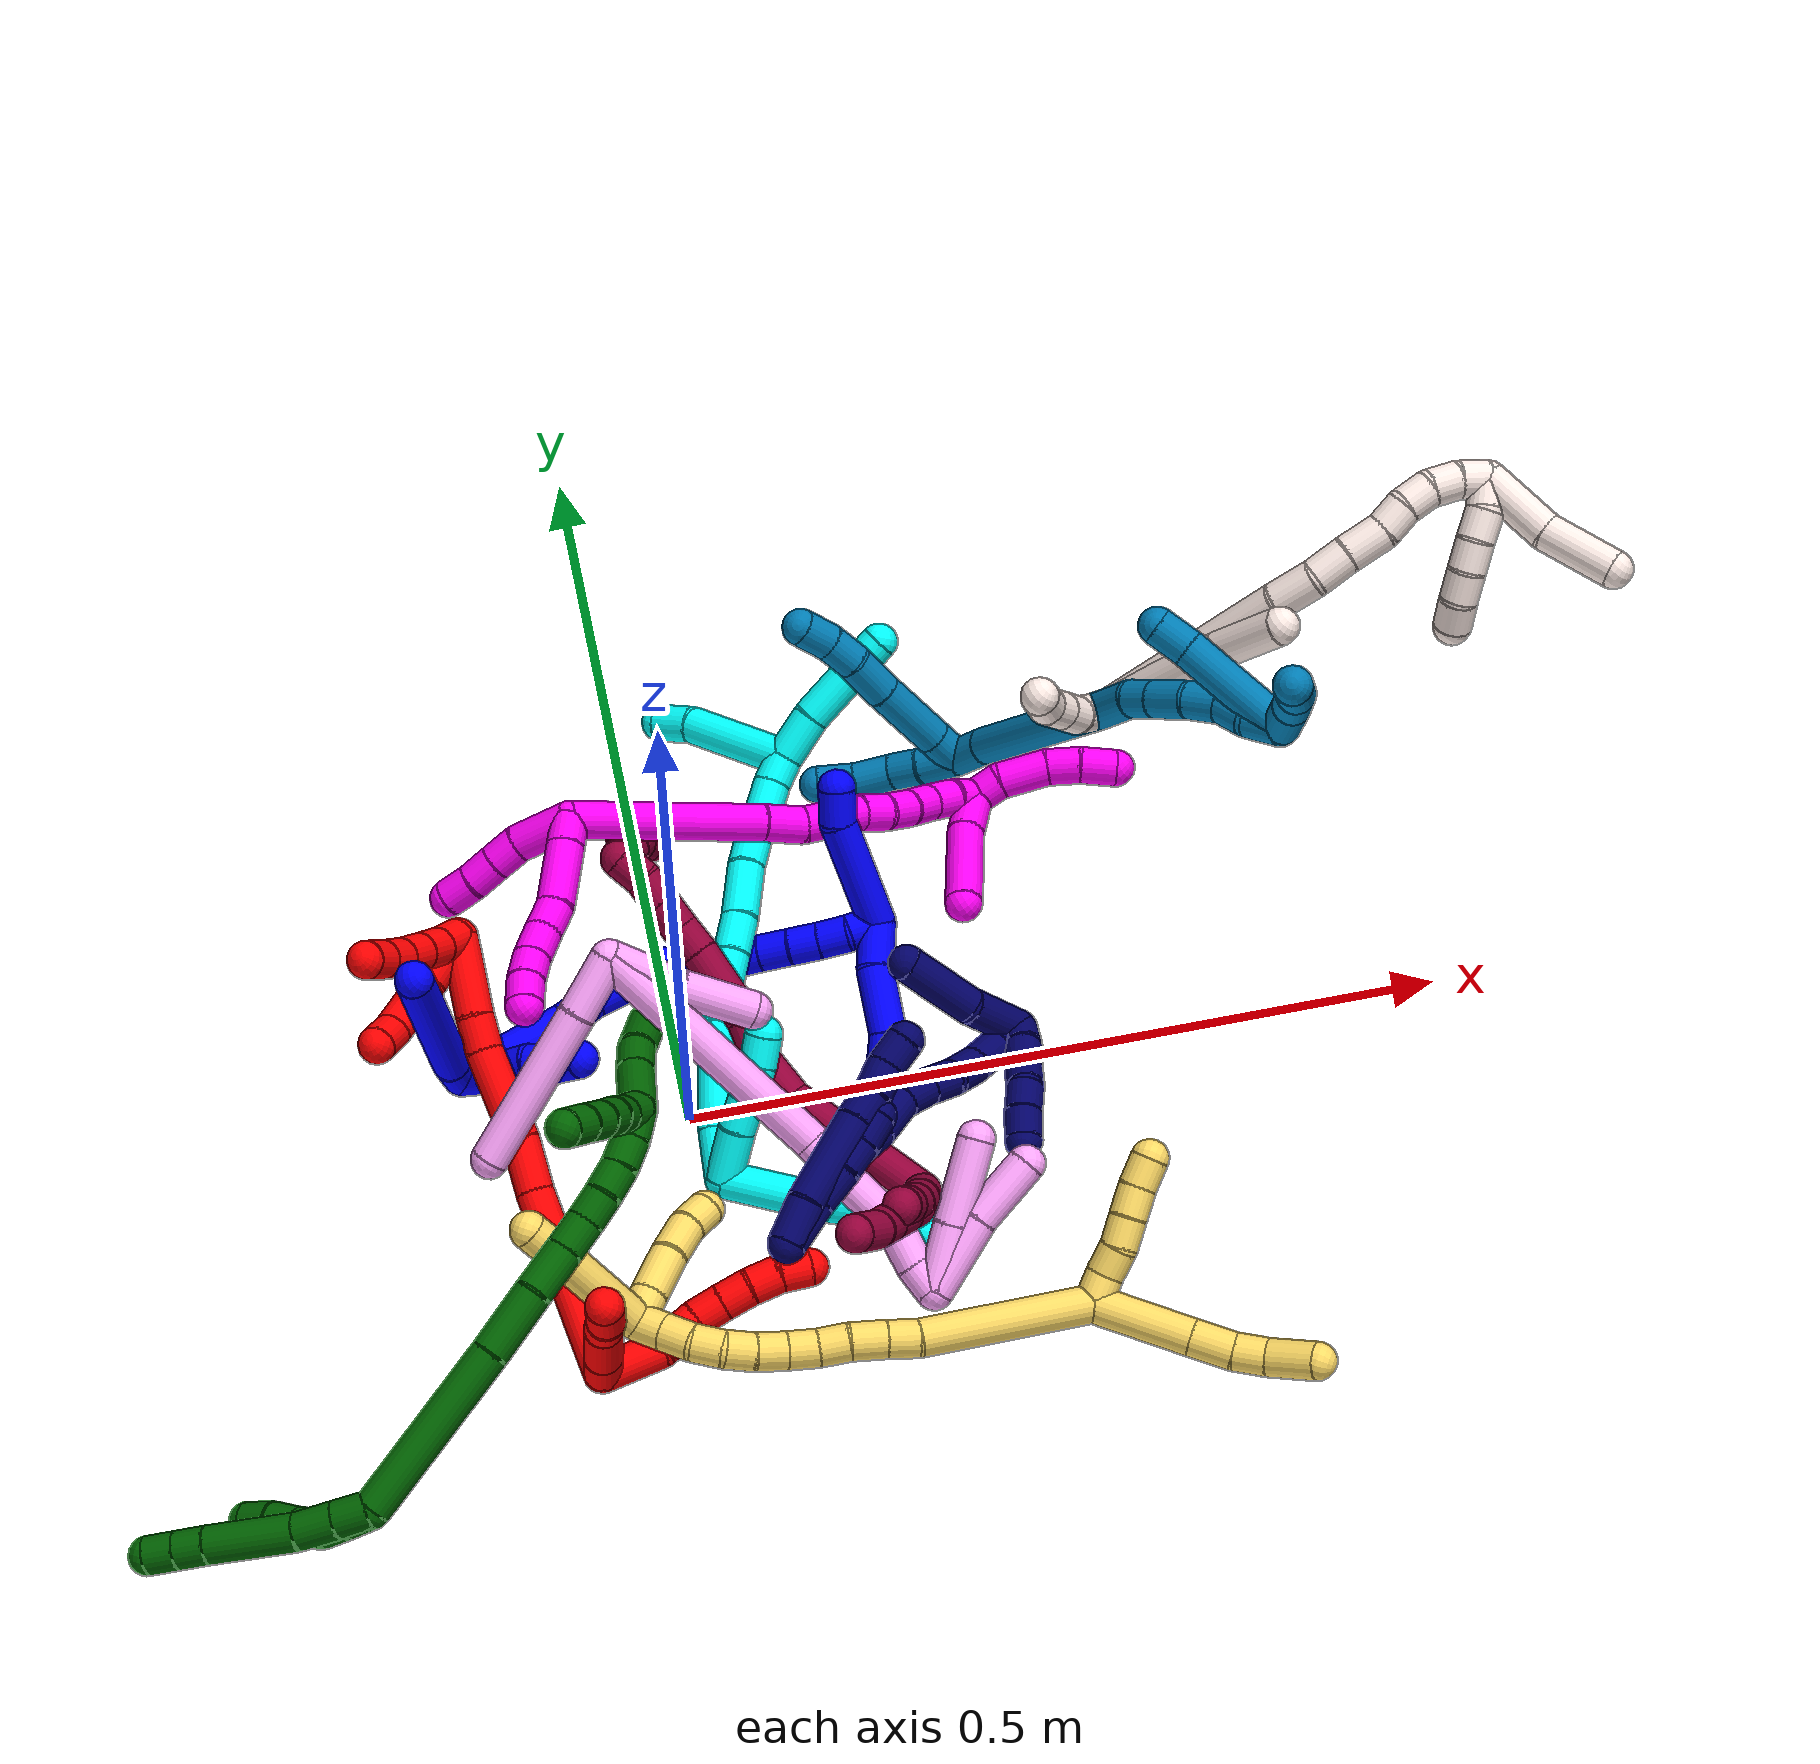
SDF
<sdf version="1.7">
 <world name="default">
  <plugin name="TubeGeneratorPlugin" filename="libtube_generator_plugin.so"/>
  <model name="photoneo_s_sensor">
   <static>1</static>
   <pose>0 0 2 1.57079 1.57079 3.14159</pose>
   <link name="link">
    <inertial><mass>0.1</mass></inertial>
    <sensor name="sensor" type="depth">
     <update_rate>30</update_rate>
     <camera>
      <horizontal_fov>1.22</horizontal_fov>
      <image><width>1920</width><height>1200</height><format>B8G8R8</format></image>
      <clip><near>0.1</near><far>4</far></clip>
      <depth_camera><output>points</output></depth_camera>
     </camera>
     <plugin name="camera_plugin" filename="libgazebo_ros_depth_camera.so">
      <baseline>0.2</baseline>
      <alwaysOn>1</alwaysOn>
      <updateRate>0.0</updateRate>
      <cameraName>camera_ir</cameraName>
      <imageTopicName>/camera/color/image_raw</imageTopicName>
      <cameraInfoTopicName>/camera/color/camera_info</cameraInfoTopicName>
      <depthImageTopicName>/camera/depth/image_raw</depthImageTopicName>
      <depthImageCameraInfoTopicName>/camera/depth/camera_info</depthImageCameraInfoTopicName>
      <pointCloudTopicName>/camera/depth/points</pointCloudTopicName>
      <frameName>fr_optical</frameName>
      <pointCloudCutoff>0.1</pointCloudCutoff>
      <pointCloudCutoffMax>2.0</pointCloudCutoffMax>
      <distortionK1>0</distortionK1>
      <distortionK2>0</distortionK2>
      <distortionK3>0</distortionK3>
      <distortionT1>0</distortionT1>
      <distortionT2>0</distortionT2>
      <CxPrime>0</CxPrime>
      <Cx>0</Cx>
      <Cy>0</Cy>
      <focalLength>0</focalLength>
      <hackBaseline>0</hackBaseline>
     </plugin>
    </sensor>
   </link>
  </model>
  <gravity>0 0 -9.8</gravity>
  <magnetic_field>6e-06 2.3e-05 -4.2e-05</magnetic_field>
  <atmosphere type="adiabatic"/>
  <physics name="default_physics" default="0" type="ode">
   <max_step_size>0.003</max_step_size>
   <real_time_factor>1</real_time_factor>
   <real_time_update_rate>1000</real_time_update_rate>
   <max_contacts>10000</max_contacts>
   <ode>
    <solver>
     <type>quick</type>
     <iters>100</iters>
     <sor>1.3</sor>
     <use_dynamic_moi_rescaling>0</use_dynamic_moi_rescaling>
    </solver>
    <constraints>
     <contact_max_correcting_vel>0</contact_max_correcting_vel>
     <contact_surface_layer>0.001</contact_surface_layer>
     <cfm>0</cfm>
     <erp>0.2</erp>
    </constraints>
   </ode>
  </physics>
  <scene><ambient>0.4 0.4 0.4 1</ambient><background>0.7 0.7 0.7 1</background><shadows>0</shadows></scene>
  <audio><device>default</device></audio>
  <spherical_coordinates>
   <surface_model>EARTH_WGS84</surface_model>
   <latitude_deg>0</latitude_deg>
   <longitude_deg>0</longitude_deg>
   <elevation>0</elevation>
   <heading_deg>0</heading_deg>
  </spherical_coordinates>
  <model name="bin">
   <static>1</static>
   <link name="bottom">
    <collision name="collision-bottom">
     <pose>0 0 -0.01 0 -0 0</pose>
     <geometry><box><size>0.8 0.6 0.02</size></box></geometry>
     <surface>
      <friction><ode><mu>100</mu><mu2>100</mu2></ode></friction>
      <contact><collide_bitmask>65535</collide_bitmask></contact>
     </surface>
    </collision>
   </link>
   <link name="west_wall">
    <collision name="collision-west_wall">
     <pose>-0.41 0 0.1 0 -0 0</pose>
     <geometry><box><size>0.02 0.6 0.2</size></box></geometry>
     <surface>
      <friction><ode><mu>100</mu><mu2>100</mu2></ode></friction>
      <contact><collide_bitmask>65535</collide_bitmask></contact>
     </surface>
    </collision>
   </link>
   <link name="east_wall">
    <collision name="collision-east_wall">
     <pose>0.41 0 0.1 0 -0 0</pose>
     <geometry><box><size>0.02 0.6 0.2</size></box></geometry>
     <surface>
      <friction><ode><mu>100</mu><mu2>100</mu2></ode></friction>
      <contact><collide_bitmask>65535</collide_bitmask></contact>
     </surface>
    </collision>
   </link>
   <link name="south_wall">
    <collision name="collision-south_wall">
     <pose>0 -0.31 0.1 0 -0 0</pose>
     <geometry><box><size>0.8 0.02 0.2</size></box></geometry>
     <surface>
      <friction><ode><mu>100</mu><mu2>100</mu2></ode></friction>
      <contact><collide_bitmask>65535</collide_bitmask></contact>
     </surface>
    </collision>
   </link>
   <link name="north_wall">
    <collision name="collision-north_wall">
     <pose>0 0.31 0.1 0 -0 0</pose>
     <geometry><box><size>0.8 0.02 0.2</size></box></geometry>
     <surface>
      <friction><ode><mu>100</mu><mu2>100</mu2></ode></friction>
      <contact><collide_bitmask>65535</collide_bitmask></contact>
     </surface>
    </collision>
   </link>
  </model>
  <model name="1">
   <static>0</static>
   <link name="1">
    <collision name="collision-cylinder-e_1_2_8">
     <pose>-0.011327 -0.003168 -0.008821 2.79678 -0.879542 -2.43264</pose>
     <geometry><cylinder><radius>0.0125</radius><length>0.029404</length></cylinder></geometry>
     <surface>
      <friction><ode><mu>1.16</mu><mu2>1.16</mu2><slip1>0</slip1><slip2>0</slip2></ode></friction>
      <contact><ode><kp>1e+06</kp><kd>1</kd><max_vel>0</max_vel><min_depth>0.001</min_depth></ode></contact>
     </surface>
    </collision>
    <visual name="visual-cylinder-e_1_2_8">
     <pose>-0.011327 -0.003168 -0.008821 2.79678 -0.879542 -2.43264</pose>
     <geometry><cylinder><radius>0.0125</radius><length>0.029404</length></cylinder></geometry>
     <material><ambient>0 0 1 1</ambient></material>
    </visual>
    <collision name="collision-cylinder-e_2_8_6">
     <pose>-0.064892 -0.025072 -0.056382 2.69113 -0.776067 -2.11982</pose>
     <geometry><cylinder><radius>0.0125</radius><length>0.120596</length></cylinder></geometry>
     <surface>
      <friction><ode><mu>1.16</mu><mu2>1.16</mu2><slip1>0</slip1><slip2>0</slip2></ode></friction>
      <contact><ode><kp>1e+06</kp><kd>1</kd><max_vel>0</max_vel><min_depth>0.001</min_depth></ode></contact>
     </surface>
    </collision>
    <visual name="visual-cylinder-e_2_8_6">
     <pose>-0.064892 -0.025072 -0.056382 2.69113 -0.776067 -2.11982</pose>
     <geometry><cylinder><radius>0.0125</radius><length>0.120596</length></cylinder></geometry>
     <material><ambient>0 0 1 1</ambient></material>
    </visual>
    <collision name="collision-cylinder-e_1_2_9">
     <pose>0.000558 0.002998 -0.011021 -2.87596 0.048785 -0.361239</pose>
     <geometry><cylinder><radius>0.0125</radius><length>0.02287</length></cylinder></geometry>
     <surface>
      <friction><ode><mu>1.16</mu><mu2>1.16</mu2><slip1>0</slip1><slip2>0</slip2></ode></friction>
      <contact><ode><kp>1e+06</kp><kd>1</kd><max_vel>0</max_vel><min_depth>0.001</min_depth></ode></contact>
     </surface>
    </collision>
    <visual name="visual-cylinder-e_1_2_9">
     <pose>0.000558 0.002998 -0.011021 -2.87596 0.048785 -0.361239</pose>
     <geometry><cylinder><radius>0.0125</radius><length>0.02287</length></cylinder></geometry>
     <material><ambient>0 0 1 1</ambient></material>
    </visual>
    <collision name="collision-cylinder-e_2_9_10">
     <pose>0.003449 0.007961 -0.039647 -3.03045 0.130971 -1.73466</pose>
     <geometry><cylinder><radius>0.0125</radius><length>0.035735</length></cylinder></geometry>
     <surface>
      <friction><ode><mu>1.16</mu><mu2>1.16</mu2><slip1>0</slip1><slip2>0</slip2></ode></friction>
      <contact><ode><kp>1e+06</kp><kd>1</kd><max_vel>0</max_vel><min_depth>0.001</min_depth></ode></contact>
     </surface>
    </collision>
    <visual name="visual-cylinder-e_2_9_10">
     <pose>0.003449 0.007961 -0.039647 -3.03045 0.130971 -1.73466</pose>
     <geometry><cylinder><radius>0.0125</radius><length>0.035735</length></cylinder></geometry>
     <material><ambient>0 0 1 1</ambient></material>
    </visual>
    <collision name="collision-cylinder-e_3_10_11">
     <pose>0.008307 0.013971 -0.06625 -2.71914 0.250564 -1.06213</pose>
     <geometry><cylinder><radius>0.0125</radius><length>0.020366</length></cylinder></geometry>
     <surface>
      <friction><ode><mu>1.16</mu><mu2>1.16</mu2><slip1>0</slip1><slip2>0</slip2></ode></friction>
      <contact><ode><kp>1e+06</kp><kd>1</kd><max_vel>0</max_vel><min_depth>0.001</min_depth></ode></contact>
     </surface>
    </collision>
    <visual name="visual-cylinder-e_3_10_11">
     <pose>0.008307 0.013971 -0.06625 -2.71914 0.250564 -1.06213</pose>
     <geometry><cylinder><radius>0.0125</radius><length>0.020366</length></cylinder></geometry>
     <material><ambient>0 0 1 1</ambient></material>
    </visual>
    <collision name="collision-cylinder-e_4_11_5">
     <pose>0.011007 0.019947 -0.085582 -2.95686 0.016603 -0.178769</pose>
     <geometry><cylinder><radius>0.0125</radius><length>0.021029</length></cylinder></geometry>
     <surface>
      <friction><ode><mu>1.16</mu><mu2>1.16</mu2><slip1>0</slip1><slip2>0</slip2></ode></friction>
      <contact><ode><kp>1e+06</kp><kd>1</kd><max_vel>0</max_vel><min_depth>0.001</min_depth></ode></contact>
     </surface>
    </collision>
    <visual name="visual-cylinder-e_4_11_5">
     <pose>0.011007 0.019947 -0.085582 -2.95686 0.016603 -0.178769</pose>
     <geometry><cylinder><radius>0.0125</radius><length>0.021029</length></cylinder></geometry>
     <material><ambient>0 0 1 1</ambient></material>
    </visual>
    <collision name="collision-cylinder-e_1_2_12">
     <pose>0.030752 -0.00842 -0.021784 2.77278 0.921264 2.42251</pose>
     <geometry><cylinder><radius>0.0125</radius><length>0.07723</length></cylinder></geometry>
     <surface>
      <friction><ode><mu>1.16</mu><mu2>1.16</mu2><slip1>0</slip1><slip2>0</slip2></ode></friction>
      <contact><ode><kp>1e+06</kp><kd>1</kd><max_vel>0</max_vel><min_depth>0.001</min_depth></ode></contact>
     </surface>
    </collision>
    <visual name="visual-cylinder-e_1_2_12">
     <pose>0.030752 -0.00842 -0.021784 2.77278 0.921264 2.42251</pose>
     <geometry><cylinder><radius>0.0125</radius><length>0.07723</length></cylinder></geometry>
     <material><ambient>0 0 1 1</ambient></material>
    </visual>
    <collision name="collision-cylinder-e_2_12_13">
     <pose>0.070713 -0.021024 -0.050419 2.59328 0.853903 2.03421</pose>
     <geometry><cylinder><radius>0.0125</radius><length>0.024434</length></cylinder></geometry>
     <surface>
      <friction><ode><mu>1.16</mu><mu2>1.16</mu2><slip1>0</slip1><slip2>0</slip2></ode></friction>
      <contact><ode><kp>1e+06</kp><kd>1</kd><max_vel>0</max_vel><min_depth>0.001</min_depth></ode></contact>
     </surface>
    </collision>
    <visual name="visual-cylinder-e_2_12_13">
     <pose>0.070713 -0.021024 -0.050419 2.59328 0.853903 2.03421</pose>
     <geometry><cylinder><radius>0.0125</radius><length>0.024434</length></cylinder></geometry>
     <material><ambient>0 0 1 1</ambient></material>
    </visual>
    <collision name="collision-cylinder-e_3_13_14">
     <pose>0.099831 -0.029764 -0.072595 2.8526 0.89416 2.55228</pose>
     <geometry><cylinder><radius>0.0125</radius><length>0.051065</length></cylinder></geometry>
     <surface>
      <friction><ode><mu>1.16</mu><mu2>1.16</mu2><slip1>0</slip1><slip2>0</slip2></ode></friction>
      <contact><ode><kp>1e+06</kp><kd>1</kd><max_vel>0</max_vel><min_depth>0.001</min_depth></ode></contact>
     </surface>
    </collision>
    <visual name="visual-cylinder-e_3_13_14">
     <pose>0.099831 -0.029764 -0.072595 2.8526 0.89416 2.55228</pose>
     <geometry><cylinder><radius>0.0125</radius><length>0.051065</length></cylinder></geometry>
     <material><ambient>0 0 1 1</ambient></material>
    </visual>
    <collision name="collision-cylinder-e_4_14_15">
     <pose>0.127352 -0.032926 -0.09467 -2.93785 0.835062 -2.68863</pose>
     <geometry><cylinder><radius>0.0125</radius><length>0.02054</length></cylinder></geometry>
     <surface>
      <friction><ode><mu>1.16</mu><mu2>1.16</mu2><slip1>0</slip1><slip2>0</slip2></ode></friction>
      <contact><ode><kp>1e+06</kp><kd>1</kd><max_vel>0</max_vel><min_depth>0.001</min_depth></ode></contact>
     </surface>
    </collision>
    <visual name="visual-cylinder-e_4_14_15">
     <pose>0.127352 -0.032926 -0.09467 -2.93785 0.835062 -2.68863</pose>
     <geometry><cylinder><radius>0.0125</radius><length>0.02054</length></cylinder></geometry>
     <material><ambient>0 0 1 1</ambient></material>
    </visual>
    <collision name="collision-cylinder-e_5_15_16">
     <pose>0.143402 -0.028033 -0.109983 -2.75372 0.739424 -2.20343</pose>
     <geometry><cylinder><radius>0.0125</radius><length>0.02504</length></cylinder></geometry>
     <surface>
      <friction><ode><mu>1.16</mu><mu2>1.16</mu2><slip1>0</slip1><slip2>0</slip2></ode></friction>
      <contact><ode><kp>1e+06</kp><kd>1</kd><max_vel>0</max_vel><min_depth>0.001</min_depth></ode></contact>
     </surface>
    </collision>
    <visual name="visual-cylinder-e_5_15_16">
     <pose>0.143402 -0.028033 -0.109983 -2.75372 0.739424 -2.20343</pose>
     <geometry><cylinder><radius>0.0125</radius><length>0.02504</length></cylinder></geometry>
     <material><ambient>0 0 1 1</ambient></material>
    </visual>
    <collision name="collision-cylinder-e_6_16_17">
     <pose>0.156888 -0.02316 -0.127855 -2.99512 0.492518 -2.57361</pose>
     <geometry><cylinder><radius>0.0125</radius><length>0.021357</length></cylinder></geometry>
     <surface>
      <friction><ode><mu>1.16</mu><mu2>1.16</mu2><slip1>0</slip1><slip2>0</slip2></ode></friction>
      <contact><ode><kp>1e+06</kp><kd>1</kd><max_vel>0</max_vel><min_depth>0.001</min_depth></ode></contact>
     </surface>
    </collision>
    <visual name="visual-cylinder-e_6_16_17">
     <pose>0.156888 -0.02316 -0.127855 -2.99512 0.492518 -2.57361</pose>
     <geometry><cylinder><radius>0.0125</radius><length>0.021357</length></cylinder></geometry>
     <material><ambient>0 0 1 1</ambient></material>
    </visual>
    <collision name="collision-cylinder-e_7_17_18">
     <pose>0.166838 -0.020382 -0.145853 -2.98129 0.507915 -2.54135</pose>
     <geometry><cylinder><radius>0.0125</radius><length>0.020149</length></cylinder></geometry>
     <surface>
      <friction><ode><mu>1.16</mu><mu2>1.16</mu2><slip1>0</slip1><slip2>0</slip2></ode></friction>
      <contact><ode><kp>1e+06</kp><kd>1</kd><max_vel>0</max_vel><min_depth>0.001</min_depth></ode></contact>
     </surface>
    </collision>
    <visual name="visual-cylinder-e_7_17_18">
     <pose>0.166838 -0.020382 -0.145853 -2.98129 0.507915 -2.54135</pose>
     <geometry><cylinder><radius>0.0125</radius><length>0.020149</length></cylinder></geometry>
     <material><ambient>0 0 1 1</ambient></material>
    </visual>
    <collision name="collision-cylinder-e_8_18_19">
     <pose>0.17739 -0.01769 -0.16271 -2.98524 0.599708 -2.64528</pose>
     <geometry><cylinder><radius>0.0125</radius><length>0.02003</length></cylinder></geometry>
     <surface>
      <friction><ode><mu>1.16</mu><mu2>1.16</mu2><slip1>0</slip1><slip2>0</slip2></ode></friction>
      <contact><ode><kp>1e+06</kp><kd>1</kd><max_vel>0</max_vel><min_depth>0.001</min_depth></ode></contact>
     </surface>
    </collision>
    <visual name="visual-cylinder-e_8_18_19">
     <pose>0.17739 -0.01769 -0.16271 -2.98524 0.599708 -2.64528</pose>
     <geometry><cylinder><radius>0.0125</radius><length>0.02003</length></cylinder></geometry>
     <material><ambient>0 0 1 1</ambient></material>
    </visual>
    <collision name="collision-cylinder-e_9_19_20">
     <pose>0.188462 -0.015496 -0.179234 -3.03362 0.5726 -2.77851</pose>
     <geometry><cylinder><radius>0.0125</radius><length>0.020004</length></cylinder></geometry>
     <surface>
      <friction><ode><mu>1.16</mu><mu2>1.16</mu2><slip1>0</slip1><slip2>0</slip2></ode></friction>
      <contact><ode><kp>1e+06</kp><kd>1</kd><max_vel>0</max_vel><min_depth>0.001</min_depth></ode></contact>
     </surface>
    </collision>
    <visual name="visual-cylinder-e_9_19_20">
     <pose>0.188462 -0.015496 -0.179234 -3.03362 0.5726 -2.77851</pose>
     <geometry><cylinder><radius>0.0125</radius><length>0.020004</length></cylinder></geometry>
     <material><ambient>0 0 1 1</ambient></material>
    </visual>
    <collision name="collision-cylinder-e_10_20_1">
     <pose>0.201093 -0.015 -0.194615 3.0833 0.797799 3.00346</pose>
     <geometry><cylinder><radius>0.0125</radius><length>0.020149</length></cylinder></geometry>
     <surface>
      <friction><ode><mu>1.16</mu><mu2>1.16</mu2><slip1>0</slip1><slip2>0</slip2></ode></friction>
      <contact><ode><kp>1e+06</kp><kd>1</kd><max_vel>0</max_vel><min_depth>0.001</min_depth></ode></contact>
     </surface>
    </collision>
    <visual name="visual-cylinder-e_10_20_1">
     <pose>0.201093 -0.015 -0.194615 3.0833 0.797799 3.00346</pose>
     <geometry><cylinder><radius>0.0125</radius><length>0.020149</length></cylinder></geometry>
     <material><ambient>0 0 1 1</ambient></material>
    </visual>
    <collision name="collision-cylinder-e_1_1_21">
     <pose>0.191454 -0.047464 -0.213458 1.92407 -0.45821 -0.645672</pose>
     <geometry><cylinder><radius>0.0125</radius><length>0.076187</length></cylinder></geometry>
     <surface>
      <friction><ode><mu>1.16</mu><mu2>1.16</mu2><slip1>0</slip1><slip2>0</slip2></ode></friction>
      <contact><ode><kp>1e+06</kp><kd>1</kd><max_vel>0</max_vel><min_depth>0.001</min_depth></ode></contact>
     </surface>
    </collision>
    <visual name="visual-cylinder-e_1_1_21">
     <pose>0.191454 -0.047464 -0.213458 1.92407 -0.45821 -0.645672</pose>
     <geometry><cylinder><radius>0.0125</radius><length>0.076187</length></cylinder></geometry>
     <material><ambient>0 0 1 1</ambient></material>
    </visual>
    <collision name="collision-cylinder-e_2_21_4">
     <pose>0.172364 -0.089523 -0.231331 2.11492 -0.189191 -0.333476</pose>
     <geometry><cylinder><radius>0.0125</radius><length>0.023813</length></cylinder></geometry>
     <surface>
      <friction><ode><mu>1.16</mu><mu2>1.16</mu2><slip1>0</slip1><slip2>0</slip2></ode></friction>
      <contact><ode><kp>1e+06</kp><kd>1</kd><max_vel>0</max_vel><min_depth>0.001</min_depth></ode></contact>
     </surface>
    </collision>
    <visual name="visual-cylinder-e_2_21_4">
     <pose>0.172364 -0.089523 -0.231331 2.11492 -0.189191 -0.333476</pose>
     <geometry><cylinder><radius>0.0125</radius><length>0.023813</length></cylinder></geometry>
     <material><ambient>0 0 1 1</ambient></material>
    </visual>
    <collision name="collision-cylinder-e_1_1_22">
     <pose>0.202543 -0.00066 -0.199328 -1.41545 -0.368291 0.316056</pose>
     <geometry><cylinder><radius>0.0125</radius><length>0.032007</length></cylinder></geometry>
     <surface>
      <friction><ode><mu>1.16</mu><mu2>1.16</mu2><slip1>0</slip1><slip2>0</slip2></ode></friction>
      <contact><ode><kp>1e+06</kp><kd>1</kd><max_vel>0</max_vel><min_depth>0.001</min_depth></ode></contact>
     </surface>
    </collision>
    <visual name="visual-cylinder-e_1_1_22">
     <pose>0.202543 -0.00066 -0.199328 -1.41545 -0.368291 0.316056</pose>
     <geometry><cylinder><radius>0.0125</radius><length>0.032007</length></cylinder></geometry>
     <material><ambient>0 0 1 1</ambient></material>
    </visual>
    <collision name="collision-cylinder-e_2_22_23">
     <pose>0.193293 0.036644 -0.1965 -1.54784 -0.153424 0.149955</pose>
     <geometry><cylinder><radius>0.0125</radius><length>0.045654</length></cylinder></geometry>
     <surface>
      <friction><ode><mu>1.16</mu><mu2>1.16</mu2><slip1>0</slip1><slip2>0</slip2></ode></friction>
      <contact><ode><kp>1e+06</kp><kd>1</kd><max_vel>0</max_vel><min_depth>0.001</min_depth></ode></contact>
     </surface>
    </collision>
    <visual name="visual-cylinder-e_2_22_23">
     <pose>0.193293 0.036644 -0.1965 -1.54784 -0.153424 0.149955</pose>
     <geometry><cylinder><radius>0.0125</radius><length>0.045654</length></cylinder></geometry>
     <material><ambient>0 0 1 1</ambient></material>
    </visual>
    <collision name="collision-cylinder-e_3_23_3">
     <pose>0.187127 0.069414 -0.19235 -1.22924 -0.241994 0.171222</pose>
     <geometry><cylinder><radius>0.0125</radius><length>0.02234</length></cylinder></geometry>
     <surface>
      <friction><ode><mu>1.16</mu><mu2>1.16</mu2><slip1>0</slip1><slip2>0</slip2></ode></friction>
      <contact><ode><kp>1e+06</kp><kd>1</kd><max_vel>0</max_vel><min_depth>0.001</min_depth></ode></contact>
     </surface>
    </collision>
    <visual name="visual-cylinder-e_3_23_3">
     <pose>0.187127 0.069414 -0.19235 -1.22924 -0.241994 0.171222</pose>
     <geometry><cylinder><radius>0.0125</radius><length>0.02234</length></cylinder></geometry>
     <material><ambient>0 0 1 1</ambient></material>
    </visual>
    <collision name="collision-sphere-3">
     <pose>0.184451 0.079632 -0.188717 0 -0 0</pose>
     <geometry><sphere><radius>0.0125</radius></sphere></geometry>
     <surface>
      <friction><ode><mu>1.16</mu><mu2>1.16</mu2><slip1>0</slip1><slip2>0</slip2></ode></friction>
      <contact><ode><kp>1e+06</kp><kd>1</kd><max_vel>0</max_vel><min_depth>0.001</min_depth></ode></contact>
     </surface>
    </collision>
    <visual name="visual-sphere-3">
     <pose>0.184451 0.079632 -0.188717 0 -0 0</pose>
     <geometry><sphere><radius>0.0125</radius></sphere></geometry>
     <material><ambient>0 0 1 1</ambient></material>
    </visual>
    <collision name="collision-sphere-23">
     <pose>0.189804 0.059196 -0.195982 0 -0 0</pose>
     <geometry><sphere><radius>0.0125</radius></sphere></geometry>
     <surface>
      <friction><ode><mu>1.16</mu><mu2>1.16</mu2><slip1>0</slip1><slip2>0</slip2></ode></friction>
      <contact><ode><kp>1e+06</kp><kd>1</kd><max_vel>0</max_vel><min_depth>0.001</min_depth></ode></contact>
     </surface>
    </collision>
    <visual name="visual-sphere-23">
     <pose>0.189804 0.059196 -0.195982 0 -0 0</pose>
     <geometry><sphere><radius>0.0125</radius></sphere></geometry>
     <material><ambient>0 0 1 1</ambient></material>
    </visual>
    <collision name="collision-sphere-22">
     <pose>0.196781 0.014091 -0.197018 0 -0 0</pose>
     <geometry><sphere><radius>0.0125</radius></sphere></geometry>
     <surface>
      <friction><ode><mu>1.16</mu><mu2>1.16</mu2><slip1>0</slip1><slip2>0</slip2></ode></friction>
      <contact><ode><kp>1e+06</kp><kd>1</kd><max_vel>0</max_vel><min_depth>0.001</min_depth></ode></contact>
     </surface>
    </collision>
    <visual name="visual-sphere-22">
     <pose>0.196781 0.014091 -0.197018 0 -0 0</pose>
     <geometry><sphere><radius>0.0125</radius></sphere></geometry>
     <material><ambient>0 0 1 1</ambient></material>
    </visual>
    <collision name="collision-sphere-4">
     <pose>0.170125 -0.099529 -0.237385 0 -0 0</pose>
     <geometry><sphere><radius>0.0125</radius></sphere></geometry>
     <surface>
      <friction><ode><mu>1.16</mu><mu2>1.16</mu2><slip1>0</slip1><slip2>0</slip2></ode></friction>
      <contact><ode><kp>1e+06</kp><kd>1</kd><max_vel>0</max_vel><min_depth>0.001</min_depth></ode></contact>
     </surface>
    </collision>
    <visual name="visual-sphere-4">
     <pose>0.170125 -0.099529 -0.237385 0 -0 0</pose>
     <geometry><sphere><radius>0.0125</radius></sphere></geometry>
     <material><ambient>0 0 1 1</ambient></material>
    </visual>
    <collision name="collision-sphere-21">
     <pose>0.174604 -0.079518 -0.225278 0 -0 0</pose>
     <geometry><sphere><radius>0.0125</radius></sphere></geometry>
     <surface>
      <friction><ode><mu>1.16</mu><mu2>1.16</mu2><slip1>0</slip1><slip2>0</slip2></ode></friction>
      <contact><ode><kp>1e+06</kp><kd>1</kd><max_vel>0</max_vel><min_depth>0.001</min_depth></ode></contact>
     </surface>
    </collision>
    <visual name="visual-sphere-21">
     <pose>0.174604 -0.079518 -0.225278 0 -0 0</pose>
     <geometry><sphere><radius>0.0125</radius></sphere></geometry>
     <material><ambient>0 0 1 1</ambient></material>
    </visual>
    <collision name="collision-sphere-1">
     <pose>0.208304 -0.01541 -0.201638 0 -0 0</pose>
     <geometry><sphere><radius>0.0125</radius></sphere></geometry>
     <surface>
      <friction><ode><mu>1.16</mu><mu2>1.16</mu2><slip1>0</slip1><slip2>0</slip2></ode></friction>
      <contact><ode><kp>1e+06</kp><kd>1</kd><max_vel>0</max_vel><min_depth>0.001</min_depth></ode></contact>
     </surface>
    </collision>
    <visual name="visual-sphere-1">
     <pose>0.208304 -0.01541 -0.201638 0 -0 0</pose>
     <geometry><sphere><radius>0.0125</radius></sphere></geometry>
     <material><ambient>0 0 1 1</ambient></material>
    </visual>
    <collision name="collision-sphere-11">
     <pose>0.010832 0.018016 -0.075248 0 -0 0</pose>
     <geometry><sphere><radius>0.0125</radius></sphere></geometry>
     <surface>
      <friction><ode><mu>1.16</mu><mu2>1.16</mu2><slip1>0</slip1><slip2>0</slip2></ode></friction>
      <contact><ode><kp>1e+06</kp><kd>1</kd><max_vel>0</max_vel><min_depth>0.001</min_depth></ode></contact>
     </surface>
    </collision>
    <visual name="visual-sphere-11">
     <pose>0.010832 0.018016 -0.075248 0 -0 0</pose>
     <geometry><sphere><radius>0.0125</radius></sphere></geometry>
     <material><ambient>0 0 1 1</ambient></material>
    </visual>
    <collision name="collision-sphere-10">
     <pose>0.005782 0.009926 -0.057252 0 -0 0</pose>
     <geometry><sphere><radius>0.0125</radius></sphere></geometry>
     <surface>
      <friction><ode><mu>1.16</mu><mu2>1.16</mu2><slip1>0</slip1><slip2>0</slip2></ode></friction>
      <contact><ode><kp>1e+06</kp><kd>1</kd><max_vel>0</max_vel><min_depth>0.001</min_depth></ode></contact>
     </surface>
    </collision>
    <visual name="visual-sphere-10">
     <pose>0.005782 0.009926 -0.057252 0 -0 0</pose>
     <geometry><sphere><radius>0.0125</radius></sphere></geometry>
     <material><ambient>0 0 1 1</ambient></material>
    </visual>
    <collision name="collision-sphere-6">
     <pose>-0.107129 -0.043808 -0.095123 0 -0 0</pose>
     <geometry><sphere><radius>0.0125</radius></sphere></geometry>
     <surface>
      <friction><ode><mu>1.16</mu><mu2>1.16</mu2><slip1>0</slip1><slip2>0</slip2></ode></friction>
      <contact><ode><kp>1e+06</kp><kd>1</kd><max_vel>0</max_vel><min_depth>0.001</min_depth></ode></contact>
     </surface>
    </collision>
    <visual name="visual-sphere-6">
     <pose>-0.107129 -0.043808 -0.095123 0 -0 0</pose>
     <geometry><sphere><radius>0.0125</radius></sphere></geometry>
     <material><ambient>0 0 1 1</ambient></material>
    </visual>
    <collision name="collision-sphere-9">
     <pose>0.001115 0.005997 -0.022042 0 -0 0</pose>
     <geometry><sphere><radius>0.0125</radius></sphere></geometry>
     <surface>
      <friction><ode><mu>1.16</mu><mu2>1.16</mu2><slip1>0</slip1><slip2>0</slip2></ode></friction>
      <contact><ode><kp>1e+06</kp><kd>1</kd><max_vel>0</max_vel><min_depth>0.001</min_depth></ode></contact>
     </surface>
    </collision>
    <visual name="visual-sphere-9">
     <pose>0.001115 0.005997 -0.022042 0 -0 0</pose>
     <geometry><sphere><radius>0.0125</radius></sphere></geometry>
     <material><ambient>0 0 1 1</ambient></material>
    </visual>
    <collision name="collision-sphere-2">
     <geometry><sphere><radius>0.0125</radius></sphere></geometry>
     <surface>
      <friction><ode><mu>1.16</mu><mu2>1.16</mu2><slip1>0</slip1><slip2>0</slip2></ode></friction>
      <contact><ode><kp>1e+06</kp><kd>1</kd><max_vel>0</max_vel><min_depth>0.001</min_depth></ode></contact>
     </surface>
    </collision>
    <visual name="visual-sphere-2">
     <geometry><sphere><radius>0.0125</radius></sphere></geometry>
     <material><ambient>0 0 1 1</ambient></material>
    </visual>
    <collision name="collision-sphere-19">
     <pose>0.183042 -0.016402 -0.170877 0 -0 0</pose>
     <geometry><sphere><radius>0.0125</radius></sphere></geometry>
     <surface>
      <friction><ode><mu>1.16</mu><mu2>1.16</mu2><slip1>0</slip1><slip2>0</slip2></ode></friction>
      <contact><ode><kp>1e+06</kp><kd>1</kd><max_vel>0</max_vel><min_depth>0.001</min_depth></ode></contact>
     </surface>
    </collision>
    <visual name="visual-sphere-19">
     <pose>0.183042 -0.016402 -0.170877 0 -0 0</pose>
     <geometry><sphere><radius>0.0125</radius></sphere></geometry>
     <material><ambient>0 0 1 1</ambient></material>
    </visual>
    <collision name="collision-sphere-8">
     <pose>-0.022655 -0.006336 -0.017642 0 -0 0</pose>
     <geometry><sphere><radius>0.0125</radius></sphere></geometry>
     <surface>
      <friction><ode><mu>1.16</mu><mu2>1.16</mu2><slip1>0</slip1><slip2>0</slip2></ode></friction>
      <contact><ode><kp>1e+06</kp><kd>1</kd><max_vel>0</max_vel><min_depth>0.001</min_depth></ode></contact>
     </surface>
    </collision>
    <visual name="visual-sphere-8">
     <pose>-0.022655 -0.006336 -0.017642 0 -0 0</pose>
     <geometry><sphere><radius>0.0125</radius></sphere></geometry>
     <material><ambient>0 0 1 1</ambient></material>
    </visual>
    <collision name="collision-sphere-5">
     <pose>0.011181 0.021878 -0.095916 0 -0 0</pose>
     <geometry><sphere><radius>0.0125</radius></sphere></geometry>
     <surface>
      <friction><ode><mu>1.16</mu><mu2>1.16</mu2><slip1>0</slip1><slip2>0</slip2></ode></friction>
      <contact><ode><kp>1e+06</kp><kd>1</kd><max_vel>0</max_vel><min_depth>0.001</min_depth></ode></contact>
     </surface>
    </collision>
    <visual name="visual-sphere-5">
     <pose>0.011181 0.021878 -0.095916 0 -0 0</pose>
     <geometry><sphere><radius>0.0125</radius></sphere></geometry>
     <material><ambient>0 0 1 1</ambient></material>
    </visual>
    <collision name="collision-sphere-12">
     <pose>0.061503 -0.016839 -0.043569 0 -0 0</pose>
     <geometry><sphere><radius>0.0125</radius></sphere></geometry>
     <surface>
      <friction><ode><mu>1.16</mu><mu2>1.16</mu2><slip1>0</slip1><slip2>0</slip2></ode></friction>
      <contact><ode><kp>1e+06</kp><kd>1</kd><max_vel>0</max_vel><min_depth>0.001</min_depth></ode></contact>
     </surface>
    </collision>
    <visual name="visual-sphere-12">
     <pose>0.061503 -0.016839 -0.043569 0 -0 0</pose>
     <geometry><sphere><radius>0.0125</radius></sphere></geometry>
     <material><ambient>0 0 1 1</ambient></material>
    </visual>
    <collision name="collision-sphere-13">
     <pose>0.079923 -0.025208 -0.05727 0 -0 0</pose>
     <geometry><sphere><radius>0.0125</radius></sphere></geometry>
     <surface>
      <friction><ode><mu>1.16</mu><mu2>1.16</mu2><slip1>0</slip1><slip2>0</slip2></ode></friction>
      <contact><ode><kp>1e+06</kp><kd>1</kd><max_vel>0</max_vel><min_depth>0.001</min_depth></ode></contact>
     </surface>
    </collision>
    <visual name="visual-sphere-13">
     <pose>0.079923 -0.025208 -0.05727 0 -0 0</pose>
     <geometry><sphere><radius>0.0125</radius></sphere></geometry>
     <material><ambient>0 0 1 1</ambient></material>
    </visual>
    <collision name="collision-sphere-14">
     <pose>0.119738 -0.034321 -0.08792 0 -0 0</pose>
     <geometry><sphere><radius>0.0125</radius></sphere></geometry>
     <surface>
      <friction><ode><mu>1.16</mu><mu2>1.16</mu2><slip1>0</slip1><slip2>0</slip2></ode></friction>
      <contact><ode><kp>1e+06</kp><kd>1</kd><max_vel>0</max_vel><min_depth>0.001</min_depth></ode></contact>
     </surface>
    </collision>
    <visual name="visual-sphere-14">
     <pose>0.119738 -0.034321 -0.08792 0 -0 0</pose>
     <geometry><sphere><radius>0.0125</radius></sphere></geometry>
     <material><ambient>0 0 1 1</ambient></material>
    </visual>
    <collision name="collision-sphere-15">
     <pose>0.134965 -0.031531 -0.10142 0 -0 0</pose>
     <geometry><sphere><radius>0.0125</radius></sphere></geometry>
     <surface>
      <friction><ode><mu>1.16</mu><mu2>1.16</mu2><slip1>0</slip1><slip2>0</slip2></ode></friction>
      <contact><ode><kp>1e+06</kp><kd>1</kd><max_vel>0</max_vel><min_depth>0.001</min_depth></ode></contact>
     </surface>
    </collision>
    <visual name="visual-sphere-15">
     <pose>0.134965 -0.031531 -0.10142 0 -0 0</pose>
     <geometry><sphere><radius>0.0125</radius></sphere></geometry>
     <material><ambient>0 0 1 1</ambient></material>
    </visual>
    <collision name="collision-sphere-16">
     <pose>0.151839 -0.024534 -0.118546 0 -0 0</pose>
     <geometry><sphere><radius>0.0125</radius></sphere></geometry>
     <surface>
      <friction><ode><mu>1.16</mu><mu2>1.16</mu2><slip1>0</slip1><slip2>0</slip2></ode></friction>
      <contact><ode><kp>1e+06</kp><kd>1</kd><max_vel>0</max_vel><min_depth>0.001</min_depth></ode></contact>
     </surface>
    </collision>
    <visual name="visual-sphere-16">
     <pose>0.151839 -0.024534 -0.118546 0 -0 0</pose>
     <geometry><sphere><radius>0.0125</radius></sphere></geometry>
     <material><ambient>0 0 1 1</ambient></material>
    </visual>
    <collision name="collision-sphere-17">
     <pose>0.161938 -0.021787 -0.137163 0 -0 0</pose>
     <geometry><sphere><radius>0.0125</radius></sphere></geometry>
     <surface>
      <friction><ode><mu>1.16</mu><mu2>1.16</mu2><slip1>0</slip1><slip2>0</slip2></ode></friction>
      <contact><ode><kp>1e+06</kp><kd>1</kd><max_vel>0</max_vel><min_depth>0.001</min_depth></ode></contact>
     </surface>
    </collision>
    <visual name="visual-sphere-17">
     <pose>0.161938 -0.021787 -0.137163 0 -0 0</pose>
     <geometry><sphere><radius>0.0125</radius></sphere></geometry>
     <material><ambient>0 0 1 1</ambient></material>
    </visual>
    <collision name="collision-sphere-18">
     <pose>0.171737 -0.018977 -0.154544 0 -0 0</pose>
     <geometry><sphere><radius>0.0125</radius></sphere></geometry>
     <surface>
      <friction><ode><mu>1.16</mu><mu2>1.16</mu2><slip1>0</slip1><slip2>0</slip2></ode></friction>
      <contact><ode><kp>1e+06</kp><kd>1</kd><max_vel>0</max_vel><min_depth>0.001</min_depth></ode></contact>
     </surface>
    </collision>
    <visual name="visual-sphere-18">
     <pose>0.171737 -0.018977 -0.154544 0 -0 0</pose>
     <geometry><sphere><radius>0.0125</radius></sphere></geometry>
     <material><ambient>0 0 1 1</ambient></material>
    </visual>
    <collision name="collision-sphere-20">
     <pose>0.193881 -0.01459 -0.187592 0 -0 0</pose>
     <geometry><sphere><radius>0.0125</radius></sphere></geometry>
     <surface>
      <friction><ode><mu>1.16</mu><mu2>1.16</mu2><slip1>0</slip1><slip2>0</slip2></ode></friction>
      <contact><ode><kp>1e+06</kp><kd>1</kd><max_vel>0</max_vel><min_depth>0.001</min_depth></ode></contact>
     </surface>
    </collision>
    <visual name="visual-sphere-20">
     <pose>0.193881 -0.01459 -0.187592 0 -0 0</pose>
     <geometry><sphere><radius>0.0125</radius></sphere></geometry>
     <material><ambient>0 0 1 1</ambient></material>
    </visual>
    <inertial>
     <pose>0.085401 -0.014052 -0.108068 0 -0 0</pose>
     <mass>0.75</mass>
     <inertia>
      <ixx>-0.000141</ixx>
      <ixy>0</ixy>
      <ixz>0</ixz>
      <iyy>6.7e-05</iyy>
      <iyz>0</iyz>
      <izz>0.000121</izz>
     </inertia>
    </inertial>
   </link>
   <pose>-0.140721 0.053455 0.013525 -2.75867 0.675783 0.373811</pose>
  </model>
  <model name="2">
   <static>0</static>
   <link name="2">
    <collision name="collision-cylinder-e_1_2_8">
     <pose>0.017766 0.00372 -0.008662 -2.73595 1.08297 -2.48267</pose>
     <geometry><cylinder><radius>0.0125</radius><length>0.040224</length></cylinder></geometry>
     <surface>
      <friction><ode><mu>1.16</mu><mu2>1.16</mu2><slip1>0</slip1><slip2>0</slip2></ode></friction>
      <contact><ode><kp>1e+06</kp><kd>1</kd><max_vel>0</max_vel><min_depth>0.001</min_depth></ode></contact>
     </surface>
    </collision>
    <visual name="visual-cylinder-e_1_2_8">
     <pose>0.017766 0.00372 -0.008662 -2.73595 1.08297 -2.48267</pose>
     <geometry><cylinder><radius>0.0125</radius><length>0.040224</length></cylinder></geometry>
     <material><ambient>1 0 0 1</ambient></material>
    </visual>
    <collision name="collision-cylinder-e_2_8_9">
     <pose>0.047241 0.014655 -0.022384 -2.18246 0.925559 -1.5293</pose>
     <geometry><cylinder><radius>0.0125</radius><length>0.02931</length></cylinder></geometry>
     <surface>
      <friction><ode><mu>1.16</mu><mu2>1.16</mu2><slip1>0</slip1><slip2>0</slip2></ode></friction>
      <contact><ode><kp>1e+06</kp><kd>1</kd><max_vel>0</max_vel><min_depth>0.001</min_depth></ode></contact>
     </surface>
    </collision>
    <visual name="visual-cylinder-e_2_8_9">
     <pose>0.047241 0.014655 -0.022384 -2.18246 0.925559 -1.5293</pose>
     <geometry><cylinder><radius>0.0125</radius><length>0.02931</length></cylinder></geometry>
     <material><ambient>1 0 0 1</ambient></material>
    </visual>
    <collision name="collision-cylinder-e_3_9_10">
     <pose>0.06833 0.024646 -0.029784 -2.27093 1.20162 -1.9491</pose>
     <geometry><cylinder><radius>0.0125</radius><length>0.020115</length></cylinder></geometry>
     <surface>
      <friction><ode><mu>1.16</mu><mu2>1.16</mu2><slip1>0</slip1><slip2>0</slip2></ode></friction>
      <contact><ode><kp>1e+06</kp><kd>1</kd><max_vel>0</max_vel><min_depth>0.001</min_depth></ode></contact>
     </surface>
    </collision>
    <visual name="visual-cylinder-e_3_9_10">
     <pose>0.06833 0.024646 -0.029784 -2.27093 1.20162 -1.9491</pose>
     <geometry><cylinder><radius>0.0125</radius><length>0.020115</length></cylinder></geometry>
     <material><ambient>1 0 0 1</ambient></material>
    </visual>
    <collision name="collision-cylinder-e_4_10_11">
     <pose>0.087164 0.029837 -0.034416 -2.33051 1.23202 -2.05122</pose>
     <geometry><cylinder><radius>0.0125</radius><length>0.020048</length></cylinder></geometry>
     <surface>
      <friction><ode><mu>1.16</mu><mu2>1.16</mu2><slip1>0</slip1><slip2>0</slip2></ode></friction>
      <contact><ode><kp>1e+06</kp><kd>1</kd><max_vel>0</max_vel><min_depth>0.001</min_depth></ode></contact>
     </surface>
    </collision>
    <visual name="visual-cylinder-e_4_10_11">
     <pose>0.087164 0.029837 -0.034416 -2.33051 1.23202 -2.05122</pose>
     <geometry><cylinder><radius>0.0125</radius><length>0.020048</length></cylinder></geometry>
     <material><ambient>1 0 0 1</ambient></material>
    </visual>
    <collision name="collision-cylinder-e_5_11_12">
     <pose>0.105824 0.034129 -0.040404 -2.67153 1.14796 -2.43225</pose>
     <geometry><cylinder><radius>0.0125</radius><length>0.02019</length></cylinder></geometry>
     <surface>
      <friction><ode><mu>1.16</mu><mu2>1.16</mu2><slip1>0</slip1><slip2>0</slip2></ode></friction>
      <contact><ode><kp>1e+06</kp><kd>1</kd><max_vel>0</max_vel><min_depth>0.001</min_depth></ode></contact>
     </surface>
    </collision>
    <visual name="visual-cylinder-e_5_11_12">
     <pose>0.105824 0.034129 -0.040404 -2.67153 1.14796 -2.43225</pose>
     <geometry><cylinder><radius>0.0125</radius><length>0.02019</length></cylinder></geometry>
     <material><ambient>1 0 0 1</ambient></material>
    </visual>
    <collision name="collision-cylinder-e_6_12_6">
     <pose>0.123772 0.036248 -0.049062 -3.0926 1.05376 -3.0574</pose>
     <geometry><cylinder><radius>0.0125</radius><length>0.020112</length></cylinder></geometry>
     <surface>
      <friction><ode><mu>1.16</mu><mu2>1.16</mu2><slip1>0</slip1><slip2>0</slip2></ode></friction>
      <contact><ode><kp>1e+06</kp><kd>1</kd><max_vel>0</max_vel><min_depth>0.001</min_depth></ode></contact>
     </surface>
    </collision>
    <visual name="visual-cylinder-e_6_12_6">
     <pose>0.123772 0.036248 -0.049062 -3.0926 1.05376 -3.0574</pose>
     <geometry><cylinder><radius>0.0125</radius><length>0.020112</length></cylinder></geometry>
     <material><ambient>1 0 0 1</ambient></material>
    </visual>
    <collision name="collision-cylinder-e_1_2_13">
     <pose>0.005235 0.001854 0.009107 -0.200787 0.512972 -0.052824</pose>
     <geometry><cylinder><radius>0.0125</radius><length>0.021333</length></cylinder></geometry>
     <surface>
      <friction><ode><mu>1.16</mu><mu2>1.16</mu2><slip1>0</slip1><slip2>0</slip2></ode></friction>
      <contact><ode><kp>1e+06</kp><kd>1</kd><max_vel>0</max_vel><min_depth>0.001</min_depth></ode></contact>
     </surface>
    </collision>
    <visual name="visual-cylinder-e_1_2_13">
     <pose>0.005235 0.001854 0.009107 -0.200787 0.512972 -0.052824</pose>
     <geometry><cylinder><radius>0.0125</radius><length>0.021333</length></cylinder></geometry>
     <material><ambient>1 0 0 1</ambient></material>
    </visual>
    <collision name="collision-cylinder-e_2_13_14">
     <pose>0.019453 0.006775 0.033769 -0.194724 0.515509 -0.051484</pose>
     <geometry><cylinder><radius>0.0125</radius><length>0.036445</length></cylinder></geometry>
     <surface>
      <friction><ode><mu>1.16</mu><mu2>1.16</mu2><slip1>0</slip1><slip2>0</slip2></ode></friction>
      <contact><ode><kp>1e+06</kp><kd>1</kd><max_vel>0</max_vel><min_depth>0.001</min_depth></ode></contact>
     </surface>
    </collision>
    <visual name="visual-cylinder-e_2_13_14">
     <pose>0.019453 0.006775 0.033769 -0.194724 0.515509 -0.051484</pose>
     <geometry><cylinder><radius>0.0125</radius><length>0.036445</length></cylinder></geometry>
     <material><ambient>1 0 0 1</ambient></material>
    </visual>
    <collision name="collision-cylinder-e_3_14_15">
     <pose>0.033826 0.008581 0.05859 0.13528 0.522794 0.036241</pose>
     <geometry><cylinder><radius>0.0125</radius><length>0.021588</length></cylinder></geometry>
     <surface>
      <friction><ode><mu>1.16</mu><mu2>1.16</mu2><slip1>0</slip1><slip2>0</slip2></ode></friction>
      <contact><ode><kp>1e+06</kp><kd>1</kd><max_vel>0</max_vel><min_depth>0.001</min_depth></ode></contact>
     </surface>
    </collision>
    <visual name="visual-cylinder-e_3_14_15">
     <pose>0.033826 0.008581 0.05859 0.13528 0.522794 0.036241</pose>
     <geometry><cylinder><radius>0.0125</radius><length>0.021588</length></cylinder></geometry>
     <material><ambient>1 0 0 1</ambient></material>
    </visual>
    <collision name="collision-cylinder-e_4_15_5">
     <pose>0.043786 0.008474 0.077034 -0.125097 0.458946 -0.029257</pose>
     <geometry><cylinder><radius>0.0125</radius><length>0.020634</length></cylinder></geometry>
     <surface>
      <friction><ode><mu>1.16</mu><mu2>1.16</mu2><slip1>0</slip1><slip2>0</slip2></ode></friction>
      <contact><ode><kp>1e+06</kp><kd>1</kd><max_vel>0</max_vel><min_depth>0.001</min_depth></ode></contact>
     </surface>
    </collision>
    <visual name="visual-cylinder-e_4_15_5">
     <pose>0.043786 0.008474 0.077034 -0.125097 0.458946 -0.029257</pose>
     <geometry><cylinder><radius>0.0125</radius><length>0.020634</length></cylinder></geometry>
     <material><ambient>1 0 0 1</ambient></material>
    </visual>
    <collision name="collision-cylinder-e_1_2_16">
     <pose>-0.005019 0.062102 0.008862 -1.42905 -0.079834 0.06926</pose>
     <geometry><cylinder><radius>0.0125</radius><length>0.125863</length></cylinder></geometry>
     <surface>
      <friction><ode><mu>1.16</mu><mu2>1.16</mu2><slip1>0</slip1><slip2>0</slip2></ode></friction>
      <contact><ode><kp>1e+06</kp><kd>1</kd><max_vel>0</max_vel><min_depth>0.001</min_depth></ode></contact>
     </surface>
    </collision>
    <visual name="visual-cylinder-e_1_2_16">
     <pose>-0.005019 0.062102 0.008862 -1.42905 -0.079834 0.06926</pose>
     <geometry><cylinder><radius>0.0125</radius><length>0.125863</length></cylinder></geometry>
     <material><ambient>1 0 0 1</ambient></material>
    </visual>
    <collision name="collision-cylinder-e_2_16_17">
     <pose>-0.009357 0.141758 0.02139 -1.36491 0.037913 -0.030815</pose>
     <geometry><cylinder><radius>0.0125</radius><length>0.035892</length></cylinder></geometry>
     <surface>
      <friction><ode><mu>1.16</mu><mu2>1.16</mu2><slip1>0</slip1><slip2>0</slip2></ode></friction>
      <contact><ode><kp>1e+06</kp><kd>1</kd><max_vel>0</max_vel><min_depth>0.001</min_depth></ode></contact>
     </surface>
    </collision>
    <visual name="visual-cylinder-e_2_16_17">
     <pose>-0.009357 0.141758 0.02139 -1.36491 0.037913 -0.030815</pose>
     <geometry><cylinder><radius>0.0125</radius><length>0.035892</length></cylinder></geometry>
     <material><ambient>1 0 0 1</ambient></material>
    </visual>
    <collision name="collision-cylinder-e_3_17_18">
     <pose>-0.010447 0.189141 0.033361 -1.29926 -0.057087 0.043369</pose>
     <geometry><cylinder><radius>0.0125</radius><length>0.062027</length></cylinder></geometry>
     <surface>
      <friction><ode><mu>1.16</mu><mu2>1.16</mu2><slip1>0</slip1><slip2>0</slip2></ode></friction>
      <contact><ode><kp>1e+06</kp><kd>1</kd><max_vel>0</max_vel><min_depth>0.001</min_depth></ode></contact>
     </surface>
    </collision>
    <visual name="visual-cylinder-e_3_17_18">
     <pose>-0.010447 0.189141 0.033361 -1.29926 -0.057087 0.043369</pose>
     <geometry><cylinder><radius>0.0125</radius><length>0.062027</length></cylinder></geometry>
     <material><ambient>1 0 0 1</ambient></material>
    </visual>
    <collision name="collision-cylinder-e_4_18_19">
     <pose>-0.011216 0.229885 0.045264 -1.25238 0.086755 -0.062768</pose>
     <geometry><cylinder><radius>0.0125</radius><length>0.023075</length></cylinder></geometry>
     <surface>
      <friction><ode><mu>1.16</mu><mu2>1.16</mu2><slip1>0</slip1><slip2>0</slip2></ode></friction>
      <contact><ode><kp>1e+06</kp><kd>1</kd><max_vel>0</max_vel><min_depth>0.001</min_depth></ode></contact>
     </surface>
    </collision>
    <visual name="visual-cylinder-e_4_18_19">
     <pose>-0.011216 0.229885 0.045264 -1.25238 0.086755 -0.062768</pose>
     <geometry><cylinder><radius>0.0125</radius><length>0.023075</length></cylinder></geometry>
     <material><ambient>1 0 0 1</ambient></material>
    </visual>
    <collision name="collision-cylinder-e_5_19_1">
     <pose>-0.007352 0.26673 0.053918 -1.3782 0.108037 -0.089032</pose>
     <geometry><cylinder><radius>0.0125</radius><length>0.053143</length></cylinder></geometry>
     <surface>
      <friction><ode><mu>1.16</mu><mu2>1.16</mu2><slip1>0</slip1><slip2>0</slip2></ode></friction>
      <contact><ode><kp>1e+06</kp><kd>1</kd><max_vel>0</max_vel><min_depth>0.001</min_depth></ode></contact>
     </surface>
    </collision>
    <visual name="visual-cylinder-e_5_19_1">
     <pose>-0.007352 0.26673 0.053918 -1.3782 0.108037 -0.089032</pose>
     <geometry><cylinder><radius>0.0125</radius><length>0.053143</length></cylinder></geometry>
     <material><ambient>1 0 0 1</ambient></material>
    </visual>
    <collision name="collision-cylinder-e_1_1_20">
     <pose>-0.007967 0.288341 0.067296 0.478628 -0.355483 -0.087603</pose>
     <geometry><cylinder><radius>0.0125</radius><length>0.02</length></cylinder></geometry>
     <surface>
      <friction><ode><mu>1.16</mu><mu2>1.16</mu2><slip1>0</slip1><slip2>0</slip2></ode></friction>
      <contact><ode><kp>1e+06</kp><kd>1</kd><max_vel>0</max_vel><min_depth>0.001</min_depth></ode></contact>
     </surface>
    </collision>
    <visual name="visual-cylinder-e_1_1_20">
     <pose>-0.007967 0.288341 0.067296 0.478628 -0.355483 -0.087603</pose>
     <geometry><cylinder><radius>0.0125</radius><length>0.02</length></cylinder></geometry>
     <material><ambient>1 0 0 1</ambient></material>
    </visual>
    <collision name="collision-cylinder-e_2_20_21">
     <pose>-0.014171 0.280445 0.084549 0.381 -0.275888 -0.053529</pose>
     <geometry><cylinder><radius>0.0125</radius><length>0.02</length></cylinder></geometry>
     <surface>
      <friction><ode><mu>1.16</mu><mu2>1.16</mu2><slip1>0</slip1><slip2>0</slip2></ode></friction>
      <contact><ode><kp>1e+06</kp><kd>1</kd><max_vel>0</max_vel><min_depth>0.001</min_depth></ode></contact>
     </surface>
    </collision>
    <visual name="visual-cylinder-e_2_20_21">
     <pose>-0.014171 0.280445 0.084549 0.381 -0.275888 -0.053529</pose>
     <geometry><cylinder><radius>0.0125</radius><length>0.02</length></cylinder></geometry>
     <material><ambient>1 0 0 1</ambient></material>
    </visual>
    <collision name="collision-cylinder-e_3_21_22">
     <pose>-0.019764 0.273475 0.10244 0.362002 -0.290985 -0.053617</pose>
     <geometry><cylinder><radius>0.0125</radius><length>0.02</length></cylinder></geometry>
     <surface>
      <friction><ode><mu>1.16</mu><mu2>1.16</mu2><slip1>0</slip1><slip2>0</slip2></ode></friction>
      <contact><ode><kp>1e+06</kp><kd>1</kd><max_vel>0</max_vel><min_depth>0.001</min_depth></ode></contact>
     </surface>
    </collision>
    <visual name="visual-cylinder-e_3_21_22">
     <pose>-0.019764 0.273475 0.10244 0.362002 -0.290985 -0.053617</pose>
     <geometry><cylinder><radius>0.0125</radius><length>0.02</length></cylinder></geometry>
     <material><ambient>1 0 0 1</ambient></material>
    </visual>
    <collision name="collision-cylinder-e_4_22_23">
     <pose>-0.024677 0.267349 0.120798 0.282973 -0.205855 -0.029423</pose>
     <geometry><cylinder><radius>0.0125</radius><length>0.02</length></cylinder></geometry>
     <surface>
      <friction><ode><mu>1.16</mu><mu2>1.16</mu2><slip1>0</slip1><slip2>0</slip2></ode></friction>
      <contact><ode><kp>1e+06</kp><kd>1</kd><max_vel>0</max_vel><min_depth>0.001</min_depth></ode></contact>
     </surface>
    </collision>
    <visual name="visual-cylinder-e_4_22_23">
     <pose>-0.024677 0.267349 0.120798 0.282973 -0.205855 -0.029423</pose>
     <geometry><cylinder><radius>0.0125</radius><length>0.02</length></cylinder></geometry>
     <material><ambient>1 0 0 1</ambient></material>
    </visual>
    <collision name="collision-cylinder-e_5_23_4">
     <pose>-0.028033 0.262101 0.139787 0.256505 -0.131525 -0.016986</pose>
     <geometry><cylinder><radius>0.0125</radius><length>0.02</length></cylinder></geometry>
     <surface>
      <friction><ode><mu>1.16</mu><mu2>1.16</mu2><slip1>0</slip1><slip2>0</slip2></ode></friction>
      <contact><ode><kp>1e+06</kp><kd>1</kd><max_vel>0</max_vel><min_depth>0.001</min_depth></ode></contact>
     </surface>
    </collision>
    <visual name="visual-cylinder-e_5_23_4">
     <pose>-0.028033 0.262101 0.139787 0.256505 -0.131525 -0.016986</pose>
     <geometry><cylinder><radius>0.0125</radius><length>0.02</length></cylinder></geometry>
     <material><ambient>1 0 0 1</ambient></material>
    </visual>
    <collision name="collision-cylinder-e_1_1_24">
     <pose>-0.016819 0.280718 0.061805 1.3381 -0.787908 -0.635122</pose>
     <geometry><cylinder><radius>0.0125</radius><length>0.034796</length></cylinder></geometry>
     <surface>
      <friction><ode><mu>1.16</mu><mu2>1.16</mu2><slip1>0</slip1><slip2>0</slip2></ode></friction>
      <contact><ode><kp>1e+06</kp><kd>1</kd><max_vel>0</max_vel><min_depth>0.001</min_depth></ode></contact>
     </surface>
    </collision>
    <visual name="visual-cylinder-e_1_1_24">
     <pose>-0.016819 0.280718 0.061805 1.3381 -0.787908 -0.635122</pose>
     <geometry><cylinder><radius>0.0125</radius><length>0.034796</length></cylinder></geometry>
     <material><ambient>1 0 0 1</ambient></material>
    </visual>
    <collision name="collision-cylinder-e_2_24_25">
     <pose>-0.035254 0.261682 0.068503 1.07161 -0.646703 -0.392811</pose>
     <geometry><cylinder><radius>0.0125</radius><length>0.020252</length></cylinder></geometry>
     <surface>
      <friction><ode><mu>1.16</mu><mu2>1.16</mu2><slip1>0</slip1><slip2>0</slip2></ode></friction>
      <contact><ode><kp>1e+06</kp><kd>1</kd><max_vel>0</max_vel><min_depth>0.001</min_depth></ode></contact>
     </surface>
    </collision>
    <visual name="visual-cylinder-e_2_24_25">
     <pose>-0.035254 0.261682 0.068503 1.07161 -0.646703 -0.392811</pose>
     <geometry><cylinder><radius>0.0125</radius><length>0.020252</length></cylinder></geometry>
     <material><ambient>1 0 0 1</ambient></material>
    </visual>
    <collision name="collision-cylinder-e_3_25_26">
     <pose>-0.046699 0.245659 0.079007 0.931671 -0.447871 -0.22801</pose>
     <geometry><cylinder><radius>0.0125</radius><length>0.024681</length></cylinder></geometry>
     <surface>
      <friction><ode><mu>1.16</mu><mu2>1.16</mu2><slip1>0</slip1><slip2>0</slip2></ode></friction>
      <contact><ode><kp>1e+06</kp><kd>1</kd><max_vel>0</max_vel><min_depth>0.001</min_depth></ode></contact>
     </surface>
    </collision>
    <visual name="visual-cylinder-e_3_25_26">
     <pose>-0.046699 0.245659 0.079007 0.931671 -0.447871 -0.22801</pose>
     <geometry><cylinder><radius>0.0125</radius><length>0.024681</length></cylinder></geometry>
     <material><ambient>1 0 0 1</ambient></material>
    </visual>
    <collision name="collision-cylinder-e_4_26_3">
     <pose>-0.054576 0.230677 0.093366 0.664784 -0.252542 -0.087588</pose>
     <geometry><cylinder><radius>0.0125</radius><length>0.020271</length></cylinder></geometry>
     <surface>
      <friction><ode><mu>1.16</mu><mu2>1.16</mu2><slip1>0</slip1><slip2>0</slip2></ode></friction>
      <contact><ode><kp>1e+06</kp><kd>1</kd><max_vel>0</max_vel><min_depth>0.001</min_depth></ode></contact>
     </surface>
    </collision>
    <visual name="visual-cylinder-e_4_26_3">
     <pose>-0.054576 0.230677 0.093366 0.664784 -0.252542 -0.087588</pose>
     <geometry><cylinder><radius>0.0125</radius><length>0.020271</length></cylinder></geometry>
     <material><ambient>1 0 0 1</ambient></material>
    </visual>
    <collision name="collision-sphere-3">
     <pose>-0.057109 0.224623 0.10109 0 -0 0</pose>
     <geometry><sphere><radius>0.0125</radius></sphere></geometry>
     <surface>
      <friction><ode><mu>1.16</mu><mu2>1.16</mu2><slip1>0</slip1><slip2>0</slip2></ode></friction>
      <contact><ode><kp>1e+06</kp><kd>1</kd><max_vel>0</max_vel><min_depth>0.001</min_depth></ode></contact>
     </surface>
    </collision>
    <visual name="visual-sphere-3">
     <pose>-0.057109 0.224623 0.10109 0 -0 0</pose>
     <geometry><sphere><radius>0.0125</radius></sphere></geometry>
     <material><ambient>1 0 0 1</ambient></material>
    </visual>
    <collision name="collision-sphere-26">
     <pose>-0.052044 0.236731 0.085642 0 -0 0</pose>
     <geometry><sphere><radius>0.0125</radius></sphere></geometry>
     <surface>
      <friction><ode><mu>1.16</mu><mu2>1.16</mu2><slip1>0</slip1><slip2>0</slip2></ode></friction>
      <contact><ode><kp>1e+06</kp><kd>1</kd><max_vel>0</max_vel><min_depth>0.001</min_depth></ode></contact>
     </surface>
    </collision>
    <visual name="visual-sphere-26">
     <pose>-0.052044 0.236731 0.085642 0 -0 0</pose>
     <geometry><sphere><radius>0.0125</radius></sphere></geometry>
     <material><ambient>1 0 0 1</ambient></material>
    </visual>
    <collision name="collision-sphere-25">
     <pose>-0.041355 0.254587 0.072372 0 -0 0</pose>
     <geometry><sphere><radius>0.0125</radius></sphere></geometry>
     <surface>
      <friction><ode><mu>1.16</mu><mu2>1.16</mu2><slip1>0</slip1><slip2>0</slip2></ode></friction>
      <contact><ode><kp>1e+06</kp><kd>1</kd><max_vel>0</max_vel><min_depth>0.001</min_depth></ode></contact>
     </surface>
    </collision>
    <visual name="visual-sphere-25">
     <pose>-0.041355 0.254587 0.072372 0 -0 0</pose>
     <geometry><sphere><radius>0.0125</radius></sphere></geometry>
     <material><ambient>1 0 0 1</ambient></material>
    </visual>
    <collision name="collision-sphere-24">
     <pose>-0.029152 0.268778 0.064634 0 -0 0</pose>
     <geometry><sphere><radius>0.0125</radius></sphere></geometry>
     <surface>
      <friction><ode><mu>1.16</mu><mu2>1.16</mu2><slip1>0</slip1><slip2>0</slip2></ode></friction>
      <contact><ode><kp>1e+06</kp><kd>1</kd><max_vel>0</max_vel><min_depth>0.001</min_depth></ode></contact>
     </surface>
    </collision>
    <visual name="visual-sphere-24">
     <pose>-0.029152 0.268778 0.064634 0 -0 0</pose>
     <geometry><sphere><radius>0.0125</radius></sphere></geometry>
     <material><ambient>1 0 0 1</ambient></material>
    </visual>
    <collision name="collision-sphere-4">
     <pose>-0.029344 0.259586 0.149376 0 -0 0</pose>
     <geometry><sphere><radius>0.0125</radius></sphere></geometry>
     <surface>
      <friction><ode><mu>1.16</mu><mu2>1.16</mu2><slip1>0</slip1><slip2>0</slip2></ode></friction>
      <contact><ode><kp>1e+06</kp><kd>1</kd><max_vel>0</max_vel><min_depth>0.001</min_depth></ode></contact>
     </surface>
    </collision>
    <visual name="visual-sphere-4">
     <pose>-0.029344 0.259586 0.149376 0 -0 0</pose>
     <geometry><sphere><radius>0.0125</radius></sphere></geometry>
     <material><ambient>1 0 0 1</ambient></material>
    </visual>
    <collision name="collision-sphere-23">
     <pose>-0.026721 0.264616 0.130198 0 -0 0</pose>
     <geometry><sphere><radius>0.0125</radius></sphere></geometry>
     <surface>
      <friction><ode><mu>1.16</mu><mu2>1.16</mu2><slip1>0</slip1><slip2>0</slip2></ode></friction>
      <contact><ode><kp>1e+06</kp><kd>1</kd><max_vel>0</max_vel><min_depth>0.001</min_depth></ode></contact>
     </surface>
    </collision>
    <visual name="visual-sphere-23">
     <pose>-0.026721 0.264616 0.130198 0 -0 0</pose>
     <geometry><sphere><radius>0.0125</radius></sphere></geometry>
     <material><ambient>1 0 0 1</ambient></material>
    </visual>
    <collision name="collision-sphere-22">
     <pose>-0.022633 0.270082 0.111399 0 -0 0</pose>
     <geometry><sphere><radius>0.0125</radius></sphere></geometry>
     <surface>
      <friction><ode><mu>1.16</mu><mu2>1.16</mu2><slip1>0</slip1><slip2>0</slip2></ode></friction>
      <contact><ode><kp>1e+06</kp><kd>1</kd><max_vel>0</max_vel><min_depth>0.001</min_depth></ode></contact>
     </surface>
    </collision>
    <visual name="visual-sphere-22">
     <pose>-0.022633 0.270082 0.111399 0 -0 0</pose>
     <geometry><sphere><radius>0.0125</radius></sphere></geometry>
     <material><ambient>1 0 0 1</ambient></material>
    </visual>
    <collision name="collision-sphere-21">
     <pose>-0.016895 0.276867 0.093481 0 -0 0</pose>
     <geometry><sphere><radius>0.0125</radius></sphere></geometry>
     <surface>
      <friction><ode><mu>1.16</mu><mu2>1.16</mu2><slip1>0</slip1><slip2>0</slip2></ode></friction>
      <contact><ode><kp>1e+06</kp><kd>1</kd><max_vel>0</max_vel><min_depth>0.001</min_depth></ode></contact>
     </surface>
    </collision>
    <visual name="visual-sphere-21">
     <pose>-0.016895 0.276867 0.093481 0 -0 0</pose>
     <geometry><sphere><radius>0.0125</radius></sphere></geometry>
     <material><ambient>1 0 0 1</ambient></material>
    </visual>
    <collision name="collision-sphere-20">
     <pose>-0.011447 0.284023 0.075617 0 -0 0</pose>
     <geometry><sphere><radius>0.0125</radius></sphere></geometry>
     <surface>
      <friction><ode><mu>1.16</mu><mu2>1.16</mu2><slip1>0</slip1><slip2>0</slip2></ode></friction>
      <contact><ode><kp>1e+06</kp><kd>1</kd><max_vel>0</max_vel><min_depth>0.001</min_depth></ode></contact>
     </surface>
    </collision>
    <visual name="visual-sphere-20">
     <pose>-0.011447 0.284023 0.075617 0 -0 0</pose>
     <geometry><sphere><radius>0.0125</radius></sphere></geometry>
     <material><ambient>1 0 0 1</ambient></material>
    </visual>
    <collision name="collision-sphere-12">
     <pose>0.11503 0.036005 -0.044097 0 -0 0</pose>
     <geometry><sphere><radius>0.0125</radius></sphere></geometry>
     <surface>
      <friction><ode><mu>1.16</mu><mu2>1.16</mu2><slip1>0</slip1><slip2>0</slip2></ode></friction>
      <contact><ode><kp>1e+06</kp><kd>1</kd><max_vel>0</max_vel><min_depth>0.001</min_depth></ode></contact>
     </surface>
    </collision>
    <visual name="visual-sphere-12">
     <pose>0.11503 0.036005 -0.044097 0 -0 0</pose>
     <geometry><sphere><radius>0.0125</radius></sphere></geometry>
     <material><ambient>1 0 0 1</ambient></material>
    </visual>
    <collision name="collision-sphere-11">
     <pose>0.096618 0.032252 -0.036711 0 -0 0</pose>
     <geometry><sphere><radius>0.0125</radius></sphere></geometry>
     <surface>
      <friction><ode><mu>1.16</mu><mu2>1.16</mu2><slip1>0</slip1><slip2>0</slip2></ode></friction>
      <contact><ode><kp>1e+06</kp><kd>1</kd><max_vel>0</max_vel><min_depth>0.001</min_depth></ode></contact>
     </surface>
    </collision>
    <visual name="visual-sphere-11">
     <pose>0.096618 0.032252 -0.036711 0 -0 0</pose>
     <geometry><sphere><radius>0.0125</radius></sphere></geometry>
     <material><ambient>1 0 0 1</ambient></material>
    </visual>
    <collision name="collision-sphere-10">
     <pose>0.077709 0.027421 -0.032122 0 -0 0</pose>
     <geometry><sphere><radius>0.0125</radius></sphere></geometry>
     <surface>
      <friction><ode><mu>1.16</mu><mu2>1.16</mu2><slip1>0</slip1><slip2>0</slip2></ode></friction>
      <contact><ode><kp>1e+06</kp><kd>1</kd><max_vel>0</max_vel><min_depth>0.001</min_depth></ode></contact>
     </surface>
    </collision>
    <visual name="visual-sphere-10">
     <pose>0.077709 0.027421 -0.032122 0 -0 0</pose>
     <geometry><sphere><radius>0.0125</radius></sphere></geometry>
     <material><ambient>1 0 0 1</ambient></material>
    </visual>
    <collision name="collision-sphere-9">
     <pose>0.05895 0.021871 -0.027445 0 -0 0</pose>
     <geometry><sphere><radius>0.0125</radius></sphere></geometry>
     <surface>
      <friction><ode><mu>1.16</mu><mu2>1.16</mu2><slip1>0</slip1><slip2>0</slip2></ode></friction>
      <contact><ode><kp>1e+06</kp><kd>1</kd><max_vel>0</max_vel><min_depth>0.001</min_depth></ode></contact>
     </surface>
    </collision>
    <visual name="visual-sphere-9">
     <pose>0.05895 0.021871 -0.027445 0 -0 0</pose>
     <geometry><sphere><radius>0.0125</radius></sphere></geometry>
     <material><ambient>1 0 0 1</ambient></material>
    </visual>
    <collision name="collision-sphere-2">
     <geometry><sphere><radius>0.0125</radius></sphere></geometry>
     <surface>
      <friction><ode><mu>1.16</mu><mu2>1.16</mu2><slip1>0</slip1><slip2>0</slip2></ode></friction>
      <contact><ode><kp>1e+06</kp><kd>1</kd><max_vel>0</max_vel><min_depth>0.001</min_depth></ode></contact>
     </surface>
    </collision>
    <visual name="visual-sphere-2">
     <geometry><sphere><radius>0.0125</radius></sphere></geometry>
     <material><ambient>1 0 0 1</ambient></material>
    </visual>
    <collision name="collision-sphere-19">
     <pose>-0.010217 0.240802 0.048862 0 -0 0</pose>
     <geometry><sphere><radius>0.0125</radius></sphere></geometry>
     <surface>
      <friction><ode><mu>1.16</mu><mu2>1.16</mu2><slip1>0</slip1><slip2>0</slip2></ode></friction>
      <contact><ode><kp>1e+06</kp><kd>1</kd><max_vel>0</max_vel><min_depth>0.001</min_depth></ode></contact>
     </surface>
    </collision>
    <visual name="visual-sphere-19">
     <pose>-0.010217 0.240802 0.048862 0 -0 0</pose>
     <geometry><sphere><radius>0.0125</radius></sphere></geometry>
     <material><ambient>1 0 0 1</ambient></material>
    </visual>
    <collision name="collision-sphere-8">
     <pose>0.035532 0.00744 -0.017323 0 -0 0</pose>
     <geometry><sphere><radius>0.0125</radius></sphere></geometry>
     <surface>
      <friction><ode><mu>1.16</mu><mu2>1.16</mu2><slip1>0</slip1><slip2>0</slip2></ode></friction>
      <contact><ode><kp>1e+06</kp><kd>1</kd><max_vel>0</max_vel><min_depth>0.001</min_depth></ode></contact>
     </surface>
    </collision>
    <visual name="visual-sphere-8">
     <pose>0.035532 0.00744 -0.017323 0 -0 0</pose>
     <geometry><sphere><radius>0.0125</radius></sphere></geometry>
     <material><ambient>1 0 0 1</ambient></material>
    </visual>
    <collision name="collision-sphere-6">
     <pose>0.132514 0.036492 -0.054027 0 -0 0</pose>
     <geometry><sphere><radius>0.0125</radius></sphere></geometry>
     <surface>
      <friction><ode><mu>1.16</mu><mu2>1.16</mu2><slip1>0</slip1><slip2>0</slip2></ode></friction>
      <contact><ode><kp>1e+06</kp><kd>1</kd><max_vel>0</max_vel><min_depth>0.001</min_depth></ode></contact>
     </surface>
    </collision>
    <visual name="visual-sphere-6">
     <pose>0.132514 0.036492 -0.054027 0 -0 0</pose>
     <geometry><sphere><radius>0.0125</radius></sphere></geometry>
     <material><ambient>1 0 0 1</ambient></material>
    </visual>
    <collision name="collision-sphere-13">
     <pose>0.01047 0.003707 0.018214 0 -0 0</pose>
     <geometry><sphere><radius>0.0125</radius></sphere></geometry>
     <surface>
      <friction><ode><mu>1.16</mu><mu2>1.16</mu2><slip1>0</slip1><slip2>0</slip2></ode></friction>
      <contact><ode><kp>1e+06</kp><kd>1</kd><max_vel>0</max_vel><min_depth>0.001</min_depth></ode></contact>
     </surface>
    </collision>
    <visual name="visual-sphere-13">
     <pose>0.01047 0.003707 0.018214 0 -0 0</pose>
     <geometry><sphere><radius>0.0125</radius></sphere></geometry>
     <material><ambient>1 0 0 1</ambient></material>
    </visual>
    <collision name="collision-sphere-14">
     <pose>0.028436 0.009843 0.049324 0 -0 0</pose>
     <geometry><sphere><radius>0.0125</radius></sphere></geometry>
     <surface>
      <friction><ode><mu>1.16</mu><mu2>1.16</mu2><slip1>0</slip1><slip2>0</slip2></ode></friction>
      <contact><ode><kp>1e+06</kp><kd>1</kd><max_vel>0</max_vel><min_depth>0.001</min_depth></ode></contact>
     </surface>
    </collision>
    <visual name="visual-sphere-14">
     <pose>0.028436 0.009843 0.049324 0 -0 0</pose>
     <geometry><sphere><radius>0.0125</radius></sphere></geometry>
     <material><ambient>1 0 0 1</ambient></material>
    </visual>
    <collision name="collision-sphere-15">
     <pose>0.039215 0.00732 0.067857 0 -0 0</pose>
     <geometry><sphere><radius>0.0125</radius></sphere></geometry>
     <surface>
      <friction><ode><mu>1.16</mu><mu2>1.16</mu2><slip1>0</slip1><slip2>0</slip2></ode></friction>
      <contact><ode><kp>1e+06</kp><kd>1</kd><max_vel>0</max_vel><min_depth>0.001</min_depth></ode></contact>
     </surface>
    </collision>
    <visual name="visual-sphere-15">
     <pose>0.039215 0.00732 0.067857 0 -0 0</pose>
     <geometry><sphere><radius>0.0125</radius></sphere></geometry>
     <material><ambient>1 0 0 1</ambient></material>
    </visual>
    <collision name="collision-sphere-5">
     <pose>0.048356 0.009628 0.086211 0 -0 0</pose>
     <geometry><sphere><radius>0.0125</radius></sphere></geometry>
     <surface>
      <friction><ode><mu>1.16</mu><mu2>1.16</mu2><slip1>0</slip1><slip2>0</slip2></ode></friction>
      <contact><ode><kp>1e+06</kp><kd>1</kd><max_vel>0</max_vel><min_depth>0.001</min_depth></ode></contact>
     </surface>
    </collision>
    <visual name="visual-sphere-5">
     <pose>0.048356 0.009628 0.086211 0 -0 0</pose>
     <geometry><sphere><radius>0.0125</radius></sphere></geometry>
     <material><ambient>1 0 0 1</ambient></material>
    </visual>
    <collision name="collision-sphere-16">
     <pose>-0.010038 0.124204 0.017724 0 -0 0</pose>
     <geometry><sphere><radius>0.0125</radius></sphere></geometry>
     <surface>
      <friction><ode><mu>1.16</mu><mu2>1.16</mu2><slip1>0</slip1><slip2>0</slip2></ode></friction>
      <contact><ode><kp>1e+06</kp><kd>1</kd><max_vel>0</max_vel><min_depth>0.001</min_depth></ode></contact>
     </surface>
    </collision>
    <visual name="visual-sphere-16">
     <pose>-0.010038 0.124204 0.017724 0 -0 0</pose>
     <geometry><sphere><radius>0.0125</radius></sphere></geometry>
     <material><ambient>1 0 0 1</ambient></material>
    </visual>
    <collision name="collision-sphere-17">
     <pose>-0.008677 0.159312 0.025056 0 -0 0</pose>
     <geometry><sphere><radius>0.0125</radius></sphere></geometry>
     <surface>
      <friction><ode><mu>1.16</mu><mu2>1.16</mu2><slip1>0</slip1><slip2>0</slip2></ode></friction>
      <contact><ode><kp>1e+06</kp><kd>1</kd><max_vel>0</max_vel><min_depth>0.001</min_depth></ode></contact>
     </surface>
    </collision>
    <visual name="visual-sphere-17">
     <pose>-0.008677 0.159312 0.025056 0 -0 0</pose>
     <geometry><sphere><radius>0.0125</radius></sphere></geometry>
     <material><ambient>1 0 0 1</ambient></material>
    </visual>
    <collision name="collision-sphere-18">
     <pose>-0.012216 0.218969 0.041665 0 -0 0</pose>
     <geometry><sphere><radius>0.0125</radius></sphere></geometry>
     <surface>
      <friction><ode><mu>1.16</mu><mu2>1.16</mu2><slip1>0</slip1><slip2>0</slip2></ode></friction>
      <contact><ode><kp>1e+06</kp><kd>1</kd><max_vel>0</max_vel><min_depth>0.001</min_depth></ode></contact>
     </surface>
    </collision>
    <visual name="visual-sphere-18">
     <pose>-0.012216 0.218969 0.041665 0 -0 0</pose>
     <geometry><sphere><radius>0.0125</radius></sphere></geometry>
     <material><ambient>1 0 0 1</ambient></material>
    </visual>
    <collision name="collision-sphere-1">
     <pose>-0.004486 0.292659 0.058975 0 -0 0</pose>
     <geometry><sphere><radius>0.0125</radius></sphere></geometry>
     <surface>
      <friction><ode><mu>1.16</mu><mu2>1.16</mu2><slip1>0</slip1><slip2>0</slip2></ode></friction>
      <contact><ode><kp>1e+06</kp><kd>1</kd><max_vel>0</max_vel><min_depth>0.001</min_depth></ode></contact>
     </surface>
    </collision>
    <visual name="visual-sphere-1">
     <pose>-0.004486 0.292659 0.058975 0 -0 0</pose>
     <geometry><sphere><radius>0.0125</radius></sphere></geometry>
     <material><ambient>1 0 0 1</ambient></material>
    </visual>
    <inertial>
     <pose>0.006115 0.134792 0.034298 0 -0 0</pose>
     <mass>0.75</mass>
     <inertia>
      <ixx>0.000243</ixx>
      <ixy>0</ixy>
      <ixz>0</ixz>
      <iyy>9.4e-05</iyy>
      <iyz>0</iyz>
      <izz>-0.000189</izz>
     </inertia>
    </inertial>
   </link>
   <pose>-0.087087 -0.169475 0.011498 0.092494 -0.441645 -0.003397</pose>
  </model>
  <model name="3">
   <static>0</static>
   <link name="3">
    <collision name="collision-cylinder-e_1_2_8">
     <pose>0.023302 -0.025335 0.000652 1.54508 0.743462 0.726216</pose>
     <geometry><cylinder><radius>0.0125</radius><length>0.068855</length></cylinder></geometry>
     <surface>
      <friction><ode><mu>1.16</mu><mu2>1.16</mu2><slip1>0</slip1><slip2>0</slip2></ode></friction>
      <contact><ode><kp>1e+06</kp><kd>1</kd><max_vel>0</max_vel><min_depth>0.001</min_depth></ode></contact>
     </surface>
    </collision>
    <visual name="visual-cylinder-e_1_2_8">
     <pose>0.023302 -0.025335 0.000652 1.54508 0.743462 0.726216</pose>
     <geometry><cylinder><radius>0.0125</radius><length>0.068855</length></cylinder></geometry>
     <material><ambient>0.003922 1 0.996078 1</ambient></material>
    </visual>
    <collision name="collision-cylinder-e_2_8_9">
     <pose>0.052474 -0.058949 0.002611 1.41417 0.610972 0.526423</pose>
     <geometry><cylinder><radius>0.0125</radius><length>0.020466</length></cylinder></geometry>
     <surface>
      <friction><ode><mu>1.16</mu><mu2>1.16</mu2><slip1>0</slip1><slip2>0</slip2></ode></friction>
      <contact><ode><kp>1e+06</kp><kd>1</kd><max_vel>0</max_vel><min_depth>0.001</min_depth></ode></contact>
     </surface>
    </collision>
    <visual name="visual-cylinder-e_2_8_9">
     <pose>0.052474 -0.058949 0.002611 1.41417 0.610972 0.526423</pose>
     <geometry><cylinder><radius>0.0125</radius><length>0.020466</length></cylinder></geometry>
     <material><ambient>0.003922 1 0.996078 1</ambient></material>
    </visual>
    <collision name="collision-cylinder-e_3_9_10">
     <pose>0.065741 -0.073902 0.002612 1.76416 0.827346 0.979873</pose>
     <geometry><cylinder><radius>0.0125</radius><length>0.020095</length></cylinder></geometry>
     <surface>
      <friction><ode><mu>1.16</mu><mu2>1.16</mu2><slip1>0</slip1><slip2>0</slip2></ode></friction>
      <contact><ode><kp>1e+06</kp><kd>1</kd><max_vel>0</max_vel><min_depth>0.001</min_depth></ode></contact>
     </surface>
    </collision>
    <visual name="visual-cylinder-e_3_9_10">
     <pose>0.065741 -0.073902 0.002612 1.76416 0.827346 0.979873</pose>
     <geometry><cylinder><radius>0.0125</radius><length>0.020095</length></cylinder></geometry>
     <material><ambient>0.003922 1 0.996078 1</ambient></material>
    </visual>
    <collision name="collision-cylinder-e_4_10_11">
     <pose>0.079222 -0.088706 0.000666 1.64925 0.640977 0.68943</pose>
     <geometry><cylinder><radius>0.0125</radius><length>0.020352</length></cylinder></geometry>
     <surface>
      <friction><ode><mu>1.16</mu><mu2>1.16</mu2><slip1>0</slip1><slip2>0</slip2></ode></friction>
      <contact><ode><kp>1e+06</kp><kd>1</kd><max_vel>0</max_vel><min_depth>0.001</min_depth></ode></contact>
     </surface>
    </collision>
    <visual name="visual-cylinder-e_4_10_11">
     <pose>0.079222 -0.088706 0.000666 1.64925 0.640977 0.68943</pose>
     <geometry><cylinder><radius>0.0125</radius><length>0.020352</length></cylinder></geometry>
     <material><ambient>0.003922 1 0.996078 1</ambient></material>
    </visual>
    <collision name="collision-cylinder-e_5_11_6">
     <pose>0.090849 -0.105162 -0.001496 1.7517 0.579749 0.687176</pose>
     <geometry><cylinder><radius>0.0125</radius><length>0.020232</length></cylinder></geometry>
     <surface>
      <friction><ode><mu>1.16</mu><mu2>1.16</mu2><slip1>0</slip1><slip2>0</slip2></ode></friction>
      <contact><ode><kp>1e+06</kp><kd>1</kd><max_vel>0</max_vel><min_depth>0.001</min_depth></ode></contact>
     </surface>
    </collision>
    <visual name="visual-cylinder-e_5_11_6">
     <pose>0.090849 -0.105162 -0.001496 1.7517 0.579749 0.687176</pose>
     <geometry><cylinder><radius>0.0125</radius><length>0.020232</length></cylinder></geometry>
     <material><ambient>0.003922 1 0.996078 1</ambient></material>
    </visual>
    <collision name="collision-cylinder-e_1_2_12">
     <pose>-0.001212 -0.002395 0.017731 0.134275 -0.06763 -0.004549</pose>
     <geometry><cylinder><radius>0.0125</radius><length>0.035867</length></cylinder></geometry>
     <surface>
      <friction><ode><mu>1.16</mu><mu2>1.16</mu2><slip1>0</slip1><slip2>0</slip2></ode></friction>
      <contact><ode><kp>1e+06</kp><kd>1</kd><max_vel>0</max_vel><min_depth>0.001</min_depth></ode></contact>
     </surface>
    </collision>
    <visual name="visual-cylinder-e_1_2_12">
     <pose>-0.001212 -0.002395 0.017731 0.134275 -0.06763 -0.004549</pose>
     <geometry><cylinder><radius>0.0125</radius><length>0.035867</length></cylinder></geometry>
     <material><ambient>0.003922 1 0.996078 1</ambient></material>
    </visual>
    <collision name="collision-cylinder-e_2_12_13">
     <pose>-0.002046 -0.006056 0.046108 0.118275 0.035183 0.002083</pose>
     <geometry><cylinder><radius>0.0125</radius><length>0.021455</length></cylinder></geometry>
     <surface>
      <friction><ode><mu>1.16</mu><mu2>1.16</mu2><slip1>0</slip1><slip2>0</slip2></ode></friction>
      <contact><ode><kp>1e+06</kp><kd>1</kd><max_vel>0</max_vel><min_depth>0.001</min_depth></ode></contact>
     </surface>
    </collision>
    <visual name="visual-cylinder-e_2_12_13">
     <pose>-0.002046 -0.006056 0.046108 0.118275 0.035183 0.002083</pose>
     <geometry><cylinder><radius>0.0125</radius><length>0.021455</length></cylinder></geometry>
     <material><ambient>0.003922 1 0.996078 1</ambient></material>
    </visual>
    <collision name="collision-cylinder-e_3_13_14">
     <pose>0.000345 -0.006635 0.067671 -0.062701 0.182072 -0.005726</pose>
     <geometry><cylinder><radius>0.0125</radius><length>0.022243</length></cylinder></geometry>
     <surface>
      <friction><ode><mu>1.16</mu><mu2>1.16</mu2><slip1>0</slip1><slip2>0</slip2></ode></friction>
      <contact><ode><kp>1e+06</kp><kd>1</kd><max_vel>0</max_vel><min_depth>0.001</min_depth></ode></contact>
     </surface>
    </collision>
    <visual name="visual-cylinder-e_3_13_14">
     <pose>0.000345 -0.006635 0.067671 -0.062701 0.182072 -0.005726</pose>
     <geometry><cylinder><radius>0.0125</radius><length>0.022243</length></cylinder></geometry>
     <material><ambient>0.003922 1 0.996078 1</ambient></material>
    </visual>
    <collision name="collision-cylinder-e_4_14_5">
     <pose>0.002084 -0.005659 0.088797 -0.02846 -0.026895 0.000383</pose>
     <geometry><cylinder><radius>0.0125</radius><length>0.020435</length></cylinder></geometry>
     <surface>
      <friction><ode><mu>1.16</mu><mu2>1.16</mu2><slip1>0</slip1><slip2>0</slip2></ode></friction>
      <contact><ode><kp>1e+06</kp><kd>1</kd><max_vel>0</max_vel><min_depth>0.001</min_depth></ode></contact>
     </surface>
    </collision>
    <visual name="visual-cylinder-e_4_14_5">
     <pose>0.002084 -0.005659 0.088797 -0.02846 -0.026895 0.000383</pose>
     <geometry><cylinder><radius>0.0125</radius><length>0.020435</length></cylinder></geometry>
     <material><ambient>0.003922 1 0.996078 1</ambient></material>
    </visual>
    <collision name="collision-cylinder-e_1_2_15">
     <pose>0.001069 0.009965 0.013486 -0.636356 0.063686 -0.020983</pose>
     <geometry><cylinder><radius>0.0125</radius><length>0.033605</length></cylinder></geometry>
     <surface>
      <friction><ode><mu>1.16</mu><mu2>1.16</mu2><slip1>0</slip1><slip2>0</slip2></ode></friction>
      <contact><ode><kp>1e+06</kp><kd>1</kd><max_vel>0</max_vel><min_depth>0.001</min_depth></ode></contact>
     </surface>
    </collision>
    <visual name="visual-cylinder-e_1_2_15">
     <pose>0.001069 0.009965 0.013486 -0.636356 0.063686 -0.020983</pose>
     <geometry><cylinder><radius>0.0125</radius><length>0.033605</length></cylinder></geometry>
     <material><ambient>0.003922 1 0.996078 1</ambient></material>
    </visual>
    <collision name="collision-cylinder-e_2_15_16">
     <pose>0.00549 0.03648 0.058361 -0.48522 0.094166 -0.023321</pose>
     <geometry><cylinder><radius>0.0125</radius><length>0.071284</length></cylinder></geometry>
     <surface>
      <friction><ode><mu>1.16</mu><mu2>1.16</mu2><slip1>0</slip1><slip2>0</slip2></ode></friction>
      <contact><ode><kp>1e+06</kp><kd>1</kd><max_vel>0</max_vel><min_depth>0.001</min_depth></ode></contact>
     </surface>
    </collision>
    <visual name="visual-cylinder-e_2_15_16">
     <pose>0.00549 0.03648 0.058361 -0.48522 0.094166 -0.023321</pose>
     <geometry><cylinder><radius>0.0125</radius><length>0.071284</length></cylinder></geometry>
     <material><ambient>0.003922 1 0.996078 1</ambient></material>
    </visual>
    <collision name="collision-cylinder-e_3_16_17">
     <pose>0.01677 0.06252 0.111375 -0.413536 0.3239 -0.068517</pose>
     <geometry><cylinder><radius>0.0125</radius><length>0.049824</length></cylinder></geometry>
     <surface>
      <friction><ode><mu>1.16</mu><mu2>1.16</mu2><slip1>0</slip1><slip2>0</slip2></ode></friction>
      <contact><ode><kp>1e+06</kp><kd>1</kd><max_vel>0</max_vel><min_depth>0.001</min_depth></ode></contact>
     </surface>
    </collision>
    <visual name="visual-cylinder-e_3_16_17">
     <pose>0.01677 0.06252 0.111375 -0.413536 0.3239 -0.068517</pose>
     <geometry><cylinder><radius>0.0125</radius><length>0.049824</length></cylinder></geometry>
     <material><ambient>0.003922 1 0.996078 1</ambient></material>
    </visual>
    <collision name="collision-cylinder-e_4_17_18">
     <pose>0.029131 0.077353 0.144138 -0.447287 0.3445 -0.079099</pose>
     <geometry><cylinder><radius>0.0125</radius><length>0.026249</length></cylinder></geometry>
     <surface>
      <friction><ode><mu>1.16</mu><mu2>1.16</mu2><slip1>0</slip1><slip2>0</slip2></ode></friction>
      <contact><ode><kp>1e+06</kp><kd>1</kd><max_vel>0</max_vel><min_depth>0.001</min_depth></ode></contact>
     </surface>
    </collision>
    <visual name="visual-cylinder-e_4_17_18">
     <pose>0.029131 0.077353 0.144138 -0.447287 0.3445 -0.079099</pose>
     <geometry><cylinder><radius>0.0125</radius><length>0.026249</length></cylinder></geometry>
     <material><ambient>0.003922 1 0.996078 1</ambient></material>
    </visual>
    <collision name="collision-cylinder-e_5_18_19">
     <pose>0.038927 0.091718 0.170731 -0.528379 0.291198 -0.079292</pose>
     <geometry><cylinder><radius>0.0125</radius><length>0.037363</length></cylinder></geometry>
     <surface>
      <friction><ode><mu>1.16</mu><mu2>1.16</mu2><slip1>0</slip1><slip2>0</slip2></ode></friction>
      <contact><ode><kp>1e+06</kp><kd>1</kd><max_vel>0</max_vel><min_depth>0.001</min_depth></ode></contact>
     </surface>
    </collision>
    <visual name="visual-cylinder-e_5_18_19">
     <pose>0.038927 0.091718 0.170731 -0.528379 0.291198 -0.079292</pose>
     <geometry><cylinder><radius>0.0125</radius><length>0.037363</length></cylinder></geometry>
     <material><ambient>0.003922 1 0.996078 1</ambient></material>
    </visual>
    <collision name="collision-cylinder-e_6_19_20">
     <pose>0.048701 0.105584 0.194696 -0.517532 0.423139 -0.113585</pose>
     <geometry><cylinder><radius>0.0125</radius><length>0.021481</length></cylinder></geometry>
     <surface>
      <friction><ode><mu>1.16</mu><mu2>1.16</mu2><slip1>0</slip1><slip2>0</slip2></ode></friction>
      <contact><ode><kp>1e+06</kp><kd>1</kd><max_vel>0</max_vel><min_depth>0.001</min_depth></ode></contact>
     </surface>
    </collision>
    <visual name="visual-cylinder-e_6_19_20">
     <pose>0.048701 0.105584 0.194696 -0.517532 0.423139 -0.113585</pose>
     <geometry><cylinder><radius>0.0125</radius><length>0.021481</length></cylinder></geometry>
     <material><ambient>0.003922 1 0.996078 1</ambient></material>
    </visual>
    <collision name="collision-cylinder-e_7_20_21">
     <pose>0.056352 0.112419 0.212475 -0.21151 0.3295 -0.035293</pose>
     <geometry><cylinder><radius>0.0125</radius><length>0.020036</length></cylinder></geometry>
     <surface>
      <friction><ode><mu>1.16</mu><mu2>1.16</mu2><slip1>0</slip1><slip2>0</slip2></ode></friction>
      <contact><ode><kp>1e+06</kp><kd>1</kd><max_vel>0</max_vel><min_depth>0.001</min_depth></ode></contact>
     </surface>
    </collision>
    <visual name="visual-cylinder-e_7_20_21">
     <pose>0.056352 0.112419 0.212475 -0.21151 0.3295 -0.035293</pose>
     <geometry><cylinder><radius>0.0125</radius><length>0.020036</length></cylinder></geometry>
     <material><ambient>0.003922 1 0.996078 1</ambient></material>
    </visual>
    <collision name="collision-cylinder-e_8_21_22">
     <pose>0.063043 0.117371 0.230714 -0.318854 0.350045 -0.056851</pose>
     <geometry><cylinder><radius>0.0125</radius><length>0.020115</length></cylinder></geometry>
     <surface>
      <friction><ode><mu>1.16</mu><mu2>1.16</mu2><slip1>0</slip1><slip2>0</slip2></ode></friction>
      <contact><ode><kp>1e+06</kp><kd>1</kd><max_vel>0</max_vel><min_depth>0.001</min_depth></ode></contact>
     </surface>
    </collision>
    <visual name="visual-cylinder-e_8_21_22">
     <pose>0.063043 0.117371 0.230714 -0.318854 0.350045 -0.056851</pose>
     <geometry><cylinder><radius>0.0125</radius><length>0.020115</length></cylinder></geometry>
     <material><ambient>0.003922 1 0.996078 1</ambient></material>
    </visual>
    <collision name="collision-cylinder-e_9_22_1">
     <pose>0.070198 0.121545 0.248918 -0.130574 0.378726 -0.02506</pose>
     <geometry><cylinder><radius>0.0125</radius><length>0.020044</length></cylinder></geometry>
     <surface>
      <friction><ode><mu>1.16</mu><mu2>1.16</mu2><slip1>0</slip1><slip2>0</slip2></ode></friction>
      <contact><ode><kp>1e+06</kp><kd>1</kd><max_vel>0</max_vel><min_depth>0.001</min_depth></ode></contact>
     </surface>
    </collision>
    <visual name="visual-cylinder-e_9_22_1">
     <pose>0.070198 0.121545 0.248918 -0.130574 0.378726 -0.02506</pose>
     <geometry><cylinder><radius>0.0125</radius><length>0.020044</length></cylinder></geometry>
     <material><ambient>0.003922 1 0.996078 1</ambient></material>
    </visual>
    <collision name="collision-cylinder-e_1_1_23">
     <pose>0.059996 0.157136 0.260089 -1.51446 -0.383867 0.363301</pose>
     <geometry><cylinder><radius>0.0125</radius><length>0.074271</length></cylinder></geometry>
     <surface>
      <friction><ode><mu>1.16</mu><mu2>1.16</mu2><slip1>0</slip1><slip2>0</slip2></ode></friction>
      <contact><ode><kp>1e+06</kp><kd>1</kd><max_vel>0</max_vel><min_depth>0.001</min_depth></ode></contact>
     </surface>
    </collision>
    <visual name="visual-cylinder-e_1_1_23">
     <pose>0.059996 0.157136 0.260089 -1.51446 -0.383867 0.363301</pose>
     <geometry><cylinder><radius>0.0125</radius><length>0.074271</length></cylinder></geometry>
     <material><ambient>0.003922 1 0.996078 1</ambient></material>
    </visual>
    <collision name="collision-cylinder-e_2_23_4">
     <pose>0.041737 0.203374 0.259599 -1.77279 -0.345043 0.42079</pose>
     <geometry><cylinder><radius>0.0125</radius><length>0.025729</length></cylinder></geometry>
     <surface>
      <friction><ode><mu>1.16</mu><mu2>1.16</mu2><slip1>0</slip1><slip2>0</slip2></ode></friction>
      <contact><ode><kp>1e+06</kp><kd>1</kd><max_vel>0</max_vel><min_depth>0.001</min_depth></ode></contact>
     </surface>
    </collision>
    <visual name="visual-cylinder-e_2_23_4">
     <pose>0.041737 0.203374 0.259599 -1.77279 -0.345043 0.42079</pose>
     <geometry><cylinder><radius>0.0125</radius><length>0.025729</length></cylinder></geometry>
     <material><ambient>0.003922 1 0.996078 1</ambient></material>
    </visual>
    <collision name="collision-cylinder-e_1_1_24">
     <pose>0.078705 0.119322 0.273492 0.220256 0.296444 0.033019</pose>
     <geometry><cylinder><radius>0.0125</radius><length>0.032878</length></cylinder></geometry>
     <surface>
      <friction><ode><mu>1.16</mu><mu2>1.16</mu2><slip1>0</slip1><slip2>0</slip2></ode></friction>
      <contact><ode><kp>1e+06</kp><kd>1</kd><max_vel>0</max_vel><min_depth>0.001</min_depth></ode></contact>
     </surface>
    </collision>
    <visual name="visual-cylinder-e_1_1_24">
     <pose>0.078705 0.119322 0.273492 0.220256 0.296444 0.033019</pose>
     <geometry><cylinder><radius>0.0125</radius><length>0.032878</length></cylinder></geometry>
     <material><ambient>0.003922 1 0.996078 1</ambient></material>
    </visual>
    <collision name="collision-cylinder-e_2_24_3">
     <pose>0.096905 0.106069 0.317997 0.324756 0.410629 0.068204</pose>
     <geometry><cylinder><radius>0.0125</radius><length>0.067122</length></cylinder></geometry>
     <surface>
      <friction><ode><mu>1.16</mu><mu2>1.16</mu2><slip1>0</slip1><slip2>0</slip2></ode></friction>
      <contact><ode><kp>1e+06</kp><kd>1</kd><max_vel>0</max_vel><min_depth>0.001</min_depth></ode></contact>
     </surface>
    </collision>
    <visual name="visual-cylinder-e_2_24_3">
     <pose>0.096905 0.106069 0.317997 0.324756 0.410629 0.068204</pose>
     <geometry><cylinder><radius>0.0125</radius><length>0.067122</length></cylinder></geometry>
     <material><ambient>0.003922 1 0.996078 1</ambient></material>
    </visual>
    <collision name="collision-sphere-3">
     <pose>0.110302 0.096251 0.34716 0 -0 0</pose>
     <geometry><sphere><radius>0.0125</radius></sphere></geometry>
     <surface>
      <friction><ode><mu>1.16</mu><mu2>1.16</mu2><slip1>0</slip1><slip2>0</slip2></ode></friction>
      <contact><ode><kp>1e+06</kp><kd>1</kd><max_vel>0</max_vel><min_depth>0.001</min_depth></ode></contact>
     </surface>
    </collision>
    <visual name="visual-sphere-3">
     <pose>0.110302 0.096251 0.34716 0 -0 0</pose>
     <geometry><sphere><radius>0.0125</radius></sphere></geometry>
     <material><ambient>0.003922 1 0.996078 1</ambient></material>
    </visual>
    <collision name="collision-sphere-24">
     <pose>0.083507 0.115888 0.288834 0 -0 0</pose>
     <geometry><sphere><radius>0.0125</radius></sphere></geometry>
     <surface>
      <friction><ode><mu>1.16</mu><mu2>1.16</mu2><slip1>0</slip1><slip2>0</slip2></ode></friction>
      <contact><ode><kp>1e+06</kp><kd>1</kd><max_vel>0</max_vel><min_depth>0.001</min_depth></ode></contact>
     </surface>
    </collision>
    <visual name="visual-sphere-24">
     <pose>0.083507 0.115888 0.288834 0 -0 0</pose>
     <geometry><sphere><radius>0.0125</radius></sphere></geometry>
     <material><ambient>0.003922 1 0.996078 1</ambient></material>
    </visual>
    <collision name="collision-sphere-4">
     <pose>0.037386 0.215234 0.25717 0 -0 0</pose>
     <geometry><sphere><radius>0.0125</radius></sphere></geometry>
     <surface>
      <friction><ode><mu>1.16</mu><mu2>1.16</mu2><slip1>0</slip1><slip2>0</slip2></ode></friction>
      <contact><ode><kp>1e+06</kp><kd>1</kd><max_vel>0</max_vel><min_depth>0.001</min_depth></ode></contact>
     </surface>
    </collision>
    <visual name="visual-sphere-4">
     <pose>0.037386 0.215234 0.25717 0 -0 0</pose>
     <geometry><sphere><radius>0.0125</radius></sphere></geometry>
     <material><ambient>0.003922 1 0.996078 1</ambient></material>
    </visual>
    <collision name="collision-sphere-23">
     <pose>0.046088 0.191514 0.262028 0 -0 0</pose>
     <geometry><sphere><radius>0.0125</radius></sphere></geometry>
     <surface>
      <friction><ode><mu>1.16</mu><mu2>1.16</mu2><slip1>0</slip1><slip2>0</slip2></ode></friction>
      <contact><ode><kp>1e+06</kp><kd>1</kd><max_vel>0</max_vel><min_depth>0.001</min_depth></ode></contact>
     </surface>
    </collision>
    <visual name="visual-sphere-23">
     <pose>0.046088 0.191514 0.262028 0 -0 0</pose>
     <geometry><sphere><radius>0.0125</radius></sphere></geometry>
     <material><ambient>0.003922 1 0.996078 1</ambient></material>
    </visual>
    <collision name="collision-sphere-1">
     <pose>0.073903 0.122757 0.25815 0 -0 0</pose>
     <geometry><sphere><radius>0.0125</radius></sphere></geometry>
     <surface>
      <friction><ode><mu>1.16</mu><mu2>1.16</mu2><slip1>0</slip1><slip2>0</slip2></ode></friction>
      <contact><ode><kp>1e+06</kp><kd>1</kd><max_vel>0</max_vel><min_depth>0.001</min_depth></ode></contact>
     </surface>
    </collision>
    <visual name="visual-sphere-1">
     <pose>0.073903 0.122757 0.25815 0 -0 0</pose>
     <geometry><sphere><radius>0.0125</radius></sphere></geometry>
     <material><ambient>0.003922 1 0.996078 1</ambient></material>
    </visual>
    <collision name="collision-sphere-22">
     <pose>0.066492 0.120332 0.239685 0 -0 0</pose>
     <geometry><sphere><radius>0.0125</radius></sphere></geometry>
     <surface>
      <friction><ode><mu>1.16</mu><mu2>1.16</mu2><slip1>0</slip1><slip2>0</slip2></ode></friction>
      <contact><ode><kp>1e+06</kp><kd>1</kd><max_vel>0</max_vel><min_depth>0.001</min_depth></ode></contact>
     </surface>
    </collision>
    <visual name="visual-sphere-22">
     <pose>0.066492 0.120332 0.239685 0 -0 0</pose>
     <geometry><sphere><radius>0.0125</radius></sphere></geometry>
     <material><ambient>0.003922 1 0.996078 1</ambient></material>
    </visual>
    <collision name="collision-sphere-21">
     <pose>0.059594 0.114409 0.221742 0 -0 0</pose>
     <geometry><sphere><radius>0.0125</radius></sphere></geometry>
     <surface>
      <friction><ode><mu>1.16</mu><mu2>1.16</mu2><slip1>0</slip1><slip2>0</slip2></ode></friction>
      <contact><ode><kp>1e+06</kp><kd>1</kd><max_vel>0</max_vel><min_depth>0.001</min_depth></ode></contact>
     </surface>
    </collision>
    <visual name="visual-sphere-21">
     <pose>0.059594 0.114409 0.221742 0 -0 0</pose>
     <geometry><sphere><radius>0.0125</radius></sphere></geometry>
     <material><ambient>0.003922 1 0.996078 1</ambient></material>
    </visual>
    <collision name="collision-sphere-6">
     <pose>0.09639 -0.113487 -0.003019 0 -0 0</pose>
     <geometry><sphere><radius>0.0125</radius></sphere></geometry>
     <surface>
      <friction><ode><mu>1.16</mu><mu2>1.16</mu2><slip1>0</slip1><slip2>0</slip2></ode></friction>
      <contact><ode><kp>1e+06</kp><kd>1</kd><max_vel>0</max_vel><min_depth>0.001</min_depth></ode></contact>
     </surface>
    </collision>
    <visual name="visual-sphere-6">
     <pose>0.09639 -0.113487 -0.003019 0 -0 0</pose>
     <geometry><sphere><radius>0.0125</radius></sphere></geometry>
     <material><ambient>0.003922 1 0.996078 1</ambient></material>
    </visual>
    <collision name="collision-sphere-11">
     <pose>0.085307 -0.096837 2.6e-05 0 -0 0</pose>
     <geometry><sphere><radius>0.0125</radius></sphere></geometry>
     <surface>
      <friction><ode><mu>1.16</mu><mu2>1.16</mu2><slip1>0</slip1><slip2>0</slip2></ode></friction>
      <contact><ode><kp>1e+06</kp><kd>1</kd><max_vel>0</max_vel><min_depth>0.001</min_depth></ode></contact>
     </surface>
    </collision>
    <visual name="visual-sphere-11">
     <pose>0.085307 -0.096837 2.6e-05 0 -0 0</pose>
     <geometry><sphere><radius>0.0125</radius></sphere></geometry>
     <material><ambient>0.003922 1 0.996078 1</ambient></material>
    </visual>
    <collision name="collision-sphere-10">
     <pose>0.073137 -0.080575 0.001305 0 -0 0</pose>
     <geometry><sphere><radius>0.0125</radius></sphere></geometry>
     <surface>
      <friction><ode><mu>1.16</mu><mu2>1.16</mu2><slip1>0</slip1><slip2>0</slip2></ode></friction>
      <contact><ode><kp>1e+06</kp><kd>1</kd><max_vel>0</max_vel><min_depth>0.001</min_depth></ode></contact>
     </surface>
    </collision>
    <visual name="visual-sphere-10">
     <pose>0.073137 -0.080575 0.001305 0 -0 0</pose>
     <geometry><sphere><radius>0.0125</radius></sphere></geometry>
     <material><ambient>0.003922 1 0.996078 1</ambient></material>
    </visual>
    <collision name="collision-sphere-9">
     <pose>0.058345 -0.067228 0.003919 0 -0 0</pose>
     <geometry><sphere><radius>0.0125</radius></sphere></geometry>
     <surface>
      <friction><ode><mu>1.16</mu><mu2>1.16</mu2><slip1>0</slip1><slip2>0</slip2></ode></friction>
      <contact><ode><kp>1e+06</kp><kd>1</kd><max_vel>0</max_vel><min_depth>0.001</min_depth></ode></contact>
     </surface>
    </collision>
    <visual name="visual-sphere-9">
     <pose>0.058345 -0.067228 0.003919 0 -0 0</pose>
     <geometry><sphere><radius>0.0125</radius></sphere></geometry>
     <material><ambient>0.003922 1 0.996078 1</ambient></material>
    </visual>
    <collision name="collision-sphere-2">
     <geometry><sphere><radius>0.0125</radius></sphere></geometry>
     <surface>
      <friction><ode><mu>1.16</mu><mu2>1.16</mu2><slip1>0</slip1><slip2>0</slip2></ode></friction>
      <contact><ode><kp>1e+06</kp><kd>1</kd><max_vel>0</max_vel><min_depth>0.001</min_depth></ode></contact>
     </surface>
    </collision>
    <visual name="visual-sphere-2">
     <geometry><sphere><radius>0.0125</radius></sphere></geometry>
     <material><ambient>0.003922 1 0.996078 1</ambient></material>
    </visual>
    <collision name="collision-sphere-19">
     <pose>0.04429 0.100739 0.186186 0 -0 0</pose>
     <geometry><sphere><radius>0.0125</radius></sphere></geometry>
     <surface>
      <friction><ode><mu>1.16</mu><mu2>1.16</mu2><slip1>0</slip1><slip2>0</slip2></ode></friction>
      <contact><ode><kp>1e+06</kp><kd>1</kd><max_vel>0</max_vel><min_depth>0.001</min_depth></ode></contact>
     </surface>
    </collision>
    <visual name="visual-sphere-19">
     <pose>0.04429 0.100739 0.186186 0 -0 0</pose>
     <geometry><sphere><radius>0.0125</radius></sphere></geometry>
     <material><ambient>0.003922 1 0.996078 1</ambient></material>
    </visual>
    <collision name="collision-sphere-8">
     <pose>0.046604 -0.05067 0.001304 0 -0 0</pose>
     <geometry><sphere><radius>0.0125</radius></sphere></geometry>
     <surface>
      <friction><ode><mu>1.16</mu><mu2>1.16</mu2><slip1>0</slip1><slip2>0</slip2></ode></friction>
      <contact><ode><kp>1e+06</kp><kd>1</kd><max_vel>0</max_vel><min_depth>0.001</min_depth></ode></contact>
     </surface>
    </collision>
    <visual name="visual-sphere-8">
     <pose>0.046604 -0.05067 0.001304 0 -0 0</pose>
     <geometry><sphere><radius>0.0125</radius></sphere></geometry>
     <material><ambient>0.003922 1 0.996078 1</ambient></material>
    </visual>
    <collision name="collision-sphere-12">
     <pose>-0.002424 -0.004791 0.035462 0 -0 0</pose>
     <geometry><sphere><radius>0.0125</radius></sphere></geometry>
     <surface>
      <friction><ode><mu>1.16</mu><mu2>1.16</mu2><slip1>0</slip1><slip2>0</slip2></ode></friction>
      <contact><ode><kp>1e+06</kp><kd>1</kd><max_vel>0</max_vel><min_depth>0.001</min_depth></ode></contact>
     </surface>
    </collision>
    <visual name="visual-sphere-12">
     <pose>-0.002424 -0.004791 0.035462 0 -0 0</pose>
     <geometry><sphere><radius>0.0125</radius></sphere></geometry>
     <material><ambient>0.003922 1 0.996078 1</ambient></material>
    </visual>
    <collision name="collision-sphere-13">
     <pose>-0.001669 -0.007321 0.056754 0 -0 0</pose>
     <geometry><sphere><radius>0.0125</radius></sphere></geometry>
     <surface>
      <friction><ode><mu>1.16</mu><mu2>1.16</mu2><slip1>0</slip1><slip2>0</slip2></ode></friction>
      <contact><ode><kp>1e+06</kp><kd>1</kd><max_vel>0</max_vel><min_depth>0.001</min_depth></ode></contact>
     </surface>
    </collision>
    <visual name="visual-sphere-13">
     <pose>-0.001669 -0.007321 0.056754 0 -0 0</pose>
     <geometry><sphere><radius>0.0125</radius></sphere></geometry>
     <material><ambient>0.003922 1 0.996078 1</ambient></material>
    </visual>
    <collision name="collision-sphere-14">
     <pose>0.002358 -0.00595 0.078587 0 -0 0</pose>
     <geometry><sphere><radius>0.0125</radius></sphere></geometry>
     <surface>
      <friction><ode><mu>1.16</mu><mu2>1.16</mu2><slip1>0</slip1><slip2>0</slip2></ode></friction>
      <contact><ode><kp>1e+06</kp><kd>1</kd><max_vel>0</max_vel><min_depth>0.001</min_depth></ode></contact>
     </surface>
    </collision>
    <visual name="visual-sphere-14">
     <pose>0.002358 -0.00595 0.078587 0 -0 0</pose>
     <geometry><sphere><radius>0.0125</radius></sphere></geometry>
     <material><ambient>0.003922 1 0.996078 1</ambient></material>
    </visual>
    <collision name="collision-sphere-5">
     <pose>0.001809 -0.005369 0.099007 0 -0 0</pose>
     <geometry><sphere><radius>0.0125</radius></sphere></geometry>
     <surface>
      <friction><ode><mu>1.16</mu><mu2>1.16</mu2><slip1>0</slip1><slip2>0</slip2></ode></friction>
      <contact><ode><kp>1e+06</kp><kd>1</kd><max_vel>0</max_vel><min_depth>0.001</min_depth></ode></contact>
     </surface>
    </collision>
    <visual name="visual-sphere-5">
     <pose>0.001809 -0.005369 0.099007 0 -0 0</pose>
     <geometry><sphere><radius>0.0125</radius></sphere></geometry>
     <material><ambient>0.003922 1 0.996078 1</ambient></material>
    </visual>
    <collision name="collision-sphere-15">
     <pose>0.002139 0.01993 0.026972 0 -0 0</pose>
     <geometry><sphere><radius>0.0125</radius></sphere></geometry>
     <surface>
      <friction><ode><mu>1.16</mu><mu2>1.16</mu2><slip1>0</slip1><slip2>0</slip2></ode></friction>
      <contact><ode><kp>1e+06</kp><kd>1</kd><max_vel>0</max_vel><min_depth>0.001</min_depth></ode></contact>
     </surface>
    </collision>
    <visual name="visual-sphere-15">
     <pose>0.002139 0.01993 0.026972 0 -0 0</pose>
     <geometry><sphere><radius>0.0125</radius></sphere></geometry>
     <material><ambient>0.003922 1 0.996078 1</ambient></material>
    </visual>
    <collision name="collision-sphere-16">
     <pose>0.008841 0.053029 0.089749 0 -0 0</pose>
     <geometry><sphere><radius>0.0125</radius></sphere></geometry>
     <surface>
      <friction><ode><mu>1.16</mu><mu2>1.16</mu2><slip1>0</slip1><slip2>0</slip2></ode></friction>
      <contact><ode><kp>1e+06</kp><kd>1</kd><max_vel>0</max_vel><min_depth>0.001</min_depth></ode></contact>
     </surface>
    </collision>
    <visual name="visual-sphere-16">
     <pose>0.008841 0.053029 0.089749 0 -0 0</pose>
     <geometry><sphere><radius>0.0125</radius></sphere></geometry>
     <material><ambient>0.003922 1 0.996078 1</ambient></material>
    </visual>
    <collision name="collision-sphere-17">
     <pose>0.024699 0.07201 0.133 0 -0 0</pose>
     <geometry><sphere><radius>0.0125</radius></sphere></geometry>
     <surface>
      <friction><ode><mu>1.16</mu><mu2>1.16</mu2><slip1>0</slip1><slip2>0</slip2></ode></friction>
      <contact><ode><kp>1e+06</kp><kd>1</kd><max_vel>0</max_vel><min_depth>0.001</min_depth></ode></contact>
     </surface>
    </collision>
    <visual name="visual-sphere-17">
     <pose>0.024699 0.07201 0.133 0 -0 0</pose>
     <geometry><sphere><radius>0.0125</radius></sphere></geometry>
     <material><ambient>0.003922 1 0.996078 1</ambient></material>
    </visual>
    <collision name="collision-sphere-18">
     <pose>0.033563 0.082696 0.155276 0 -0 0</pose>
     <geometry><sphere><radius>0.0125</radius></sphere></geometry>
     <surface>
      <friction><ode><mu>1.16</mu><mu2>1.16</mu2><slip1>0</slip1><slip2>0</slip2></ode></friction>
      <contact><ode><kp>1e+06</kp><kd>1</kd><max_vel>0</max_vel><min_depth>0.001</min_depth></ode></contact>
     </surface>
    </collision>
    <visual name="visual-sphere-18">
     <pose>0.033563 0.082696 0.155276 0 -0 0</pose>
     <geometry><sphere><radius>0.0125</radius></sphere></geometry>
     <material><ambient>0.003922 1 0.996078 1</ambient></material>
    </visual>
    <collision name="collision-sphere-20">
     <pose>0.053111 0.110429 0.203207 0 -0 0</pose>
     <geometry><sphere><radius>0.0125</radius></sphere></geometry>
     <surface>
      <friction><ode><mu>1.16</mu><mu2>1.16</mu2><slip1>0</slip1><slip2>0</slip2></ode></friction>
      <contact><ode><kp>1e+06</kp><kd>1</kd><max_vel>0</max_vel><min_depth>0.001</min_depth></ode></contact>
     </surface>
    </collision>
    <visual name="visual-sphere-20">
     <pose>0.053111 0.110429 0.203207 0 -0 0</pose>
     <geometry><sphere><radius>0.0125</radius></sphere></geometry>
     <material><ambient>0.003922 1 0.996078 1</ambient></material>
    </visual>
    <inertial>
     <pose>0.040489 0.053231 0.133075 0 -0 0</pose>
     <mass>0.75</mass>
     <inertia><ixx>0.0002</ixx><ixy>0</ixy><ixz>0</ixz><iyy>0.000156</iyy><iyz>0</iyz><izz>-2.7e-05</izz></inertia>
    </inertial>
   </link>
   <pose>0.012831 -0.052412 0.012263 -0.740627 0.647182 0.108928</pose>
  </model>
  <model name="4">
   <static>0</static>
   <link name="4">
    <collision name="collision-cylinder-e_1_2_8">
     <pose>-0.01552 -0.01333 0.001087 1.48946 -0.859545 -0.799506</pose>
     <geometry><cylinder><radius>0.0125</radius><length>0.040975</length></cylinder></geometry>
     <surface>
      <friction><ode><mu>1.16</mu><mu2>1.16</mu2><slip1>0</slip1><slip2>0</slip2></ode></friction>
      <contact><ode><kp>1e+06</kp><kd>1</kd><max_vel>0</max_vel><min_depth>0.001</min_depth></ode></contact>
     </surface>
    </collision>
    <visual name="visual-cylinder-e_1_2_8">
     <pose>-0.01552 -0.01333 0.001087 1.48946 -0.859545 -0.799506</pose>
     <geometry><cylinder><radius>0.0125</radius><length>0.040975</length></cylinder></geometry>
     <material><ambient>1 0.65098 0.996078 1</ambient></material>
    </visual>
    <collision name="collision-cylinder-e_2_8_6">
     <pose>-0.074556 -0.059465 0.003524 1.52966 -0.924402 -0.891965</pose>
     <geometry><cylinder><radius>0.0125</radius><length>0.109025</length></cylinder></geometry>
     <surface>
      <friction><ode><mu>1.16</mu><mu2>1.16</mu2><slip1>0</slip1><slip2>0</slip2></ode></friction>
      <contact><ode><kp>1e+06</kp><kd>1</kd><max_vel>0</max_vel><min_depth>0.001</min_depth></ode></contact>
     </surface>
    </collision>
    <visual name="visual-cylinder-e_2_8_6">
     <pose>-0.074556 -0.059465 0.003524 1.52966 -0.924402 -0.891965</pose>
     <geometry><cylinder><radius>0.0125</radius><length>0.109025</length></cylinder></geometry>
     <material><ambient>1 0.65098 0.996078 1</ambient></material>
    </visual>
    <collision name="collision-cylinder-e_1_2_9">
     <pose>0.008584 -0.007911 -0.021931 2.79542 0.352781 1.59008</pose>
     <geometry><cylinder><radius>0.0125</radius><length>0.049688</length></cylinder></geometry>
     <surface>
      <friction><ode><mu>1.16</mu><mu2>1.16</mu2><slip1>0</slip1><slip2>0</slip2></ode></friction>
      <contact><ode><kp>1e+06</kp><kd>1</kd><max_vel>0</max_vel><min_depth>0.001</min_depth></ode></contact>
     </surface>
    </collision>
    <visual name="visual-cylinder-e_1_2_9">
     <pose>0.008584 -0.007911 -0.021931 2.79542 0.352781 1.59008</pose>
     <geometry><cylinder><radius>0.0125</radius><length>0.049688</length></cylinder></geometry>
     <material><ambient>1 0.65098 0.996078 1</ambient></material>
    </visual>
    <collision name="collision-cylinder-e_2_9_5">
     <pose>0.027495 -0.021977 -0.065959 2.86989 0.423018 2.00779</pose>
     <geometry><cylinder><radius>0.0125</radius><length>0.050312</length></cylinder></geometry>
     <surface>
      <friction><ode><mu>1.16</mu><mu2>1.16</mu2><slip1>0</slip1><slip2>0</slip2></ode></friction>
      <contact><ode><kp>1e+06</kp><kd>1</kd><max_vel>0</max_vel><min_depth>0.001</min_depth></ode></contact>
     </surface>
    </collision>
    <visual name="visual-cylinder-e_2_9_5">
     <pose>0.027495 -0.021977 -0.065959 2.86989 0.423018 2.00779</pose>
     <geometry><cylinder><radius>0.0125</radius><length>0.050312</length></cylinder></geometry>
     <material><ambient>1 0.65098 0.996078 1</ambient></material>
    </visual>
    <collision name="collision-cylinder-e_1_2_10">
     <pose>0.014038 -0.052063 -0.069432 2.49819 0.160374 0.473202</pose>
     <geometry><cylinder><radius>0.0125</radius><length>0.175822</length></cylinder></geometry>
     <surface>
      <friction><ode><mu>1.16</mu><mu2>1.16</mu2><slip1>0</slip1><slip2>0</slip2></ode></friction>
      <contact><ode><kp>1e+06</kp><kd>1</kd><max_vel>0</max_vel><min_depth>0.001</min_depth></ode></contact>
     </surface>
    </collision>
    <visual name="visual-cylinder-e_1_2_10">
     <pose>0.014038 -0.052063 -0.069432 2.49819 0.160374 0.473202</pose>
     <geometry><cylinder><radius>0.0125</radius><length>0.175822</length></cylinder></geometry>
     <material><ambient>1 0.65098 0.996078 1</ambient></material>
    </visual>
    <collision name="collision-cylinder-e_2_10_11">
     <pose>0.03144 -0.114835 -0.14608 2.16382 0.254776 0.472549</pose>
     <geometry><cylinder><radius>0.0125</radius><length>0.026689</length></cylinder></geometry>
     <surface>
      <friction><ode><mu>1.16</mu><mu2>1.16</mu2><slip1>0</slip1><slip2>0</slip2></ode></friction>
      <contact><ode><kp>1e+06</kp><kd>1</kd><max_vel>0</max_vel><min_depth>0.001</min_depth></ode></contact>
     </surface>
    </collision>
    <visual name="visual-cylinder-e_2_10_11">
     <pose>0.03144 -0.114835 -0.14608 2.16382 0.254776 0.472549</pose>
     <geometry><cylinder><radius>0.0125</radius><length>0.026689</length></cylinder></geometry>
     <material><ambient>1 0.65098 0.996078 1</ambient></material>
    </visual>
    <collision name="collision-cylinder-e_3_11_12">
     <pose>0.039163 -0.138154 -0.165378 2.33473 0.244666 0.560889</pose>
     <geometry><cylinder><radius>0.0125</radius><length>0.035999</length></cylinder></geometry>
     <surface>
      <friction><ode><mu>1.16</mu><mu2>1.16</mu2><slip1>0</slip1><slip2>0</slip2></ode></friction>
      <contact><ode><kp>1e+06</kp><kd>1</kd><max_vel>0</max_vel><min_depth>0.001</min_depth></ode></contact>
     </surface>
    </collision>
    <visual name="visual-cylinder-e_3_11_12">
     <pose>0.039163 -0.138154 -0.165378 2.33473 0.244666 0.560889</pose>
     <geometry><cylinder><radius>0.0125</radius><length>0.035999</length></cylinder></geometry>
     <material><ambient>1 0.65098 0.996078 1</ambient></material>
    </visual>
    <collision name="collision-cylinder-e_4_12_13">
     <pose>0.045861 -0.159588 -0.182637 2.10159 0.224647 0.38903</pose>
     <geometry><cylinder><radius>0.0125</radius><length>0.020989</length></cylinder></geometry>
     <surface>
      <friction><ode><mu>1.16</mu><mu2>1.16</mu2><slip1>0</slip1><slip2>0</slip2></ode></friction>
      <contact><ode><kp>1e+06</kp><kd>1</kd><max_vel>0</max_vel><min_depth>0.001</min_depth></ode></contact>
     </surface>
    </collision>
    <visual name="visual-cylinder-e_4_12_13">
     <pose>0.045861 -0.159588 -0.182637 2.10159 0.224647 0.38903</pose>
     <geometry><cylinder><radius>0.0125</radius><length>0.020989</length></cylinder></geometry>
     <material><ambient>1 0.65098 0.996078 1</ambient></material>
    </visual>
    <collision name="collision-cylinder-e_5_13_14">
     <pose>0.048337 -0.177181 -0.192899 2.09612 0.013672 0.023727</pose>
     <geometry><cylinder><radius>0.0125</radius><length>0.020274</length></cylinder></geometry>
     <surface>
      <friction><ode><mu>1.16</mu><mu2>1.16</mu2><slip1>0</slip1><slip2>0</slip2></ode></friction>
      <contact><ode><kp>1e+06</kp><kd>1</kd><max_vel>0</max_vel><min_depth>0.001</min_depth></ode></contact>
     </surface>
    </collision>
    <visual name="visual-cylinder-e_5_13_14">
     <pose>0.048337 -0.177181 -0.192899 2.09612 0.013672 0.023727</pose>
     <geometry><cylinder><radius>0.0125</radius><length>0.020274</length></cylinder></geometry>
     <material><ambient>1 0.65098 0.996078 1</ambient></material>
    </visual>
    <collision name="collision-cylinder-e_6_14_1">
     <pose>0.050697 -0.194442 -0.203007 2.10508 0.221391 0.385001</pose>
     <geometry><cylinder><radius>0.0125</radius><length>0.020227</length></cylinder></geometry>
     <surface>
      <friction><ode><mu>1.16</mu><mu2>1.16</mu2><slip1>0</slip1><slip2>0</slip2></ode></friction>
      <contact><ode><kp>1e+06</kp><kd>1</kd><max_vel>0</max_vel><min_depth>0.001</min_depth></ode></contact>
     </surface>
    </collision>
    <visual name="visual-cylinder-e_6_14_1">
     <pose>0.050697 -0.194442 -0.203007 2.10508 0.221391 0.385001</pose>
     <geometry><cylinder><radius>0.0125</radius><length>0.020227</length></cylinder></geometry>
     <material><ambient>1 0.65098 0.996078 1</ambient></material>
    </visual>
    <collision name="collision-cylinder-e_1_1_15">
     <pose>0.065549 -0.185426 -0.206163 -1.46448 0.622317 -0.562873</pose>
     <geometry><cylinder><radius>0.0125</radius><length>0.043338</length></cylinder></geometry>
     <surface>
      <friction><ode><mu>1.16</mu><mu2>1.16</mu2><slip1>0</slip1><slip2>0</slip2></ode></friction>
      <contact><ode><kp>1e+06</kp><kd>1</kd><max_vel>0</max_vel><min_depth>0.001</min_depth></ode></contact>
     </surface>
    </collision>
    <visual name="visual-cylinder-e_1_1_15">
     <pose>0.065549 -0.185426 -0.206163 -1.46448 0.622317 -0.562873</pose>
     <geometry><cylinder><radius>0.0125</radius><length>0.043338</length></cylinder></geometry>
     <material><ambient>1 0.65098 0.996078 1</ambient></material>
    </visual>
    <collision name="collision-cylinder-e_2_15_4">
     <pose>0.095087 -0.145311 -0.201906 -1.46552 0.639477 -0.57916</pose>
     <geometry><cylinder><radius>0.0125</radius><length>0.056662</length></cylinder></geometry>
     <surface>
      <friction><ode><mu>1.16</mu><mu2>1.16</mu2><slip1>0</slip1><slip2>0</slip2></ode></friction>
      <contact><ode><kp>1e+06</kp><kd>1</kd><max_vel>0</max_vel><min_depth>0.001</min_depth></ode></contact>
     </surface>
    </collision>
    <visual name="visual-cylinder-e_2_15_4">
     <pose>0.095087 -0.145311 -0.201906 -1.46552 0.639477 -0.57916</pose>
     <geometry><cylinder><radius>0.0125</radius><length>0.056662</length></cylinder></geometry>
     <material><ambient>1 0.65098 0.996078 1</ambient></material>
    </visual>
    <collision name="collision-cylinder-e_1_1_16">
     <pose>0.071913 -0.184847 -0.211705 -1.7712 0.799828 -0.9546</pose>
     <geometry><cylinder><radius>0.0125</radius><length>0.05297</length></cylinder></geometry>
     <surface>
      <friction><ode><mu>1.16</mu><mu2>1.16</mu2><slip1>0</slip1><slip2>0</slip2></ode></friction>
      <contact><ode><kp>1e+06</kp><kd>1</kd><max_vel>0</max_vel><min_depth>0.001</min_depth></ode></contact>
     </surface>
    </collision>
    <visual name="visual-cylinder-e_1_1_16">
     <pose>0.071913 -0.184847 -0.211705 -1.7712 0.799828 -0.9546</pose>
     <geometry><cylinder><radius>0.0125</radius><length>0.05297</length></cylinder></geometry>
     <material><ambient>1 0.65098 0.996078 1</ambient></material>
    </visual>
    <collision name="collision-cylinder-e_2_16_3">
     <pose>0.108554 -0.152679 -0.221963 -2.00817 0.84858 -1.23466</pose>
     <geometry><cylinder><radius>0.0125</radius><length>0.04703</length></cylinder></geometry>
     <surface>
      <friction><ode><mu>1.16</mu><mu2>1.16</mu2><slip1>0</slip1><slip2>0</slip2></ode></friction>
      <contact><ode><kp>1e+06</kp><kd>1</kd><max_vel>0</max_vel><min_depth>0.001</min_depth></ode></contact>
     </surface>
    </collision>
    <visual name="visual-cylinder-e_2_16_3">
     <pose>0.108554 -0.152679 -0.221963 -2.00817 0.84858 -1.23466</pose>
     <geometry><cylinder><radius>0.0125</radius><length>0.04703</length></cylinder></geometry>
     <material><ambient>1 0.65098 0.996078 1</ambient></material>
    </visual>
    <collision name="collision-sphere-3">
     <pose>0.126198 -0.138598 -0.228547 0 -0 0</pose>
     <geometry><sphere><radius>0.0125</radius></sphere></geometry>
     <surface>
      <friction><ode><mu>1.16</mu><mu2>1.16</mu2><slip1>0</slip1><slip2>0</slip2></ode></friction>
      <contact><ode><kp>1e+06</kp><kd>1</kd><max_vel>0</max_vel><min_depth>0.001</min_depth></ode></contact>
     </surface>
    </collision>
    <visual name="visual-sphere-3">
     <pose>0.126198 -0.138598 -0.228547 0 -0 0</pose>
     <geometry><sphere><radius>0.0125</radius></sphere></geometry>
     <material><ambient>1 0.65098 0.996078 1</ambient></material>
    </visual>
    <collision name="collision-sphere-16">
     <pose>0.090909 -0.166761 -0.215379 0 -0 0</pose>
     <geometry><sphere><radius>0.0125</radius></sphere></geometry>
     <surface>
      <friction><ode><mu>1.16</mu><mu2>1.16</mu2><slip1>0</slip1><slip2>0</slip2></ode></friction>
      <contact><ode><kp>1e+06</kp><kd>1</kd><max_vel>0</max_vel><min_depth>0.001</min_depth></ode></contact>
     </surface>
    </collision>
    <visual name="visual-sphere-16">
     <pose>0.090909 -0.166761 -0.215379 0 -0 0</pose>
     <geometry><sphere><radius>0.0125</radius></sphere></geometry>
     <material><ambient>1 0.65098 0.996078 1</ambient></material>
    </visual>
    <collision name="collision-sphere-4">
     <pose>0.111995 -0.122704 -0.199517 0 -0 0</pose>
     <geometry><sphere><radius>0.0125</radius></sphere></geometry>
     <surface>
      <friction><ode><mu>1.16</mu><mu2>1.16</mu2><slip1>0</slip1><slip2>0</slip2></ode></friction>
      <contact><ode><kp>1e+06</kp><kd>1</kd><max_vel>0</max_vel><min_depth>0.001</min_depth></ode></contact>
     </surface>
    </collision>
    <visual name="visual-sphere-4">
     <pose>0.111995 -0.122704 -0.199517 0 -0 0</pose>
     <geometry><sphere><radius>0.0125</radius></sphere></geometry>
     <material><ambient>1 0.65098 0.996078 1</ambient></material>
    </visual>
    <collision name="collision-sphere-15">
     <pose>0.07818 -0.167919 -0.204294 0 -0 0</pose>
     <geometry><sphere><radius>0.0125</radius></sphere></geometry>
     <surface>
      <friction><ode><mu>1.16</mu><mu2>1.16</mu2><slip1>0</slip1><slip2>0</slip2></ode></friction>
      <contact><ode><kp>1e+06</kp><kd>1</kd><max_vel>0</max_vel><min_depth>0.001</min_depth></ode></contact>
     </surface>
    </collision>
    <visual name="visual-sphere-15">
     <pose>0.07818 -0.167919 -0.204294 0 -0 0</pose>
     <geometry><sphere><radius>0.0125</radius></sphere></geometry>
     <material><ambient>1 0.65098 0.996078 1</ambient></material>
    </visual>
    <collision name="collision-sphere-1">
     <pose>0.052917 -0.202933 -0.208031 0 -0 0</pose>
     <geometry><sphere><radius>0.0125</radius></sphere></geometry>
     <surface>
      <friction><ode><mu>1.16</mu><mu2>1.16</mu2><slip1>0</slip1><slip2>0</slip2></ode></friction>
      <contact><ode><kp>1e+06</kp><kd>1</kd><max_vel>0</max_vel><min_depth>0.001</min_depth></ode></contact>
     </surface>
    </collision>
    <visual name="visual-sphere-1">
     <pose>0.052917 -0.202933 -0.208031 0 -0 0</pose>
     <geometry><sphere><radius>0.0125</radius></sphere></geometry>
     <material><ambient>1 0.65098 0.996078 1</ambient></material>
    </visual>
    <collision name="collision-sphere-14">
     <pose>0.048476 -0.18595 -0.197983 0 -0 0</pose>
     <geometry><sphere><radius>0.0125</radius></sphere></geometry>
     <surface>
      <friction><ode><mu>1.16</mu><mu2>1.16</mu2><slip1>0</slip1><slip2>0</slip2></ode></friction>
      <contact><ode><kp>1e+06</kp><kd>1</kd><max_vel>0</max_vel><min_depth>0.001</min_depth></ode></contact>
     </surface>
    </collision>
    <visual name="visual-sphere-14">
     <pose>0.048476 -0.18595 -0.197983 0 -0 0</pose>
     <geometry><sphere><radius>0.0125</radius></sphere></geometry>
     <material><ambient>1 0.65098 0.996078 1</ambient></material>
    </visual>
    <collision name="collision-sphere-13">
     <pose>0.048199 -0.168411 -0.187816 0 -0 0</pose>
     <geometry><sphere><radius>0.0125</radius></sphere></geometry>
     <surface>
      <friction><ode><mu>1.16</mu><mu2>1.16</mu2><slip1>0</slip1><slip2>0</slip2></ode></friction>
      <contact><ode><kp>1e+06</kp><kd>1</kd><max_vel>0</max_vel><min_depth>0.001</min_depth></ode></contact>
     </surface>
    </collision>
    <visual name="visual-sphere-13">
     <pose>0.048199 -0.168411 -0.187816 0 -0 0</pose>
     <geometry><sphere><radius>0.0125</radius></sphere></geometry>
     <material><ambient>1 0.65098 0.996078 1</ambient></material>
    </visual>
    <collision name="collision-sphere-12">
     <pose>0.043523 -0.150765 -0.177458 0 -0 0</pose>
     <geometry><sphere><radius>0.0125</radius></sphere></geometry>
     <surface>
      <friction><ode><mu>1.16</mu><mu2>1.16</mu2><slip1>0</slip1><slip2>0</slip2></ode></friction>
      <contact><ode><kp>1e+06</kp><kd>1</kd><max_vel>0</max_vel><min_depth>0.001</min_depth></ode></contact>
     </surface>
    </collision>
    <visual name="visual-sphere-12">
     <pose>0.043523 -0.150765 -0.177458 0 -0 0</pose>
     <geometry><sphere><radius>0.0125</radius></sphere></geometry>
     <material><ambient>1 0.65098 0.996078 1</ambient></material>
    </visual>
    <collision name="collision-sphere-11">
     <pose>0.034803 -0.125544 -0.153297 0 -0 0</pose>
     <geometry><sphere><radius>0.0125</radius></sphere></geometry>
     <surface>
      <friction><ode><mu>1.16</mu><mu2>1.16</mu2><slip1>0</slip1><slip2>0</slip2></ode></friction>
      <contact><ode><kp>1e+06</kp><kd>1</kd><max_vel>0</max_vel><min_depth>0.001</min_depth></ode></contact>
     </surface>
    </collision>
    <visual name="visual-sphere-11">
     <pose>0.034803 -0.125544 -0.153297 0 -0 0</pose>
     <geometry><sphere><radius>0.0125</radius></sphere></geometry>
     <material><ambient>1 0.65098 0.996078 1</ambient></material>
    </visual>
    <collision name="collision-sphere-8">
     <pose>-0.03104 -0.026659 0.002173 0 -0 0</pose>
     <geometry><sphere><radius>0.0125</radius></sphere></geometry>
     <surface>
      <friction><ode><mu>1.16</mu><mu2>1.16</mu2><slip1>0</slip1><slip2>0</slip2></ode></friction>
      <contact><ode><kp>1e+06</kp><kd>1</kd><max_vel>0</max_vel><min_depth>0.001</min_depth></ode></contact>
     </surface>
    </collision>
    <visual name="visual-sphere-8">
     <pose>-0.03104 -0.026659 0.002173 0 -0 0</pose>
     <geometry><sphere><radius>0.0125</radius></sphere></geometry>
     <material><ambient>1 0.65098 0.996078 1</ambient></material>
    </visual>
    <collision name="collision-sphere-2">
     <geometry><sphere><radius>0.0125</radius></sphere></geometry>
     <surface>
      <friction><ode><mu>1.16</mu><mu2>1.16</mu2><slip1>0</slip1><slip2>0</slip2></ode></friction>
      <contact><ode><kp>1e+06</kp><kd>1</kd><max_vel>0</max_vel><min_depth>0.001</min_depth></ode></contact>
     </surface>
    </collision>
    <visual name="visual-sphere-2">
     <geometry><sphere><radius>0.0125</radius></sphere></geometry>
     <material><ambient>1 0.65098 0.996078 1</ambient></material>
    </visual>
    <collision name="collision-sphere-9">
     <pose>0.017168 -0.015821 -0.043862 0 -0 0</pose>
     <geometry><sphere><radius>0.0125</radius></sphere></geometry>
     <surface>
      <friction><ode><mu>1.16</mu><mu2>1.16</mu2><slip1>0</slip1><slip2>0</slip2></ode></friction>
      <contact><ode><kp>1e+06</kp><kd>1</kd><max_vel>0</max_vel><min_depth>0.001</min_depth></ode></contact>
     </surface>
    </collision>
    <visual name="visual-sphere-9">
     <pose>0.017168 -0.015821 -0.043862 0 -0 0</pose>
     <geometry><sphere><radius>0.0125</radius></sphere></geometry>
     <material><ambient>1 0.65098 0.996078 1</ambient></material>
    </visual>
    <collision name="collision-sphere-6">
     <pose>-0.118071 -0.092271 0.004874 0 -0 0</pose>
     <geometry><sphere><radius>0.0125</radius></sphere></geometry>
     <surface>
      <friction><ode><mu>1.16</mu><mu2>1.16</mu2><slip1>0</slip1><slip2>0</slip2></ode></friction>
      <contact><ode><kp>1e+06</kp><kd>1</kd><max_vel>0</max_vel><min_depth>0.001</min_depth></ode></contact>
     </surface>
    </collision>
    <visual name="visual-sphere-6">
     <pose>-0.118071 -0.092271 0.004874 0 -0 0</pose>
     <geometry><sphere><radius>0.0125</radius></sphere></geometry>
     <material><ambient>1 0.65098 0.996078 1</ambient></material>
    </visual>
    <collision name="collision-sphere-5">
     <pose>0.037821 -0.028133 -0.088056 0 -0 0</pose>
     <geometry><sphere><radius>0.0125</radius></sphere></geometry>
     <surface>
      <friction><ode><mu>1.16</mu><mu2>1.16</mu2><slip1>0</slip1><slip2>0</slip2></ode></friction>
      <contact><ode><kp>1e+06</kp><kd>1</kd><max_vel>0</max_vel><min_depth>0.001</min_depth></ode></contact>
     </surface>
    </collision>
    <visual name="visual-sphere-5">
     <pose>0.037821 -0.028133 -0.088056 0 -0 0</pose>
     <geometry><sphere><radius>0.0125</radius></sphere></geometry>
     <material><ambient>1 0.65098 0.996078 1</ambient></material>
    </visual>
    <collision name="collision-sphere-10">
     <pose>0.028077 -0.104126 -0.138863 0 -0 0</pose>
     <geometry><sphere><radius>0.0125</radius></sphere></geometry>
     <surface>
      <friction><ode><mu>1.16</mu><mu2>1.16</mu2><slip1>0</slip1><slip2>0</slip2></ode></friction>
      <contact><ode><kp>1e+06</kp><kd>1</kd><max_vel>0</max_vel><min_depth>0.001</min_depth></ode></contact>
     </surface>
    </collision>
    <visual name="visual-sphere-10">
     <pose>0.028077 -0.104126 -0.138863 0 -0 0</pose>
     <geometry><sphere><radius>0.0125</radius></sphere></geometry>
     <material><ambient>1 0.65098 0.996078 1</ambient></material>
    </visual>
    <inertial>
     <pose>0.023832 -0.093115 -0.106557 0 -0 0</pose>
     <mass>0.75</mass>
     <inertia>
      <ixx>0.000641</ixx>
      <ixy>0</ixy>
      <ixz>0</ixz>
      <iyy>-6.8e-05</iyy>
      <iyz>0</iyz>
      <izz>0.000277</izz>
     </inertia>
    </inertial>
   </link>
   <pose>-0.036423 0.0573 0.133513 -0.039324 -0.739162 -0.038993</pose>
  </model>
  <model name="5">
   <static>0</static>
   <link name="5">
    <collision name="collision-cylinder-e_1_2_8">
     <pose>-0.00032 0.000228 0.033165 -0.00687 -0.009641 3.3e-05</pose>
     <geometry><cylinder><radius>0.0125</radius><length>0.066334</length></cylinder></geometry>
     <surface>
      <friction><ode><mu>1.16</mu><mu2>1.16</mu2><slip1>0</slip1><slip2>0</slip2></ode></friction>
      <contact><ode><kp>1e+06</kp><kd>1</kd><max_vel>0</max_vel><min_depth>0.001</min_depth></ode></contact>
     </surface>
    </collision>
    <visual name="visual-cylinder-e_1_2_8">
     <pose>-0.00032 0.000228 0.033165 -0.00687 -0.009641 3.3e-05</pose>
     <geometry><cylinder><radius>0.0125</radius><length>0.066334</length></cylinder></geometry>
     <material><ambient>1 0.858824 0.4 1</ambient></material>
    </visual>
    <collision name="collision-cylinder-e_2_8_9">
     <pose>-0.000904 0.000712 0.080444 -0.018134 -0.018731 0.00017</pose>
     <geometry><cylinder><radius>0.0125</radius><length>0.028238</length></cylinder></geometry>
     <surface>
      <friction><ode><mu>1.16</mu><mu2>1.16</mu2><slip1>0</slip1><slip2>0</slip2></ode></friction>
      <contact><ode><kp>1e+06</kp><kd>1</kd><max_vel>0</max_vel><min_depth>0.001</min_depth></ode></contact>
     </surface>
    </collision>
    <visual name="visual-cylinder-e_2_8_9">
     <pose>-0.000904 0.000712 0.080444 -0.018134 -0.018731 0.00017</pose>
     <geometry><cylinder><radius>0.0125</radius><length>0.028238</length></cylinder></geometry>
     <material><ambient>1 0.858824 0.4 1</ambient></material>
    </visual>
    <collision name="collision-cylinder-e_3_9_10">
     <pose>-0.001224 0.002863 0.105428 -0.172597 -0.005031 0.000435</pose>
     <geometry><cylinder><radius>0.0125</radius><length>0.022068</length></cylinder></geometry>
     <surface>
      <friction><ode><mu>1.16</mu><mu2>1.16</mu2><slip1>0</slip1><slip2>0</slip2></ode></friction>
      <contact><ode><kp>1e+06</kp><kd>1</kd><max_vel>0</max_vel><min_depth>0.001</min_depth></ode></contact>
     </surface>
    </collision>
    <visual name="visual-cylinder-e_3_9_10">
     <pose>-0.001224 0.002863 0.105428 -0.172597 -0.005031 0.000435</pose>
     <geometry><cylinder><radius>0.0125</radius><length>0.022068</length></cylinder></geometry>
     <material><ambient>1 0.858824 0.4 1</ambient></material>
    </visual>
    <collision name="collision-cylinder-e_4_10_6">
     <pose>-0.005344 0.010131 0.131556 -0.33861 -0.246154 0.042285</pose>
     <geometry><cylinder><radius>0.0125</radius><length>0.03336</length></cylinder></geometry>
     <surface>
      <friction><ode><mu>1.16</mu><mu2>1.16</mu2><slip1>0</slip1><slip2>0</slip2></ode></friction>
      <contact><ode><kp>1e+06</kp><kd>1</kd><max_vel>0</max_vel><min_depth>0.001</min_depth></ode></contact>
     </surface>
    </collision>
    <visual name="visual-cylinder-e_4_10_6">
     <pose>-0.005344 0.010131 0.131556 -0.33861 -0.246154 0.042285</pose>
     <geometry><cylinder><radius>0.0125</radius><length>0.03336</length></cylinder></geometry>
     <material><ambient>1 0.858824 0.4 1</ambient></material>
    </visual>
    <collision name="collision-cylinder-e_1_2_11">
     <pose>0.003206 0.009455 0.000574 -1.51018 0.326362 -0.307467</pose>
     <geometry><cylinder><radius>0.0125</radius><length>0.02</length></cylinder></geometry>
     <surface>
      <friction><ode><mu>1.16</mu><mu2>1.16</mu2><slip1>0</slip1><slip2>0</slip2></ode></friction>
      <contact><ode><kp>1e+06</kp><kd>1</kd><max_vel>0</max_vel><min_depth>0.001</min_depth></ode></contact>
     </surface>
    </collision>
    <visual name="visual-cylinder-e_1_2_11">
     <pose>0.003206 0.009455 0.000574 -1.51018 0.326362 -0.307467</pose>
     <geometry><cylinder><radius>0.0125</radius><length>0.02</length></cylinder></geometry>
     <material><ambient>1 0.858824 0.4 1</ambient></material>
    </visual>
    <collision name="collision-cylinder-e_2_11_12">
     <pose>0.007165 0.028753 0.002742 -1.41022 0.075407 -0.064185</pose>
     <geometry><cylinder><radius>0.0125</radius><length>0.02</length></cylinder></geometry>
     <surface>
      <friction><ode><mu>1.16</mu><mu2>1.16</mu2><slip1>0</slip1><slip2>0</slip2></ode></friction>
      <contact><ode><kp>1e+06</kp><kd>1</kd><max_vel>0</max_vel><min_depth>0.001</min_depth></ode></contact>
     </surface>
    </collision>
    <visual name="visual-cylinder-e_2_11_12">
     <pose>0.007165 0.028753 0.002742 -1.41022 0.075407 -0.064185</pose>
     <geometry><cylinder><radius>0.0125</radius><length>0.02</length></cylinder></geometry>
     <material><ambient>1 0.858824 0.4 1</ambient></material>
    </visual>
    <collision name="collision-cylinder-e_3_12_13">
     <pose>0.010162 0.048337 0.004065 -1.59865 0.226269 -0.232603</pose>
     <geometry><cylinder><radius>0.0125</radius><length>0.02</length></cylinder></geometry>
     <surface>
      <friction><ode><mu>1.16</mu><mu2>1.16</mu2><slip1>0</slip1><slip2>0</slip2></ode></friction>
      <contact><ode><kp>1e+06</kp><kd>1</kd><max_vel>0</max_vel><min_depth>0.001</min_depth></ode></contact>
     </surface>
    </collision>
    <visual name="visual-cylinder-e_3_12_13">
     <pose>0.010162 0.048337 0.004065 -1.59865 0.226269 -0.232603</pose>
     <geometry><cylinder><radius>0.0125</radius><length>0.02</length></cylinder></geometry>
     <material><ambient>1 0.858824 0.4 1</ambient></material>
    </visual>
    <collision name="collision-cylinder-e_4_13_14">
     <pose>0.01541 0.067613 0.00354 -1.59732 0.30514 -0.313212</pose>
     <geometry><cylinder><radius>0.0125</radius><length>0.02</length></cylinder></geometry>
     <surface>
      <friction><ode><mu>1.16</mu><mu2>1.16</mu2><slip1>0</slip1><slip2>0</slip2></ode></friction>
      <contact><ode><kp>1e+06</kp><kd>1</kd><max_vel>0</max_vel><min_depth>0.001</min_depth></ode></contact>
     </surface>
    </collision>
    <visual name="visual-cylinder-e_4_13_14">
     <pose>0.01541 0.067613 0.00354 -1.59732 0.30514 -0.313212</pose>
     <geometry><cylinder><radius>0.0125</radius><length>0.02</length></cylinder></geometry>
     <material><ambient>1 0.858824 0.4 1</ambient></material>
    </visual>
    <collision name="collision-cylinder-e_5_14_5">
     <pose>0.021038 0.086767 0.004064 -1.49028 0.265473 -0.245129</pose>
     <geometry><cylinder><radius>0.0125</radius><length>0.02</length></cylinder></geometry>
     <surface>
      <friction><ode><mu>1.16</mu><mu2>1.16</mu2><slip1>0</slip1><slip2>0</slip2></ode></friction>
      <contact><ode><kp>1e+06</kp><kd>1</kd><max_vel>0</max_vel><min_depth>0.001</min_depth></ode></contact>
     </surface>
    </collision>
    <visual name="visual-cylinder-e_5_14_5">
     <pose>0.021038 0.086767 0.004064 -1.49028 0.265473 -0.245129</pose>
     <geometry><cylinder><radius>0.0125</radius><length>0.02</length></cylinder></geometry>
     <material><ambient>1 0.858824 0.4 1</ambient></material>
    </visual>
    <collision name="collision-cylinder-e_1_2_15">
     <pose>-0.025436 -0.021645 -0.046988 2.70992 -0.456958 -1.6296</pose>
     <geometry><cylinder><radius>0.0125</radius><length>0.115298</length></cylinder></geometry>
     <surface>
      <friction><ode><mu>1.16</mu><mu2>1.16</mu2><slip1>0</slip1><slip2>0</slip2></ode></friction>
      <contact><ode><kp>1e+06</kp><kd>1</kd><max_vel>0</max_vel><min_depth>0.001</min_depth></ode></contact>
     </surface>
    </collision>
    <visual name="visual-cylinder-e_1_2_15">
     <pose>-0.025436 -0.021645 -0.046988 2.70992 -0.456958 -1.6296</pose>
     <geometry><cylinder><radius>0.0125</radius><length>0.115298</length></cylinder></geometry>
     <material><ambient>1 0.858824 0.4 1</ambient></material>
    </visual>
    <collision name="collision-cylinder-e_2_15_16">
     <pose>-0.054164 -0.046039 -0.103298 2.85482 -0.326646 -1.70265</pose>
     <geometry><cylinder><radius>0.0125</radius><length>0.02052</length></cylinder></geometry>
     <surface>
      <friction><ode><mu>1.16</mu><mu2>1.16</mu2><slip1>0</slip1><slip2>0</slip2></ode></friction>
      <contact><ode><kp>1e+06</kp><kd>1</kd><max_vel>0</max_vel><min_depth>0.001</min_depth></ode></contact>
     </surface>
    </collision>
    <visual name="visual-cylinder-e_2_15_16">
     <pose>-0.054164 -0.046039 -0.103298 2.85482 -0.326646 -1.70265</pose>
     <geometry><cylinder><radius>0.0125</radius><length>0.02052</length></cylinder></geometry>
     <material><ambient>1 0.858824 0.4 1</ambient></material>
    </visual>
    <collision name="collision-cylinder-e_3_16_17">
     <pose>-0.061595 -0.052323 -0.123199 2.81917 -0.355282 -1.66958</pose>
     <geometry><cylinder><radius>0.0125</radius><length>0.023797</length></cylinder></geometry>
     <surface>
      <friction><ode><mu>1.16</mu><mu2>1.16</mu2><slip1>0</slip1><slip2>0</slip2></ode></friction>
      <contact><ode><kp>1e+06</kp><kd>1</kd><max_vel>0</max_vel><min_depth>0.001</min_depth></ode></contact>
     </surface>
    </collision>
    <visual name="visual-cylinder-e_3_16_17">
     <pose>-0.061595 -0.052323 -0.123199 2.81917 -0.355282 -1.66958</pose>
     <geometry><cylinder><radius>0.0125</radius><length>0.023797</length></cylinder></geometry>
     <material><ambient>1 0.858824 0.4 1</ambient></material>
    </visual>
    <collision name="collision-cylinder-e_4_17_18">
     <pose>-0.068604 -0.060222 -0.142324 2.66937 -0.290635 -1.09295</pose>
     <geometry><cylinder><radius>0.0125</radius><length>0.020028</length></cylinder></geometry>
     <surface>
      <friction><ode><mu>1.16</mu><mu2>1.16</mu2><slip1>0</slip1><slip2>0</slip2></ode></friction>
      <contact><ode><kp>1e+06</kp><kd>1</kd><max_vel>0</max_vel><min_depth>0.001</min_depth></ode></contact>
     </surface>
    </collision>
    <visual name="visual-cylinder-e_4_17_18">
     <pose>-0.068604 -0.060222 -0.142324 2.66937 -0.290635 -1.09295</pose>
     <geometry><cylinder><radius>0.0125</radius><length>0.020028</length></cylinder></geometry>
     <material><ambient>1 0.858824 0.4 1</ambient></material>
    </visual>
    <collision name="collision-cylinder-e_5_18_19">
     <pose>-0.075291 -0.067632 -0.159752 2.81128 -0.386103 -1.72957</pose>
     <geometry><cylinder><radius>0.0125</radius><length>0.020276</length></cylinder></geometry>
     <surface>
      <friction><ode><mu>1.16</mu><mu2>1.16</mu2><slip1>0</slip1><slip2>0</slip2></ode></friction>
      <contact><ode><kp>1e+06</kp><kd>1</kd><max_vel>0</max_vel><min_depth>0.001</min_depth></ode></contact>
     </surface>
    </collision>
    <visual name="visual-cylinder-e_5_18_19">
     <pose>-0.075291 -0.067632 -0.159752 2.81128 -0.386103 -1.72957</pose>
     <geometry><cylinder><radius>0.0125</radius><length>0.020276</length></cylinder></geometry>
     <material><ambient>1 0.858824 0.4 1</ambient></material>
    </visual>
    <collision name="collision-cylinder-e_6_19_20">
     <pose>-0.083211 -0.073091 -0.177471 2.87496 -0.421119 -2.02082</pose>
     <geometry><cylinder><radius>0.0125</radius><length>0.020071</length></cylinder></geometry>
     <surface>
      <friction><ode><mu>1.16</mu><mu2>1.16</mu2><slip1>0</slip1><slip2>0</slip2></ode></friction>
      <contact><ode><kp>1e+06</kp><kd>1</kd><max_vel>0</max_vel><min_depth>0.001</min_depth></ode></contact>
     </surface>
    </collision>
    <visual name="visual-cylinder-e_6_19_20">
     <pose>-0.083211 -0.073091 -0.177471 2.87496 -0.421119 -2.02082</pose>
     <geometry><cylinder><radius>0.0125</radius><length>0.020071</length></cylinder></geometry>
     <material><ambient>1 0.858824 0.4 1</ambient></material>
    </visual>
    <collision name="collision-cylinder-e_7_20_21">
     <pose>-0.090976 -0.076804 -0.195522 3.00142 -0.374838 -2.43255</pose>
     <geometry><cylinder><radius>0.0125</radius><length>0.020004</length></cylinder></geometry>
     <surface>
      <friction><ode><mu>1.16</mu><mu2>1.16</mu2><slip1>0</slip1><slip2>0</slip2></ode></friction>
      <contact><ode><kp>1e+06</kp><kd>1</kd><max_vel>0</max_vel><min_depth>0.001</min_depth></ode></contact>
     </surface>
    </collision>
    <visual name="visual-cylinder-e_7_20_21">
     <pose>-0.090976 -0.076804 -0.195522 3.00142 -0.374838 -2.43255</pose>
     <geometry><cylinder><radius>0.0125</radius><length>0.020004</length></cylinder></geometry>
     <material><ambient>1 0.858824 0.4 1</ambient></material>
    </visual>
    <collision name="collision-cylinder-e_8_21_22">
     <pose>-0.095383 -0.079165 -0.214656 3.03514 -0.074576 -1.22179</pose>
     <geometry><cylinder><radius>0.0125</radius><length>0.020005</length></cylinder></geometry>
     <surface>
      <friction><ode><mu>1.16</mu><mu2>1.16</mu2><slip1>0</slip1><slip2>0</slip2></ode></friction>
      <contact><ode><kp>1e+06</kp><kd>1</kd><max_vel>0</max_vel><min_depth>0.001</min_depth></ode></contact>
     </surface>
    </collision>
    <visual name="visual-cylinder-e_8_21_22">
     <pose>-0.095383 -0.079165 -0.214656 3.03514 -0.074576 -1.22179</pose>
     <geometry><cylinder><radius>0.0125</radius><length>0.020005</length></cylinder></geometry>
     <material><ambient>1 0.858824 0.4 1</ambient></material>
    </visual>
    <collision name="collision-cylinder-e_9_22_23">
     <pose>-0.094393 -0.080656 -0.234414 3.0978 0.17433 2.65043</pose>
     <geometry><cylinder><radius>0.0125</radius><length>0.02</length></cylinder></geometry>
     <surface>
      <friction><ode><mu>1.16</mu><mu2>1.16</mu2><slip1>0</slip1><slip2>0</slip2></ode></friction>
      <contact><ode><kp>1e+06</kp><kd>1</kd><max_vel>0</max_vel><min_depth>0.001</min_depth></ode></contact>
     </surface>
    </collision>
    <visual name="visual-cylinder-e_9_22_23">
     <pose>-0.094393 -0.080656 -0.234414 3.0978 0.17433 2.65043</pose>
     <geometry><cylinder><radius>0.0125</radius><length>0.02</length></cylinder></geometry>
     <material><ambient>1 0.858824 0.4 1</ambient></material>
    </visual>
    <collision name="collision-cylinder-e_10_23_1">
     <pose>-0.090926 -0.081406 -0.254097 3.10917 0.174209 2.77446</pose>
     <geometry><cylinder><radius>0.0125</radius><length>0.02</length></cylinder></geometry>
     <surface>
      <friction><ode><mu>1.16</mu><mu2>1.16</mu2><slip1>0</slip1><slip2>0</slip2></ode></friction>
      <contact><ode><kp>1e+06</kp><kd>1</kd><max_vel>0</max_vel><min_depth>0.001</min_depth></ode></contact>
     </surface>
    </collision>
    <visual name="visual-cylinder-e_10_23_1">
     <pose>-0.090926 -0.081406 -0.254097 3.10917 0.174209 2.77446</pose>
     <geometry><cylinder><radius>0.0125</radius><length>0.02</length></cylinder></geometry>
     <material><ambient>1 0.858824 0.4 1</ambient></material>
    </visual>
    <collision name="collision-cylinder-e_1_1_24">
     <pose>-0.081386 -0.075185 -0.264029 -1.58437 0.873365 -0.883816</pose>
     <geometry><cylinder><radius>0.0125</radius><length>0.020369</length></cylinder></geometry>
     <surface>
      <friction><ode><mu>1.16</mu><mu2>1.16</mu2><slip1>0</slip1><slip2>0</slip2></ode></friction>
      <contact><ode><kp>1e+06</kp><kd>1</kd><max_vel>0</max_vel><min_depth>0.001</min_depth></ode></contact>
     </surface>
    </collision>
    <visual name="visual-cylinder-e_1_1_24">
     <pose>-0.081386 -0.075185 -0.264029 -1.58437 0.873365 -0.883816</pose>
     <geometry><cylinder><radius>0.0125</radius><length>0.020369</length></cylinder></geometry>
     <material><ambient>1 0.858824 0.4 1</ambient></material>
    </visual>
    <collision name="collision-cylinder-e_2_24_25">
     <pose>-0.061628 -0.057732 -0.26357 -1.52063 0.830207 -0.793792</pose>
     <geometry><cylinder><radius>0.0125</radius><length>0.032386</length></cylinder></geometry>
     <surface>
      <friction><ode><mu>1.16</mu><mu2>1.16</mu2><slip1>0</slip1><slip2>0</slip2></ode></friction>
      <contact><ode><kp>1e+06</kp><kd>1</kd><max_vel>0</max_vel><min_depth>0.001</min_depth></ode></contact>
     </surface>
    </collision>
    <visual name="visual-cylinder-e_2_24_25">
     <pose>-0.061628 -0.057732 -0.26357 -1.52063 0.830207 -0.793792</pose>
     <geometry><cylinder><radius>0.0125</radius><length>0.032386</length></cylinder></geometry>
     <material><ambient>1 0.858824 0.4 1</ambient></material>
    </visual>
    <collision name="collision-cylinder-e_3_25_26">
     <pose>-0.038428 -0.039416 -0.262023 -1.43676 0.984464 -0.876757</pose>
     <geometry><cylinder><radius>0.0125</radius><length>0.027007</length></cylinder></geometry>
     <surface>
      <friction><ode><mu>1.16</mu><mu2>1.16</mu2><slip1>0</slip1><slip2>0</slip2></ode></friction>
      <contact><ode><kp>1e+06</kp><kd>1</kd><max_vel>0</max_vel><min_depth>0.001</min_depth></ode></contact>
     </surface>
    </collision>
    <visual name="visual-cylinder-e_3_25_26">
     <pose>-0.038428 -0.039416 -0.262023 -1.43676 0.984464 -0.876757</pose>
     <geometry><cylinder><radius>0.0125</radius><length>0.027007</length></cylinder></geometry>
     <material><ambient>1 0.858824 0.4 1</ambient></material>
    </visual>
    <collision name="collision-cylinder-e_4_26_4">
     <pose>-0.01879 -0.027131 -0.258164 -1.04051 0.977527 -0.591471</pose>
     <geometry><cylinder><radius>0.0125</radius><length>0.020238</length></cylinder></geometry>
     <surface>
      <friction><ode><mu>1.16</mu><mu2>1.16</mu2><slip1>0</slip1><slip2>0</slip2></ode></friction>
      <contact><ode><kp>1e+06</kp><kd>1</kd><max_vel>0</max_vel><min_depth>0.001</min_depth></ode></contact>
     </surface>
    </collision>
    <visual name="visual-cylinder-e_4_26_4">
     <pose>-0.01879 -0.027131 -0.258164 -1.04051 0.977527 -0.591471</pose>
     <geometry><cylinder><radius>0.0125</radius><length>0.020238</length></cylinder></geometry>
     <material><ambient>1 0.858824 0.4 1</ambient></material>
    </visual>
    <collision name="collision-cylinder-e_1_1_27">
     <pose>-0.107186 -0.063875 -0.288658 -2.51613 -0.533152 1.40264</pose>
     <geometry><cylinder><radius>0.0125</radius><length>0.070805</length></cylinder></geometry>
     <surface>
      <friction><ode><mu>1.16</mu><mu2>1.16</mu2><slip1>0</slip1><slip2>0</slip2></ode></friction>
      <contact><ode><kp>1e+06</kp><kd>1</kd><max_vel>0</max_vel><min_depth>0.001</min_depth></ode></contact>
     </surface>
    </collision>
    <visual name="visual-cylinder-e_1_1_27">
     <pose>-0.107186 -0.063875 -0.288658 -2.51613 -0.533152 1.40264</pose>
     <geometry><cylinder><radius>0.0125</radius><length>0.070805</length></cylinder></geometry>
     <material><ambient>1 0.858824 0.4 1</ambient></material>
    </visual>
    <collision name="collision-cylinder-e_2_27_3">
     <pose>-0.130968 -0.039191 -0.324902 -2.60647 -0.40775 1.29235</pose>
     <geometry><cylinder><radius>0.0125</radius><length>0.029195</length></cylinder></geometry>
     <surface>
      <friction><ode><mu>1.16</mu><mu2>1.16</mu2><slip1>0</slip1><slip2>0</slip2></ode></friction>
      <contact><ode><kp>1e+06</kp><kd>1</kd><max_vel>0</max_vel><min_depth>0.001</min_depth></ode></contact>
     </surface>
    </collision>
    <visual name="visual-cylinder-e_2_27_3">
     <pose>-0.130968 -0.039191 -0.324902 -2.60647 -0.40775 1.29235</pose>
     <geometry><cylinder><radius>0.0125</radius><length>0.029195</length></cylinder></geometry>
     <material><ambient>1 0.858824 0.4 1</ambient></material>
    </visual>
    <collision name="collision-sphere-3">
     <pose>-0.136756 -0.032357 -0.336429 0 -0 0</pose>
     <geometry><sphere><radius>0.0125</radius></sphere></geometry>
     <surface>
      <friction><ode><mu>1.16</mu><mu2>1.16</mu2><slip1>0</slip1><slip2>0</slip2></ode></friction>
      <contact><ode><kp>1e+06</kp><kd>1</kd><max_vel>0</max_vel><min_depth>0.001</min_depth></ode></contact>
     </surface>
    </collision>
    <visual name="visual-sphere-3">
     <pose>-0.136756 -0.032357 -0.336429 0 -0 0</pose>
     <geometry><sphere><radius>0.0125</radius></sphere></geometry>
     <material><ambient>1 0.858824 0.4 1</ambient></material>
    </visual>
    <collision name="collision-sphere-27">
     <pose>-0.125179 -0.046024 -0.313375 0 -0 0</pose>
     <geometry><sphere><radius>0.0125</radius></sphere></geometry>
     <surface>
      <friction><ode><mu>1.16</mu><mu2>1.16</mu2><slip1>0</slip1><slip2>0</slip2></ode></friction>
      <contact><ode><kp>1e+06</kp><kd>1</kd><max_vel>0</max_vel><min_depth>0.001</min_depth></ode></contact>
     </surface>
    </collision>
    <visual name="visual-sphere-27">
     <pose>-0.125179 -0.046024 -0.313375 0 -0 0</pose>
     <geometry><sphere><radius>0.0125</radius></sphere></geometry>
     <material><ambient>1 0.858824 0.4 1</ambient></material>
    </visual>
    <collision name="collision-sphere-4">
     <pose>-0.010401 -0.02225 -0.255302 0 -0 0</pose>
     <geometry><sphere><radius>0.0125</radius></sphere></geometry>
     <surface>
      <friction><ode><mu>1.16</mu><mu2>1.16</mu2><slip1>0</slip1><slip2>0</slip2></ode></friction>
      <contact><ode><kp>1e+06</kp><kd>1</kd><max_vel>0</max_vel><min_depth>0.001</min_depth></ode></contact>
     </surface>
    </collision>
    <visual name="visual-sphere-4">
     <pose>-0.010401 -0.02225 -0.255302 0 -0 0</pose>
     <geometry><sphere><radius>0.0125</radius></sphere></geometry>
     <material><ambient>1 0.858824 0.4 1</ambient></material>
    </visual>
    <collision name="collision-sphere-26">
     <pose>-0.02718 -0.032011 -0.261025 0 -0 0</pose>
     <geometry><sphere><radius>0.0125</radius></sphere></geometry>
     <surface>
      <friction><ode><mu>1.16</mu><mu2>1.16</mu2><slip1>0</slip1><slip2>0</slip2></ode></friction>
      <contact><ode><kp>1e+06</kp><kd>1</kd><max_vel>0</max_vel><min_depth>0.001</min_depth></ode></contact>
     </surface>
    </collision>
    <visual name="visual-sphere-26">
     <pose>-0.02718 -0.032011 -0.261025 0 -0 0</pose>
     <geometry><sphere><radius>0.0125</radius></sphere></geometry>
     <material><ambient>1 0.858824 0.4 1</ambient></material>
    </visual>
    <collision name="collision-sphere-25">
     <pose>-0.049676 -0.04682 -0.263022 0 -0 0</pose>
     <geometry><sphere><radius>0.0125</radius></sphere></geometry>
     <surface>
      <friction><ode><mu>1.16</mu><mu2>1.16</mu2><slip1>0</slip1><slip2>0</slip2></ode></friction>
      <contact><ode><kp>1e+06</kp><kd>1</kd><max_vel>0</max_vel><min_depth>0.001</min_depth></ode></contact>
     </surface>
    </collision>
    <visual name="visual-sphere-25">
     <pose>-0.049676 -0.04682 -0.263022 0 -0 0</pose>
     <geometry><sphere><radius>0.0125</radius></sphere></geometry>
     <material><ambient>1 0.858824 0.4 1</ambient></material>
    </visual>
    <collision name="collision-sphere-24">
     <pose>-0.073579 -0.068644 -0.264118 0 -0 0</pose>
     <geometry><sphere><radius>0.0125</radius></sphere></geometry>
     <surface>
      <friction><ode><mu>1.16</mu><mu2>1.16</mu2><slip1>0</slip1><slip2>0</slip2></ode></friction>
      <contact><ode><kp>1e+06</kp><kd>1</kd><max_vel>0</max_vel><min_depth>0.001</min_depth></ode></contact>
     </surface>
    </collision>
    <visual name="visual-sphere-24">
     <pose>-0.073579 -0.068644 -0.264118 0 -0 0</pose>
     <geometry><sphere><radius>0.0125</radius></sphere></geometry>
     <material><ambient>1 0.858824 0.4 1</ambient></material>
    </visual>
    <collision name="collision-sphere-1">
     <pose>-0.089192 -0.081725 -0.26394 0 -0 0</pose>
     <geometry><sphere><radius>0.0125</radius></sphere></geometry>
     <surface>
      <friction><ode><mu>1.16</mu><mu2>1.16</mu2><slip1>0</slip1><slip2>0</slip2></ode></friction>
      <contact><ode><kp>1e+06</kp><kd>1</kd><max_vel>0</max_vel><min_depth>0.001</min_depth></ode></contact>
     </surface>
    </collision>
    <visual name="visual-sphere-1">
     <pose>-0.089192 -0.081725 -0.26394 0 -0 0</pose>
     <geometry><sphere><radius>0.0125</radius></sphere></geometry>
     <material><ambient>1 0.858824 0.4 1</ambient></material>
    </visual>
    <collision name="collision-sphere-23">
     <pose>-0.092659 -0.081087 -0.244253 0 -0 0</pose>
     <geometry><sphere><radius>0.0125</radius></sphere></geometry>
     <surface>
      <friction><ode><mu>1.16</mu><mu2>1.16</mu2><slip1>0</slip1><slip2>0</slip2></ode></friction>
      <contact><ode><kp>1e+06</kp><kd>1</kd><max_vel>0</max_vel><min_depth>0.001</min_depth></ode></contact>
     </surface>
    </collision>
    <visual name="visual-sphere-23">
     <pose>-0.092659 -0.081087 -0.244253 0 -0 0</pose>
     <geometry><sphere><radius>0.0125</radius></sphere></geometry>
     <material><ambient>1 0.858824 0.4 1</ambient></material>
    </visual>
    <collision name="collision-sphere-22">
     <pose>-0.096128 -0.080224 -0.224575 0 -0 0</pose>
     <geometry><sphere><radius>0.0125</radius></sphere></geometry>
     <surface>
      <friction><ode><mu>1.16</mu><mu2>1.16</mu2><slip1>0</slip1><slip2>0</slip2></ode></friction>
      <contact><ode><kp>1e+06</kp><kd>1</kd><max_vel>0</max_vel><min_depth>0.001</min_depth></ode></contact>
     </surface>
    </collision>
    <visual name="visual-sphere-22">
     <pose>-0.096128 -0.080224 -0.224575 0 -0 0</pose>
     <geometry><sphere><radius>0.0125</radius></sphere></geometry>
     <material><ambient>1 0.858824 0.4 1</ambient></material>
    </visual>
    <collision name="collision-sphere-21">
     <pose>-0.094638 -0.078105 -0.204738 0 -0 0</pose>
     <geometry><sphere><radius>0.0125</radius></sphere></geometry>
     <surface>
      <friction><ode><mu>1.16</mu><mu2>1.16</mu2><slip1>0</slip1><slip2>0</slip2></ode></friction>
      <contact><ode><kp>1e+06</kp><kd>1</kd><max_vel>0</max_vel><min_depth>0.001</min_depth></ode></contact>
     </surface>
    </collision>
    <visual name="visual-sphere-21">
     <pose>-0.094638 -0.078105 -0.204738 0 -0 0</pose>
     <geometry><sphere><radius>0.0125</radius></sphere></geometry>
     <material><ambient>1 0.858824 0.4 1</ambient></material>
    </visual>
    <collision name="collision-sphere-11">
     <pose>0.006412 0.01891 0.001148 0 -0 0</pose>
     <geometry><sphere><radius>0.0125</radius></sphere></geometry>
     <surface>
      <friction><ode><mu>1.16</mu><mu2>1.16</mu2><slip1>0</slip1><slip2>0</slip2></ode></friction>
      <contact><ode><kp>1e+06</kp><kd>1</kd><max_vel>0</max_vel><min_depth>0.001</min_depth></ode></contact>
     </surface>
    </collision>
    <visual name="visual-sphere-11">
     <pose>0.006412 0.01891 0.001148 0 -0 0</pose>
     <geometry><sphere><radius>0.0125</radius></sphere></geometry>
     <material><ambient>1 0.858824 0.4 1</ambient></material>
    </visual>
    <collision name="collision-sphere-6">
     <pose>-0.009408 0.015505 0.146815 0 -0 0</pose>
     <geometry><sphere><radius>0.0125</radius></sphere></geometry>
     <surface>
      <friction><ode><mu>1.16</mu><mu2>1.16</mu2><slip1>0</slip1><slip2>0</slip2></ode></friction>
      <contact><ode><kp>1e+06</kp><kd>1</kd><max_vel>0</max_vel><min_depth>0.001</min_depth></ode></contact>
     </surface>
    </collision>
    <visual name="visual-sphere-6">
     <pose>-0.009408 0.015505 0.146815 0 -0 0</pose>
     <geometry><sphere><radius>0.0125</radius></sphere></geometry>
     <material><ambient>1 0.858824 0.4 1</ambient></material>
    </visual>
    <collision name="collision-sphere-10">
     <pose>-0.001279 0.004758 0.116298 0 -0 0</pose>
     <geometry><sphere><radius>0.0125</radius></sphere></geometry>
     <surface>
      <friction><ode><mu>1.16</mu><mu2>1.16</mu2><slip1>0</slip1><slip2>0</slip2></ode></friction>
      <contact><ode><kp>1e+06</kp><kd>1</kd><max_vel>0</max_vel><min_depth>0.001</min_depth></ode></contact>
     </surface>
    </collision>
    <visual name="visual-sphere-10">
     <pose>-0.001279 0.004758 0.116298 0 -0 0</pose>
     <geometry><sphere><radius>0.0125</radius></sphere></geometry>
     <material><ambient>1 0.858824 0.4 1</ambient></material>
    </visual>
    <collision name="collision-sphere-9">
     <pose>-0.001168 0.000968 0.094558 0 -0 0</pose>
     <geometry><sphere><radius>0.0125</radius></sphere></geometry>
     <surface>
      <friction><ode><mu>1.16</mu><mu2>1.16</mu2><slip1>0</slip1><slip2>0</slip2></ode></friction>
      <contact><ode><kp>1e+06</kp><kd>1</kd><max_vel>0</max_vel><min_depth>0.001</min_depth></ode></contact>
     </surface>
    </collision>
    <visual name="visual-sphere-9">
     <pose>-0.001168 0.000968 0.094558 0 -0 0</pose>
     <geometry><sphere><radius>0.0125</radius></sphere></geometry>
     <material><ambient>1 0.858824 0.4 1</ambient></material>
    </visual>
    <collision name="collision-sphere-2">
     <geometry><sphere><radius>0.0125</radius></sphere></geometry>
     <surface>
      <friction><ode><mu>1.16</mu><mu2>1.16</mu2><slip1>0</slip1><slip2>0</slip2></ode></friction>
      <contact><ode><kp>1e+06</kp><kd>1</kd><max_vel>0</max_vel><min_depth>0.001</min_depth></ode></contact>
     </surface>
    </collision>
    <visual name="visual-sphere-2">
     <geometry><sphere><radius>0.0125</radius></sphere></geometry>
     <material><ambient>1 0.858824 0.4 1</ambient></material>
    </visual>
    <collision name="collision-sphere-19">
     <pose>-0.079109 -0.070678 -0.168636 0 -0 0</pose>
     <geometry><sphere><radius>0.0125</radius></sphere></geometry>
     <surface>
      <friction><ode><mu>1.16</mu><mu2>1.16</mu2><slip1>0</slip1><slip2>0</slip2></ode></friction>
      <contact><ode><kp>1e+06</kp><kd>1</kd><max_vel>0</max_vel><min_depth>0.001</min_depth></ode></contact>
     </surface>
    </collision>
    <visual name="visual-sphere-19">
     <pose>-0.079109 -0.070678 -0.168636 0 -0 0</pose>
     <geometry><sphere><radius>0.0125</radius></sphere></geometry>
     <material><ambient>1 0.858824 0.4 1</ambient></material>
    </visual>
    <collision name="collision-sphere-8">
     <pose>-0.00064 0.000456 0.066329 0 -0 0</pose>
     <geometry><sphere><radius>0.0125</radius></sphere></geometry>
     <surface>
      <friction><ode><mu>1.16</mu><mu2>1.16</mu2><slip1>0</slip1><slip2>0</slip2></ode></friction>
      <contact><ode><kp>1e+06</kp><kd>1</kd><max_vel>0</max_vel><min_depth>0.001</min_depth></ode></contact>
     </surface>
    </collision>
    <visual name="visual-sphere-8">
     <pose>-0.00064 0.000456 0.066329 0 -0 0</pose>
     <geometry><sphere><radius>0.0125</radius></sphere></geometry>
     <material><ambient>1 0.858824 0.4 1</ambient></material>
    </visual>
    <collision name="collision-sphere-12">
     <pose>0.007919 0.038596 0.004336 0 -0 0</pose>
     <geometry><sphere><radius>0.0125</radius></sphere></geometry>
     <surface>
      <friction><ode><mu>1.16</mu><mu2>1.16</mu2><slip1>0</slip1><slip2>0</slip2></ode></friction>
      <contact><ode><kp>1e+06</kp><kd>1</kd><max_vel>0</max_vel><min_depth>0.001</min_depth></ode></contact>
     </surface>
    </collision>
    <visual name="visual-sphere-12">
     <pose>0.007919 0.038596 0.004336 0 -0 0</pose>
     <geometry><sphere><radius>0.0125</radius></sphere></geometry>
     <material><ambient>1 0.858824 0.4 1</ambient></material>
    </visual>
    <collision name="collision-sphere-13">
     <pose>0.012406 0.058079 0.003793 0 -0 0</pose>
     <geometry><sphere><radius>0.0125</radius></sphere></geometry>
     <surface>
      <friction><ode><mu>1.16</mu><mu2>1.16</mu2><slip1>0</slip1><slip2>0</slip2></ode></friction>
      <contact><ode><kp>1e+06</kp><kd>1</kd><max_vel>0</max_vel><min_depth>0.001</min_depth></ode></contact>
     </surface>
    </collision>
    <visual name="visual-sphere-13">
     <pose>0.012406 0.058079 0.003793 0 -0 0</pose>
     <geometry><sphere><radius>0.0125</radius></sphere></geometry>
     <material><ambient>1 0.858824 0.4 1</ambient></material>
    </visual>
    <collision name="collision-sphere-14">
     <pose>0.018414 0.077148 0.003288 0 -0 0</pose>
     <geometry><sphere><radius>0.0125</radius></sphere></geometry>
     <surface>
      <friction><ode><mu>1.16</mu><mu2>1.16</mu2><slip1>0</slip1><slip2>0</slip2></ode></friction>
      <contact><ode><kp>1e+06</kp><kd>1</kd><max_vel>0</max_vel><min_depth>0.001</min_depth></ode></contact>
     </surface>
    </collision>
    <visual name="visual-sphere-14">
     <pose>0.018414 0.077148 0.003288 0 -0 0</pose>
     <geometry><sphere><radius>0.0125</radius></sphere></geometry>
     <material><ambient>1 0.858824 0.4 1</ambient></material>
    </visual>
    <collision name="collision-sphere-5">
     <pose>0.023661 0.096385 0.00484 0 -0 0</pose>
     <geometry><sphere><radius>0.0125</radius></sphere></geometry>
     <surface>
      <friction><ode><mu>1.16</mu><mu2>1.16</mu2><slip1>0</slip1><slip2>0</slip2></ode></friction>
      <contact><ode><kp>1e+06</kp><kd>1</kd><max_vel>0</max_vel><min_depth>0.001</min_depth></ode></contact>
     </surface>
    </collision>
    <visual name="visual-sphere-5">
     <pose>0.023661 0.096385 0.00484 0 -0 0</pose>
     <geometry><sphere><radius>0.0125</radius></sphere></geometry>
     <material><ambient>1 0.858824 0.4 1</ambient></material>
    </visual>
    <collision name="collision-sphere-15">
     <pose>-0.050872 -0.043291 -0.093977 0 -0 0</pose>
     <geometry><sphere><radius>0.0125</radius></sphere></geometry>
     <surface>
      <friction><ode><mu>1.16</mu><mu2>1.16</mu2><slip1>0</slip1><slip2>0</slip2></ode></friction>
      <contact><ode><kp>1e+06</kp><kd>1</kd><max_vel>0</max_vel><min_depth>0.001</min_depth></ode></contact>
     </surface>
    </collision>
    <visual name="visual-sphere-15">
     <pose>-0.050872 -0.043291 -0.093977 0 -0 0</pose>
     <geometry><sphere><radius>0.0125</radius></sphere></geometry>
     <material><ambient>1 0.858824 0.4 1</ambient></material>
    </visual>
    <collision name="collision-sphere-16">
     <pose>-0.057456 -0.048788 -0.112619 0 -0 0</pose>
     <geometry><sphere><radius>0.0125</radius></sphere></geometry>
     <surface>
      <friction><ode><mu>1.16</mu><mu2>1.16</mu2><slip1>0</slip1><slip2>0</slip2></ode></friction>
      <contact><ode><kp>1e+06</kp><kd>1</kd><max_vel>0</max_vel><min_depth>0.001</min_depth></ode></contact>
     </surface>
    </collision>
    <visual name="visual-sphere-16">
     <pose>-0.057456 -0.048788 -0.112619 0 -0 0</pose>
     <geometry><sphere><radius>0.0125</radius></sphere></geometry>
     <material><ambient>1 0.858824 0.4 1</ambient></material>
    </visual>
    <collision name="collision-sphere-17">
     <pose>-0.065734 -0.055858 -0.13378 0 -0 0</pose>
     <geometry><sphere><radius>0.0125</radius></sphere></geometry>
     <surface>
      <friction><ode><mu>1.16</mu><mu2>1.16</mu2><slip1>0</slip1><slip2>0</slip2></ode></friction>
      <contact><ode><kp>1e+06</kp><kd>1</kd><max_vel>0</max_vel><min_depth>0.001</min_depth></ode></contact>
     </surface>
    </collision>
    <visual name="visual-sphere-17">
     <pose>-0.065734 -0.055858 -0.13378 0 -0 0</pose>
     <geometry><sphere><radius>0.0125</radius></sphere></geometry>
     <material><ambient>1 0.858824 0.4 1</ambient></material>
    </visual>
    <collision name="collision-sphere-18">
     <pose>-0.071474 -0.064586 -0.150869 0 -0 0</pose>
     <geometry><sphere><radius>0.0125</radius></sphere></geometry>
     <surface>
      <friction><ode><mu>1.16</mu><mu2>1.16</mu2><slip1>0</slip1><slip2>0</slip2></ode></friction>
      <contact><ode><kp>1e+06</kp><kd>1</kd><max_vel>0</max_vel><min_depth>0.001</min_depth></ode></contact>
     </surface>
    </collision>
    <visual name="visual-sphere-18">
     <pose>-0.071474 -0.064586 -0.150869 0 -0 0</pose>
     <geometry><sphere><radius>0.0125</radius></sphere></geometry>
     <material><ambient>1 0.858824 0.4 1</ambient></material>
    </visual>
    <collision name="collision-sphere-20">
     <pose>-0.087314 -0.075504 -0.186306 0 -0 0</pose>
     <geometry><sphere><radius>0.0125</radius></sphere></geometry>
     <surface>
      <friction><ode><mu>1.16</mu><mu2>1.16</mu2><slip1>0</slip1><slip2>0</slip2></ode></friction>
      <contact><ode><kp>1e+06</kp><kd>1</kd><max_vel>0</max_vel><min_depth>0.001</min_depth></ode></contact>
     </surface>
    </collision>
    <visual name="visual-sphere-20">
     <pose>-0.087314 -0.075504 -0.186306 0 -0 0</pose>
     <geometry><sphere><radius>0.0125</radius></sphere></geometry>
     <material><ambient>1 0.858824 0.4 1</ambient></material>
    </visual>
    <inertial>
     <pose>-0.04415 -0.027357 -0.110332 0 -0 0</pose>
     <mass>0.75</mass>
     <inertia><ixx>-6.4e-05</ixx><ixy>0</ixy><ixz>0</ixz><iyy>-7e-06</iyy><iyz>0</iyz><izz>7.7e-05</izz></inertia>
    </inertial>
   </link>
   <pose>0.226665 -0.185395 0.012896 1.60095 0.870991 1.03722</pose>
  </model>
  <model name="6">
   <static>0</static>
   <link name="6">
    <collision name="collision-cylinder-e_1_2_8">
     <pose>-0.005046 -0.008728 0.006077 0.962562 -0.443037 -0.234156</pose>
     <geometry><cylinder><radius>0.0125</radius><length>0.023543</length></cylinder></geometry>
     <surface>
      <friction><ode><mu>1.16</mu><mu2>1.16</mu2><slip1>0</slip1><slip2>0</slip2></ode></friction>
      <contact><ode><kp>1e+06</kp><kd>1</kd><max_vel>0</max_vel><min_depth>0.001</min_depth></ode></contact>
     </surface>
    </collision>
    <visual name="visual-cylinder-e_1_2_8">
     <pose>-0.005046 -0.008728 0.006077 0.962562 -0.443037 -0.234156</pose>
     <geometry><cylinder><radius>0.0125</radius><length>0.023543</length></cylinder></geometry>
     <material><ambient>0 0.392157 0.003922 1</ambient></material>
    </visual>
    <collision name="collision-cylinder-e_2_8_9">
     <pose>-0.015963 -0.027379 0.019191 0.953974 -0.449589 -0.235246</pose>
     <geometry><cylinder><radius>0.0125</radius><length>0.027015</length></cylinder></geometry>
     <surface>
      <friction><ode><mu>1.16</mu><mu2>1.16</mu2><slip1>0</slip1><slip2>0</slip2></ode></friction>
      <contact><ode><kp>1e+06</kp><kd>1</kd><max_vel>0</max_vel><min_depth>0.001</min_depth></ode></contact>
     </surface>
    </collision>
    <visual name="visual-cylinder-e_2_8_9">
     <pose>-0.015963 -0.027379 0.019191 0.953974 -0.449589 -0.235246</pose>
     <geometry><cylinder><radius>0.0125</radius><length>0.027015</length></cylinder></geometry>
     <material><ambient>0 0.392157 0.003922 1</ambient></material>
    </visual>
    <collision name="collision-cylinder-e_3_9_10">
     <pose>-0.036803 -0.059712 0.038275 1.07753 -0.53182 -0.322775</pose>
     <geometry><cylinder><radius>0.0125</radius><length>0.05904</length></cylinder></geometry>
     <surface>
      <friction><ode><mu>1.16</mu><mu2>1.16</mu2><slip1>0</slip1><slip2>0</slip2></ode></friction>
      <contact><ode><kp>1e+06</kp><kd>1</kd><max_vel>0</max_vel><min_depth>0.001</min_depth></ode></contact>
     </surface>
    </collision>
    <visual name="visual-cylinder-e_3_9_10">
     <pose>-0.036803 -0.059712 0.038275 1.07753 -0.53182 -0.322775</pose>
     <geometry><cylinder><radius>0.0125</radius><length>0.05904</length></cylinder></geometry>
     <material><ambient>0 0.392157 0.003922 1</ambient></material>
    </visual>
    <collision name="collision-cylinder-e_4_10_11">
     <pose>-0.056709 -0.089854 0.054669 1.05871 -0.507866 -0.301382</pose>
     <geometry><cylinder><radius>0.0125</radius><length>0.020302</length></cylinder></geometry>
     <surface>
      <friction><ode><mu>1.16</mu><mu2>1.16</mu2><slip1>0</slip1><slip2>0</slip2></ode></friction>
      <contact><ode><kp>1e+06</kp><kd>1</kd><max_vel>0</max_vel><min_depth>0.001</min_depth></ode></contact>
     </surface>
    </collision>
    <visual name="visual-cylinder-e_4_10_11">
     <pose>-0.056709 -0.089854 0.054669 1.05871 -0.507866 -0.301382</pose>
     <geometry><cylinder><radius>0.0125</radius><length>0.020302</length></cylinder></geometry>
     <material><ambient>0 0.392157 0.003922 1</ambient></material>
    </visual>
    <collision name="collision-cylinder-e_5_11_6">
     <pose>-0.066524 -0.105237 0.063335 1.05674 -0.506841 -0.300088</pose>
     <geometry><cylinder><radius>0.0125</radius><length>0.0201</length></cylinder></geometry>
     <surface>
      <friction><ode><mu>1.16</mu><mu2>1.16</mu2><slip1>0</slip1><slip2>0</slip2></ode></friction>
      <contact><ode><kp>1e+06</kp><kd>1</kd><max_vel>0</max_vel><min_depth>0.001</min_depth></ode></contact>
     </surface>
    </collision>
    <visual name="visual-cylinder-e_5_11_6">
     <pose>-0.066524 -0.105237 0.063335 1.05674 -0.506841 -0.300088</pose>
     <geometry><cylinder><radius>0.0125</radius><length>0.0201</length></cylinder></geometry>
     <material><ambient>0 0.392157 0.003922 1</ambient></material>
    </visual>
    <collision name="collision-cylinder-e_1_2_12">
     <pose>-0.002327 -0.008244 0.00516 1.01153 -0.234881 -0.130495</pose>
     <geometry><cylinder><radius>0.0125</radius><length>0.02</length></cylinder></geometry>
     <surface>
      <friction><ode><mu>1.16</mu><mu2>1.16</mu2><slip1>0</slip1><slip2>0</slip2></ode></friction>
      <contact><ode><kp>1e+06</kp><kd>1</kd><max_vel>0</max_vel><min_depth>0.001</min_depth></ode></contact>
     </surface>
    </collision>
    <visual name="visual-cylinder-e_1_2_12">
     <pose>-0.002327 -0.008244 0.00516 1.01153 -0.234881 -0.130495</pose>
     <geometry><cylinder><radius>0.0125</radius><length>0.02</length></cylinder></geometry>
     <material><ambient>0 0.392157 0.003922 1</ambient></material>
    </visual>
    <collision name="collision-cylinder-e_2_12_13">
     <pose>-0.005841 -0.025498 0.014492 1.13717 -0.118909 -0.076033</pose>
     <geometry><cylinder><radius>0.0125</radius><length>0.02</length></cylinder></geometry>
     <surface>
      <friction><ode><mu>1.16</mu><mu2>1.16</mu2><slip1>0</slip1><slip2>0</slip2></ode></friction>
      <contact><ode><kp>1e+06</kp><kd>1</kd><max_vel>0</max_vel><min_depth>0.001</min_depth></ode></contact>
     </surface>
    </collision>
    <visual name="visual-cylinder-e_2_12_13">
     <pose>-0.005841 -0.025498 0.014492 1.13717 -0.118909 -0.076033</pose>
     <geometry><cylinder><radius>0.0125</radius><length>0.02</length></cylinder></geometry>
     <material><ambient>0 0.392157 0.003922 1</ambient></material>
    </visual>
    <collision name="collision-cylinder-e_3_13_14">
     <pose>-0.010008 -0.043973 0.019905 1.44043 -0.302692 -0.266063</pose>
     <geometry><cylinder><radius>0.0125</radius><length>0.02</length></cylinder></geometry>
     <surface>
      <friction><ode><mu>1.16</mu><mu2>1.16</mu2><slip1>0</slip1><slip2>0</slip2></ode></friction>
      <contact><ode><kp>1e+06</kp><kd>1</kd><max_vel>0</max_vel><min_depth>0.001</min_depth></ode></contact>
     </surface>
    </collision>
    <visual name="visual-cylinder-e_3_13_14">
     <pose>-0.010008 -0.043973 0.019905 1.44043 -0.302692 -0.266063</pose>
     <geometry><cylinder><radius>0.0125</radius><length>0.02</length></cylinder></geometry>
     <material><ambient>0 0.392157 0.003922 1</ambient></material>
    </visual>
    <collision name="collision-cylinder-e_4_14_15">
     <pose>-0.016792 -0.062676 0.02155 1.52706 -0.390179 -0.373871</pose>
     <geometry><cylinder><radius>0.0125</radius><length>0.02</length></cylinder></geometry>
     <surface>
      <friction><ode><mu>1.16</mu><mu2>1.16</mu2><slip1>0</slip1><slip2>0</slip2></ode></friction>
      <contact><ode><kp>1e+06</kp><kd>1</kd><max_vel>0</max_vel><min_depth>0.001</min_depth></ode></contact>
     </surface>
    </collision>
    <visual name="visual-cylinder-e_4_14_15">
     <pose>-0.016792 -0.062676 0.02155 1.52706 -0.390179 -0.373871</pose>
     <geometry><cylinder><radius>0.0125</radius><length>0.02</length></cylinder></geometry>
     <material><ambient>0 0.392157 0.003922 1</ambient></material>
    </visual>
    <collision name="collision-cylinder-e_5_15_5">
     <pose>-0.023596 -0.081235 0.023995 1.35523 -0.304706 -0.245873</pose>
     <geometry><cylinder><radius>0.0125</radius><length>0.02</length></cylinder></geometry>
     <surface>
      <friction><ode><mu>1.16</mu><mu2>1.16</mu2><slip1>0</slip1><slip2>0</slip2></ode></friction>
      <contact><ode><kp>1e+06</kp><kd>1</kd><max_vel>0</max_vel><min_depth>0.001</min_depth></ode></contact>
     </surface>
    </collision>
    <visual name="visual-cylinder-e_5_15_5">
     <pose>-0.023596 -0.081235 0.023995 1.35523 -0.304706 -0.245873</pose>
     <geometry><cylinder><radius>0.0125</radius><length>0.02</length></cylinder></geometry>
     <material><ambient>0 0.392157 0.003922 1</ambient></material>
    </visual>
    <collision name="collision-cylinder-e_1_2_16">
     <pose>0.009026 0.017666 -0.05615 -2.83678 0.152157 -0.921331</pose>
     <geometry><cylinder><radius>0.0125</radius><length>0.119103</length></cylinder></geometry>
     <surface>
      <friction><ode><mu>1.16</mu><mu2>1.16</mu2><slip1>0</slip1><slip2>0</slip2></ode></friction>
      <contact><ode><kp>1e+06</kp><kd>1</kd><max_vel>0</max_vel><min_depth>0.001</min_depth></ode></contact>
     </surface>
    </collision>
    <visual name="visual-cylinder-e_1_2_16">
     <pose>0.009026 0.017666 -0.05615 -2.83678 0.152157 -0.921331</pose>
     <geometry><cylinder><radius>0.0125</radius><length>0.119103</length></cylinder></geometry>
     <material><ambient>0 0.392157 0.003922 1</ambient></material>
    </visual>
    <collision name="collision-cylinder-e_2_16_17">
     <pose>0.021759 0.040499 -0.134059 -2.90842 0.164249 -1.22519</pose>
     <geometry><cylinder><radius>0.0125</radius><length>0.045337</length></cylinder></geometry>
     <surface>
      <friction><ode><mu>1.16</mu><mu2>1.16</mu2><slip1>0</slip1><slip2>0</slip2></ode></friction>
      <contact><ode><kp>1e+06</kp><kd>1</kd><max_vel>0</max_vel><min_depth>0.001</min_depth></ode></contact>
     </surface>
    </collision>
    <visual name="visual-cylinder-e_2_16_17">
     <pose>0.021759 0.040499 -0.134059 -2.90842 0.164249 -1.22519</pose>
     <geometry><cylinder><radius>0.0125</radius><length>0.045337</length></cylinder></geometry>
     <material><ambient>0 0.392157 0.003922 1</ambient></material>
    </visual>
    <collision name="collision-cylinder-e_3_17_18">
     <pose>0.029625 0.047259 -0.171439 -3.04 0.258937 -2.39704</pose>
     <geometry><cylinder><radius>0.0125</radius><length>0.032489</length></cylinder></geometry>
     <surface>
      <friction><ode><mu>1.16</mu><mu2>1.16</mu2><slip1>0</slip1><slip2>0</slip2></ode></friction>
      <contact><ode><kp>1e+06</kp><kd>1</kd><max_vel>0</max_vel><min_depth>0.001</min_depth></ode></contact>
     </surface>
    </collision>
    <visual name="visual-cylinder-e_3_17_18">
     <pose>0.029625 0.047259 -0.171439 -3.04 0.258937 -2.39704</pose>
     <geometry><cylinder><radius>0.0125</radius><length>0.032489</length></cylinder></geometry>
     <material><ambient>0 0.392157 0.003922 1</ambient></material>
    </visual>
    <collision name="collision-cylinder-e_4_18_19">
     <pose>0.03642 0.050146 -0.198102 -3.02484 0.232807 -2.21461</pose>
     <geometry><cylinder><radius>0.0125</radius><length>0.022849</length></cylinder></geometry>
     <surface>
      <friction><ode><mu>1.16</mu><mu2>1.16</mu2><slip1>0</slip1><slip2>0</slip2></ode></friction>
      <contact><ode><kp>1e+06</kp><kd>1</kd><max_vel>0</max_vel><min_depth>0.001</min_depth></ode></contact>
     </surface>
    </collision>
    <visual name="visual-cylinder-e_4_18_19">
     <pose>0.03642 0.050146 -0.198102 -3.02484 0.232807 -2.21461</pose>
     <geometry><cylinder><radius>0.0125</radius><length>0.022849</length></cylinder></geometry>
     <material><ambient>0 0.392157 0.003922 1</ambient></material>
    </visual>
    <collision name="collision-cylinder-e_5_19_20">
     <pose>0.040655 0.053187 -0.218971 -2.9658 0.158835 -1.46908</pose>
     <geometry><cylinder><radius>0.0125</radius><length>0.02022</length></cylinder></geometry>
     <surface>
      <friction><ode><mu>1.16</mu><mu2>1.16</mu2><slip1>0</slip1><slip2>0</slip2></ode></friction>
      <contact><ode><kp>1e+06</kp><kd>1</kd><max_vel>0</max_vel><min_depth>0.001</min_depth></ode></contact>
     </surface>
    </collision>
    <visual name="visual-cylinder-e_5_19_20">
     <pose>0.040655 0.053187 -0.218971 -2.9658 0.158835 -1.46908</pose>
     <geometry><cylinder><radius>0.0125</radius><length>0.02022</length></cylinder></geometry>
     <material><ambient>0 0.392157 0.003922 1</ambient></material>
    </visual>
    <collision name="collision-cylinder-e_6_20_21">
     <pose>0.044134 0.055152 -0.23862 -3.11921 0.189113 -2.90671</pose>
     <geometry><cylinder><radius>0.0125</radius><length>0.020001</length></cylinder></geometry>
     <surface>
      <friction><ode><mu>1.16</mu><mu2>1.16</mu2><slip1>0</slip1><slip2>0</slip2></ode></friction>
      <contact><ode><kp>1e+06</kp><kd>1</kd><max_vel>0</max_vel><min_depth>0.001</min_depth></ode></contact>
     </surface>
    </collision>
    <visual name="visual-cylinder-e_6_20_21">
     <pose>0.044134 0.055152 -0.23862 -3.11921 0.189113 -2.90671</pose>
     <geometry><cylinder><radius>0.0125</radius><length>0.020001</length></cylinder></geometry>
     <material><ambient>0 0.392157 0.003922 1</ambient></material>
    </visual>
    <collision name="collision-cylinder-e_7_21_22">
     <pose>0.046976 0.054366 -0.258342 3.04034 0.096278 1.52032</pose>
     <geometry><cylinder><radius>0.0125</radius><length>0.020001</length></cylinder></geometry>
     <surface>
      <friction><ode><mu>1.16</mu><mu2>1.16</mu2><slip1>0</slip1><slip2>0</slip2></ode></friction>
      <contact><ode><kp>1e+06</kp><kd>1</kd><max_vel>0</max_vel><min_depth>0.001</min_depth></ode></contact>
     </surface>
    </collision>
    <visual name="visual-cylinder-e_7_21_22">
     <pose>0.046976 0.054366 -0.258342 3.04034 0.096278 1.52032</pose>
     <geometry><cylinder><radius>0.0125</radius><length>0.020001</length></cylinder></geometry>
     <material><ambient>0 0.392157 0.003922 1</ambient></material>
    </visual>
    <collision name="collision-cylinder-e_8_22_1">
     <pose>0.047326 0.052053 -0.278141 3.01029 -0.061075 -0.869906</pose>
     <geometry><cylinder><radius>0.0125</radius><length>0.02</length></cylinder></geometry>
     <surface>
      <friction><ode><mu>1.16</mu><mu2>1.16</mu2><slip1>0</slip1><slip2>0</slip2></ode></friction>
      <contact><ode><kp>1e+06</kp><kd>1</kd><max_vel>0</max_vel><min_depth>0.001</min_depth></ode></contact>
     </surface>
    </collision>
    <visual name="visual-cylinder-e_8_22_1">
     <pose>0.047326 0.052053 -0.278141 3.01029 -0.061075 -0.869906</pose>
     <geometry><cylinder><radius>0.0125</radius><length>0.02</length></cylinder></geometry>
     <material><ambient>0 0.392157 0.003922 1</ambient></material>
    </visual>
    <collision name="collision-cylinder-e_1_1_23">
     <pose>0.049023 0.038036 -0.301553 2.38692 0.123702 0.310013</pose>
     <geometry><cylinder><radius>0.0125</radius><length>0.037393</length></cylinder></geometry>
     <surface>
      <friction><ode><mu>1.16</mu><mu2>1.16</mu2><slip1>0</slip1><slip2>0</slip2></ode></friction>
      <contact><ode><kp>1e+06</kp><kd>1</kd><max_vel>0</max_vel><min_depth>0.001</min_depth></ode></contact>
     </surface>
    </collision>
    <visual name="visual-cylinder-e_1_1_23">
     <pose>0.049023 0.038036 -0.301553 2.38692 0.123702 0.310013</pose>
     <geometry><cylinder><radius>0.0125</radius><length>0.037393</length></cylinder></geometry>
     <material><ambient>0 0.392157 0.003922 1</ambient></material>
    </visual>
    <collision name="collision-cylinder-e_2_23_24">
     <pose>0.053151 0.018202 -0.323708 2.45208 0.161181 0.442464</pose>
     <geometry><cylinder><radius>0.0125</radius><length>0.022688</length></cylinder></geometry>
     <surface>
      <friction><ode><mu>1.16</mu><mu2>1.16</mu2><slip1>0</slip1><slip2>0</slip2></ode></friction>
      <contact><ode><kp>1e+06</kp><kd>1</kd><max_vel>0</max_vel><min_depth>0.001</min_depth></ode></contact>
     </surface>
    </collision>
    <visual name="visual-cylinder-e_2_23_24">
     <pose>0.053151 0.018202 -0.323708 2.45208 0.161181 0.442464</pose>
     <geometry><cylinder><radius>0.0125</radius><length>0.022688</length></cylinder></geometry>
     <material><ambient>0 0.392157 0.003922 1</ambient></material>
    </visual>
    <collision name="collision-cylinder-e_3_24_4">
     <pose>0.063022 -0.001593 -0.345499 2.37476 0.415191 0.962443</pose>
     <geometry><cylinder><radius>0.0125</radius><length>0.039918</length></cylinder></geometry>
     <surface>
      <friction><ode><mu>1.16</mu><mu2>1.16</mu2><slip1>0</slip1><slip2>0</slip2></ode></friction>
      <contact><ode><kp>1e+06</kp><kd>1</kd><max_vel>0</max_vel><min_depth>0.001</min_depth></ode></contact>
     </surface>
    </collision>
    <visual name="visual-cylinder-e_3_24_4">
     <pose>0.063022 -0.001593 -0.345499 2.37476 0.415191 0.962443</pose>
     <geometry><cylinder><radius>0.0125</radius><length>0.039918</length></cylinder></geometry>
     <material><ambient>0 0.392157 0.003922 1</ambient></material>
    </visual>
    <collision name="collision-cylinder-e_1_1_25">
     <pose>0.039226 0.055319 -0.283241 -0.761567 -0.846509 0.35684</pose>
     <geometry><cylinder><radius>0.0125</radius><length>0.02</length></cylinder></geometry>
     <surface>
      <friction><ode><mu>1.16</mu><mu2>1.16</mu2><slip1>0</slip1><slip2>0</slip2></ode></friction>
      <contact><ode><kp>1e+06</kp><kd>1</kd><max_vel>0</max_vel><min_depth>0.001</min_depth></ode></contact>
     </surface>
    </collision>
    <visual name="visual-cylinder-e_1_1_25">
     <pose>0.039226 0.055319 -0.283241 -0.761567 -0.846509 0.35684</pose>
     <geometry><cylinder><radius>0.0125</radius><length>0.02</length></cylinder></geometry>
     <material><ambient>0 0.392157 0.003922 1</ambient></material>
    </visual>
    <collision name="collision-cylinder-e_2_25_26">
     <pose>0.024847 0.066265 -0.274995 -1.07464 -0.760034 0.467268</pose>
     <geometry><cylinder><radius>0.0125</radius><length>0.02</length></cylinder></geometry>
     <surface>
      <friction><ode><mu>1.16</mu><mu2>1.16</mu2><slip1>0</slip1><slip2>0</slip2></ode></friction>
      <contact><ode><kp>1e+06</kp><kd>1</kd><max_vel>0</max_vel><min_depth>0.001</min_depth></ode></contact>
     </surface>
    </collision>
    <visual name="visual-cylinder-e_2_25_26">
     <pose>0.024847 0.066265 -0.274995 -1.07464 -0.760034 0.467268</pose>
     <geometry><cylinder><radius>0.0125</radius><length>0.02</length></cylinder></geometry>
     <material><ambient>0 0.392157 0.003922 1</ambient></material>
    </visual>
    <collision name="collision-cylinder-e_3_26_27">
     <pose>0.010793 0.078145 -0.267259 -0.909432 -0.798666 0.406917</pose>
     <geometry><cylinder><radius>0.0125</radius><length>0.02</length></cylinder></geometry>
     <surface>
      <friction><ode><mu>1.16</mu><mu2>1.16</mu2><slip1>0</slip1><slip2>0</slip2></ode></friction>
      <contact><ode><kp>1e+06</kp><kd>1</kd><max_vel>0</max_vel><min_depth>0.001</min_depth></ode></contact>
     </surface>
    </collision>
    <visual name="visual-cylinder-e_3_26_27">
     <pose>0.010793 0.078145 -0.267259 -0.909432 -0.798666 0.406917</pose>
     <geometry><cylinder><radius>0.0125</radius><length>0.02</length></cylinder></geometry>
     <material><ambient>0 0.392157 0.003922 1</ambient></material>
    </visual>
    <collision name="collision-cylinder-e_4_27_28">
     <pose>-0.004168 0.087994 -0.258465 -0.766749 -0.894272 0.382099</pose>
     <geometry><cylinder><radius>0.0125</radius><length>0.02</length></cylinder></geometry>
     <surface>
      <friction><ode><mu>1.16</mu><mu2>1.16</mu2><slip1>0</slip1><slip2>0</slip2></ode></friction>
      <contact><ode><kp>1e+06</kp><kd>1</kd><max_vel>0</max_vel><min_depth>0.001</min_depth></ode></contact>
     </surface>
    </collision>
    <visual name="visual-cylinder-e_4_27_28">
     <pose>-0.004168 0.087994 -0.258465 -0.766749 -0.894272 0.382099</pose>
     <geometry><cylinder><radius>0.0125</radius><length>0.02</length></cylinder></geometry>
     <material><ambient>0 0.392157 0.003922 1</ambient></material>
    </visual>
    <collision name="collision-cylinder-e_5_28_3">
     <pose>-0.019923 0.095824 -0.249004 -0.613257 -0.920219 0.31128</pose>
     <geometry><cylinder><radius>0.0125</radius><length>0.02</length></cylinder></geometry>
     <surface>
      <friction><ode><mu>1.16</mu><mu2>1.16</mu2><slip1>0</slip1><slip2>0</slip2></ode></friction>
      <contact><ode><kp>1e+06</kp><kd>1</kd><max_vel>0</max_vel><min_depth>0.001</min_depth></ode></contact>
     </surface>
    </collision>
    <visual name="visual-cylinder-e_5_28_3">
     <pose>-0.019923 0.095824 -0.249004 -0.613257 -0.920219 0.31128</pose>
     <geometry><cylinder><radius>0.0125</radius><length>0.02</length></cylinder></geometry>
     <material><ambient>0 0.392157 0.003922 1</ambient></material>
    </visual>
    <collision name="collision-sphere-3">
     <pose>-0.027881 0.099309 -0.244051 0 -0 0</pose>
     <geometry><sphere><radius>0.0125</radius></sphere></geometry>
     <surface>
      <friction><ode><mu>1.16</mu><mu2>1.16</mu2><slip1>0</slip1><slip2>0</slip2></ode></friction>
      <contact><ode><kp>1e+06</kp><kd>1</kd><max_vel>0</max_vel><min_depth>0.001</min_depth></ode></contact>
     </surface>
    </collision>
    <visual name="visual-sphere-3">
     <pose>-0.027881 0.099309 -0.244051 0 -0 0</pose>
     <geometry><sphere><radius>0.0125</radius></sphere></geometry>
     <material><ambient>0 0.392157 0.003922 1</ambient></material>
    </visual>
    <collision name="collision-sphere-28">
     <pose>-0.011966 0.092338 -0.253957 0 -0 0</pose>
     <geometry><sphere><radius>0.0125</radius></sphere></geometry>
     <surface>
      <friction><ode><mu>1.16</mu><mu2>1.16</mu2><slip1>0</slip1><slip2>0</slip2></ode></friction>
      <contact><ode><kp>1e+06</kp><kd>1</kd><max_vel>0</max_vel><min_depth>0.001</min_depth></ode></contact>
     </surface>
    </collision>
    <visual name="visual-sphere-28">
     <pose>-0.011966 0.092338 -0.253957 0 -0 0</pose>
     <geometry><sphere><radius>0.0125</radius></sphere></geometry>
     <material><ambient>0 0.392157 0.003922 1</ambient></material>
    </visual>
    <collision name="collision-sphere-27">
     <pose>0.003629 0.08365 -0.262974 0 -0 0</pose>
     <geometry><sphere><radius>0.0125</radius></sphere></geometry>
     <surface>
      <friction><ode><mu>1.16</mu><mu2>1.16</mu2><slip1>0</slip1><slip2>0</slip2></ode></friction>
      <contact><ode><kp>1e+06</kp><kd>1</kd><max_vel>0</max_vel><min_depth>0.001</min_depth></ode></contact>
     </surface>
    </collision>
    <visual name="visual-sphere-27">
     <pose>0.003629 0.08365 -0.262974 0 -0 0</pose>
     <geometry><sphere><radius>0.0125</radius></sphere></geometry>
     <material><ambient>0 0.392157 0.003922 1</ambient></material>
    </visual>
    <collision name="collision-sphere-26">
     <pose>0.017958 0.072639 -0.271544 0 -0 0</pose>
     <geometry><sphere><radius>0.0125</radius></sphere></geometry>
     <surface>
      <friction><ode><mu>1.16</mu><mu2>1.16</mu2><slip1>0</slip1><slip2>0</slip2></ode></friction>
      <contact><ode><kp>1e+06</kp><kd>1</kd><max_vel>0</max_vel><min_depth>0.001</min_depth></ode></contact>
     </surface>
    </collision>
    <visual name="visual-sphere-26">
     <pose>0.017958 0.072639 -0.271544 0 -0 0</pose>
     <geometry><sphere><radius>0.0125</radius></sphere></geometry>
     <material><ambient>0 0.392157 0.003922 1</ambient></material>
    </visual>
    <collision name="collision-sphere-25">
     <pose>0.031737 0.059891 -0.278445 0 -0 0</pose>
     <geometry><sphere><radius>0.0125</radius></sphere></geometry>
     <surface>
      <friction><ode><mu>1.16</mu><mu2>1.16</mu2><slip1>0</slip1><slip2>0</slip2></ode></friction>
      <contact><ode><kp>1e+06</kp><kd>1</kd><max_vel>0</max_vel><min_depth>0.001</min_depth></ode></contact>
     </surface>
    </collision>
    <visual name="visual-sphere-25">
     <pose>0.031737 0.059891 -0.278445 0 -0 0</pose>
     <geometry><sphere><radius>0.0125</radius></sphere></geometry>
     <material><ambient>0 0.392157 0.003922 1</ambient></material>
    </visual>
    <collision name="collision-sphere-4">
     <pose>0.071073 -0.014265 -0.358651 0 -0 0</pose>
     <geometry><sphere><radius>0.0125</radius></sphere></geometry>
     <surface>
      <friction><ode><mu>1.16</mu><mu2>1.16</mu2><slip1>0</slip1><slip2>0</slip2></ode></friction>
      <contact><ode><kp>1e+06</kp><kd>1</kd><max_vel>0</max_vel><min_depth>0.001</min_depth></ode></contact>
     </surface>
    </collision>
    <visual name="visual-sphere-4">
     <pose>0.071073 -0.014265 -0.358651 0 -0 0</pose>
     <geometry><sphere><radius>0.0125</radius></sphere></geometry>
     <material><ambient>0 0.392157 0.003922 1</ambient></material>
    </visual>
    <collision name="collision-sphere-24">
     <pose>0.054971 0.011079 -0.332348 0 -0 0</pose>
     <geometry><sphere><radius>0.0125</radius></sphere></geometry>
     <surface>
      <friction><ode><mu>1.16</mu><mu2>1.16</mu2><slip1>0</slip1><slip2>0</slip2></ode></friction>
      <contact><ode><kp>1e+06</kp><kd>1</kd><max_vel>0</max_vel><min_depth>0.001</min_depth></ode></contact>
     </surface>
    </collision>
    <visual name="visual-sphere-24">
     <pose>0.054971 0.011079 -0.332348 0 -0 0</pose>
     <geometry><sphere><radius>0.0125</radius></sphere></geometry>
     <material><ambient>0 0.392157 0.003922 1</ambient></material>
    </visual>
    <collision name="collision-sphere-23">
     <pose>0.05133 0.025326 -0.315069 0 -0 0</pose>
     <geometry><sphere><radius>0.0125</radius></sphere></geometry>
     <surface>
      <friction><ode><mu>1.16</mu><mu2>1.16</mu2><slip1>0</slip1><slip2>0</slip2></ode></friction>
      <contact><ode><kp>1e+06</kp><kd>1</kd><max_vel>0</max_vel><min_depth>0.001</min_depth></ode></contact>
     </surface>
    </collision>
    <visual name="visual-sphere-23">
     <pose>0.05133 0.025326 -0.315069 0 -0 0</pose>
     <geometry><sphere><radius>0.0125</radius></sphere></geometry>
     <material><ambient>0 0.392157 0.003922 1</ambient></material>
    </visual>
    <collision name="collision-sphere-1">
     <pose>0.046716 0.050746 -0.288036 0 -0 0</pose>
     <geometry><sphere><radius>0.0125</radius></sphere></geometry>
     <surface>
      <friction><ode><mu>1.16</mu><mu2>1.16</mu2><slip1>0</slip1><slip2>0</slip2></ode></friction>
      <contact><ode><kp>1e+06</kp><kd>1</kd><max_vel>0</max_vel><min_depth>0.001</min_depth></ode></contact>
     </surface>
    </collision>
    <visual name="visual-sphere-1">
     <pose>0.046716 0.050746 -0.288036 0 -0 0</pose>
     <geometry><sphere><radius>0.0125</radius></sphere></geometry>
     <material><ambient>0 0.392157 0.003922 1</ambient></material>
    </visual>
    <collision name="collision-sphere-22">
     <pose>0.047937 0.05336 -0.268245 0 -0 0</pose>
     <geometry><sphere><radius>0.0125</radius></sphere></geometry>
     <surface>
      <friction><ode><mu>1.16</mu><mu2>1.16</mu2><slip1>0</slip1><slip2>0</slip2></ode></friction>
      <contact><ode><kp>1e+06</kp><kd>1</kd><max_vel>0</max_vel><min_depth>0.001</min_depth></ode></contact>
     </surface>
    </collision>
    <visual name="visual-sphere-22">
     <pose>0.047937 0.05336 -0.268245 0 -0 0</pose>
     <geometry><sphere><radius>0.0125</radius></sphere></geometry>
     <material><ambient>0 0.392157 0.003922 1</ambient></material>
    </visual>
    <collision name="collision-sphere-21">
     <pose>0.046014 0.055372 -0.248439 0 -0 0</pose>
     <geometry><sphere><radius>0.0125</radius></sphere></geometry>
     <surface>
      <friction><ode><mu>1.16</mu><mu2>1.16</mu2><slip1>0</slip1><slip2>0</slip2></ode></friction>
      <contact><ode><kp>1e+06</kp><kd>1</kd><max_vel>0</max_vel><min_depth>0.001</min_depth></ode></contact>
     </surface>
    </collision>
    <visual name="visual-sphere-21">
     <pose>0.046014 0.055372 -0.248439 0 -0 0</pose>
     <geometry><sphere><radius>0.0125</radius></sphere></geometry>
     <material><ambient>0 0.392157 0.003922 1</ambient></material>
    </visual>
    <collision name="collision-sphere-6">
     <pose>-0.071403 -0.112888 0.067656 0 -0 0</pose>
     <geometry><sphere><radius>0.0125</radius></sphere></geometry>
     <surface>
      <friction><ode><mu>1.16</mu><mu2>1.16</mu2><slip1>0</slip1><slip2>0</slip2></ode></friction>
      <contact><ode><kp>1e+06</kp><kd>1</kd><max_vel>0</max_vel><min_depth>0.001</min_depth></ode></contact>
     </surface>
    </collision>
    <visual name="visual-sphere-6">
     <pose>-0.071403 -0.112888 0.067656 0 -0 0</pose>
     <geometry><sphere><radius>0.0125</radius></sphere></geometry>
     <material><ambient>0 0.392157 0.003922 1</ambient></material>
    </visual>
    <collision name="collision-sphere-11">
     <pose>-0.061645 -0.097586 0.059015 0 -0 0</pose>
     <geometry><sphere><radius>0.0125</radius></sphere></geometry>
     <surface>
      <friction><ode><mu>1.16</mu><mu2>1.16</mu2><slip1>0</slip1><slip2>0</slip2></ode></friction>
      <contact><ode><kp>1e+06</kp><kd>1</kd><max_vel>0</max_vel><min_depth>0.001</min_depth></ode></contact>
     </surface>
    </collision>
    <visual name="visual-sphere-11">
     <pose>-0.061645 -0.097586 0.059015 0 -0 0</pose>
     <geometry><sphere><radius>0.0125</radius></sphere></geometry>
     <material><ambient>0 0.392157 0.003922 1</ambient></material>
    </visual>
    <collision name="collision-sphere-10">
     <pose>-0.051772 -0.082121 0.050322 0 -0 0</pose>
     <geometry><sphere><radius>0.0125</radius></sphere></geometry>
     <surface>
      <friction><ode><mu>1.16</mu><mu2>1.16</mu2><slip1>0</slip1><slip2>0</slip2></ode></friction>
      <contact><ode><kp>1e+06</kp><kd>1</kd><max_vel>0</max_vel><min_depth>0.001</min_depth></ode></contact>
     </surface>
    </collision>
    <visual name="visual-sphere-10">
     <pose>-0.051772 -0.082121 0.050322 0 -0 0</pose>
     <geometry><sphere><radius>0.0125</radius></sphere></geometry>
     <material><ambient>0 0.392157 0.003922 1</ambient></material>
    </visual>
    <collision name="collision-sphere-9">
     <pose>-0.021833 -0.037302 0.026228 0 -0 0</pose>
     <geometry><sphere><radius>0.0125</radius></sphere></geometry>
     <surface>
      <friction><ode><mu>1.16</mu><mu2>1.16</mu2><slip1>0</slip1><slip2>0</slip2></ode></friction>
      <contact><ode><kp>1e+06</kp><kd>1</kd><max_vel>0</max_vel><min_depth>0.001</min_depth></ode></contact>
     </surface>
    </collision>
    <visual name="visual-sphere-9">
     <pose>-0.021833 -0.037302 0.026228 0 -0 0</pose>
     <geometry><sphere><radius>0.0125</radius></sphere></geometry>
     <material><ambient>0 0.392157 0.003922 1</ambient></material>
    </visual>
    <collision name="collision-sphere-2">
     <geometry><sphere><radius>0.0125</radius></sphere></geometry>
     <surface>
      <friction><ode><mu>1.16</mu><mu2>1.16</mu2><slip1>0</slip1><slip2>0</slip2></ode></friction>
      <contact><ode><kp>1e+06</kp><kd>1</kd><max_vel>0</max_vel><min_depth>0.001</min_depth></ode></contact>
     </surface>
    </collision>
    <visual name="visual-sphere-2">
     <geometry><sphere><radius>0.0125</radius></sphere></geometry>
     <material><ambient>0 0.392157 0.003922 1</ambient></material>
    </visual>
    <collision name="collision-sphere-19">
     <pose>0.039056 0.051441 -0.209142 0 -0 0</pose>
     <geometry><sphere><radius>0.0125</radius></sphere></geometry>
     <surface>
      <friction><ode><mu>1.16</mu><mu2>1.16</mu2><slip1>0</slip1><slip2>0</slip2></ode></friction>
      <contact><ode><kp>1e+06</kp><kd>1</kd><max_vel>0</max_vel><min_depth>0.001</min_depth></ode></contact>
     </surface>
    </collision>
    <visual name="visual-sphere-19">
     <pose>0.039056 0.051441 -0.209142 0 -0 0</pose>
     <geometry><sphere><radius>0.0125</radius></sphere></geometry>
     <material><ambient>0 0.392157 0.003922 1</ambient></material>
    </visual>
    <collision name="collision-sphere-8">
     <pose>-0.010093 -0.017456 0.012154 0 -0 0</pose>
     <geometry><sphere><radius>0.0125</radius></sphere></geometry>
     <surface>
      <friction><ode><mu>1.16</mu><mu2>1.16</mu2><slip1>0</slip1><slip2>0</slip2></ode></friction>
      <contact><ode><kp>1e+06</kp><kd>1</kd><max_vel>0</max_vel><min_depth>0.001</min_depth></ode></contact>
     </surface>
    </collision>
    <visual name="visual-sphere-8">
     <pose>-0.010093 -0.017456 0.012154 0 -0 0</pose>
     <geometry><sphere><radius>0.0125</radius></sphere></geometry>
     <material><ambient>0 0.392157 0.003922 1</ambient></material>
    </visual>
    <collision name="collision-sphere-12">
     <pose>-0.004655 -0.016487 0.01032 0 -0 0</pose>
     <geometry><sphere><radius>0.0125</radius></sphere></geometry>
     <surface>
      <friction><ode><mu>1.16</mu><mu2>1.16</mu2><slip1>0</slip1><slip2>0</slip2></ode></friction>
      <contact><ode><kp>1e+06</kp><kd>1</kd><max_vel>0</max_vel><min_depth>0.001</min_depth></ode></contact>
     </surface>
    </collision>
    <visual name="visual-sphere-12">
     <pose>-0.004655 -0.016487 0.01032 0 -0 0</pose>
     <geometry><sphere><radius>0.0125</radius></sphere></geometry>
     <material><ambient>0 0.392157 0.003922 1</ambient></material>
    </visual>
    <collision name="collision-sphere-13">
     <pose>-0.007027 -0.034508 0.018664 0 -0 0</pose>
     <geometry><sphere><radius>0.0125</radius></sphere></geometry>
     <surface>
      <friction><ode><mu>1.16</mu><mu2>1.16</mu2><slip1>0</slip1><slip2>0</slip2></ode></friction>
      <contact><ode><kp>1e+06</kp><kd>1</kd><max_vel>0</max_vel><min_depth>0.001</min_depth></ode></contact>
     </surface>
    </collision>
    <visual name="visual-sphere-13">
     <pose>-0.007027 -0.034508 0.018664 0 -0 0</pose>
     <geometry><sphere><radius>0.0125</radius></sphere></geometry>
     <material><ambient>0 0.392157 0.003922 1</ambient></material>
    </visual>
    <collision name="collision-sphere-14">
     <pose>-0.012989 -0.053437 0.021146 0 -0 0</pose>
     <geometry><sphere><radius>0.0125</radius></sphere></geometry>
     <surface>
      <friction><ode><mu>1.16</mu><mu2>1.16</mu2><slip1>0</slip1><slip2>0</slip2></ode></friction>
      <contact><ode><kp>1e+06</kp><kd>1</kd><max_vel>0</max_vel><min_depth>0.001</min_depth></ode></contact>
     </surface>
    </collision>
    <visual name="visual-sphere-14">
     <pose>-0.012989 -0.053437 0.021146 0 -0 0</pose>
     <geometry><sphere><radius>0.0125</radius></sphere></geometry>
     <material><ambient>0 0.392157 0.003922 1</ambient></material>
    </visual>
    <collision name="collision-sphere-15">
     <pose>-0.020596 -0.071916 0.021954 0 -0 0</pose>
     <geometry><sphere><radius>0.0125</radius></sphere></geometry>
     <surface>
      <friction><ode><mu>1.16</mu><mu2>1.16</mu2><slip1>0</slip1><slip2>0</slip2></ode></friction>
      <contact><ode><kp>1e+06</kp><kd>1</kd><max_vel>0</max_vel><min_depth>0.001</min_depth></ode></contact>
     </surface>
    </collision>
    <visual name="visual-sphere-15">
     <pose>-0.020596 -0.071916 0.021954 0 -0 0</pose>
     <geometry><sphere><radius>0.0125</radius></sphere></geometry>
     <material><ambient>0 0.392157 0.003922 1</ambient></material>
    </visual>
    <collision name="collision-sphere-5">
     <pose>-0.026596 -0.090553 0.026035 0 -0 0</pose>
     <geometry><sphere><radius>0.0125</radius></sphere></geometry>
     <surface>
      <friction><ode><mu>1.16</mu><mu2>1.16</mu2><slip1>0</slip1><slip2>0</slip2></ode></friction>
      <contact><ode><kp>1e+06</kp><kd>1</kd><max_vel>0</max_vel><min_depth>0.001</min_depth></ode></contact>
     </surface>
    </collision>
    <visual name="visual-sphere-5">
     <pose>-0.026596 -0.090553 0.026035 0 -0 0</pose>
     <geometry><sphere><radius>0.0125</radius></sphere></geometry>
     <material><ambient>0 0.392157 0.003922 1</ambient></material>
    </visual>
    <collision name="collision-sphere-16">
     <pose>0.018053 0.035331 -0.112301 0 -0 0</pose>
     <geometry><sphere><radius>0.0125</radius></sphere></geometry>
     <surface>
      <friction><ode><mu>1.16</mu><mu2>1.16</mu2><slip1>0</slip1><slip2>0</slip2></ode></friction>
      <contact><ode><kp>1e+06</kp><kd>1</kd><max_vel>0</max_vel><min_depth>0.001</min_depth></ode></contact>
     </surface>
    </collision>
    <visual name="visual-sphere-16">
     <pose>0.018053 0.035331 -0.112301 0 -0 0</pose>
     <geometry><sphere><radius>0.0125</radius></sphere></geometry>
     <material><ambient>0 0.392157 0.003922 1</ambient></material>
    </visual>
    <collision name="collision-sphere-17">
     <pose>0.025466 0.045666 -0.155817 0 -0 0</pose>
     <geometry><sphere><radius>0.0125</radius></sphere></geometry>
     <surface>
      <friction><ode><mu>1.16</mu><mu2>1.16</mu2><slip1>0</slip1><slip2>0</slip2></ode></friction>
      <contact><ode><kp>1e+06</kp><kd>1</kd><max_vel>0</max_vel><min_depth>0.001</min_depth></ode></contact>
     </surface>
    </collision>
    <visual name="visual-sphere-17">
     <pose>0.025466 0.045666 -0.155817 0 -0 0</pose>
     <geometry><sphere><radius>0.0125</radius></sphere></geometry>
     <material><ambient>0 0.392157 0.003922 1</ambient></material>
    </visual>
    <collision name="collision-sphere-18">
     <pose>0.033785 0.048851 -0.187061 0 -0 0</pose>
     <geometry><sphere><radius>0.0125</radius></sphere></geometry>
     <surface>
      <friction><ode><mu>1.16</mu><mu2>1.16</mu2><slip1>0</slip1><slip2>0</slip2></ode></friction>
      <contact><ode><kp>1e+06</kp><kd>1</kd><max_vel>0</max_vel><min_depth>0.001</min_depth></ode></contact>
     </surface>
    </collision>
    <visual name="visual-sphere-18">
     <pose>0.033785 0.048851 -0.187061 0 -0 0</pose>
     <geometry><sphere><radius>0.0125</radius></sphere></geometry>
     <material><ambient>0 0.392157 0.003922 1</ambient></material>
    </visual>
    <collision name="collision-sphere-20">
     <pose>0.042254 0.054933 -0.2288 0 -0 0</pose>
     <geometry><sphere><radius>0.0125</radius></sphere></geometry>
     <surface>
      <friction><ode><mu>1.16</mu><mu2>1.16</mu2><slip1>0</slip1><slip2>0</slip2></ode></friction>
      <contact><ode><kp>1e+06</kp><kd>1</kd><max_vel>0</max_vel><min_depth>0.001</min_depth></ode></contact>
     </surface>
    </collision>
    <visual name="visual-sphere-20">
     <pose>0.042254 0.054933 -0.2288 0 -0 0</pose>
     <geometry><sphere><radius>0.0125</radius></sphere></geometry>
     <material><ambient>0 0.392157 0.003922 1</ambient></material>
    </visual>
    <inertial>
     <pose>0.01018 0.010038 -0.126476 0 -0 0</pose>
     <mass>0.75</mass>
     <inertia><ixx>-6e-06</ixx><ixy>0</ixy><ixz>0</ixz><iyy>-0.0002</iyy><iyz>0</iyz><izz>-3.9e-05</izz></inertia>
    </inertial>
   </link>
   <pose>-0.242123 -0.25089 0.06289 1.83608 0.74292 -0.363099</pose>
  </model>
  <model name="7">
   <static>0</static>
   <link name="7">
    <collision name="collision-cylinder-e_1_2_8">
     <pose>0.010321 0.001717 0.009401 -0.180671 0.82382 -0.07911</pose>
     <geometry><cylinder><radius>0.0125</radius><length>0.028132</length></cylinder></geometry>
     <surface>
      <friction><ode><mu>1.16</mu><mu2>1.16</mu2><slip1>0</slip1><slip2>0</slip2></ode></friction>
      <contact><ode><kp>1e+06</kp><kd>1</kd><max_vel>0</max_vel><min_depth>0.001</min_depth></ode></contact>
     </surface>
    </collision>
    <visual name="visual-cylinder-e_1_2_8">
     <pose>0.010321 0.001717 0.009401 -0.180671 0.82382 -0.07911</pose>
     <geometry><cylinder><radius>0.0125</radius><length>0.028132</length></cylinder></geometry>
     <material><ambient>0.003922 0 0.403922 1</ambient></material>
    </visual>
    <collision name="collision-cylinder-e_2_8_9">
     <pose>0.040071 0.010564 0.040808 -0.313305 0.698634 -0.114939</pose>
     <geometry><cylinder><radius>0.0125</radius><length>0.060418</length></cylinder></geometry>
     <surface>
      <friction><ode><mu>1.16</mu><mu2>1.16</mu2><slip1>0</slip1><slip2>0</slip2></ode></friction>
      <contact><ode><kp>1e+06</kp><kd>1</kd><max_vel>0</max_vel><min_depth>0.001</min_depth></ode></contact>
     </surface>
    </collision>
    <visual name="visual-cylinder-e_2_8_9">
     <pose>0.040071 0.010564 0.040808 -0.313305 0.698634 -0.114939</pose>
     <geometry><cylinder><radius>0.0125</radius><length>0.060418</length></cylinder></geometry>
     <material><ambient>0.003922 0 0.403922 1</ambient></material>
    </visual>
    <collision name="collision-cylinder-e_3_9_10">
     <pose>0.065629 0.0206 0.070272 -0.371704 0.653385 -0.127244</pose>
     <geometry><cylinder><radius>0.0125</radius><length>0.020162</length></cylinder></geometry>
     <surface>
      <friction><ode><mu>1.16</mu><mu2>1.16</mu2><slip1>0</slip1><slip2>0</slip2></ode></friction>
      <contact><ode><kp>1e+06</kp><kd>1</kd><max_vel>0</max_vel><min_depth>0.001</min_depth></ode></contact>
     </surface>
    </collision>
    <visual name="visual-cylinder-e_3_9_10">
     <pose>0.065629 0.0206 0.070272 -0.371704 0.653385 -0.127244</pose>
     <geometry><cylinder><radius>0.0125</radius><length>0.020162</length></cylinder></geometry>
     <material><ambient>0.003922 0 0.403922 1</ambient></material>
    </visual>
    <collision name="collision-cylinder-e_4_10_11">
     <pose>0.078287 0.025084 0.085801 -0.192826 0.671125 -0.067432</pose>
     <geometry><cylinder><radius>0.0125</radius><length>0.021002</length></cylinder></geometry>
     <surface>
      <friction><ode><mu>1.16</mu><mu2>1.16</mu2><slip1>0</slip1><slip2>0</slip2></ode></friction>
      <contact><ode><kp>1e+06</kp><kd>1</kd><max_vel>0</max_vel><min_depth>0.001</min_depth></ode></contact>
     </surface>
    </collision>
    <visual name="visual-cylinder-e_4_10_11">
     <pose>0.078287 0.025084 0.085801 -0.192826 0.671125 -0.067432</pose>
     <geometry><cylinder><radius>0.0125</radius><length>0.021002</length></cylinder></geometry>
     <material><ambient>0.003922 0 0.403922 1</ambient></material>
    </visual>
    <collision name="collision-cylinder-e_5_11_6">
     <pose>0.092137 0.030006 0.100045 -0.496823 0.806184 -0.215497</pose>
     <geometry><cylinder><radius>0.0125</radius><length>0.020286</length></cylinder></geometry>
     <surface>
      <friction><ode><mu>1.16</mu><mu2>1.16</mu2><slip1>0</slip1><slip2>0</slip2></ode></friction>
      <contact><ode><kp>1e+06</kp><kd>1</kd><max_vel>0</max_vel><min_depth>0.001</min_depth></ode></contact>
     </surface>
    </collision>
    <visual name="visual-cylinder-e_5_11_6">
     <pose>0.092137 0.030006 0.100045 -0.496823 0.806184 -0.215497</pose>
     <geometry><cylinder><radius>0.0125</radius><length>0.020286</length></cylinder></geometry>
     <material><ambient>0.003922 0 0.403922 1</ambient></material>
    </visual>
    <collision name="collision-cylinder-e_1_2_12">
     <pose>0.009477 0.004604 0.012347 -0.356925 0.623478 -0.116124</pose>
     <geometry><cylinder><radius>0.0125</radius><length>0.032464</length></cylinder></geometry>
     <surface>
      <friction><ode><mu>1.16</mu><mu2>1.16</mu2><slip1>0</slip1><slip2>0</slip2></ode></friction>
      <contact><ode><kp>1e+06</kp><kd>1</kd><max_vel>0</max_vel><min_depth>0.001</min_depth></ode></contact>
     </surface>
    </collision>
    <visual name="visual-cylinder-e_1_2_12">
     <pose>0.009477 0.004604 0.012347 -0.356925 0.623478 -0.116124</pose>
     <geometry><cylinder><radius>0.0125</radius><length>0.032464</length></cylinder></geometry>
     <material><ambient>0.003922 0 0.403922 1</ambient></material>
    </visual>
    <collision name="collision-cylinder-e_2_12_13">
     <pose>0.027809 0.014097 0.033196 -0.521856 0.734423 -0.204702</pose>
     <geometry><cylinder><radius>0.0125</radius><length>0.026424</length></cylinder></geometry>
     <surface>
      <friction><ode><mu>1.16</mu><mu2>1.16</mu2><slip1>0</slip1><slip2>0</slip2></ode></friction>
      <contact><ode><kp>1e+06</kp><kd>1</kd><max_vel>0</max_vel><min_depth>0.001</min_depth></ode></contact>
     </surface>
    </collision>
    <visual name="visual-cylinder-e_2_12_13">
     <pose>0.027809 0.014097 0.033196 -0.521856 0.734423 -0.204702</pose>
     <geometry><cylinder><radius>0.0125</radius><length>0.026424</length></cylinder></geometry>
     <material><ambient>0.003922 0 0.403922 1</ambient></material>
    </visual>
    <collision name="collision-cylinder-e_3_13_14">
     <pose>0.042932 0.022105 0.049105 -0.398552 0.662398 -0.138669</pose>
     <geometry><cylinder><radius>0.0125</radius><length>0.020387</length></cylinder></geometry>
     <surface>
      <friction><ode><mu>1.16</mu><mu2>1.16</mu2><slip1>0</slip1><slip2>0</slip2></ode></friction>
      <contact><ode><kp>1e+06</kp><kd>1</kd><max_vel>0</max_vel><min_depth>0.001</min_depth></ode></contact>
     </surface>
    </collision>
    <visual name="visual-cylinder-e_3_13_14">
     <pose>0.042932 0.022105 0.049105 -0.398552 0.662398 -0.138669</pose>
     <geometry><cylinder><radius>0.0125</radius><length>0.020387</length></cylinder></geometry>
     <material><ambient>0.003922 0 0.403922 1</ambient></material>
    </visual>
    <collision name="collision-cylinder-e_4_14_5">
     <pose>0.055875 0.027677 0.064051 -0.314613 0.699722 -0.115621</pose>
     <geometry><cylinder><radius>0.0125</radius><length>0.020725</length></cylinder></geometry>
     <surface>
      <friction><ode><mu>1.16</mu><mu2>1.16</mu2><slip1>0</slip1><slip2>0</slip2></ode></friction>
      <contact><ode><kp>1e+06</kp><kd>1</kd><max_vel>0</max_vel><min_depth>0.001</min_depth></ode></contact>
     </surface>
    </collision>
    <visual name="visual-cylinder-e_4_14_5">
     <pose>0.055875 0.027677 0.064051 -0.314613 0.699722 -0.115621</pose>
     <geometry><cylinder><radius>0.0125</radius><length>0.020725</length></cylinder></geometry>
     <material><ambient>0.003922 0 0.403922 1</ambient></material>
    </visual>
    <collision name="collision-cylinder-e_1_2_15">
     <pose>-0.001428 0.009826 0.050832 -0.190947 -0.027566 0.00264</pose>
     <geometry><cylinder><radius>0.0125</radius><length>0.103585</length></cylinder></geometry>
     <surface>
      <friction><ode><mu>1.16</mu><mu2>1.16</mu2><slip1>0</slip1><slip2>0</slip2></ode></friction>
      <contact><ode><kp>1e+06</kp><kd>1</kd><max_vel>0</max_vel><min_depth>0.001</min_depth></ode></contact>
     </surface>
    </collision>
    <visual name="visual-cylinder-e_1_2_15">
     <pose>-0.001428 0.009826 0.050832 -0.190947 -0.027566 0.00264</pose>
     <geometry><cylinder><radius>0.0125</radius><length>0.103585</length></cylinder></geometry>
     <material><ambient>0.003922 0 0.403922 1</ambient></material>
    </visual>
    <collision name="collision-cylinder-e_2_15_16">
     <pose>-0.002006 0.026003 0.117033 -0.391845 0.050986 -0.010121</pose>
     <geometry><cylinder><radius>0.0125</radius><length>0.033303</length></cylinder></geometry>
     <surface>
      <friction><ode><mu>1.16</mu><mu2>1.16</mu2><slip1>0</slip1><slip2>0</slip2></ode></friction>
      <contact><ode><kp>1e+06</kp><kd>1</kd><max_vel>0</max_vel><min_depth>0.001</min_depth></ode></contact>
     </surface>
    </collision>
    <visual name="visual-cylinder-e_2_15_16">
     <pose>-0.002006 0.026003 0.117033 -0.391845 0.050986 -0.010121</pose>
     <geometry><cylinder><radius>0.0125</radius><length>0.033303</length></cylinder></geometry>
     <material><ambient>0.003922 0 0.403922 1</ambient></material>
    </visual>
    <collision name="collision-cylinder-e_3_16_17">
     <pose>5.6e-05 0.03649 0.141648 -0.420684 0.119233 -0.025485</pose>
     <geometry><cylinder><radius>0.0125</radius><length>0.020401</length></cylinder></geometry>
     <surface>
      <friction><ode><mu>1.16</mu><mu2>1.16</mu2><slip1>0</slip1><slip2>0</slip2></ode></friction>
      <contact><ode><kp>1e+06</kp><kd>1</kd><max_vel>0</max_vel><min_depth>0.001</min_depth></ode></contact>
     </surface>
    </collision>
    <visual name="visual-cylinder-e_3_16_17">
     <pose>5.6e-05 0.03649 0.141648 -0.420684 0.119233 -0.025485</pose>
     <geometry><cylinder><radius>0.0125</radius><length>0.020401</length></cylinder></geometry>
     <material><ambient>0.003922 0 0.403922 1</ambient></material>
    </visual>
    <collision name="collision-cylinder-e_4_17_18">
     <pose>0.006655 0.045829 0.165177 -0.349326 0.340473 -0.060649</pose>
     <geometry><cylinder><radius>0.0125</radius><length>0.032256</length></cylinder></geometry>
     <surface>
      <friction><ode><mu>1.16</mu><mu2>1.16</mu2><slip1>0</slip1><slip2>0</slip2></ode></friction>
      <contact><ode><kp>1e+06</kp><kd>1</kd><max_vel>0</max_vel><min_depth>0.001</min_depth></ode></contact>
     </surface>
    </collision>
    <visual name="visual-cylinder-e_4_17_18">
     <pose>0.006655 0.045829 0.165177 -0.349326 0.340473 -0.060649</pose>
     <geometry><cylinder><radius>0.0125</radius><length>0.032256</length></cylinder></geometry>
     <material><ambient>0.003922 0 0.403922 1</ambient></material>
    </visual>
    <collision name="collision-cylinder-e_5_18_19">
     <pose>0.014616 0.058051 0.188141 -0.679941 0.226757 -0.080507</pose>
     <geometry><cylinder><radius>0.0125</radius><length>0.022912</length></cylinder></geometry>
     <surface>
      <friction><ode><mu>1.16</mu><mu2>1.16</mu2><slip1>0</slip1><slip2>0</slip2></ode></friction>
      <contact><ode><kp>1e+06</kp><kd>1</kd><max_vel>0</max_vel><min_depth>0.001</min_depth></ode></contact>
     </surface>
    </collision>
    <visual name="visual-cylinder-e_5_18_19">
     <pose>0.014616 0.058051 0.188141 -0.679941 0.226757 -0.080507</pose>
     <geometry><cylinder><radius>0.0125</radius><length>0.022912</length></cylinder></geometry>
     <material><ambient>0.003922 0 0.403922 1</ambient></material>
    </visual>
    <collision name="collision-cylinder-e_6_19_20">
     <pose>0.019751 0.072538 0.203185 -0.8651 0.255219 -0.118343</pose>
     <geometry><cylinder><radius>0.0125</radius><length>0.020281</length></cylinder></geometry>
     <surface>
      <friction><ode><mu>1.16</mu><mu2>1.16</mu2><slip1>0</slip1><slip2>0</slip2></ode></friction>
      <contact><ode><kp>1e+06</kp><kd>1</kd><max_vel>0</max_vel><min_depth>0.001</min_depth></ode></contact>
     </surface>
    </collision>
    <visual name="visual-cylinder-e_6_19_20">
     <pose>0.019751 0.072538 0.203185 -0.8651 0.255219 -0.118343</pose>
     <geometry><cylinder><radius>0.0125</radius><length>0.020281</length></cylinder></geometry>
     <material><ambient>0.003922 0 0.403922 1</ambient></material>
    </visual>
    <collision name="collision-cylinder-e_7_20_21">
     <pose>0.024095 0.086129 0.218383 -0.605989 0.164453 -0.051516</pose>
     <geometry><cylinder><radius>0.0125</radius><length>0.021791</length></cylinder></geometry>
     <surface>
      <friction><ode><mu>1.16</mu><mu2>1.16</mu2><slip1>0</slip1><slip2>0</slip2></ode></friction>
      <contact><ode><kp>1e+06</kp><kd>1</kd><max_vel>0</max_vel><min_depth>0.001</min_depth></ode></contact>
     </surface>
    </collision>
    <visual name="visual-cylinder-e_7_20_21">
     <pose>0.024095 0.086129 0.218383 -0.605989 0.164453 -0.051516</pose>
     <geometry><cylinder><radius>0.0125</radius><length>0.021791</length></cylinder></geometry>
     <material><ambient>0.003922 0 0.403922 1</ambient></material>
    </visual>
    <collision name="collision-cylinder-e_8_21_22">
     <pose>0.028832 0.097906 0.237643 -0.497064 0.244064 -0.062228</pose>
     <geometry><cylinder><radius>0.0125</radius><length>0.024444</length></cylinder></geometry>
     <surface>
      <friction><ode><mu>1.16</mu><mu2>1.16</mu2><slip1>0</slip1><slip2>0</slip2></ode></friction>
      <contact><ode><kp>1e+06</kp><kd>1</kd><max_vel>0</max_vel><min_depth>0.001</min_depth></ode></contact>
     </surface>
    </collision>
    <visual name="visual-cylinder-e_8_21_22">
     <pose>0.028832 0.097906 0.237643 -0.497064 0.244064 -0.062228</pose>
     <geometry><cylinder><radius>0.0125</radius><length>0.024444</length></cylinder></geometry>
     <material><ambient>0.003922 0 0.403922 1</ambient></material>
    </visual>
    <collision name="collision-cylinder-e_9_22_1">
     <pose>0.035849 0.108876 0.256178 -0.580072 0.396769 -0.119851</pose>
     <geometry><cylinder><radius>0.0125</radius><length>0.021027</length></cylinder></geometry>
     <surface>
      <friction><ode><mu>1.16</mu><mu2>1.16</mu2><slip1>0</slip1><slip2>0</slip2></ode></friction>
      <contact><ode><kp>1e+06</kp><kd>1</kd><max_vel>0</max_vel><min_depth>0.001</min_depth></ode></contact>
     </surface>
    </collision>
    <visual name="visual-cylinder-e_9_22_1">
     <pose>0.035849 0.108876 0.256178 -0.580072 0.396769 -0.119851</pose>
     <geometry><cylinder><radius>0.0125</radius><length>0.021027</length></cylinder></geometry>
     <material><ambient>0.003922 0 0.403922 1</ambient></material>
    </visual>
    <collision name="collision-cylinder-e_1_1_23">
     <pose>0.048612 0.095402 0.253703 2.08385 0.383487 0.641432</pose>
     <geometry><cylinder><radius>0.0125</radius><length>0.046509</length></cylinder></geometry>
     <surface>
      <friction><ode><mu>1.16</mu><mu2>1.16</mu2><slip1>0</slip1><slip2>0</slip2></ode></friction>
      <contact><ode><kp>1e+06</kp><kd>1</kd><max_vel>0</max_vel><min_depth>0.001</min_depth></ode></contact>
     </surface>
    </collision>
    <visual name="visual-cylinder-e_1_1_23">
     <pose>0.048612 0.095402 0.253703 2.08385 0.383487 0.641432</pose>
     <geometry><cylinder><radius>0.0125</radius><length>0.046509</length></cylinder></geometry>
     <material><ambient>0.003922 0 0.403922 1</ambient></material>
    </visual>
    <collision name="collision-cylinder-e_2_23_4">
     <pose>0.067804 0.052424 0.238629 1.75429 0.403094 0.48191</pose>
     <geometry><cylinder><radius>0.0125</radius><length>0.053491</length></cylinder></geometry>
     <surface>
      <friction><ode><mu>1.16</mu><mu2>1.16</mu2><slip1>0</slip1><slip2>0</slip2></ode></friction>
      <contact><ode><kp>1e+06</kp><kd>1</kd><max_vel>0</max_vel><min_depth>0.001</min_depth></ode></contact>
     </surface>
    </collision>
    <visual name="visual-cylinder-e_2_23_4">
     <pose>0.067804 0.052424 0.238629 1.75429 0.403094 0.48191</pose>
     <geometry><cylinder><radius>0.0125</radius><length>0.053491</length></cylinder></geometry>
     <material><ambient>0.003922 0 0.403922 1</ambient></material>
    </visual>
    <collision name="collision-cylinder-e_1_1_24">
     <pose>0.039641 0.116735 0.254621 -2.8842 -0.02703 0.208127</pose>
     <geometry><cylinder><radius>0.0125</radius><length>0.02</length></cylinder></geometry>
     <surface>
      <friction><ode><mu>1.16</mu><mu2>1.16</mu2><slip1>0</slip1><slip2>0</slip2></ode></friction>
      <contact><ode><kp>1e+06</kp><kd>1</kd><max_vel>0</max_vel><min_depth>0.001</min_depth></ode></contact>
     </surface>
    </collision>
    <visual name="visual-cylinder-e_1_1_24">
     <pose>0.039641 0.116735 0.254621 -2.8842 -0.02703 0.208127</pose>
     <geometry><cylinder><radius>0.0125</radius><length>0.02</length></cylinder></geometry>
     <material><ambient>0.003922 0 0.403922 1</ambient></material>
    </visual>
    <collision name="collision-cylinder-e_2_24_25">
     <pose>0.037263 0.120803 0.235298 -2.98511 -0.21239 1.87328</pose>
     <geometry><cylinder><radius>0.0125</radius><length>0.02</length></cylinder></geometry>
     <surface>
      <friction><ode><mu>1.16</mu><mu2>1.16</mu2><slip1>0</slip1><slip2>0</slip2></ode></friction>
      <contact><ode><kp>1e+06</kp><kd>1</kd><max_vel>0</max_vel><min_depth>0.001</min_depth></ode></contact>
     </surface>
    </collision>
    <visual name="visual-cylinder-e_2_24_25">
     <pose>0.037263 0.120803 0.235298 -2.98511 -0.21239 1.87328</pose>
     <geometry><cylinder><radius>0.0125</radius><length>0.02</length></cylinder></geometry>
     <material><ambient>0.003922 0 0.403922 1</ambient></material>
    </visual>
    <collision name="collision-cylinder-e_3_25_26">
     <pose>0.034403 0.123991 0.21581 -2.97395 -0.075269 0.842621</pose>
     <geometry><cylinder><radius>0.0125</radius><length>0.02</length></cylinder></geometry>
     <surface>
      <friction><ode><mu>1.16</mu><mu2>1.16</mu2><slip1>0</slip1><slip2>0</slip2></ode></friction>
      <contact><ode><kp>1e+06</kp><kd>1</kd><max_vel>0</max_vel><min_depth>0.001</min_depth></ode></contact>
     </surface>
    </collision>
    <visual name="visual-cylinder-e_3_25_26">
     <pose>0.034403 0.123991 0.21581 -2.97395 -0.075269 0.842621</pose>
     <geometry><cylinder><radius>0.0125</radius><length>0.02</length></cylinder></geometry>
     <material><ambient>0.003922 0 0.403922 1</ambient></material>
    </visual>
    <collision name="collision-cylinder-e_4_26_27">
     <pose>0.029739 0.126936 0.196865 -3.00191 -0.401886 2.47997</pose>
     <geometry><cylinder><radius>0.0125</radius><length>0.02</length></cylinder></geometry>
     <surface>
      <friction><ode><mu>1.16</mu><mu2>1.16</mu2><slip1>0</slip1><slip2>0</slip2></ode></friction>
      <contact><ode><kp>1e+06</kp><kd>1</kd><max_vel>0</max_vel><min_depth>0.001</min_depth></ode></contact>
     </surface>
    </collision>
    <visual name="visual-cylinder-e_4_26_27">
     <pose>0.029739 0.126936 0.196865 -3.00191 -0.401886 2.47997</pose>
     <geometry><cylinder><radius>0.0125</radius><length>0.02</length></cylinder></geometry>
     <material><ambient>0.003922 0 0.403922 1</ambient></material>
    </visual>
    <collision name="collision-cylinder-e_5_27_3">
     <pose>0.021404 0.130568 0.179097 -2.87631 -0.458291 2.10238</pose>
     <geometry><cylinder><radius>0.0125</radius><length>0.02</length></cylinder></geometry>
     <surface>
      <friction><ode><mu>1.16</mu><mu2>1.16</mu2><slip1>0</slip1><slip2>0</slip2></ode></friction>
      <contact><ode><kp>1e+06</kp><kd>1</kd><max_vel>0</max_vel><min_depth>0.001</min_depth></ode></contact>
     </surface>
    </collision>
    <visual name="visual-cylinder-e_5_27_3">
     <pose>0.021404 0.130568 0.179097 -2.87631 -0.458291 2.10238</pose>
     <geometry><cylinder><radius>0.0125</radius><length>0.02</length></cylinder></geometry>
     <material><ambient>0.003922 0 0.403922 1</ambient></material>
    </visual>
    <collision name="collision-sphere-3">
     <pose>0.016979 0.13292 0.170443 0 -0 0</pose>
     <geometry><sphere><radius>0.0125</radius></sphere></geometry>
     <surface>
      <friction><ode><mu>1.16</mu><mu2>1.16</mu2><slip1>0</slip1><slip2>0</slip2></ode></friction>
      <contact><ode><kp>1e+06</kp><kd>1</kd><max_vel>0</max_vel><min_depth>0.001</min_depth></ode></contact>
     </surface>
    </collision>
    <visual name="visual-sphere-3">
     <pose>0.016979 0.13292 0.170443 0 -0 0</pose>
     <geometry><sphere><radius>0.0125</radius></sphere></geometry>
     <material><ambient>0.003922 0 0.403922 1</ambient></material>
    </visual>
    <collision name="collision-sphere-27">
     <pose>0.025828 0.128217 0.187751 0 -0 0</pose>
     <geometry><sphere><radius>0.0125</radius></sphere></geometry>
     <surface>
      <friction><ode><mu>1.16</mu><mu2>1.16</mu2><slip1>0</slip1><slip2>0</slip2></ode></friction>
      <contact><ode><kp>1e+06</kp><kd>1</kd><max_vel>0</max_vel><min_depth>0.001</min_depth></ode></contact>
     </surface>
    </collision>
    <visual name="visual-sphere-27">
     <pose>0.025828 0.128217 0.187751 0 -0 0</pose>
     <geometry><sphere><radius>0.0125</radius></sphere></geometry>
     <material><ambient>0.003922 0 0.403922 1</ambient></material>
    </visual>
    <collision name="collision-sphere-26">
     <pose>0.033651 0.125654 0.205979 0 -0 0</pose>
     <geometry><sphere><radius>0.0125</radius></sphere></geometry>
     <surface>
      <friction><ode><mu>1.16</mu><mu2>1.16</mu2><slip1>0</slip1><slip2>0</slip2></ode></friction>
      <contact><ode><kp>1e+06</kp><kd>1</kd><max_vel>0</max_vel><min_depth>0.001</min_depth></ode></contact>
     </surface>
    </collision>
    <visual name="visual-sphere-26">
     <pose>0.033651 0.125654 0.205979 0 -0 0</pose>
     <geometry><sphere><radius>0.0125</radius></sphere></geometry>
     <material><ambient>0.003922 0 0.403922 1</ambient></material>
    </visual>
    <collision name="collision-sphere-25">
     <pose>0.035155 0.122327 0.225642 0 -0 0</pose>
     <geometry><sphere><radius>0.0125</radius></sphere></geometry>
     <surface>
      <friction><ode><mu>1.16</mu><mu2>1.16</mu2><slip1>0</slip1><slip2>0</slip2></ode></friction>
      <contact><ode><kp>1e+06</kp><kd>1</kd><max_vel>0</max_vel><min_depth>0.001</min_depth></ode></contact>
     </surface>
    </collision>
    <visual name="visual-sphere-25">
     <pose>0.035155 0.122327 0.225642 0 -0 0</pose>
     <geometry><sphere><radius>0.0125</radius></sphere></geometry>
     <material><ambient>0.003922 0 0.403922 1</ambient></material>
    </visual>
    <collision name="collision-sphere-24">
     <pose>0.039371 0.11928 0.244954 0 -0 0</pose>
     <geometry><sphere><radius>0.0125</radius></sphere></geometry>
     <surface>
      <friction><ode><mu>1.16</mu><mu2>1.16</mu2><slip1>0</slip1><slip2>0</slip2></ode></friction>
      <contact><ode><kp>1e+06</kp><kd>1</kd><max_vel>0</max_vel><min_depth>0.001</min_depth></ode></contact>
     </surface>
    </collision>
    <visual name="visual-sphere-24">
     <pose>0.039371 0.11928 0.244954 0 -0 0</pose>
     <geometry><sphere><radius>0.0125</radius></sphere></geometry>
     <material><ambient>0.003922 0 0.403922 1</ambient></material>
    </visual>
    <collision name="collision-sphere-4">
     <pose>0.078296 0.028235 0.23414 0 -0 0</pose>
     <geometry><sphere><radius>0.0125</radius></sphere></geometry>
     <surface>
      <friction><ode><mu>1.16</mu><mu2>1.16</mu2><slip1>0</slip1><slip2>0</slip2></ode></friction>
      <contact><ode><kp>1e+06</kp><kd>1</kd><max_vel>0</max_vel><min_depth>0.001</min_depth></ode></contact>
     </surface>
    </collision>
    <visual name="visual-sphere-4">
     <pose>0.078296 0.028235 0.23414 0 -0 0</pose>
     <geometry><sphere><radius>0.0125</radius></sphere></geometry>
     <material><ambient>0.003922 0 0.403922 1</ambient></material>
    </visual>
    <collision name="collision-sphere-23">
     <pose>0.057313 0.076613 0.243118 0 -0 0</pose>
     <geometry><sphere><radius>0.0125</radius></sphere></geometry>
     <surface>
      <friction><ode><mu>1.16</mu><mu2>1.16</mu2><slip1>0</slip1><slip2>0</slip2></ode></friction>
      <contact><ode><kp>1e+06</kp><kd>1</kd><max_vel>0</max_vel><min_depth>0.001</min_depth></ode></contact>
     </surface>
    </collision>
    <visual name="visual-sphere-23">
     <pose>0.057313 0.076613 0.243118 0 -0 0</pose>
     <geometry><sphere><radius>0.0125</radius></sphere></geometry>
     <material><ambient>0.003922 0 0.403922 1</ambient></material>
    </visual>
    <collision name="collision-sphere-1">
     <pose>0.039911 0.11419 0.264288 0 -0 0</pose>
     <geometry><sphere><radius>0.0125</radius></sphere></geometry>
     <surface>
      <friction><ode><mu>1.16</mu><mu2>1.16</mu2><slip1>0</slip1><slip2>0</slip2></ode></friction>
      <contact><ode><kp>1e+06</kp><kd>1</kd><max_vel>0</max_vel><min_depth>0.001</min_depth></ode></contact>
     </surface>
    </collision>
    <visual name="visual-sphere-1">
     <pose>0.039911 0.11419 0.264288 0 -0 0</pose>
     <geometry><sphere><radius>0.0125</radius></sphere></geometry>
     <material><ambient>0.003922 0 0.403922 1</ambient></material>
    </visual>
    <collision name="collision-sphere-22">
     <pose>0.031786 0.103561 0.248067 0 -0 0</pose>
     <geometry><sphere><radius>0.0125</radius></sphere></geometry>
     <surface>
      <friction><ode><mu>1.16</mu><mu2>1.16</mu2><slip1>0</slip1><slip2>0</slip2></ode></friction>
      <contact><ode><kp>1e+06</kp><kd>1</kd><max_vel>0</max_vel><min_depth>0.001</min_depth></ode></contact>
     </surface>
    </collision>
    <visual name="visual-sphere-22">
     <pose>0.031786 0.103561 0.248067 0 -0 0</pose>
     <geometry><sphere><radius>0.0125</radius></sphere></geometry>
     <material><ambient>0.003922 0 0.403922 1</ambient></material>
    </visual>
    <collision name="collision-sphere-21">
     <pose>0.025879 0.092251 0.227218 0 -0 0</pose>
     <geometry><sphere><radius>0.0125</radius></sphere></geometry>
     <surface>
      <friction><ode><mu>1.16</mu><mu2>1.16</mu2><slip1>0</slip1><slip2>0</slip2></ode></friction>
      <contact><ode><kp>1e+06</kp><kd>1</kd><max_vel>0</max_vel><min_depth>0.001</min_depth></ode></contact>
     </surface>
    </collision>
    <visual name="visual-sphere-21">
     <pose>0.025879 0.092251 0.227218 0 -0 0</pose>
     <geometry><sphere><radius>0.0125</radius></sphere></geometry>
     <material><ambient>0.003922 0 0.403922 1</ambient></material>
    </visual>
    <collision name="collision-sphere-6">
     <pose>0.099457 0.033353 0.106217 0 -0 0</pose>
     <geometry><sphere><radius>0.0125</radius></sphere></geometry>
     <surface>
      <friction><ode><mu>1.16</mu><mu2>1.16</mu2><slip1>0</slip1><slip2>0</slip2></ode></friction>
      <contact><ode><kp>1e+06</kp><kd>1</kd><max_vel>0</max_vel><min_depth>0.001</min_depth></ode></contact>
     </surface>
    </collision>
    <visual name="visual-sphere-6">
     <pose>0.099457 0.033353 0.106217 0 -0 0</pose>
     <geometry><sphere><radius>0.0125</radius></sphere></geometry>
     <material><ambient>0.003922 0 0.403922 1</ambient></material>
    </visual>
    <collision name="collision-sphere-11">
     <pose>0.084817 0.026659 0.093872 0 -0 0</pose>
     <geometry><sphere><radius>0.0125</radius></sphere></geometry>
     <surface>
      <friction><ode><mu>1.16</mu><mu2>1.16</mu2><slip1>0</slip1><slip2>0</slip2></ode></friction>
      <contact><ode><kp>1e+06</kp><kd>1</kd><max_vel>0</max_vel><min_depth>0.001</min_depth></ode></contact>
     </surface>
    </collision>
    <visual name="visual-sphere-11">
     <pose>0.084817 0.026659 0.093872 0 -0 0</pose>
     <geometry><sphere><radius>0.0125</radius></sphere></geometry>
     <material><ambient>0.003922 0 0.403922 1</ambient></material>
    </visual>
    <collision name="collision-sphere-10">
     <pose>0.071757 0.023508 0.07773 0 -0 0</pose>
     <geometry><sphere><radius>0.0125</radius></sphere></geometry>
     <surface>
      <friction><ode><mu>1.16</mu><mu2>1.16</mu2><slip1>0</slip1><slip2>0</slip2></ode></friction>
      <contact><ode><kp>1e+06</kp><kd>1</kd><max_vel>0</max_vel><min_depth>0.001</min_depth></ode></contact>
     </surface>
    </collision>
    <visual name="visual-sphere-10">
     <pose>0.071757 0.023508 0.07773 0 -0 0</pose>
     <geometry><sphere><radius>0.0125</radius></sphere></geometry>
     <material><ambient>0.003922 0 0.403922 1</ambient></material>
    </visual>
    <collision name="collision-sphere-9">
     <pose>0.059501 0.017693 0.062814 0 -0 0</pose>
     <geometry><sphere><radius>0.0125</radius></sphere></geometry>
     <surface>
      <friction><ode><mu>1.16</mu><mu2>1.16</mu2><slip1>0</slip1><slip2>0</slip2></ode></friction>
      <contact><ode><kp>1e+06</kp><kd>1</kd><max_vel>0</max_vel><min_depth>0.001</min_depth></ode></contact>
     </surface>
    </collision>
    <visual name="visual-sphere-9">
     <pose>0.059501 0.017693 0.062814 0 -0 0</pose>
     <geometry><sphere><radius>0.0125</radius></sphere></geometry>
     <material><ambient>0.003922 0 0.403922 1</ambient></material>
    </visual>
    <collision name="collision-sphere-2">
     <geometry><sphere><radius>0.0125</radius></sphere></geometry>
     <surface>
      <friction><ode><mu>1.16</mu><mu2>1.16</mu2><slip1>0</slip1><slip2>0</slip2></ode></friction>
      <contact><ode><kp>1e+06</kp><kd>1</kd><max_vel>0</max_vel><min_depth>0.001</min_depth></ode></contact>
     </surface>
    </collision>
    <visual name="visual-sphere-2">
     <geometry><sphere><radius>0.0125</radius></sphere></geometry>
     <material><ambient>0.003922 0 0.403922 1</ambient></material>
    </visual>
    <collision name="collision-sphere-19">
     <pose>0.017191 0.065069 0.196821 0 -0 0</pose>
     <geometry><sphere><radius>0.0125</radius></sphere></geometry>
     <surface>
      <friction><ode><mu>1.16</mu><mu2>1.16</mu2><slip1>0</slip1><slip2>0</slip2></ode></friction>
      <contact><ode><kp>1e+06</kp><kd>1</kd><max_vel>0</max_vel><min_depth>0.001</min_depth></ode></contact>
     </surface>
    </collision>
    <visual name="visual-sphere-19">
     <pose>0.017191 0.065069 0.196821 0 -0 0</pose>
     <geometry><sphere><radius>0.0125</radius></sphere></geometry>
     <material><ambient>0.003922 0 0.403922 1</ambient></material>
    </visual>
    <collision name="collision-sphere-8">
     <pose>0.020642 0.003435 0.018802 0 -0 0</pose>
     <geometry><sphere><radius>0.0125</radius></sphere></geometry>
     <surface>
      <friction><ode><mu>1.16</mu><mu2>1.16</mu2><slip1>0</slip1><slip2>0</slip2></ode></friction>
      <contact><ode><kp>1e+06</kp><kd>1</kd><max_vel>0</max_vel><min_depth>0.001</min_depth></ode></contact>
     </surface>
    </collision>
    <visual name="visual-sphere-8">
     <pose>0.020642 0.003435 0.018802 0 -0 0</pose>
     <geometry><sphere><radius>0.0125</radius></sphere></geometry>
     <material><ambient>0.003922 0 0.403922 1</ambient></material>
    </visual>
    <collision name="collision-sphere-12">
     <pose>0.018954 0.009209 0.024695 0 -0 0</pose>
     <geometry><sphere><radius>0.0125</radius></sphere></geometry>
     <surface>
      <friction><ode><mu>1.16</mu><mu2>1.16</mu2><slip1>0</slip1><slip2>0</slip2></ode></friction>
      <contact><ode><kp>1e+06</kp><kd>1</kd><max_vel>0</max_vel><min_depth>0.001</min_depth></ode></contact>
     </surface>
    </collision>
    <visual name="visual-sphere-12">
     <pose>0.018954 0.009209 0.024695 0 -0 0</pose>
     <geometry><sphere><radius>0.0125</radius></sphere></geometry>
     <material><ambient>0.003922 0 0.403922 1</ambient></material>
    </visual>
    <collision name="collision-sphere-13">
     <pose>0.036663 0.018985 0.041697 0 -0 0</pose>
     <geometry><sphere><radius>0.0125</radius></sphere></geometry>
     <surface>
      <friction><ode><mu>1.16</mu><mu2>1.16</mu2><slip1>0</slip1><slip2>0</slip2></ode></friction>
      <contact><ode><kp>1e+06</kp><kd>1</kd><max_vel>0</max_vel><min_depth>0.001</min_depth></ode></contact>
     </surface>
    </collision>
    <visual name="visual-sphere-13">
     <pose>0.036663 0.018985 0.041697 0 -0 0</pose>
     <geometry><sphere><radius>0.0125</radius></sphere></geometry>
     <material><ambient>0.003922 0 0.403922 1</ambient></material>
    </visual>
    <collision name="collision-sphere-14">
     <pose>0.049201 0.025224 0.056513 0 -0 0</pose>
     <geometry><sphere><radius>0.0125</radius></sphere></geometry>
     <surface>
      <friction><ode><mu>1.16</mu><mu2>1.16</mu2><slip1>0</slip1><slip2>0</slip2></ode></friction>
      <contact><ode><kp>1e+06</kp><kd>1</kd><max_vel>0</max_vel><min_depth>0.001</min_depth></ode></contact>
     </surface>
    </collision>
    <visual name="visual-sphere-14">
     <pose>0.049201 0.025224 0.056513 0 -0 0</pose>
     <geometry><sphere><radius>0.0125</radius></sphere></geometry>
     <material><ambient>0.003922 0 0.403922 1</ambient></material>
    </visual>
    <collision name="collision-sphere-5">
     <pose>0.062548 0.03013 0.071589 0 -0 0</pose>
     <geometry><sphere><radius>0.0125</radius></sphere></geometry>
     <surface>
      <friction><ode><mu>1.16</mu><mu2>1.16</mu2><slip1>0</slip1><slip2>0</slip2></ode></friction>
      <contact><ode><kp>1e+06</kp><kd>1</kd><max_vel>0</max_vel><min_depth>0.001</min_depth></ode></contact>
     </surface>
    </collision>
    <visual name="visual-sphere-5">
     <pose>0.062548 0.03013 0.071589 0 -0 0</pose>
     <geometry><sphere><radius>0.0125</radius></sphere></geometry>
     <material><ambient>0.003922 0 0.403922 1</ambient></material>
    </visual>
    <collision name="collision-sphere-15">
     <pose>-0.002855 0.019652 0.101664 0 -0 0</pose>
     <geometry><sphere><radius>0.0125</radius></sphere></geometry>
     <surface>
      <friction><ode><mu>1.16</mu><mu2>1.16</mu2><slip1>0</slip1><slip2>0</slip2></ode></friction>
      <contact><ode><kp>1e+06</kp><kd>1</kd><max_vel>0</max_vel><min_depth>0.001</min_depth></ode></contact>
     </surface>
    </collision>
    <visual name="visual-sphere-15">
     <pose>-0.002855 0.019652 0.101664 0 -0 0</pose>
     <geometry><sphere><radius>0.0125</radius></sphere></geometry>
     <material><ambient>0.003922 0 0.403922 1</ambient></material>
    </visual>
    <collision name="collision-sphere-16">
     <pose>-0.001158 0.032353 0.132403 0 -0 0</pose>
     <geometry><sphere><radius>0.0125</radius></sphere></geometry>
     <surface>
      <friction><ode><mu>1.16</mu><mu2>1.16</mu2><slip1>0</slip1><slip2>0</slip2></ode></friction>
      <contact><ode><kp>1e+06</kp><kd>1</kd><max_vel>0</max_vel><min_depth>0.001</min_depth></ode></contact>
     </surface>
    </collision>
    <visual name="visual-sphere-16">
     <pose>-0.001158 0.032353 0.132403 0 -0 0</pose>
     <geometry><sphere><radius>0.0125</radius></sphere></geometry>
     <material><ambient>0.003922 0 0.403922 1</ambient></material>
    </visual>
    <collision name="collision-sphere-17">
     <pose>0.001269 0.040626 0.150893 0 -0 0</pose>
     <geometry><sphere><radius>0.0125</radius></sphere></geometry>
     <surface>
      <friction><ode><mu>1.16</mu><mu2>1.16</mu2><slip1>0</slip1><slip2>0</slip2></ode></friction>
      <contact><ode><kp>1e+06</kp><kd>1</kd><max_vel>0</max_vel><min_depth>0.001</min_depth></ode></contact>
     </surface>
    </collision>
    <visual name="visual-sphere-17">
     <pose>0.001269 0.040626 0.150893 0 -0 0</pose>
     <geometry><sphere><radius>0.0125</radius></sphere></geometry>
     <material><ambient>0.003922 0 0.403922 1</ambient></material>
    </visual>
    <collision name="collision-sphere-18">
     <pose>0.01204 0.051032 0.17946 0 -0 0</pose>
     <geometry><sphere><radius>0.0125</radius></sphere></geometry>
     <surface>
      <friction><ode><mu>1.16</mu><mu2>1.16</mu2><slip1>0</slip1><slip2>0</slip2></ode></friction>
      <contact><ode><kp>1e+06</kp><kd>1</kd><max_vel>0</max_vel><min_depth>0.001</min_depth></ode></contact>
     </surface>
    </collision>
    <visual name="visual-sphere-18">
     <pose>0.01204 0.051032 0.17946 0 -0 0</pose>
     <geometry><sphere><radius>0.0125</radius></sphere></geometry>
     <material><ambient>0.003922 0 0.403922 1</ambient></material>
    </visual>
    <collision name="collision-sphere-20">
     <pose>0.022311 0.080007 0.209549 0 -0 0</pose>
     <geometry><sphere><radius>0.0125</radius></sphere></geometry>
     <surface>
      <friction><ode><mu>1.16</mu><mu2>1.16</mu2><slip1>0</slip1><slip2>0</slip2></ode></friction>
      <contact><ode><kp>1e+06</kp><kd>1</kd><max_vel>0</max_vel><min_depth>0.001</min_depth></ode></contact>
     </surface>
    </collision>
    <visual name="visual-sphere-20">
     <pose>0.022311 0.080007 0.209549 0 -0 0</pose>
     <geometry><sphere><radius>0.0125</radius></sphere></geometry>
     <material><ambient>0.003922 0 0.403922 1</ambient></material>
    </visual>
    <inertial>
     <pose>0.029974 0.049163 0.132732 0 -0 0</pose>
     <mass>0.75</mass>
     <inertia>
      <ixx>0.000193</ixx>
      <ixy>0</ixy>
      <ixz>0</ixz>
      <iyy>0.000167</iyy>
      <iyz>0</iyz>
      <izz>-2.5e-05</izz>
     </inertia>
    </inertial>
   </link>
   <pose>0.035285 -0.164269 0.144953 -2.78638 -0.962388 0.824746</pose>
  </model>
  <model name="8">
   <static>0</static>
   <link name="8">
    <collision name="collision-cylinder-e_1_2_8">
     <pose>-0.001476 -0.002098 0.024251 0.086309 -0.060553 -0.002616</pose>
     <geometry><cylinder><radius>0.0125</radius><length>0.048772</length></cylinder></geometry>
     <surface>
      <friction><ode><mu>1.16</mu><mu2>1.16</mu2><slip1>0</slip1><slip2>0</slip2></ode></friction>
      <contact><ode><kp>1e+06</kp><kd>1</kd><max_vel>0</max_vel><min_depth>0.001</min_depth></ode></contact>
     </surface>
    </collision>
    <visual name="visual-cylinder-e_1_2_8">
     <pose>-0.001476 -0.002098 0.024251 0.086309 -0.060553 -0.002616</pose>
     <geometry><cylinder><radius>0.0125</radius><length>0.048772</length></cylinder></geometry>
     <material><ambient>0.584314 0 0.227451 1</ambient></material>
    </visual>
    <collision name="collision-cylinder-e_2_8_9">
     <pose>-0.006339 -0.0039 0.057914 -0.031525 -0.345296 0.005498</pose>
     <geometry><cylinder><radius>0.0125</radius><length>0.020017</length></cylinder></geometry>
     <surface>
      <friction><ode><mu>1.16</mu><mu2>1.16</mu2><slip1>0</slip1><slip2>0</slip2></ode></friction>
      <contact><ode><kp>1e+06</kp><kd>1</kd><max_vel>0</max_vel><min_depth>0.001</min_depth></ode></contact>
     </surface>
    </collision>
    <visual name="visual-cylinder-e_2_8_9">
     <pose>-0.006339 -0.0039 0.057914 -0.031525 -0.345296 0.005498</pose>
     <geometry><cylinder><radius>0.0125</radius><length>0.020017</length></cylinder></geometry>
     <material><ambient>0.584314 0 0.227451 1</ambient></material>
    </visual>
    <collision name="collision-cylinder-e_3_9_10">
     <pose>-0.013813 -0.002904 0.082504 -0.046024 -0.262745 0.006082</pose>
     <geometry><cylinder><radius>0.0125</radius><length>0.031466</length></cylinder></geometry>
     <surface>
      <friction><ode><mu>1.16</mu><mu2>1.16</mu2><slip1>0</slip1><slip2>0</slip2></ode></friction>
      <contact><ode><kp>1e+06</kp><kd>1</kd><max_vel>0</max_vel><min_depth>0.001</min_depth></ode></contact>
     </surface>
    </collision>
    <visual name="visual-cylinder-e_3_9_10">
     <pose>-0.013813 -0.002904 0.082504 -0.046024 -0.262745 0.006082</pose>
     <geometry><cylinder><radius>0.0125</radius><length>0.031466</length></cylinder></geometry>
     <material><ambient>0.584314 0 0.227451 1</ambient></material>
    </visual>
    <collision name="collision-cylinder-e_4_10_11">
     <pose>-0.020816 -0.001707 0.108543 -0.045777 -0.262079 0.006034</pose>
     <geometry><cylinder><radius>0.0125</radius><length>0.022516</length></cylinder></geometry>
     <surface>
      <friction><ode><mu>1.16</mu><mu2>1.16</mu2><slip1>0</slip1><slip2>0</slip2></ode></friction>
      <contact><ode><kp>1e+06</kp><kd>1</kd><max_vel>0</max_vel><min_depth>0.001</min_depth></ode></contact>
     </surface>
    </collision>
    <visual name="visual-cylinder-e_4_10_11">
     <pose>-0.020816 -0.001707 0.108543 -0.045777 -0.262079 0.006034</pose>
     <geometry><cylinder><radius>0.0125</radius><length>0.022516</length></cylinder></geometry>
     <material><ambient>0.584314 0 0.227451 1</ambient></material>
    </visual>
    <collision name="collision-cylinder-e_5_11_6">
     <pose>-0.02867 0.001276 0.131847 -0.197196 -0.371119 0.037134</pose>
     <geometry><cylinder><radius>0.0125</radius><length>0.02723</length></cylinder></geometry>
     <surface>
      <friction><ode><mu>1.16</mu><mu2>1.16</mu2><slip1>0</slip1><slip2>0</slip2></ode></friction>
      <contact><ode><kp>1e+06</kp><kd>1</kd><max_vel>0</max_vel><min_depth>0.001</min_depth></ode></contact>
     </surface>
    </collision>
    <visual name="visual-cylinder-e_5_11_6">
     <pose>-0.02867 0.001276 0.131847 -0.197196 -0.371119 0.037134</pose>
     <geometry><cylinder><radius>0.0125</radius><length>0.02723</length></cylinder></geometry>
     <material><ambient>0.584314 0 0.227451 1</ambient></material>
    </visual>
    <collision name="collision-cylinder-e_1_2_12">
     <pose>0.000305 -0.000179 0.018521 0.009651 0.016445 7.9e-05</pose>
     <geometry><cylinder><radius>0.0125</radius><length>0.037048</length></cylinder></geometry>
     <surface>
      <friction><ode><mu>1.16</mu><mu2>1.16</mu2><slip1>0</slip1><slip2>0</slip2></ode></friction>
      <contact><ode><kp>1e+06</kp><kd>1</kd><max_vel>0</max_vel><min_depth>0.001</min_depth></ode></contact>
     </surface>
    </collision>
    <visual name="visual-cylinder-e_1_2_12">
     <pose>0.000305 -0.000179 0.018521 0.009651 0.016445 7.9e-05</pose>
     <geometry><cylinder><radius>0.0125</radius><length>0.037048</length></cylinder></geometry>
     <material><ambient>0.584314 0 0.227451 1</ambient></material>
    </visual>
    <collision name="collision-cylinder-e_2_12_13">
     <pose>-0.000438 -6.9e-05 0.047158 -0.028548 -0.103085 0.001473</pose>
     <geometry><cylinder><radius>0.0125</radius><length>0.020349</length></cylinder></geometry>
     <surface>
      <friction><ode><mu>1.16</mu><mu2>1.16</mu2><slip1>0</slip1><slip2>0</slip2></ode></friction>
      <contact><ode><kp>1e+06</kp><kd>1</kd><max_vel>0</max_vel><min_depth>0.001</min_depth></ode></contact>
     </surface>
    </collision>
    <visual name="visual-cylinder-e_2_12_13">
     <pose>-0.000438 -6.9e-05 0.047158 -0.028548 -0.103085 0.001473</pose>
     <geometry><cylinder><radius>0.0125</radius><length>0.020349</length></cylinder></geometry>
     <material><ambient>0.584314 0 0.227451 1</ambient></material>
    </visual>
    <collision name="collision-cylinder-e_3_13_14">
     <pose>-0.002853 0.001072 0.067579 -0.082472 -0.131577 0.005437</pose>
     <geometry><cylinder><radius>0.0125</radius><length>0.020861</length></cylinder></geometry>
     <surface>
      <friction><ode><mu>1.16</mu><mu2>1.16</mu2><slip1>0</slip1><slip2>0</slip2></ode></friction>
      <contact><ode><kp>1e+06</kp><kd>1</kd><max_vel>0</max_vel><min_depth>0.001</min_depth></ode></contact>
     </surface>
    </collision>
    <visual name="visual-cylinder-e_3_13_14">
     <pose>-0.002853 0.001072 0.067579 -0.082472 -0.131577 0.005437</pose>
     <geometry><cylinder><radius>0.0125</radius><length>0.020861</length></cylinder></geometry>
     <material><ambient>0.584314 0 0.227451 1</ambient></material>
    </visual>
    <collision name="collision-cylinder-e_4_14_5">
     <pose>-0.004848 0.003128 0.08867 -0.111154 -0.057665 0.003209</pose>
     <geometry><cylinder><radius>0.0125</radius><length>0.021742</length></cylinder></geometry>
     <surface>
      <friction><ode><mu>1.16</mu><mu2>1.16</mu2><slip1>0</slip1><slip2>0</slip2></ode></friction>
      <contact><ode><kp>1e+06</kp><kd>1</kd><max_vel>0</max_vel><min_depth>0.001</min_depth></ode></contact>
     </surface>
    </collision>
    <visual name="visual-cylinder-e_4_14_5">
     <pose>-0.004848 0.003128 0.08867 -0.111154 -0.057665 0.003209</pose>
     <geometry><cylinder><radius>0.0125</radius><length>0.021742</length></cylinder></geometry>
     <material><ambient>0.584314 0 0.227451 1</ambient></material>
    </visual>
    <collision name="collision-cylinder-e_1_2_15">
     <pose>-0.027029 0.043662 -0.012545 -1.85058 -0.53672 0.700183</pose>
     <geometry><cylinder><radius>0.0125</radius><length>0.105723</length></cylinder></geometry>
     <surface>
      <friction><ode><mu>1.16</mu><mu2>1.16</mu2><slip1>0</slip1><slip2>0</slip2></ode></friction>
      <contact><ode><kp>1e+06</kp><kd>1</kd><max_vel>0</max_vel><min_depth>0.001</min_depth></ode></contact>
     </surface>
    </collision>
    <visual name="visual-cylinder-e_1_2_15">
     <pose>-0.027029 0.043662 -0.012545 -1.85058 -0.53672 0.700183</pose>
     <geometry><cylinder><radius>0.0125</radius><length>0.105723</length></cylinder></geometry>
     <material><ambient>0.584314 0 0.227451 1</ambient></material>
    </visual>
    <collision name="collision-cylinder-e_2_15_16">
     <pose>-0.058306 0.102716 -0.027338 -1.71581 -0.266556 0.3077</pose>
     <geometry><cylinder><radius>0.0125</radius><length>0.032249</length></cylinder></geometry>
     <surface>
      <friction><ode><mu>1.16</mu><mu2>1.16</mu2><slip1>0</slip1><slip2>0</slip2></ode></friction>
      <contact><ode><kp>1e+06</kp><kd>1</kd><max_vel>0</max_vel><min_depth>0.001</min_depth></ode></contact>
     </surface>
    </collision>
    <visual name="visual-cylinder-e_2_15_16">
     <pose>-0.058306 0.102716 -0.027338 -1.71581 -0.266556 0.3077</pose>
     <geometry><cylinder><radius>0.0125</radius><length>0.032249</length></cylinder></geometry>
     <material><ambient>0.584314 0 0.227451 1</ambient></material>
    </visual>
    <collision name="collision-cylinder-e_3_16_17">
     <pose>-0.062108 0.132177 -0.030853 -1.66056 0.031496 -0.034457</pose>
     <geometry><cylinder><radius>0.0125</radius><length>0.028267</length></cylinder></geometry>
     <surface>
      <friction><ode><mu>1.16</mu><mu2>1.16</mu2><slip1>0</slip1><slip2>0</slip2></ode></friction>
      <contact><ode><kp>1e+06</kp><kd>1</kd><max_vel>0</max_vel><min_depth>0.001</min_depth></ode></contact>
     </surface>
    </collision>
    <visual name="visual-cylinder-e_3_16_17">
     <pose>-0.062108 0.132177 -0.030853 -1.66056 0.031496 -0.034457</pose>
     <geometry><cylinder><radius>0.0125</radius><length>0.028267</length></cylinder></geometry>
     <material><ambient>0.584314 0 0.227451 1</ambient></material>
    </visual>
    <collision name="collision-cylinder-e_4_17_18">
     <pose>-0.066334 0.172144 -0.034402 -1.65871 -0.177778 0.194039</pose>
     <geometry><cylinder><radius>0.0125</radius><length>0.052827</length></cylinder></geometry>
     <surface>
      <friction><ode><mu>1.16</mu><mu2>1.16</mu2><slip1>0</slip1><slip2>0</slip2></ode></friction>
      <contact><ode><kp>1e+06</kp><kd>1</kd><max_vel>0</max_vel><min_depth>0.001</min_depth></ode></contact>
     </surface>
    </collision>
    <visual name="visual-cylinder-e_4_17_18">
     <pose>-0.066334 0.172144 -0.034402 -1.65871 -0.177778 0.194039</pose>
     <geometry><cylinder><radius>0.0125</radius><length>0.052827</length></cylinder></geometry>
     <material><ambient>0.584314 0 0.227451 1</ambient></material>
    </visual>
    <collision name="collision-cylinder-e_5_18_19">
     <pose>-0.073611 0.208067 -0.03705 -1.6072 -0.25409 0.263405</pose>
     <geometry><cylinder><radius>0.0125</radius><length>0.020732</length></cylinder></geometry>
     <surface>
      <friction><ode><mu>1.16</mu><mu2>1.16</mu2><slip1>0</slip1><slip2>0</slip2></ode></friction>
      <contact><ode><kp>1e+06</kp><kd>1</kd><max_vel>0</max_vel><min_depth>0.001</min_depth></ode></contact>
     </surface>
    </collision>
    <visual name="visual-cylinder-e_5_18_19">
     <pose>-0.073611 0.208067 -0.03705 -1.6072 -0.25409 0.263405</pose>
     <geometry><cylinder><radius>0.0125</radius><length>0.020732</length></cylinder></geometry>
     <material><ambient>0.584314 0 0.227451 1</ambient></material>
    </visual>
    <collision name="collision-cylinder-e_6_19_20">
     <pose>-0.078262 0.227918 -0.036694 -1.49756 -0.204726 0.190347</pose>
     <geometry><cylinder><radius>0.0125</radius><length>0.020121</length></cylinder></geometry>
     <surface>
      <friction><ode><mu>1.16</mu><mu2>1.16</mu2><slip1>0</slip1><slip2>0</slip2></ode></friction>
      <contact><ode><kp>1e+06</kp><kd>1</kd><max_vel>0</max_vel><min_depth>0.001</min_depth></ode></contact>
     </surface>
    </collision>
    <visual name="visual-cylinder-e_6_19_20">
     <pose>-0.078262 0.227918 -0.036694 -1.49756 -0.204726 0.190347</pose>
     <geometry><cylinder><radius>0.0125</radius><length>0.020121</length></cylinder></geometry>
     <material><ambient>0.584314 0 0.227451 1</ambient></material>
    </visual>
    <collision name="collision-cylinder-e_7_20_21">
     <pose>-0.082235 0.247533 -0.035206 -1.49257 -0.193802 0.179287</pose>
     <geometry><cylinder><radius>0.0125</radius><length>0.020018</length></cylinder></geometry>
     <surface>
      <friction><ode><mu>1.16</mu><mu2>1.16</mu2><slip1>0</slip1><slip2>0</slip2></ode></friction>
      <contact><ode><kp>1e+06</kp><kd>1</kd><max_vel>0</max_vel><min_depth>0.001</min_depth></ode></contact>
     </surface>
    </collision>
    <visual name="visual-cylinder-e_7_20_21">
     <pose>-0.082235 0.247533 -0.035206 -1.49257 -0.193802 0.179287</pose>
     <geometry><cylinder><radius>0.0125</radius><length>0.020018</length></cylinder></geometry>
     <material><ambient>0.584314 0 0.227451 1</ambient></material>
    </visual>
    <collision name="collision-cylinder-e_8_21_1">
     <pose>-0.08845 0.266344 -0.033486 -1.46565 -0.441583 0.398654</pose>
     <geometry><cylinder><radius>0.0125</radius><length>0.020063</length></cylinder></geometry>
     <surface>
      <friction><ode><mu>1.16</mu><mu2>1.16</mu2><slip1>0</slip1><slip2>0</slip2></ode></friction>
      <contact><ode><kp>1e+06</kp><kd>1</kd><max_vel>0</max_vel><min_depth>0.001</min_depth></ode></contact>
     </surface>
    </collision>
    <visual name="visual-cylinder-e_8_21_1">
     <pose>-0.08845 0.266344 -0.033486 -1.46565 -0.441583 0.398654</pose>
     <geometry><cylinder><radius>0.0125</radius><length>0.020063</length></cylinder></geometry>
     <material><ambient>0.584314 0 0.227451 1</ambient></material>
    </visual>
    <collision name="collision-cylinder-e_1_1_22">
     <pose>-0.090392 0.277077 -0.04971 -3.04216 0.134993 -1.87251</pose>
     <geometry><cylinder><radius>0.0125</radius><length>0.034839</length></cylinder></geometry>
     <surface>
      <friction><ode><mu>1.16</mu><mu2>1.16</mu2><slip1>0</slip1><slip2>0</slip2></ode></friction>
      <contact><ode><kp>1e+06</kp><kd>1</kd><max_vel>0</max_vel><min_depth>0.001</min_depth></ode></contact>
     </surface>
    </collision>
    <visual name="visual-cylinder-e_1_1_22">
     <pose>-0.090392 0.277077 -0.04971 -3.04216 0.134993 -1.87251</pose>
     <geometry><cylinder><radius>0.0125</radius><length>0.034839</length></cylinder></geometry>
     <material><ambient>0.584314 0 0.227451 1</ambient></material>
    </visual>
    <collision name="collision-cylinder-e_2_22_23">
     <pose>-0.086559 0.27988 -0.07808 -3.04456 0.131624 -1.87168</pose>
     <geometry><cylinder><radius>0.0125</radius><length>0.022691</length></cylinder></geometry>
     <surface>
      <friction><ode><mu>1.16</mu><mu2>1.16</mu2><slip1>0</slip1><slip2>0</slip2></ode></friction>
      <contact><ode><kp>1e+06</kp><kd>1</kd><max_vel>0</max_vel><min_depth>0.001</min_depth></ode></contact>
     </surface>
    </collision>
    <visual name="visual-cylinder-e_2_22_23">
     <pose>-0.086559 0.27988 -0.07808 -3.04456 0.131624 -1.87168</pose>
     <geometry><cylinder><radius>0.0125</radius><length>0.022691</length></cylinder></geometry>
     <material><ambient>0.584314 0 0.227451 1</ambient></material>
    </visual>
    <collision name="collision-cylinder-e_3_23_24">
     <pose>-0.084131 0.279807 -0.099485 3.02822 0.091129 1.35373</pose>
     <geometry><cylinder><radius>0.0125</radius><length>0.020639</length></cylinder></geometry>
     <surface>
      <friction><ode><mu>1.16</mu><mu2>1.16</mu2><slip1>0</slip1><slip2>0</slip2></ode></friction>
      <contact><ode><kp>1e+06</kp><kd>1</kd><max_vel>0</max_vel><min_depth>0.001</min_depth></ode></contact>
     </surface>
    </collision>
    <visual name="visual-cylinder-e_3_23_24">
     <pose>-0.084131 0.279807 -0.099485 3.02822 0.091129 1.35373</pose>
     <geometry><cylinder><radius>0.0125</radius><length>0.020639</length></cylinder></geometry>
     <material><ambient>0.584314 0 0.227451 1</ambient></material>
    </visual>
    <collision name="collision-cylinder-e_4_24_4">
     <pose>-0.08202 0.277994 -0.120529 3.08164 0.107576 2.12532</pose>
     <geometry><cylinder><radius>0.0125</radius><length>0.021831</length></cylinder></geometry>
     <surface>
      <friction><ode><mu>1.16</mu><mu2>1.16</mu2><slip1>0</slip1><slip2>0</slip2></ode></friction>
      <contact><ode><kp>1e+06</kp><kd>1</kd><max_vel>0</max_vel><min_depth>0.001</min_depth></ode></contact>
     </surface>
    </collision>
    <visual name="visual-cylinder-e_4_24_4">
     <pose>-0.08202 0.277994 -0.120529 3.08164 0.107576 2.12532</pose>
     <geometry><cylinder><radius>0.0125</radius><length>0.021831</length></cylinder></geometry>
     <material><ambient>0.584314 0 0.227451 1</ambient></material>
    </visual>
    <collision name="collision-cylinder-e_1_1_25">
     <pose>-0.09243 0.275221 -0.042529 3.1274 0.030661 2.27486</pose>
     <geometry><cylinder><radius>0.0125</radius><length>0.02</length></cylinder></geometry>
     <surface>
      <friction><ode><mu>1.16</mu><mu2>1.16</mu2><slip1>0</slip1><slip2>0</slip2></ode></friction>
      <contact><ode><kp>1e+06</kp><kd>1</kd><max_vel>0</max_vel><min_depth>0.001</min_depth></ode></contact>
     </surface>
    </collision>
    <visual name="visual-cylinder-e_1_1_25">
     <pose>-0.09243 0.275221 -0.042529 3.1274 0.030661 2.27486</pose>
     <geometry><cylinder><radius>0.0125</radius><length>0.02</length></cylinder></geometry>
     <material><ambient>0.584314 0 0.227451 1</ambient></material>
    </visual>
    <collision name="collision-cylinder-e_2_25_26">
     <pose>-0.092033 0.277007 -0.062335 -2.94758 0.009025 -0.09268</pose>
     <geometry><cylinder><radius>0.0125</radius><length>0.02</length></cylinder></geometry>
     <surface>
      <friction><ode><mu>1.16</mu><mu2>1.16</mu2><slip1>0</slip1><slip2>0</slip2></ode></friction>
      <contact><ode><kp>1e+06</kp><kd>1</kd><max_vel>0</max_vel><min_depth>0.001</min_depth></ode></contact>
     </surface>
    </collision>
    <visual name="visual-cylinder-e_2_25_26">
     <pose>-0.092033 0.277007 -0.062335 -2.94758 0.009025 -0.09268</pose>
     <geometry><cylinder><radius>0.0125</radius><length>0.02</length></cylinder></geometry>
     <material><ambient>0.584314 0 0.227451 1</ambient></material>
    </visual>
    <collision name="collision-cylinder-e_3_26_27">
     <pose>-0.092003 0.281406 -0.081837 -2.89194 -0.006 0.047806</pose>
     <geometry><cylinder><radius>0.0125</radius><length>0.02</length></cylinder></geometry>
     <surface>
      <friction><ode><mu>1.16</mu><mu2>1.16</mu2><slip1>0</slip1><slip2>0</slip2></ode></friction>
      <contact><ode><kp>1e+06</kp><kd>1</kd><max_vel>0</max_vel><min_depth>0.001</min_depth></ode></contact>
     </surface>
    </collision>
    <visual name="visual-cylinder-e_3_26_27">
     <pose>-0.092003 0.281406 -0.081837 -2.89194 -0.006 0.047806</pose>
     <geometry><cylinder><radius>0.0125</radius><length>0.02</length></cylinder></geometry>
     <material><ambient>0.584314 0 0.227451 1</ambient></material>
    </visual>
    <collision name="collision-cylinder-e_4_27_28">
     <pose>-0.093046 0.285992 -0.101251 -2.92737 -0.098416 0.859005</pose>
     <geometry><cylinder><radius>0.0125</radius><length>0.02</length></cylinder></geometry>
     <surface>
      <friction><ode><mu>1.16</mu><mu2>1.16</mu2><slip1>0</slip1><slip2>0</slip2></ode></friction>
      <contact><ode><kp>1e+06</kp><kd>1</kd><max_vel>0</max_vel><min_depth>0.001</min_depth></ode></contact>
     </surface>
    </collision>
    <visual name="visual-cylinder-e_4_27_28">
     <pose>-0.093046 0.285992 -0.101251 -2.92737 -0.098416 0.859005</pose>
     <geometry><cylinder><radius>0.0125</radius><length>0.02</length></cylinder></geometry>
     <material><ambient>0.584314 0 0.227451 1</ambient></material>
    </visual>
    <collision name="collision-cylinder-e_5_28_3">
     <pose>-0.095008 0.290225 -0.120699 -2.92717 -0.098119 0.856021</pose>
     <geometry><cylinder><radius>0.0125</radius><length>0.02</length></cylinder></geometry>
     <surface>
      <friction><ode><mu>1.16</mu><mu2>1.16</mu2><slip1>0</slip1><slip2>0</slip2></ode></friction>
      <contact><ode><kp>1e+06</kp><kd>1</kd><max_vel>0</max_vel><min_depth>0.001</min_depth></ode></contact>
     </surface>
    </collision>
    <visual name="visual-cylinder-e_5_28_3">
     <pose>-0.095008 0.290225 -0.120699 -2.92717 -0.098119 0.856021</pose>
     <geometry><cylinder><radius>0.0125</radius><length>0.02</length></cylinder></geometry>
     <material><ambient>0.584314 0 0.227451 1</ambient></material>
    </visual>
    <collision name="collision-sphere-3">
     <pose>-0.095987 0.292343 -0.130423 0 -0 0</pose>
     <geometry><sphere><radius>0.0125</radius></sphere></geometry>
     <surface>
      <friction><ode><mu>1.16</mu><mu2>1.16</mu2><slip1>0</slip1><slip2>0</slip2></ode></friction>
      <contact><ode><kp>1e+06</kp><kd>1</kd><max_vel>0</max_vel><min_depth>0.001</min_depth></ode></contact>
     </surface>
    </collision>
    <visual name="visual-sphere-3">
     <pose>-0.095987 0.292343 -0.130423 0 -0 0</pose>
     <geometry><sphere><radius>0.0125</radius></sphere></geometry>
     <material><ambient>0.584314 0 0.227451 1</ambient></material>
    </visual>
    <collision name="collision-sphere-28">
     <pose>-0.094028 0.288108 -0.110975 0 -0 0</pose>
     <geometry><sphere><radius>0.0125</radius></sphere></geometry>
     <surface>
      <friction><ode><mu>1.16</mu><mu2>1.16</mu2><slip1>0</slip1><slip2>0</slip2></ode></friction>
      <contact><ode><kp>1e+06</kp><kd>1</kd><max_vel>0</max_vel><min_depth>0.001</min_depth></ode></contact>
     </surface>
    </collision>
    <visual name="visual-sphere-28">
     <pose>-0.094028 0.288108 -0.110975 0 -0 0</pose>
     <geometry><sphere><radius>0.0125</radius></sphere></geometry>
     <material><ambient>0.584314 0 0.227451 1</ambient></material>
    </visual>
    <collision name="collision-sphere-27">
     <pose>-0.092063 0.283876 -0.091527 0 -0 0</pose>
     <geometry><sphere><radius>0.0125</radius></sphere></geometry>
     <surface>
      <friction><ode><mu>1.16</mu><mu2>1.16</mu2><slip1>0</slip1><slip2>0</slip2></ode></friction>
      <contact><ode><kp>1e+06</kp><kd>1</kd><max_vel>0</max_vel><min_depth>0.001</min_depth></ode></contact>
     </surface>
    </collision>
    <visual name="visual-sphere-27">
     <pose>-0.092063 0.283876 -0.091527 0 -0 0</pose>
     <geometry><sphere><radius>0.0125</radius></sphere></geometry>
     <material><ambient>0.584314 0 0.227451 1</ambient></material>
    </visual>
    <collision name="collision-sphere-26">
     <pose>-0.091943 0.278935 -0.072147 0 -0 0</pose>
     <geometry><sphere><radius>0.0125</radius></sphere></geometry>
     <surface>
      <friction><ode><mu>1.16</mu><mu2>1.16</mu2><slip1>0</slip1><slip2>0</slip2></ode></friction>
      <contact><ode><kp>1e+06</kp><kd>1</kd><max_vel>0</max_vel><min_depth>0.001</min_depth></ode></contact>
     </surface>
    </collision>
    <visual name="visual-sphere-26">
     <pose>-0.091943 0.278935 -0.072147 0 -0 0</pose>
     <geometry><sphere><radius>0.0125</radius></sphere></geometry>
     <material><ambient>0.584314 0 0.227451 1</ambient></material>
    </visual>
    <collision name="collision-sphere-25">
     <pose>-0.092124 0.275079 -0.052523 0 -0 0</pose>
     <geometry><sphere><radius>0.0125</radius></sphere></geometry>
     <surface>
      <friction><ode><mu>1.16</mu><mu2>1.16</mu2><slip1>0</slip1><slip2>0</slip2></ode></friction>
      <contact><ode><kp>1e+06</kp><kd>1</kd><max_vel>0</max_vel><min_depth>0.001</min_depth></ode></contact>
     </surface>
    </collision>
    <visual name="visual-sphere-25">
     <pose>-0.092124 0.275079 -0.052523 0 -0 0</pose>
     <geometry><sphere><radius>0.0125</radius></sphere></geometry>
     <material><ambient>0.584314 0 0.227451 1</ambient></material>
    </visual>
    <collision name="collision-sphere-4">
     <pose>-0.080848 0.277344 -0.131362 0 -0 0</pose>
     <geometry><sphere><radius>0.0125</radius></sphere></geometry>
     <surface>
      <friction><ode><mu>1.16</mu><mu2>1.16</mu2><slip1>0</slip1><slip2>0</slip2></ode></friction>
      <contact><ode><kp>1e+06</kp><kd>1</kd><max_vel>0</max_vel><min_depth>0.001</min_depth></ode></contact>
     </surface>
    </collision>
    <visual name="visual-sphere-4">
     <pose>-0.080848 0.277344 -0.131362 0 -0 0</pose>
     <geometry><sphere><radius>0.0125</radius></sphere></geometry>
     <material><ambient>0.584314 0 0.227451 1</ambient></material>
    </visual>
    <collision name="collision-sphere-24">
     <pose>-0.083192 0.278644 -0.109696 0 -0 0</pose>
     <geometry><sphere><radius>0.0125</radius></sphere></geometry>
     <surface>
      <friction><ode><mu>1.16</mu><mu2>1.16</mu2><slip1>0</slip1><slip2>0</slip2></ode></friction>
      <contact><ode><kp>1e+06</kp><kd>1</kd><max_vel>0</max_vel><min_depth>0.001</min_depth></ode></contact>
     </surface>
    </collision>
    <visual name="visual-sphere-24">
     <pose>-0.083192 0.278644 -0.109696 0 -0 0</pose>
     <geometry><sphere><radius>0.0125</radius></sphere></geometry>
     <material><ambient>0.584314 0 0.227451 1</ambient></material>
    </visual>
    <collision name="collision-sphere-23">
     <pose>-0.08507 0.28097 -0.089275 0 -0 0</pose>
     <geometry><sphere><radius>0.0125</radius></sphere></geometry>
     <surface>
      <friction><ode><mu>1.16</mu><mu2>1.16</mu2><slip1>0</slip1><slip2>0</slip2></ode></friction>
      <contact><ode><kp>1e+06</kp><kd>1</kd><max_vel>0</max_vel><min_depth>0.001</min_depth></ode></contact>
     </surface>
    </collision>
    <visual name="visual-sphere-23">
     <pose>-0.08507 0.28097 -0.089275 0 -0 0</pose>
     <geometry><sphere><radius>0.0125</radius></sphere></geometry>
     <material><ambient>0.584314 0 0.227451 1</ambient></material>
    </visual>
    <collision name="collision-sphere-22">
     <pose>-0.088048 0.27879 -0.066886 0 -0 0</pose>
     <geometry><sphere><radius>0.0125</radius></sphere></geometry>
     <surface>
      <friction><ode><mu>1.16</mu><mu2>1.16</mu2><slip1>0</slip1><slip2>0</slip2></ode></friction>
      <contact><ode><kp>1e+06</kp><kd>1</kd><max_vel>0</max_vel><min_depth>0.001</min_depth></ode></contact>
     </surface>
    </collision>
    <visual name="visual-sphere-22">
     <pose>-0.088048 0.27879 -0.066886 0 -0 0</pose>
     <geometry><sphere><radius>0.0125</radius></sphere></geometry>
     <material><ambient>0.584314 0 0.227451 1</ambient></material>
    </visual>
    <collision name="collision-sphere-1">
     <pose>-0.092737 0.275363 -0.032534 0 -0 0</pose>
     <geometry><sphere><radius>0.0125</radius></sphere></geometry>
     <surface>
      <friction><ode><mu>1.16</mu><mu2>1.16</mu2><slip1>0</slip1><slip2>0</slip2></ode></friction>
      <contact><ode><kp>1e+06</kp><kd>1</kd><max_vel>0</max_vel><min_depth>0.001</min_depth></ode></contact>
     </surface>
    </collision>
    <visual name="visual-sphere-1">
     <pose>-0.092737 0.275363 -0.032534 0 -0 0</pose>
     <geometry><sphere><radius>0.0125</radius></sphere></geometry>
     <material><ambient>0.584314 0 0.227451 1</ambient></material>
    </visual>
    <collision name="collision-sphere-21">
     <pose>-0.084162 0.257325 -0.034438 0 -0 0</pose>
     <geometry><sphere><radius>0.0125</radius></sphere></geometry>
     <surface>
      <friction><ode><mu>1.16</mu><mu2>1.16</mu2><slip1>0</slip1><slip2>0</slip2></ode></friction>
      <contact><ode><kp>1e+06</kp><kd>1</kd><max_vel>0</max_vel><min_depth>0.001</min_depth></ode></contact>
     </surface>
    </collision>
    <visual name="visual-sphere-21">
     <pose>-0.084162 0.257325 -0.034438 0 -0 0</pose>
     <geometry><sphere><radius>0.0125</radius></sphere></geometry>
     <material><ambient>0.584314 0 0.227451 1</ambient></material>
    </visual>
    <collision name="collision-sphere-6">
     <pose>-0.033608 0.003762 0.144289 0 -0 0</pose>
     <geometry><sphere><radius>0.0125</radius></sphere></geometry>
     <surface>
      <friction><ode><mu>1.16</mu><mu2>1.16</mu2><slip1>0</slip1><slip2>0</slip2></ode></friction>
      <contact><ode><kp>1e+06</kp><kd>1</kd><max_vel>0</max_vel><min_depth>0.001</min_depth></ode></contact>
     </surface>
    </collision>
    <visual name="visual-sphere-6">
     <pose>-0.033608 0.003762 0.144289 0 -0 0</pose>
     <geometry><sphere><radius>0.0125</radius></sphere></geometry>
     <material><ambient>0.584314 0 0.227451 1</ambient></material>
    </visual>
    <collision name="collision-sphere-11">
     <pose>-0.023733 -0.00121 0.119405 0 -0 0</pose>
     <geometry><sphere><radius>0.0125</radius></sphere></geometry>
     <surface>
      <friction><ode><mu>1.16</mu><mu2>1.16</mu2><slip1>0</slip1><slip2>0</slip2></ode></friction>
      <contact><ode><kp>1e+06</kp><kd>1</kd><max_vel>0</max_vel><min_depth>0.001</min_depth></ode></contact>
     </surface>
    </collision>
    <visual name="visual-sphere-11">
     <pose>-0.023733 -0.00121 0.119405 0 -0 0</pose>
     <geometry><sphere><radius>0.0125</radius></sphere></geometry>
     <material><ambient>0.584314 0 0.227451 1</ambient></material>
    </visual>
    <collision name="collision-sphere-10">
     <pose>-0.017899 -0.002205 0.097681 0 -0 0</pose>
     <geometry><sphere><radius>0.0125</radius></sphere></geometry>
     <surface>
      <friction><ode><mu>1.16</mu><mu2>1.16</mu2><slip1>0</slip1><slip2>0</slip2></ode></friction>
      <contact><ode><kp>1e+06</kp><kd>1</kd><max_vel>0</max_vel><min_depth>0.001</min_depth></ode></contact>
     </surface>
    </collision>
    <visual name="visual-sphere-10">
     <pose>-0.017899 -0.002205 0.097681 0 -0 0</pose>
     <geometry><sphere><radius>0.0125</radius></sphere></geometry>
     <material><ambient>0.584314 0 0.227451 1</ambient></material>
    </visual>
    <collision name="collision-sphere-9">
     <pose>-0.009727 -0.003603 0.067327 0 -0 0</pose>
     <geometry><sphere><radius>0.0125</radius></sphere></geometry>
     <surface>
      <friction><ode><mu>1.16</mu><mu2>1.16</mu2><slip1>0</slip1><slip2>0</slip2></ode></friction>
      <contact><ode><kp>1e+06</kp><kd>1</kd><max_vel>0</max_vel><min_depth>0.001</min_depth></ode></contact>
     </surface>
    </collision>
    <visual name="visual-sphere-9">
     <pose>-0.009727 -0.003603 0.067327 0 -0 0</pose>
     <geometry><sphere><radius>0.0125</radius></sphere></geometry>
     <material><ambient>0.584314 0 0.227451 1</ambient></material>
    </visual>
    <collision name="collision-sphere-2">
     <geometry><sphere><radius>0.0125</radius></sphere></geometry>
     <surface>
      <friction><ode><mu>1.16</mu><mu2>1.16</mu2><slip1>0</slip1><slip2>0</slip2></ode></friction>
      <contact><ode><kp>1e+06</kp><kd>1</kd><max_vel>0</max_vel><min_depth>0.001</min_depth></ode></contact>
     </surface>
    </collision>
    <visual name="visual-sphere-2">
     <geometry><sphere><radius>0.0125</radius></sphere></geometry>
     <material><ambient>0.584314 0 0.227451 1</ambient></material>
    </visual>
    <collision name="collision-sphere-19">
     <pose>-0.076217 0.218094 -0.037415 0 -0 0</pose>
     <geometry><sphere><radius>0.0125</radius></sphere></geometry>
     <surface>
      <friction><ode><mu>1.16</mu><mu2>1.16</mu2><slip1>0</slip1><slip2>0</slip2></ode></friction>
      <contact><ode><kp>1e+06</kp><kd>1</kd><max_vel>0</max_vel><min_depth>0.001</min_depth></ode></contact>
     </surface>
    </collision>
    <visual name="visual-sphere-19">
     <pose>-0.076217 0.218094 -0.037415 0 -0 0</pose>
     <geometry><sphere><radius>0.0125</radius></sphere></geometry>
     <material><ambient>0.584314 0 0.227451 1</ambient></material>
    </visual>
    <collision name="collision-sphere-8">
     <pose>-0.002951 -0.004197 0.048501 0 -0 0</pose>
     <geometry><sphere><radius>0.0125</radius></sphere></geometry>
     <surface>
      <friction><ode><mu>1.16</mu><mu2>1.16</mu2><slip1>0</slip1><slip2>0</slip2></ode></friction>
      <contact><ode><kp>1e+06</kp><kd>1</kd><max_vel>0</max_vel><min_depth>0.001</min_depth></ode></contact>
     </surface>
    </collision>
    <visual name="visual-sphere-8">
     <pose>-0.002951 -0.004197 0.048501 0 -0 0</pose>
     <geometry><sphere><radius>0.0125</radius></sphere></geometry>
     <material><ambient>0.584314 0 0.227451 1</ambient></material>
    </visual>
    <collision name="collision-sphere-12">
     <pose>0.000609 -0.000357 0.037041 0 -0 0</pose>
     <geometry><sphere><radius>0.0125</radius></sphere></geometry>
     <surface>
      <friction><ode><mu>1.16</mu><mu2>1.16</mu2><slip1>0</slip1><slip2>0</slip2></ode></friction>
      <contact><ode><kp>1e+06</kp><kd>1</kd><max_vel>0</max_vel><min_depth>0.001</min_depth></ode></contact>
     </surface>
    </collision>
    <visual name="visual-sphere-12">
     <pose>0.000609 -0.000357 0.037041 0 -0 0</pose>
     <geometry><sphere><radius>0.0125</radius></sphere></geometry>
     <material><ambient>0.584314 0 0.227451 1</ambient></material>
    </visual>
    <collision name="collision-sphere-13">
     <pose>-0.001485 0.00022 0.057274 0 -0 0</pose>
     <geometry><sphere><radius>0.0125</radius></sphere></geometry>
     <surface>
      <friction><ode><mu>1.16</mu><mu2>1.16</mu2><slip1>0</slip1><slip2>0</slip2></ode></friction>
      <contact><ode><kp>1e+06</kp><kd>1</kd><max_vel>0</max_vel><min_depth>0.001</min_depth></ode></contact>
     </surface>
    </collision>
    <visual name="visual-sphere-13">
     <pose>-0.001485 0.00022 0.057274 0 -0 0</pose>
     <geometry><sphere><radius>0.0125</radius></sphere></geometry>
     <material><ambient>0.584314 0 0.227451 1</ambient></material>
    </visual>
    <collision name="collision-sphere-14">
     <pose>-0.004222 0.001924 0.077884 0 -0 0</pose>
     <geometry><sphere><radius>0.0125</radius></sphere></geometry>
     <surface>
      <friction><ode><mu>1.16</mu><mu2>1.16</mu2><slip1>0</slip1><slip2>0</slip2></ode></friction>
      <contact><ode><kp>1e+06</kp><kd>1</kd><max_vel>0</max_vel><min_depth>0.001</min_depth></ode></contact>
     </surface>
    </collision>
    <visual name="visual-sphere-14">
     <pose>-0.004222 0.001924 0.077884 0 -0 0</pose>
     <geometry><sphere><radius>0.0125</radius></sphere></geometry>
     <material><ambient>0.584314 0 0.227451 1</ambient></material>
    </visual>
    <collision name="collision-sphere-5">
     <pose>-0.005475 0.004332 0.099456 0 -0 0</pose>
     <geometry><sphere><radius>0.0125</radius></sphere></geometry>
     <surface>
      <friction><ode><mu>1.16</mu><mu2>1.16</mu2><slip1>0</slip1><slip2>0</slip2></ode></friction>
      <contact><ode><kp>1e+06</kp><kd>1</kd><max_vel>0</max_vel><min_depth>0.001</min_depth></ode></contact>
     </surface>
    </collision>
    <visual name="visual-sphere-5">
     <pose>-0.005475 0.004332 0.099456 0 -0 0</pose>
     <geometry><sphere><radius>0.0125</radius></sphere></geometry>
     <material><ambient>0.584314 0 0.227451 1</ambient></material>
    </visual>
    <collision name="collision-sphere-15">
     <pose>-0.054058 0.087324 -0.025091 0 -0 0</pose>
     <geometry><sphere><radius>0.0125</radius></sphere></geometry>
     <surface>
      <friction><ode><mu>1.16</mu><mu2>1.16</mu2><slip1>0</slip1><slip2>0</slip2></ode></friction>
      <contact><ode><kp>1e+06</kp><kd>1</kd><max_vel>0</max_vel><min_depth>0.001</min_depth></ode></contact>
     </surface>
    </collision>
    <visual name="visual-sphere-15">
     <pose>-0.054058 0.087324 -0.025091 0 -0 0</pose>
     <geometry><sphere><radius>0.0125</radius></sphere></geometry>
     <material><ambient>0.584314 0 0.227451 1</ambient></material>
    </visual>
    <collision name="collision-sphere-16">
     <pose>-0.062553 0.118108 -0.029586 0 -0 0</pose>
     <geometry><sphere><radius>0.0125</radius></sphere></geometry>
     <surface>
      <friction><ode><mu>1.16</mu><mu2>1.16</mu2><slip1>0</slip1><slip2>0</slip2></ode></friction>
      <contact><ode><kp>1e+06</kp><kd>1</kd><max_vel>0</max_vel><min_depth>0.001</min_depth></ode></contact>
     </surface>
    </collision>
    <visual name="visual-sphere-16">
     <pose>-0.062553 0.118108 -0.029586 0 -0 0</pose>
     <geometry><sphere><radius>0.0125</radius></sphere></geometry>
     <material><ambient>0.584314 0 0.227451 1</ambient></material>
    </visual>
    <collision name="collision-sphere-17">
     <pose>-0.061663 0.146247 -0.032119 0 -0 0</pose>
     <geometry><sphere><radius>0.0125</radius></sphere></geometry>
     <surface>
      <friction><ode><mu>1.16</mu><mu2>1.16</mu2><slip1>0</slip1><slip2>0</slip2></ode></friction>
      <contact><ode><kp>1e+06</kp><kd>1</kd><max_vel>0</max_vel><min_depth>0.001</min_depth></ode></contact>
     </surface>
    </collision>
    <visual name="visual-sphere-17">
     <pose>-0.061663 0.146247 -0.032119 0 -0 0</pose>
     <geometry><sphere><radius>0.0125</radius></sphere></geometry>
     <material><ambient>0.584314 0 0.227451 1</ambient></material>
    </visual>
    <collision name="collision-sphere-18">
     <pose>-0.071005 0.198041 -0.036684 0 -0 0</pose>
     <geometry><sphere><radius>0.0125</radius></sphere></geometry>
     <surface>
      <friction><ode><mu>1.16</mu><mu2>1.16</mu2><slip1>0</slip1><slip2>0</slip2></ode></friction>
      <contact><ode><kp>1e+06</kp><kd>1</kd><max_vel>0</max_vel><min_depth>0.001</min_depth></ode></contact>
     </surface>
    </collision>
    <visual name="visual-sphere-18">
     <pose>-0.071005 0.198041 -0.036684 0 -0 0</pose>
     <geometry><sphere><radius>0.0125</radius></sphere></geometry>
     <material><ambient>0.584314 0 0.227451 1</ambient></material>
    </visual>
    <collision name="collision-sphere-20">
     <pose>-0.080307 0.237742 -0.035973 0 -0 0</pose>
     <geometry><sphere><radius>0.0125</radius></sphere></geometry>
     <surface>
      <friction><ode><mu>1.16</mu><mu2>1.16</mu2><slip1>0</slip1><slip2>0</slip2></ode></friction>
      <contact><ode><kp>1e+06</kp><kd>1</kd><max_vel>0</max_vel><min_depth>0.001</min_depth></ode></contact>
     </surface>
    </collision>
    <visual name="visual-sphere-20">
     <pose>-0.080307 0.237742 -0.035973 0 -0 0</pose>
     <geometry><sphere><radius>0.0125</radius></sphere></geometry>
     <material><ambient>0.584314 0 0.227451 1</ambient></material>
    </visual>
    <inertial>
     <pose>-0.04866 0.127745 -0.010915 0 -0 0</pose>
     <mass>0.75</mass>
     <inertia>
      <ixx>0.000178</ixx>
      <ixy>0</ixy>
      <ixz>0</ixz>
      <iyy>0.000127</iyy>
      <iyz>0</iyz>
      <izz>-5.1e-05</izz>
     </inertia>
    </inertial>
   </link>
   <pose>0.135098 -0.094048 0.028857 0.476466 -0.272709 0.141968</pose>
  </model>
  <model name="9">
   <static>0</static>
   <link name="9">
    <collision name="collision-cylinder-e_1_2_8">
     <pose>0.008328 0.005244 0.006988 -0.643769 0.76151 -0.265409</pose>
     <geometry><cylinder><radius>0.0125</radius><length>0.02414</length></cylinder></geometry>
     <surface>
      <friction><ode><mu>1.16</mu><mu2>1.16</mu2><slip1>0</slip1><slip2>0</slip2></ode></friction>
      <contact><ode><kp>1e+06</kp><kd>1</kd><max_vel>0</max_vel><min_depth>0.001</min_depth></ode></contact>
     </surface>
    </collision>
    <visual name="visual-cylinder-e_1_2_8">
     <pose>0.008328 0.005244 0.006988 -0.643769 0.76151 -0.265409</pose>
     <geometry><cylinder><radius>0.0125</radius><length>0.02414</length></cylinder></geometry>
     <material><ambient>0 0.490196 0.709804 1</ambient></material>
    </visual>
    <collision name="collision-cylinder-e_2_8_9">
     <pose>0.034337 0.021526 0.028689 -0.643632 0.76559 -0.266901</pose>
     <geometry><cylinder><radius>0.0125</radius><length>0.051027</length></cylinder></geometry>
     <surface>
      <friction><ode><mu>1.16</mu><mu2>1.16</mu2><slip1>0</slip1><slip2>0</slip2></ode></friction>
      <contact><ode><kp>1e+06</kp><kd>1</kd><max_vel>0</max_vel><min_depth>0.001</min_depth></ode></contact>
     </surface>
    </collision>
    <visual name="visual-cylinder-e_2_8_9">
     <pose>0.034337 0.021526 0.028689 -0.643632 0.76559 -0.266901</pose>
     <geometry><cylinder><radius>0.0125</radius><length>0.051027</length></cylinder></geometry>
     <material><ambient>0 0.490196 0.709804 1</ambient></material>
    </visual>
    <collision name="collision-cylinder-e_3_9_10">
     <pose>0.062795 0.038474 0.051624 -0.623279 0.81666 -0.276959</pose>
     <geometry><cylinder><radius>0.0125</radius><length>0.029576</length></cylinder></geometry>
     <surface>
      <friction><ode><mu>1.16</mu><mu2>1.16</mu2><slip1>0</slip1><slip2>0</slip2></ode></friction>
      <contact><ode><kp>1e+06</kp><kd>1</kd><max_vel>0</max_vel><min_depth>0.001</min_depth></ode></contact>
     </surface>
    </collision>
    <visual name="visual-cylinder-e_3_9_10">
     <pose>0.062795 0.038474 0.051624 -0.623279 0.81666 -0.276959</pose>
     <geometry><cylinder><radius>0.0125</radius><length>0.029576</length></cylinder></geometry>
     <material><ambient>0 0.490196 0.709804 1</ambient></material>
    </visual>
    <collision name="collision-cylinder-e_4_10_11">
     <pose>0.081682 0.050299 0.064866 -0.866982 0.807486 -0.390436</pose>
     <geometry><cylinder><radius>0.0125</radius><length>0.022445</length></cylinder></geometry>
     <surface>
      <friction><ode><mu>1.16</mu><mu2>1.16</mu2><slip1>0</slip1><slip2>0</slip2></ode></friction>
      <contact><ode><kp>1e+06</kp><kd>1</kd><max_vel>0</max_vel><min_depth>0.001</min_depth></ode></contact>
     </surface>
    </collision>
    <visual name="visual-cylinder-e_4_10_11">
     <pose>0.081682 0.050299 0.064866 -0.866982 0.807486 -0.390436</pose>
     <geometry><cylinder><radius>0.0125</radius><length>0.022445</length></cylinder></geometry>
     <material><ambient>0 0.490196 0.709804 1</ambient></material>
    </visual>
    <collision name="collision-cylinder-e_5_11_6">
     <pose>0.096287 0.063298 0.076028 -0.856538 0.605865 -0.283464</pose>
     <geometry><cylinder><radius>0.0125</radius><length>0.022812</length></cylinder></geometry>
     <surface>
      <friction><ode><mu>1.16</mu><mu2>1.16</mu2><slip1>0</slip1><slip2>0</slip2></ode></friction>
      <contact><ode><kp>1e+06</kp><kd>1</kd><max_vel>0</max_vel><min_depth>0.001</min_depth></ode></contact>
     </surface>
    </collision>
    <visual name="visual-cylinder-e_5_11_6">
     <pose>0.096287 0.063298 0.076028 -0.856538 0.605865 -0.283464</pose>
     <geometry><cylinder><radius>0.0125</radius><length>0.022812</length></cylinder></geometry>
     <material><ambient>0 0.490196 0.709804 1</ambient></material>
    </visual>
    <collision name="collision-cylinder-e_1_2_12">
     <pose>0.000801 0.012401 -0.003761 -1.86526 0.061738 -0.083217</pose>
     <geometry><cylinder><radius>0.0125</radius><length>0.025966</length></cylinder></geometry>
     <surface>
      <friction><ode><mu>1.16</mu><mu2>1.16</mu2><slip1>0</slip1><slip2>0</slip2></ode></friction>
      <contact><ode><kp>1e+06</kp><kd>1</kd><max_vel>0</max_vel><min_depth>0.001</min_depth></ode></contact>
     </surface>
    </collision>
    <visual name="visual-cylinder-e_1_2_12">
     <pose>0.000801 0.012401 -0.003761 -1.86526 0.061738 -0.083217</pose>
     <geometry><cylinder><radius>0.0125</radius><length>0.025966</length></cylinder></geometry>
     <material><ambient>0 0.490196 0.709804 1</ambient></material>
    </visual>
    <collision name="collision-cylinder-e_2_12_13">
     <pose>0.00284 0.034675 -0.011713 -1.97219 0.114934 -0.173396</pose>
     <geometry><cylinder><radius>0.0125</radius><length>0.021595</length></cylinder></geometry>
     <surface>
      <friction><ode><mu>1.16</mu><mu2>1.16</mu2><slip1>0</slip1><slip2>0</slip2></ode></friction>
      <contact><ode><kp>1e+06</kp><kd>1</kd><max_vel>0</max_vel><min_depth>0.001</min_depth></ode></contact>
     </surface>
    </collision>
    <visual name="visual-cylinder-e_2_12_13">
     <pose>0.00284 0.034675 -0.011713 -1.97219 0.114934 -0.173396</pose>
     <geometry><cylinder><radius>0.0125</radius><length>0.021595</length></cylinder></geometry>
     <material><ambient>0 0.490196 0.709804 1</ambient></material>
    </visual>
    <collision name="collision-cylinder-e_3_13_14">
     <pose>0.004695 0.057817 -0.017812 -1.71366 0.045926 -0.053002</pose>
     <geometry><cylinder><radius>0.0125</radius><length>0.026837</length></cylinder></geometry>
     <surface>
      <friction><ode><mu>1.16</mu><mu2>1.16</mu2><slip1>0</slip1><slip2>0</slip2></ode></friction>
      <contact><ode><kp>1e+06</kp><kd>1</kd><max_vel>0</max_vel><min_depth>0.001</min_depth></ode></contact>
     </surface>
    </collision>
    <visual name="visual-cylinder-e_3_13_14">
     <pose>0.004695 0.057817 -0.017812 -1.71366 0.045926 -0.053002</pose>
     <geometry><cylinder><radius>0.0125</radius><length>0.026837</length></cylinder></geometry>
     <material><ambient>0 0.490196 0.709804 1</ambient></material>
    </visual>
    <collision name="collision-cylinder-e_4_14_5">
     <pose>0.007726 0.083637 -0.019031 -1.51589 0.189792 -0.179703</pose>
     <geometry><cylinder><radius>0.0125</radius><length>0.025601</length></cylinder></geometry>
     <surface>
      <friction><ode><mu>1.16</mu><mu2>1.16</mu2><slip1>0</slip1><slip2>0</slip2></ode></friction>
      <contact><ode><kp>1e+06</kp><kd>1</kd><max_vel>0</max_vel><min_depth>0.001</min_depth></ode></contact>
     </surface>
    </collision>
    <visual name="visual-cylinder-e_4_14_5">
     <pose>0.007726 0.083637 -0.019031 -1.51589 0.189792 -0.179703</pose>
     <geometry><cylinder><radius>0.0125</radius><length>0.025601</length></cylinder></geometry>
     <material><ambient>0 0.490196 0.709804 1</ambient></material>
    </visual>
    <collision name="collision-cylinder-e_1_2_15">
     <pose>0.000486 -0.010351 0.008369 0.890881 0.036476 0.017417</pose>
     <geometry><cylinder><radius>0.0125</radius><length>0.02664</length></cylinder></geometry>
     <surface>
      <friction><ode><mu>1.16</mu><mu2>1.16</mu2><slip1>0</slip1><slip2>0</slip2></ode></friction>
      <contact><ode><kp>1e+06</kp><kd>1</kd><max_vel>0</max_vel><min_depth>0.001</min_depth></ode></contact>
     </surface>
    </collision>
    <visual name="visual-cylinder-e_1_2_15">
     <pose>0.000486 -0.010351 0.008369 0.890881 0.036476 0.017417</pose>
     <geometry><cylinder><radius>0.0125</radius><length>0.02664</length></cylinder></geometry>
     <material><ambient>0 0.490196 0.709804 1</ambient></material>
    </visual>
    <collision name="collision-cylinder-e_2_15_16">
     <pose>-0.002511 -0.062078 0.061531 0.745772 -0.057051 -0.022323</pose>
     <geometry><cylinder><radius>0.0125</radius><length>0.122156</length></cylinder></geometry>
     <surface>
      <friction><ode><mu>1.16</mu><mu2>1.16</mu2><slip1>0</slip1><slip2>0</slip2></ode></friction>
      <contact><ode><kp>1e+06</kp><kd>1</kd><max_vel>0</max_vel><min_depth>0.001</min_depth></ode></contact>
     </surface>
    </collision>
    <visual name="visual-cylinder-e_2_15_16">
     <pose>-0.002511 -0.062078 0.061531 0.745772 -0.057051 -0.022323</pose>
     <geometry><cylinder><radius>0.0125</radius><length>0.122156</length></cylinder></geometry>
     <material><ambient>0 0.490196 0.709804 1</ambient></material>
    </visual>
    <collision name="collision-cylinder-e_3_16_17">
     <pose>-0.006278 -0.114627 0.119425 0.706072 -0.016517 -0.006086</pose>
     <geometry><cylinder><radius>0.0125</radius><length>0.034441</length></cylinder></geometry>
     <surface>
      <friction><ode><mu>1.16</mu><mu2>1.16</mu2><slip1>0</slip1><slip2>0</slip2></ode></friction>
      <contact><ode><kp>1e+06</kp><kd>1</kd><max_vel>0</max_vel><min_depth>0.001</min_depth></ode></contact>
     </surface>
    </collision>
    <visual name="visual-cylinder-e_3_16_17">
     <pose>-0.006278 -0.114627 0.119425 0.706072 -0.016517 -0.006086</pose>
     <geometry><cylinder><radius>0.0125</radius><length>0.034441</length></cylinder></geometry>
     <material><ambient>0 0.490196 0.709804 1</ambient></material>
    </visual>
    <collision name="collision-cylinder-e_4_17_18">
     <pose>-0.009375 -0.13314 0.138952 0.851809 -0.280631 -0.127982</pose>
     <geometry><cylinder><radius>0.0125</radius><length>0.020306</length></cylinder></geometry>
     <surface>
      <friction><ode><mu>1.16</mu><mu2>1.16</mu2><slip1>0</slip1><slip2>0</slip2></ode></friction>
      <contact><ode><kp>1e+06</kp><kd>1</kd><max_vel>0</max_vel><min_depth>0.001</min_depth></ode></contact>
     </surface>
    </collision>
    <visual name="visual-cylinder-e_4_17_18">
     <pose>-0.009375 -0.13314 0.138952 0.851809 -0.280631 -0.127982</pose>
     <geometry><cylinder><radius>0.0125</radius><length>0.020306</length></cylinder></geometry>
     <material><ambient>0 0.490196 0.709804 1</ambient></material>
    </visual>
    <collision name="collision-cylinder-e_5_18_19">
     <pose>-0.016203 -0.150792 0.153951 0.877184 -0.291013 -0.137259</pose>
     <geometry><cylinder><radius>0.0125</radius><length>0.027997</length></cylinder></geometry>
     <surface>
      <friction><ode><mu>1.16</mu><mu2>1.16</mu2><slip1>0</slip1><slip2>0</slip2></ode></friction>
      <contact><ode><kp>1e+06</kp><kd>1</kd><max_vel>0</max_vel><min_depth>0.001</min_depth></ode></contact>
     </surface>
    </collision>
    <visual name="visual-cylinder-e_5_18_19">
     <pose>-0.016203 -0.150792 0.153951 0.877184 -0.291013 -0.137259</pose>
     <geometry><cylinder><radius>0.0125</radius><length>0.027997</length></cylinder></geometry>
     <material><ambient>0 0.490196 0.709804 1</ambient></material>
    </visual>
    <collision name="collision-cylinder-e_6_19_20">
     <pose>-0.024971 -0.17084 0.167597 1.09042 -0.408418 -0.249913</pose>
     <geometry><cylinder><radius>0.0125</radius><length>0.023925</length></cylinder></geometry>
     <surface>
      <friction><ode><mu>1.16</mu><mu2>1.16</mu2><slip1>0</slip1><slip2>0</slip2></ode></friction>
      <contact><ode><kp>1e+06</kp><kd>1</kd><max_vel>0</max_vel><min_depth>0.001</min_depth></ode></contact>
     </surface>
    </collision>
    <visual name="visual-cylinder-e_6_19_20">
     <pose>-0.024971 -0.17084 0.167597 1.09042 -0.408418 -0.249913</pose>
     <geometry><cylinder><radius>0.0125</radius><length>0.023925</length></cylinder></geometry>
     <material><ambient>0 0.490196 0.709804 1</ambient></material>
    </visual>
    <collision name="collision-cylinder-e_7_20_21">
     <pose>-0.036455 -0.186924 0.178181 0.855886 -0.67532 -0.317606</pose>
     <geometry><cylinder><radius>0.0125</radius><length>0.02154</length></cylinder></geometry>
     <surface>
      <friction><ode><mu>1.16</mu><mu2>1.16</mu2><slip1>0</slip1><slip2>0</slip2></ode></friction>
      <contact><ode><kp>1e+06</kp><kd>1</kd><max_vel>0</max_vel><min_depth>0.001</min_depth></ode></contact>
     </surface>
    </collision>
    <visual name="visual-cylinder-e_7_20_21">
     <pose>-0.036455 -0.186924 0.178181 0.855886 -0.67532 -0.317606</pose>
     <geometry><cylinder><radius>0.0125</radius><length>0.02154</length></cylinder></geometry>
     <material><ambient>0 0.490196 0.709804 1</ambient></material>
    </visual>
    <collision name="collision-cylinder-e_8_21_1">
     <pose>-0.048974 -0.202566 0.187202 1.20975 -0.527359 -0.369018</pose>
     <geometry><cylinder><radius>0.0125</radius><length>0.022995</length></cylinder></geometry>
     <surface>
      <friction><ode><mu>1.16</mu><mu2>1.16</mu2><slip1>0</slip1><slip2>0</slip2></ode></friction>
      <contact><ode><kp>1e+06</kp><kd>1</kd><max_vel>0</max_vel><min_depth>0.001</min_depth></ode></contact>
     </surface>
    </collision>
    <visual name="visual-cylinder-e_8_21_1">
     <pose>-0.048974 -0.202566 0.187202 1.20975 -0.527359 -0.369018</pose>
     <geometry><cylinder><radius>0.0125</radius><length>0.022995</length></cylinder></geometry>
     <material><ambient>0 0.490196 0.709804 1</ambient></material>
    </visual>
    <collision name="collision-cylinder-e_1_1_22">
     <pose>-0.050549 -0.216672 0.202479 0.388099 0.31984 0.063376</pose>
     <geometry><cylinder><radius>0.0125</radius><length>0.026785</length></cylinder></geometry>
     <surface>
      <friction><ode><mu>1.16</mu><mu2>1.16</mu2><slip1>0</slip1><slip2>0</slip2></ode></friction>
      <contact><ode><kp>1e+06</kp><kd>1</kd><max_vel>0</max_vel><min_depth>0.001</min_depth></ode></contact>
     </surface>
    </collision>
    <visual name="visual-cylinder-e_1_1_22">
     <pose>-0.050549 -0.216672 0.202479 0.388099 0.31984 0.063376</pose>
     <geometry><cylinder><radius>0.0125</radius><length>0.026785</length></cylinder></geometry>
     <material><ambient>0 0.490196 0.709804 1</ambient></material>
    </visual>
    <collision name="collision-cylinder-e_2_22_23">
     <pose>-0.044171 -0.223664 0.227014 0.169132 0.165816 0.014088</pose>
     <geometry><cylinder><radius>0.0125</radius><length>0.026264</length></cylinder></geometry>
     <surface>
      <friction><ode><mu>1.16</mu><mu2>1.16</mu2><slip1>0</slip1><slip2>0</slip2></ode></friction>
      <contact><ode><kp>1e+06</kp><kd>1</kd><max_vel>0</max_vel><min_depth>0.001</min_depth></ode></contact>
     </surface>
    </collision>
    <visual name="visual-cylinder-e_2_22_23">
     <pose>-0.044171 -0.223664 0.227014 0.169132 0.165816 0.014088</pose>
     <geometry><cylinder><radius>0.0125</radius><length>0.026264</length></cylinder></geometry>
     <material><ambient>0 0.490196 0.709804 1</ambient></material>
    </visual>
    <collision name="collision-cylinder-e_3_23_4">
     <pose>-0.041144 -0.225375 0.263236 -0.019971 0.036592 -0.000365</pose>
     <geometry><cylinder><radius>0.0125</radius><length>0.046951</length></cylinder></geometry>
     <surface>
      <friction><ode><mu>1.16</mu><mu2>1.16</mu2><slip1>0</slip1><slip2>0</slip2></ode></friction>
      <contact><ode><kp>1e+06</kp><kd>1</kd><max_vel>0</max_vel><min_depth>0.001</min_depth></ode></contact>
     </surface>
    </collision>
    <visual name="visual-cylinder-e_3_23_4">
     <pose>-0.041144 -0.225375 0.263236 -0.019971 0.036592 -0.000365</pose>
     <geometry><cylinder><radius>0.0125</radius><length>0.046951</length></cylinder></geometry>
     <material><ambient>0 0.490196 0.709804 1</ambient></material>
    </visual>
    <collision name="collision-cylinder-e_1_1_24">
     <pose>-0.023132 -0.19077 0.189904 -1.60905 0.982318 -1.01448</pose>
     <geometry><cylinder><radius>0.0125</radius><length>0.076048</length></cylinder></geometry>
     <surface>
      <friction><ode><mu>1.16</mu><mu2>1.16</mu2><slip1>0</slip1><slip2>0</slip2></ode></friction>
      <contact><ode><kp>1e+06</kp><kd>1</kd><max_vel>0</max_vel><min_depth>0.001</min_depth></ode></contact>
     </surface>
    </collision>
    <visual name="visual-cylinder-e_1_1_24">
     <pose>-0.023132 -0.19077 0.189904 -1.60905 0.982318 -1.01448</pose>
     <geometry><cylinder><radius>0.0125</radius><length>0.076048</length></cylinder></geometry>
     <material><ambient>0 0.490196 0.709804 1</ambient></material>
    </visual>
    <collision name="collision-cylinder-e_2_24_3">
     <pose>0.017864 -0.162273 0.189998 -1.44966 0.898304 -0.806944</pose>
     <geometry><cylinder><radius>0.0125</radius><length>0.023952</length></cylinder></geometry>
     <surface>
      <friction><ode><mu>1.16</mu><mu2>1.16</mu2><slip1>0</slip1><slip2>0</slip2></ode></friction>
      <contact><ode><kp>1e+06</kp><kd>1</kd><max_vel>0</max_vel><min_depth>0.001</min_depth></ode></contact>
     </surface>
    </collision>
    <visual name="visual-cylinder-e_2_24_3">
     <pose>0.017864 -0.162273 0.189998 -1.44966 0.898304 -0.806944</pose>
     <geometry><cylinder><radius>0.0125</radius><length>0.023952</length></cylinder></geometry>
     <material><ambient>0 0.490196 0.709804 1</ambient></material>
    </visual>
    <collision name="collision-sphere-3">
     <pose>0.027233 -0.154867 0.1909 0 -0 0</pose>
     <geometry><sphere><radius>0.0125</radius></sphere></geometry>
     <surface>
      <friction><ode><mu>1.16</mu><mu2>1.16</mu2><slip1>0</slip1><slip2>0</slip2></ode></friction>
      <contact><ode><kp>1e+06</kp><kd>1</kd><max_vel>0</max_vel><min_depth>0.001</min_depth></ode></contact>
     </surface>
    </collision>
    <visual name="visual-sphere-3">
     <pose>0.027233 -0.154867 0.1909 0 -0 0</pose>
     <geometry><sphere><radius>0.0125</radius></sphere></geometry>
     <material><ambient>0 0.490196 0.709804 1</ambient></material>
    </visual>
    <collision name="collision-sphere-24">
     <pose>0.008496 -0.169678 0.189097 0 -0 0</pose>
     <geometry><sphere><radius>0.0125</radius></sphere></geometry>
     <surface>
      <friction><ode><mu>1.16</mu><mu2>1.16</mu2><slip1>0</slip1><slip2>0</slip2></ode></friction>
      <contact><ode><kp>1e+06</kp><kd>1</kd><max_vel>0</max_vel><min_depth>0.001</min_depth></ode></contact>
     </surface>
    </collision>
    <visual name="visual-sphere-24">
     <pose>0.008496 -0.169678 0.189097 0 -0 0</pose>
     <geometry><sphere><radius>0.0125</radius></sphere></geometry>
     <material><ambient>0 0.490196 0.709804 1</ambient></material>
    </visual>
    <collision name="collision-sphere-4">
     <pose>-0.040285 -0.224907 0.286691 0 -0 0</pose>
     <geometry><sphere><radius>0.0125</radius></sphere></geometry>
     <surface>
      <friction><ode><mu>1.16</mu><mu2>1.16</mu2><slip1>0</slip1><slip2>0</slip2></ode></friction>
      <contact><ode><kp>1e+06</kp><kd>1</kd><max_vel>0</max_vel><min_depth>0.001</min_depth></ode></contact>
     </surface>
    </collision>
    <visual name="visual-sphere-4">
     <pose>-0.040285 -0.224907 0.286691 0 -0 0</pose>
     <geometry><sphere><radius>0.0125</radius></sphere></geometry>
     <material><ambient>0 0.490196 0.709804 1</ambient></material>
    </visual>
    <collision name="collision-sphere-23">
     <pose>-0.042003 -0.225844 0.239782 0 -0 0</pose>
     <geometry><sphere><radius>0.0125</radius></sphere></geometry>
     <surface>
      <friction><ode><mu>1.16</mu><mu2>1.16</mu2><slip1>0</slip1><slip2>0</slip2></ode></friction>
      <contact><ode><kp>1e+06</kp><kd>1</kd><max_vel>0</max_vel><min_depth>0.001</min_depth></ode></contact>
     </surface>
    </collision>
    <visual name="visual-sphere-23">
     <pose>-0.042003 -0.225844 0.239782 0 -0 0</pose>
     <geometry><sphere><radius>0.0125</radius></sphere></geometry>
     <material><ambient>0 0.490196 0.709804 1</ambient></material>
    </visual>
    <collision name="collision-sphere-22">
     <pose>-0.046338 -0.221483 0.214247 0 -0 0</pose>
     <geometry><sphere><radius>0.0125</radius></sphere></geometry>
     <surface>
      <friction><ode><mu>1.16</mu><mu2>1.16</mu2><slip1>0</slip1><slip2>0</slip2></ode></friction>
      <contact><ode><kp>1e+06</kp><kd>1</kd><max_vel>0</max_vel><min_depth>0.001</min_depth></ode></contact>
     </surface>
    </collision>
    <visual name="visual-sphere-22">
     <pose>-0.046338 -0.221483 0.214247 0 -0 0</pose>
     <geometry><sphere><radius>0.0125</radius></sphere></geometry>
     <material><ambient>0 0.490196 0.709804 1</ambient></material>
    </visual>
    <collision name="collision-sphere-1">
     <pose>-0.05476 -0.211861 0.190711 0 -0 0</pose>
     <geometry><sphere><radius>0.0125</radius></sphere></geometry>
     <surface>
      <friction><ode><mu>1.16</mu><mu2>1.16</mu2><slip1>0</slip1><slip2>0</slip2></ode></friction>
      <contact><ode><kp>1e+06</kp><kd>1</kd><max_vel>0</max_vel><min_depth>0.001</min_depth></ode></contact>
     </surface>
    </collision>
    <visual name="visual-sphere-1">
     <pose>-0.05476 -0.211861 0.190711 0 -0 0</pose>
     <geometry><sphere><radius>0.0125</radius></sphere></geometry>
     <material><ambient>0 0.490196 0.709804 1</ambient></material>
    </visual>
    <collision name="collision-sphere-21">
     <pose>-0.043187 -0.193272 0.183692 0 -0 0</pose>
     <geometry><sphere><radius>0.0125</radius></sphere></geometry>
     <surface>
      <friction><ode><mu>1.16</mu><mu2>1.16</mu2><slip1>0</slip1><slip2>0</slip2></ode></friction>
      <contact><ode><kp>1e+06</kp><kd>1</kd><max_vel>0</max_vel><min_depth>0.001</min_depth></ode></contact>
     </surface>
    </collision>
    <visual name="visual-sphere-21">
     <pose>-0.043187 -0.193272 0.183692 0 -0 0</pose>
     <geometry><sphere><radius>0.0125</radius></sphere></geometry>
     <material><ambient>0 0.490196 0.709804 1</ambient></material>
    </visual>
    <collision name="collision-sphere-6">
     <pose>0.102782 0.070382 0.08217 0 -0 0</pose>
     <geometry><sphere><radius>0.0125</radius></sphere></geometry>
     <surface>
      <friction><ode><mu>1.16</mu><mu2>1.16</mu2><slip1>0</slip1><slip2>0</slip2></ode></friction>
      <contact><ode><kp>1e+06</kp><kd>1</kd><max_vel>0</max_vel><min_depth>0.001</min_depth></ode></contact>
     </surface>
    </collision>
    <visual name="visual-sphere-6">
     <pose>0.102782 0.070382 0.08217 0 -0 0</pose>
     <geometry><sphere><radius>0.0125</radius></sphere></geometry>
     <material><ambient>0 0.490196 0.709804 1</ambient></material>
    </visual>
    <collision name="collision-sphere-11">
     <pose>0.089791 0.056214 0.069887 0 -0 0</pose>
     <geometry><sphere><radius>0.0125</radius></sphere></geometry>
     <surface>
      <friction><ode><mu>1.16</mu><mu2>1.16</mu2><slip1>0</slip1><slip2>0</slip2></ode></friction>
      <contact><ode><kp>1e+06</kp><kd>1</kd><max_vel>0</max_vel><min_depth>0.001</min_depth></ode></contact>
     </surface>
    </collision>
    <visual name="visual-sphere-11">
     <pose>0.089791 0.056214 0.069887 0 -0 0</pose>
     <geometry><sphere><radius>0.0125</radius></sphere></geometry>
     <material><ambient>0 0.490196 0.709804 1</ambient></material>
    </visual>
    <collision name="collision-sphere-10">
     <pose>0.073573 0.044384 0.059845 0 -0 0</pose>
     <geometry><sphere><radius>0.0125</radius></sphere></geometry>
     <surface>
      <friction><ode><mu>1.16</mu><mu2>1.16</mu2><slip1>0</slip1><slip2>0</slip2></ode></friction>
      <contact><ode><kp>1e+06</kp><kd>1</kd><max_vel>0</max_vel><min_depth>0.001</min_depth></ode></contact>
     </surface>
    </collision>
    <visual name="visual-sphere-10">
     <pose>0.073573 0.044384 0.059845 0 -0 0</pose>
     <geometry><sphere><radius>0.0125</radius></sphere></geometry>
     <material><ambient>0 0.490196 0.709804 1</ambient></material>
    </visual>
    <collision name="collision-sphere-9">
     <pose>0.052017 0.032564 0.043403 0 -0 0</pose>
     <geometry><sphere><radius>0.0125</radius></sphere></geometry>
     <surface>
      <friction><ode><mu>1.16</mu><mu2>1.16</mu2><slip1>0</slip1><slip2>0</slip2></ode></friction>
      <contact><ode><kp>1e+06</kp><kd>1</kd><max_vel>0</max_vel><min_depth>0.001</min_depth></ode></contact>
     </surface>
    </collision>
    <visual name="visual-sphere-9">
     <pose>0.052017 0.032564 0.043403 0 -0 0</pose>
     <geometry><sphere><radius>0.0125</radius></sphere></geometry>
     <material><ambient>0 0.490196 0.709804 1</ambient></material>
    </visual>
    <collision name="collision-sphere-2">
     <geometry><sphere><radius>0.0125</radius></sphere></geometry>
     <surface>
      <friction><ode><mu>1.16</mu><mu2>1.16</mu2><slip1>0</slip1><slip2>0</slip2></ode></friction>
      <contact><ode><kp>1e+06</kp><kd>1</kd><max_vel>0</max_vel><min_depth>0.001</min_depth></ode></contact>
     </surface>
    </collision>
    <visual name="visual-sphere-2">
     <geometry><sphere><radius>0.0125</radius></sphere></geometry>
     <material><ambient>0 0.490196 0.709804 1</ambient></material>
    </visual>
    <collision name="collision-sphere-19">
     <pose>-0.02022 -0.161104 0.162524 0 -0 0</pose>
     <geometry><sphere><radius>0.0125</radius></sphere></geometry>
     <surface>
      <friction><ode><mu>1.16</mu><mu2>1.16</mu2><slip1>0</slip1><slip2>0</slip2></ode></friction>
      <contact><ode><kp>1e+06</kp><kd>1</kd><max_vel>0</max_vel><min_depth>0.001</min_depth></ode></contact>
     </surface>
    </collision>
    <visual name="visual-sphere-19">
     <pose>-0.02022 -0.161104 0.162524 0 -0 0</pose>
     <geometry><sphere><radius>0.0125</radius></sphere></geometry>
     <material><ambient>0 0.490196 0.709804 1</ambient></material>
    </visual>
    <collision name="collision-sphere-8">
     <pose>0.016657 0.010487 0.013975 0 -0 0</pose>
     <geometry><sphere><radius>0.0125</radius></sphere></geometry>
     <surface>
      <friction><ode><mu>1.16</mu><mu2>1.16</mu2><slip1>0</slip1><slip2>0</slip2></ode></friction>
      <contact><ode><kp>1e+06</kp><kd>1</kd><max_vel>0</max_vel><min_depth>0.001</min_depth></ode></contact>
     </surface>
    </collision>
    <visual name="visual-sphere-8">
     <pose>0.016657 0.010487 0.013975 0 -0 0</pose>
     <geometry><sphere><radius>0.0125</radius></sphere></geometry>
     <material><ambient>0 0.490196 0.709804 1</ambient></material>
    </visual>
    <collision name="collision-sphere-12">
     <pose>0.001602 0.024801 -0.007522 0 -0 0</pose>
     <geometry><sphere><radius>0.0125</radius></sphere></geometry>
     <surface>
      <friction><ode><mu>1.16</mu><mu2>1.16</mu2><slip1>0</slip1><slip2>0</slip2></ode></friction>
      <contact><ode><kp>1e+06</kp><kd>1</kd><max_vel>0</max_vel><min_depth>0.001</min_depth></ode></contact>
     </surface>
    </collision>
    <visual name="visual-sphere-12">
     <pose>0.001602 0.024801 -0.007522 0 -0 0</pose>
     <geometry><sphere><radius>0.0125</radius></sphere></geometry>
     <material><ambient>0 0.490196 0.709804 1</ambient></material>
    </visual>
    <collision name="collision-sphere-13">
     <pose>0.004079 0.044549 -0.015903 0 -0 0</pose>
     <geometry><sphere><radius>0.0125</radius></sphere></geometry>
     <surface>
      <friction><ode><mu>1.16</mu><mu2>1.16</mu2><slip1>0</slip1><slip2>0</slip2></ode></friction>
      <contact><ode><kp>1e+06</kp><kd>1</kd><max_vel>0</max_vel><min_depth>0.001</min_depth></ode></contact>
     </surface>
    </collision>
    <visual name="visual-sphere-13">
     <pose>0.004079 0.044549 -0.015903 0 -0 0</pose>
     <geometry><sphere><radius>0.0125</radius></sphere></geometry>
     <material><ambient>0 0.490196 0.709804 1</ambient></material>
    </visual>
    <collision name="collision-sphere-14">
     <pose>0.005311 0.071085 -0.019721 0 -0 0</pose>
     <geometry><sphere><radius>0.0125</radius></sphere></geometry>
     <surface>
      <friction><ode><mu>1.16</mu><mu2>1.16</mu2><slip1>0</slip1><slip2>0</slip2></ode></friction>
      <contact><ode><kp>1e+06</kp><kd>1</kd><max_vel>0</max_vel><min_depth>0.001</min_depth></ode></contact>
     </surface>
    </collision>
    <visual name="visual-sphere-14">
     <pose>0.005311 0.071085 -0.019721 0 -0 0</pose>
     <geometry><sphere><radius>0.0125</radius></sphere></geometry>
     <material><ambient>0 0.490196 0.709804 1</ambient></material>
    </visual>
    <collision name="collision-sphere-5">
     <pose>0.010141 0.096188 -0.018341 0 -0 0</pose>
     <geometry><sphere><radius>0.0125</radius></sphere></geometry>
     <surface>
      <friction><ode><mu>1.16</mu><mu2>1.16</mu2><slip1>0</slip1><slip2>0</slip2></ode></friction>
      <contact><ode><kp>1e+06</kp><kd>1</kd><max_vel>0</max_vel><min_depth>0.001</min_depth></ode></contact>
     </surface>
    </collision>
    <visual name="visual-sphere-5">
     <pose>0.010141 0.096188 -0.018341 0 -0 0</pose>
     <geometry><sphere><radius>0.0125</radius></sphere></geometry>
     <material><ambient>0 0.490196 0.709804 1</ambient></material>
    </visual>
    <collision name="collision-sphere-15">
     <pose>0.000971 -0.020702 0.016738 0 -0 0</pose>
     <geometry><sphere><radius>0.0125</radius></sphere></geometry>
     <surface>
      <friction><ode><mu>1.16</mu><mu2>1.16</mu2><slip1>0</slip1><slip2>0</slip2></ode></friction>
      <contact><ode><kp>1e+06</kp><kd>1</kd><max_vel>0</max_vel><min_depth>0.001</min_depth></ode></contact>
     </surface>
    </collision>
    <visual name="visual-sphere-15">
     <pose>0.000971 -0.020702 0.016738 0 -0 0</pose>
     <geometry><sphere><radius>0.0125</radius></sphere></geometry>
     <material><ambient>0 0.490196 0.709804 1</ambient></material>
    </visual>
    <collision name="collision-sphere-16">
     <pose>-0.005994 -0.103455 0.106324 0 -0 0</pose>
     <geometry><sphere><radius>0.0125</radius></sphere></geometry>
     <surface>
      <friction><ode><mu>1.16</mu><mu2>1.16</mu2><slip1>0</slip1><slip2>0</slip2></ode></friction>
      <contact><ode><kp>1e+06</kp><kd>1</kd><max_vel>0</max_vel><min_depth>0.001</min_depth></ode></contact>
     </surface>
    </collision>
    <visual name="visual-sphere-16">
     <pose>-0.005994 -0.103455 0.106324 0 -0 0</pose>
     <geometry><sphere><radius>0.0125</radius></sphere></geometry>
     <material><ambient>0 0.490196 0.709804 1</ambient></material>
    </visual>
    <collision name="collision-sphere-17">
     <pose>-0.006563 -0.125799 0.132527 0 -0 0</pose>
     <geometry><sphere><radius>0.0125</radius></sphere></geometry>
     <surface>
      <friction><ode><mu>1.16</mu><mu2>1.16</mu2><slip1>0</slip1><slip2>0</slip2></ode></friction>
      <contact><ode><kp>1e+06</kp><kd>1</kd><max_vel>0</max_vel><min_depth>0.001</min_depth></ode></contact>
     </surface>
    </collision>
    <visual name="visual-sphere-17">
     <pose>-0.006563 -0.125799 0.132527 0 -0 0</pose>
     <geometry><sphere><radius>0.0125</radius></sphere></geometry>
     <material><ambient>0 0.490196 0.709804 1</ambient></material>
    </visual>
    <collision name="collision-sphere-18">
     <pose>-0.012187 -0.140481 0.145378 0 -0 0</pose>
     <geometry><sphere><radius>0.0125</radius></sphere></geometry>
     <surface>
      <friction><ode><mu>1.16</mu><mu2>1.16</mu2><slip1>0</slip1><slip2>0</slip2></ode></friction>
      <contact><ode><kp>1e+06</kp><kd>1</kd><max_vel>0</max_vel><min_depth>0.001</min_depth></ode></contact>
     </surface>
    </collision>
    <visual name="visual-sphere-18">
     <pose>-0.012187 -0.140481 0.145378 0 -0 0</pose>
     <geometry><sphere><radius>0.0125</radius></sphere></geometry>
     <material><ambient>0 0.490196 0.709804 1</ambient></material>
    </visual>
    <collision name="collision-sphere-20">
     <pose>-0.029722 -0.180576 0.172671 0 -0 0</pose>
     <geometry><sphere><radius>0.0125</radius></sphere></geometry>
     <surface>
      <friction><ode><mu>1.16</mu><mu2>1.16</mu2><slip1>0</slip1><slip2>0</slip2></ode></friction>
      <contact><ode><kp>1e+06</kp><kd>1</kd><max_vel>0</max_vel><min_depth>0.001</min_depth></ode></contact>
     </surface>
    </collision>
    <visual name="visual-sphere-20">
     <pose>-0.029722 -0.180576 0.172671 0 -0 0</pose>
     <geometry><sphere><radius>0.0125</radius></sphere></geometry>
     <material><ambient>0 0.490196 0.709804 1</ambient></material>
    </visual>
    <inertial>
     <pose>-0.001592 -0.083278 0.105211 0 -0 0</pose>
     <mass>0.75</mass>
     <inertia>
      <ixx>0.000207</ixx>
      <ixy>0</ixy>
      <ixz>0</ixz>
      <iyy>0.000158</iyy>
      <iyz>0</iyz>
      <izz>6.6e-05</izz>
     </inertia>
    </inertial>
   </link>
   <pose>0.220943 0.206583 0.043899 -0.220793 -0.407746 1.66274</pose>
  </model>
  <model name="10">
   <static>0</static>
   <link name="10">
    <collision name="collision-cylinder-e_1_2_8">
     <pose>-0.000545 -0.008946 -0.004849 2.06747 -0.053484 -0.089784</pose>
     <geometry><cylinder><radius>0.0125</radius><length>0.02038</length></cylinder></geometry>
     <surface>
      <friction><ode><mu>1.16</mu><mu2>1.16</mu2><slip1>0</slip1><slip2>0</slip2></ode></friction>
      <contact><ode><kp>1e+06</kp><kd>1</kd><max_vel>0</max_vel><min_depth>0.001</min_depth></ode></contact>
     </surface>
    </collision>
    <visual name="visual-cylinder-e_1_2_8">
     <pose>-0.000545 -0.008946 -0.004849 2.06747 -0.053484 -0.089784</pose>
     <geometry><cylinder><radius>0.0125</radius><length>0.02038</length></cylinder></geometry>
     <material><ambient>1 0 0.964706 1</ambient></material>
    </visual>
    <collision name="collision-cylinder-e_2_8_9">
     <pose>-0.002286 -0.037445 -0.020207 2.06399 -0.053857 -0.090053</pose>
     <geometry><cylinder><radius>0.0125</radius><length>0.044463</length></cylinder></geometry>
     <surface>
      <friction><ode><mu>1.16</mu><mu2>1.16</mu2><slip1>0</slip1><slip2>0</slip2></ode></friction>
      <contact><ode><kp>1e+06</kp><kd>1</kd><max_vel>0</max_vel><min_depth>0.001</min_depth></ode></contact>
     </surface>
    </collision>
    <visual name="visual-cylinder-e_2_8_9">
     <pose>-0.002286 -0.037445 -0.020207 2.06399 -0.053857 -0.090053</pose>
     <geometry><cylinder><radius>0.0125</radius><length>0.044463</length></cylinder></geometry>
     <material><ambient>1 0 0.964706 1</ambient></material>
    </visual>
    <collision name="collision-cylinder-e_3_9_10">
     <pose>-0.005862 -0.06514 -0.037112 2.23669 -0.225902 -0.458521</pose>
     <geometry><cylinder><radius>0.0125</radius><length>0.021244</length></cylinder></geometry>
     <surface>
      <friction><ode><mu>1.16</mu><mu2>1.16</mu2><slip1>0</slip1><slip2>0</slip2></ode></friction>
      <contact><ode><kp>1e+06</kp><kd>1</kd><max_vel>0</max_vel><min_depth>0.001</min_depth></ode></contact>
     </surface>
    </collision>
    <visual name="visual-cylinder-e_3_9_10">
     <pose>-0.005862 -0.06514 -0.037112 2.23669 -0.225902 -0.458521</pose>
     <geometry><cylinder><radius>0.0125</radius><length>0.021244</length></cylinder></geometry>
     <material><ambient>1 0 0.964706 1</ambient></material>
    </visual>
    <collision name="collision-cylinder-e_4_10_11">
     <pose>-0.011619 -0.082452 -0.049218 2.12766 -0.302988 -0.536512</pose>
     <geometry><cylinder><radius>0.0125</radius><length>0.02264</length></cylinder></geometry>
     <surface>
      <friction><ode><mu>1.16</mu><mu2>1.16</mu2><slip1>0</slip1><slip2>0</slip2></ode></friction>
      <contact><ode><kp>1e+06</kp><kd>1</kd><max_vel>0</max_vel><min_depth>0.001</min_depth></ode></contact>
     </surface>
    </collision>
    <visual name="visual-cylinder-e_4_10_11">
     <pose>-0.011619 -0.082452 -0.049218 2.12766 -0.302988 -0.536512</pose>
     <geometry><cylinder><radius>0.0125</radius><length>0.02264</length></cylinder></geometry>
     <material><ambient>1 0 0.964706 1</ambient></material>
    </visual>
    <collision name="collision-cylinder-e_5_11_12">
     <pose>-0.018025 -0.100611 -0.058631 1.96158 -0.302046 -0.446973</pose>
     <geometry><cylinder><radius>0.0125</radius><length>0.02036</length></cylinder></geometry>
     <surface>
      <friction><ode><mu>1.16</mu><mu2>1.16</mu2><slip1>0</slip1><slip2>0</slip2></ode></friction>
      <contact><ode><kp>1e+06</kp><kd>1</kd><max_vel>0</max_vel><min_depth>0.001</min_depth></ode></contact>
     </surface>
    </collision>
    <visual name="visual-cylinder-e_5_11_12">
     <pose>-0.018025 -0.100611 -0.058631 1.96158 -0.302046 -0.446973</pose>
     <geometry><cylinder><radius>0.0125</radius><length>0.02036</length></cylinder></geometry>
     <material><ambient>1 0 0.964706 1</ambient></material>
    </visual>
    <collision name="collision-cylinder-e_6_12_6">
     <pose>-0.023261 -0.11946 -0.065014 1.83623 -0.212747 -0.277562</pose>
     <geometry><cylinder><radius>0.0125</radius><length>0.020913</length></cylinder></geometry>
     <surface>
      <friction><ode><mu>1.16</mu><mu2>1.16</mu2><slip1>0</slip1><slip2>0</slip2></ode></friction>
      <contact><ode><kp>1e+06</kp><kd>1</kd><max_vel>0</max_vel><min_depth>0.001</min_depth></ode></contact>
     </surface>
    </collision>
    <visual name="visual-cylinder-e_6_12_6">
     <pose>-0.023261 -0.11946 -0.065014 1.83623 -0.212747 -0.277562</pose>
     <geometry><cylinder><radius>0.0125</radius><length>0.020913</length></cylinder></geometry>
     <material><ambient>1 0 0.964706 1</ambient></material>
    </visual>
    <collision name="collision-cylinder-e_1_2_13">
     <pose>0.0008 0.004299 -0.019228 -2.92161 0.040568 -0.363339</pose>
     <geometry><cylinder><radius>0.0125</radius><length>0.039438</length></cylinder></geometry>
     <surface>
      <friction><ode><mu>1.16</mu><mu2>1.16</mu2><slip1>0</slip1><slip2>0</slip2></ode></friction>
      <contact><ode><kp>1e+06</kp><kd>1</kd><max_vel>0</max_vel><min_depth>0.001</min_depth></ode></contact>
     </surface>
    </collision>
    <visual name="visual-cylinder-e_1_2_13">
     <pose>0.0008 0.004299 -0.019228 -2.92161 0.040568 -0.363339</pose>
     <geometry><cylinder><radius>0.0125</radius><length>0.039438</length></cylinder></geometry>
     <material><ambient>1 0 0.964706 1</ambient></material>
    </visual>
    <collision name="collision-cylinder-e_2_13_14">
     <pose>0.002452 0.007926 -0.048426 3.07421 0.08511 1.80245</pose>
     <geometry><cylinder><radius>0.0125</radius><length>0.020058</length></cylinder></geometry>
     <surface>
      <friction><ode><mu>1.16</mu><mu2>1.16</mu2><slip1>0</slip1><slip2>0</slip2></ode></friction>
      <contact><ode><kp>1e+06</kp><kd>1</kd><max_vel>0</max_vel><min_depth>0.001</min_depth></ode></contact>
     </surface>
    </collision>
    <visual name="visual-cylinder-e_2_13_14">
     <pose>0.002452 0.007926 -0.048426 3.07421 0.08511 1.80245</pose>
     <geometry><cylinder><radius>0.0125</radius><length>0.020058</length></cylinder></geometry>
     <material><ambient>1 0 0.964706 1</ambient></material>
    </visual>
    <collision name="collision-cylinder-e_3_14_15">
     <pose>0.004263 0.006533 -0.068424 3.06988 0.095037 1.84911</pose>
     <geometry><cylinder><radius>0.0125</radius><length>0.020198</length></cylinder></geometry>
     <surface>
      <friction><ode><mu>1.16</mu><mu2>1.16</mu2><slip1>0</slip1><slip2>0</slip2></ode></friction>
      <contact><ode><kp>1e+06</kp><kd>1</kd><max_vel>0</max_vel><min_depth>0.001</min_depth></ode></contact>
     </surface>
    </collision>
    <visual name="visual-cylinder-e_3_14_15">
     <pose>0.004263 0.006533 -0.068424 3.06988 0.095037 1.84911</pose>
     <geometry><cylinder><radius>0.0125</radius><length>0.020198</length></cylinder></geometry>
     <material><ambient>1 0 0.964706 1</ambient></material>
    </visual>
    <collision name="collision-cylinder-e_4_15_5">
     <pose>0.006134 0.006436 -0.088544 -3.07988 0.09 -1.93978</pose>
     <geometry><cylinder><radius>0.0125</radius><length>0.020306</length></cylinder></geometry>
     <surface>
      <friction><ode><mu>1.16</mu><mu2>1.16</mu2><slip1>0</slip1><slip2>0</slip2></ode></friction>
      <contact><ode><kp>1e+06</kp><kd>1</kd><max_vel>0</max_vel><min_depth>0.001</min_depth></ode></contact>
     </surface>
    </collision>
    <visual name="visual-cylinder-e_4_15_5">
     <pose>0.006134 0.006436 -0.088544 -3.07988 0.09 -1.93978</pose>
     <geometry><cylinder><radius>0.0125</radius><length>0.020306</length></cylinder></geometry>
     <material><ambient>1 0 0.964706 1</ambient></material>
    </visual>
    <collision name="collision-cylinder-e_1_2_16">
     <pose>0.043471 -0.009744 0.047332 0.203021 0.732573 0.078107</pose>
     <geometry><cylinder><radius>0.0125</radius><length>0.129999</length></cylinder></geometry>
     <surface>
      <friction><ode><mu>1.16</mu><mu2>1.16</mu2><slip1>0</slip1><slip2>0</slip2></ode></friction>
      <contact><ode><kp>1e+06</kp><kd>1</kd><max_vel>0</max_vel><min_depth>0.001</min_depth></ode></contact>
     </surface>
    </collision>
    <visual name="visual-cylinder-e_1_2_16">
     <pose>0.043471 -0.009744 0.047332 0.203021 0.732573 0.078107</pose>
     <geometry><cylinder><radius>0.0125</radius><length>0.129999</length></cylinder></geometry>
     <material><ambient>1 0 0.964706 1</ambient></material>
    </visual>
    <collision name="collision-cylinder-e_2_16_17">
     <pose>0.097286 -0.021387 0.104202 0.196582 0.816228 0.085223</pose>
     <geometry><cylinder><radius>0.0125</radius><length>0.028396</length></cylinder></geometry>
     <surface>
      <friction><ode><mu>1.16</mu><mu2>1.16</mu2><slip1>0</slip1><slip2>0</slip2></ode></friction>
      <contact><ode><kp>1e+06</kp><kd>1</kd><max_vel>0</max_vel><min_depth>0.001</min_depth></ode></contact>
     </surface>
    </collision>
    <visual name="visual-cylinder-e_2_16_17">
     <pose>0.097286 -0.021387 0.104202 0.196582 0.816228 0.085223</pose>
     <geometry><cylinder><radius>0.0125</radius><length>0.028396</length></cylinder></geometry>
     <material><ambient>1 0 0.964706 1</ambient></material>
    </visual>
    <collision name="collision-cylinder-e_3_17_18">
     <pose>0.113084 -0.023477 0.122785 0.021051 0.54249 0.005854</pose>
     <geometry><cylinder><radius>0.0125</radius><length>0.021128</length></cylinder></geometry>
     <surface>
      <friction><ode><mu>1.16</mu><mu2>1.16</mu2><slip1>0</slip1><slip2>0</slip2></ode></friction>
      <contact><ode><kp>1e+06</kp><kd>1</kd><max_vel>0</max_vel><min_depth>0.001</min_depth></ode></contact>
     </surface>
    </collision>
    <visual name="visual-cylinder-e_3_17_18">
     <pose>0.113084 -0.023477 0.122785 0.021051 0.54249 0.005854</pose>
     <geometry><cylinder><radius>0.0125</radius><length>0.021128</length></cylinder></geometry>
     <material><ambient>1 0 0.964706 1</ambient></material>
    </visual>
    <collision name="collision-cylinder-e_4_18_19">
     <pose>0.125653 -0.021943 0.138715 -0.245449 0.786693 -0.10228</pose>
     <geometry><cylinder><radius>0.0125</radius><length>0.020099</length></cylinder></geometry>
     <surface>
      <friction><ode><mu>1.16</mu><mu2>1.16</mu2><slip1>0</slip1><slip2>0</slip2></ode></friction>
      <contact><ode><kp>1e+06</kp><kd>1</kd><max_vel>0</max_vel><min_depth>0.001</min_depth></ode></contact>
     </surface>
    </collision>
    <visual name="visual-cylinder-e_4_18_19">
     <pose>0.125653 -0.021943 0.138715 -0.245449 0.786693 -0.10228</pose>
     <geometry><cylinder><radius>0.0125</radius><length>0.020099</length></cylinder></geometry>
     <material><ambient>1 0 0.964706 1</ambient></material>
    </visual>
    <collision name="collision-cylinder-e_5_19_20">
     <pose>0.140526 -0.019964 0.152197 -0.038448 0.865611 -0.017765</pose>
     <geometry><cylinder><radius>0.0125</radius><length>0.020376</length></cylinder></geometry>
     <surface>
      <friction><ode><mu>1.16</mu><mu2>1.16</mu2><slip1>0</slip1><slip2>0</slip2></ode></friction>
      <contact><ode><kp>1e+06</kp><kd>1</kd><max_vel>0</max_vel><min_depth>0.001</min_depth></ode></contact>
     </surface>
    </collision>
    <visual name="visual-cylinder-e_5_19_20">
     <pose>0.140526 -0.019964 0.152197 -0.038448 0.865611 -0.017765</pose>
     <geometry><cylinder><radius>0.0125</radius><length>0.020376</length></cylinder></geometry>
     <material><ambient>1 0 0.964706 1</ambient></material>
    </visual>
    <collision name="collision-cylinder-e_6_20_21">
     <pose>0.156017 -0.017481 0.164732 -0.35934 0.883945 -0.171469</pose>
     <geometry><cylinder><radius>0.0125</radius><length>0.02</length></cylinder></geometry>
     <surface>
      <friction><ode><mu>1.16</mu><mu2>1.16</mu2><slip1>0</slip1><slip2>0</slip2></ode></friction>
      <contact><ode><kp>1e+06</kp><kd>1</kd><max_vel>0</max_vel><min_depth>0.001</min_depth></ode></contact>
     </surface>
    </collision>
    <visual name="visual-cylinder-e_6_20_21">
     <pose>0.156017 -0.017481 0.164732 -0.35934 0.883945 -0.171469</pose>
     <geometry><cylinder><radius>0.0125</radius><length>0.02</length></cylinder></geometry>
     <material><ambient>1 0 0.964706 1</ambient></material>
    </visual>
    <collision name="collision-cylinder-e_7_21_22">
     <pose>0.171463 -0.0119 0.17608 -0.554401 0.880903 -0.266621</pose>
     <geometry><cylinder><radius>0.0125</radius><length>0.020001</length></cylinder></geometry>
     <surface>
      <friction><ode><mu>1.16</mu><mu2>1.16</mu2><slip1>0</slip1><slip2>0</slip2></ode></friction>
      <contact><ode><kp>1e+06</kp><kd>1</kd><max_vel>0</max_vel><min_depth>0.001</min_depth></ode></contact>
     </surface>
    </collision>
    <visual name="visual-cylinder-e_7_21_22">
     <pose>0.171463 -0.0119 0.17608 -0.554401 0.880903 -0.266621</pose>
     <geometry><cylinder><radius>0.0125</radius><length>0.020001</length></cylinder></geometry>
     <material><ambient>1 0 0.964706 1</ambient></material>
    </visual>
    <collision name="collision-cylinder-e_8_22_23">
     <pose>0.18641 -0.006462 0.188074 -0.307042 0.808565 -0.132217</pose>
     <geometry><cylinder><radius>0.0125</radius><length>0.02</length></cylinder></geometry>
     <surface>
      <friction><ode><mu>1.16</mu><mu2>1.16</mu2><slip1>0</slip1><slip2>0</slip2></ode></friction>
      <contact><ode><kp>1e+06</kp><kd>1</kd><max_vel>0</max_vel><min_depth>0.001</min_depth></ode></contact>
     </surface>
    </collision>
    <visual name="visual-cylinder-e_8_22_23">
     <pose>0.18641 -0.006462 0.188074 -0.307042 0.808565 -0.132217</pose>
     <geometry><cylinder><radius>0.0125</radius><length>0.02</length></cylinder></geometry>
     <material><ambient>1 0 0.964706 1</ambient></material>
    </visual>
    <collision name="collision-cylinder-e_9_23_1">
     <pose>0.202176 -0.002873 0.199648 -0.292313 1.0224 -0.164773</pose>
     <geometry><cylinder><radius>0.0125</radius><length>0.02</length></cylinder></geometry>
     <surface>
      <friction><ode><mu>1.16</mu><mu2>1.16</mu2><slip1>0</slip1><slip2>0</slip2></ode></friction>
      <contact><ode><kp>1e+06</kp><kd>1</kd><max_vel>0</max_vel><min_depth>0.001</min_depth></ode></contact>
     </surface>
    </collision>
    <visual name="visual-cylinder-e_9_23_1">
     <pose>0.202176 -0.002873 0.199648 -0.292313 1.0224 -0.164773</pose>
     <geometry><cylinder><radius>0.0125</radius><length>0.02</length></cylinder></geometry>
     <material><ambient>1 0 0.964706 1</ambient></material>
    </visual>
    <collision name="collision-cylinder-e_1_1_24">
     <pose>0.211265 -0.000883 0.214918 -0.047387 0.053912 -0.001278</pose>
     <geometry><cylinder><radius>0.0125</radius><length>0.020609</length></cylinder></geometry>
     <surface>
      <friction><ode><mu>1.16</mu><mu2>1.16</mu2><slip1>0</slip1><slip2>0</slip2></ode></friction>
      <contact><ode><kp>1e+06</kp><kd>1</kd><max_vel>0</max_vel><min_depth>0.001</min_depth></ode></contact>
     </surface>
    </collision>
    <visual name="visual-cylinder-e_1_1_24">
     <pose>0.211265 -0.000883 0.214918 -0.047387 0.053912 -0.001278</pose>
     <geometry><cylinder><radius>0.0125</radius><length>0.020609</length></cylinder></geometry>
     <material><ambient>1 0 0.964706 1</ambient></material>
    </visual>
    <collision name="collision-cylinder-e_2_24_25">
     <pose>0.216645 -0.002707 0.24087 0.146405 0.295574 0.021834</pose>
     <geometry><cylinder><radius>0.0125</radius><length>0.033123</length></cylinder></geometry>
     <surface>
      <friction><ode><mu>1.16</mu><mu2>1.16</mu2><slip1>0</slip1><slip2>0</slip2></ode></friction>
      <contact><ode><kp>1e+06</kp><kd>1</kd><max_vel>0</max_vel><min_depth>0.001</min_depth></ode></contact>
     </surface>
    </collision>
    <visual name="visual-cylinder-e_2_24_25">
     <pose>0.216645 -0.002707 0.24087 0.146405 0.295574 0.021834</pose>
     <geometry><cylinder><radius>0.0125</radius><length>0.033123</length></cylinder></geometry>
     <material><ambient>1 0 0.964706 1</ambient></material>
    </visual>
    <collision name="collision-cylinder-e_3_25_26">
     <pose>0.22532 -0.008949 0.266242 0.385058 0.352606 0.069432</pose>
     <geometry><cylinder><radius>0.0125</radius><length>0.0223</length></cylinder></geometry>
     <surface>
      <friction><ode><mu>1.16</mu><mu2>1.16</mu2><slip1>0</slip1><slip2>0</slip2></ode></friction>
      <contact><ode><kp>1e+06</kp><kd>1</kd><max_vel>0</max_vel><min_depth>0.001</min_depth></ode></contact>
     </surface>
    </collision>
    <visual name="visual-cylinder-e_3_25_26">
     <pose>0.22532 -0.008949 0.266242 0.385058 0.352606 0.069432</pose>
     <geometry><cylinder><radius>0.0125</radius><length>0.0223</length></cylinder></geometry>
     <material><ambient>1 0 0.964706 1</ambient></material>
    </visual>
    <collision name="collision-cylinder-e_4_26_4">
     <pose>0.234961 -0.017662 0.285278 0.473334 0.504339 0.124126</pose>
     <geometry><cylinder><radius>0.0125</radius><length>0.023968</length></cylinder></geometry>
     <surface>
      <friction><ode><mu>1.16</mu><mu2>1.16</mu2><slip1>0</slip1><slip2>0</slip2></ode></friction>
      <contact><ode><kp>1e+06</kp><kd>1</kd><max_vel>0</max_vel><min_depth>0.001</min_depth></ode></contact>
     </surface>
    </collision>
    <visual name="visual-cylinder-e_4_26_4">
     <pose>0.234961 -0.017662 0.285278 0.473334 0.504339 0.124126</pose>
     <geometry><cylinder><radius>0.0125</radius><length>0.023968</length></cylinder></geometry>
     <material><ambient>1 0 0.964706 1</ambient></material>
    </visual>
    <collision name="collision-cylinder-e_1_1_27">
     <pose>0.205325 -0.016244 0.197438 2.02176 -0.315009 -0.496295</pose>
     <geometry><cylinder><radius>0.0125</radius><length>0.034763</length></cylinder></geometry>
     <surface>
      <friction><ode><mu>1.16</mu><mu2>1.16</mu2><slip1>0</slip1><slip2>0</slip2></ode></friction>
      <contact><ode><kp>1e+06</kp><kd>1</kd><max_vel>0</max_vel><min_depth>0.001</min_depth></ode></contact>
     </surface>
    </collision>
    <visual name="visual-cylinder-e_1_1_27">
     <pose>0.205325 -0.016244 0.197438 2.02176 -0.315009 -0.496295</pose>
     <geometry><cylinder><radius>0.0125</radius><length>0.034763</length></cylinder></geometry>
     <material><ambient>1 0 0.964706 1</ambient></material>
    </visual>
    <collision name="collision-cylinder-e_2_27_3">
     <pose>0.191673 -0.061293 0.18101 1.86749 -0.256239 -0.344736</pose>
     <geometry><cylinder><radius>0.0125</radius><length>0.065237</length></cylinder></geometry>
     <surface>
      <friction><ode><mu>1.16</mu><mu2>1.16</mu2><slip1>0</slip1><slip2>0</slip2></ode></friction>
      <contact><ode><kp>1e+06</kp><kd>1</kd><max_vel>0</max_vel><min_depth>0.001</min_depth></ode></contact>
     </surface>
    </collision>
    <visual name="visual-cylinder-e_2_27_3">
     <pose>0.191673 -0.061293 0.18101 1.86749 -0.256239 -0.344736</pose>
     <geometry><cylinder><radius>0.0125</radius><length>0.065237</length></cylinder></geometry>
     <material><ambient>1 0 0.964706 1</ambient></material>
    </visual>
    <collision name="collision-sphere-3">
     <pose>0.183406 -0.091468 0.171785 0 -0 0</pose>
     <geometry><sphere><radius>0.0125</radius></sphere></geometry>
     <surface>
      <friction><ode><mu>1.16</mu><mu2>1.16</mu2><slip1>0</slip1><slip2>0</slip2></ode></friction>
      <contact><ode><kp>1e+06</kp><kd>1</kd><max_vel>0</max_vel><min_depth>0.001</min_depth></ode></contact>
     </surface>
    </collision>
    <visual name="visual-sphere-3">
     <pose>0.183406 -0.091468 0.171785 0 -0 0</pose>
     <geometry><sphere><radius>0.0125</radius></sphere></geometry>
     <material><ambient>1 0 0.964706 1</ambient></material>
    </visual>
    <collision name="collision-sphere-27">
     <pose>0.19994 -0.031118 0.190235 0 -0 0</pose>
     <geometry><sphere><radius>0.0125</radius></sphere></geometry>
     <surface>
      <friction><ode><mu>1.16</mu><mu2>1.16</mu2><slip1>0</slip1><slip2>0</slip2></ode></friction>
      <contact><ode><kp>1e+06</kp><kd>1</kd><max_vel>0</max_vel><min_depth>0.001</min_depth></ode></contact>
     </surface>
    </collision>
    <visual name="visual-sphere-27">
     <pose>0.19994 -0.031118 0.190235 0 -0 0</pose>
     <geometry><sphere><radius>0.0125</radius></sphere></geometry>
     <material><ambient>1 0 0.964706 1</ambient></material>
    </visual>
    <collision name="collision-sphere-4">
     <pose>0.240752 -0.022445 0.294616 0 -0 0</pose>
     <geometry><sphere><radius>0.0125</radius></sphere></geometry>
     <surface>
      <friction><ode><mu>1.16</mu><mu2>1.16</mu2><slip1>0</slip1><slip2>0</slip2></ode></friction>
      <contact><ode><kp>1e+06</kp><kd>1</kd><max_vel>0</max_vel><min_depth>0.001</min_depth></ode></contact>
     </surface>
    </collision>
    <visual name="visual-sphere-4">
     <pose>0.240752 -0.022445 0.294616 0 -0 0</pose>
     <geometry><sphere><radius>0.0125</radius></sphere></geometry>
     <material><ambient>1 0 0.964706 1</ambient></material>
    </visual>
    <collision name="collision-sphere-26">
     <pose>0.22917 -0.012879 0.27594 0 -0 0</pose>
     <geometry><sphere><radius>0.0125</radius></sphere></geometry>
     <surface>
      <friction><ode><mu>1.16</mu><mu2>1.16</mu2><slip1>0</slip1><slip2>0</slip2></ode></friction>
      <contact><ode><kp>1e+06</kp><kd>1</kd><max_vel>0</max_vel><min_depth>0.001</min_depth></ode></contact>
     </surface>
    </collision>
    <visual name="visual-sphere-26">
     <pose>0.22917 -0.012879 0.27594 0 -0 0</pose>
     <geometry><sphere><radius>0.0125</radius></sphere></geometry>
     <material><ambient>1 0 0.964706 1</ambient></material>
    </visual>
    <collision name="collision-sphere-25">
     <pose>0.221469 -0.005018 0.256544 0 -0 0</pose>
     <geometry><sphere><radius>0.0125</radius></sphere></geometry>
     <surface>
      <friction><ode><mu>1.16</mu><mu2>1.16</mu2><slip1>0</slip1><slip2>0</slip2></ode></friction>
      <contact><ode><kp>1e+06</kp><kd>1</kd><max_vel>0</max_vel><min_depth>0.001</min_depth></ode></contact>
     </surface>
    </collision>
    <visual name="visual-sphere-25">
     <pose>0.221469 -0.005018 0.256544 0 -0 0</pose>
     <geometry><sphere><radius>0.0125</radius></sphere></geometry>
     <material><ambient>1 0 0.964706 1</ambient></material>
    </visual>
    <collision name="collision-sphere-24">
     <pose>0.211821 -0.000396 0.225196 0 -0 0</pose>
     <geometry><sphere><radius>0.0125</radius></sphere></geometry>
     <surface>
      <friction><ode><mu>1.16</mu><mu2>1.16</mu2><slip1>0</slip1><slip2>0</slip2></ode></friction>
      <contact><ode><kp>1e+06</kp><kd>1</kd><max_vel>0</max_vel><min_depth>0.001</min_depth></ode></contact>
     </surface>
    </collision>
    <visual name="visual-sphere-24">
     <pose>0.211821 -0.000396 0.225196 0 -0 0</pose>
     <geometry><sphere><radius>0.0125</radius></sphere></geometry>
     <material><ambient>1 0 0.964706 1</ambient></material>
    </visual>
    <collision name="collision-sphere-1">
     <pose>0.21071 -0.00137 0.204641 0 -0 0</pose>
     <geometry><sphere><radius>0.0125</radius></sphere></geometry>
     <surface>
      <friction><ode><mu>1.16</mu><mu2>1.16</mu2><slip1>0</slip1><slip2>0</slip2></ode></friction>
      <contact><ode><kp>1e+06</kp><kd>1</kd><max_vel>0</max_vel><min_depth>0.001</min_depth></ode></contact>
     </surface>
    </collision>
    <visual name="visual-sphere-1">
     <pose>0.21071 -0.00137 0.204641 0 -0 0</pose>
     <geometry><sphere><radius>0.0125</radius></sphere></geometry>
     <material><ambient>1 0 0.964706 1</ambient></material>
    </visual>
    <collision name="collision-sphere-23">
     <pose>0.193643 -0.004375 0.194656 0 -0 0</pose>
     <geometry><sphere><radius>0.0125</radius></sphere></geometry>
     <surface>
      <friction><ode><mu>1.16</mu><mu2>1.16</mu2><slip1>0</slip1><slip2>0</slip2></ode></friction>
      <contact><ode><kp>1e+06</kp><kd>1</kd><max_vel>0</max_vel><min_depth>0.001</min_depth></ode></contact>
     </surface>
    </collision>
    <visual name="visual-sphere-23">
     <pose>0.193643 -0.004375 0.194656 0 -0 0</pose>
     <geometry><sphere><radius>0.0125</radius></sphere></geometry>
     <material><ambient>1 0 0.964706 1</ambient></material>
    </visual>
    <collision name="collision-sphere-22">
     <pose>0.179177 -0.008549 0.181492 0 -0 0</pose>
     <geometry><sphere><radius>0.0125</radius></sphere></geometry>
     <surface>
      <friction><ode><mu>1.16</mu><mu2>1.16</mu2><slip1>0</slip1><slip2>0</slip2></ode></friction>
      <contact><ode><kp>1e+06</kp><kd>1</kd><max_vel>0</max_vel><min_depth>0.001</min_depth></ode></contact>
     </surface>
    </collision>
    <visual name="visual-sphere-22">
     <pose>0.179177 -0.008549 0.181492 0 -0 0</pose>
     <geometry><sphere><radius>0.0125</radius></sphere></geometry>
     <material><ambient>1 0 0.964706 1</ambient></material>
    </visual>
    <collision name="collision-sphere-21">
     <pose>0.163749 -0.015251 0.170668 0 -0 0</pose>
     <geometry><sphere><radius>0.0125</radius></sphere></geometry>
     <surface>
      <friction><ode><mu>1.16</mu><mu2>1.16</mu2><slip1>0</slip1><slip2>0</slip2></ode></friction>
      <contact><ode><kp>1e+06</kp><kd>1</kd><max_vel>0</max_vel><min_depth>0.001</min_depth></ode></contact>
     </surface>
    </collision>
    <visual name="visual-sphere-21">
     <pose>0.163749 -0.015251 0.170668 0 -0 0</pose>
     <geometry><sphere><radius>0.0125</radius></sphere></geometry>
     <material><ambient>1 0 0.964706 1</ambient></material>
    </visual>
    <collision name="collision-sphere-12">
     <pose>-0.021053 -0.109598 -0.062333 0 -0 0</pose>
     <geometry><sphere><radius>0.0125</radius></sphere></geometry>
     <surface>
      <friction><ode><mu>1.16</mu><mu2>1.16</mu2><slip1>0</slip1><slip2>0</slip2></ode></friction>
      <contact><ode><kp>1e+06</kp><kd>1</kd><max_vel>0</max_vel><min_depth>0.001</min_depth></ode></contact>
     </surface>
    </collision>
    <visual name="visual-sphere-12">
     <pose>-0.021053 -0.109598 -0.062333 0 -0 0</pose>
     <geometry><sphere><radius>0.0125</radius></sphere></geometry>
     <material><ambient>1 0 0.964706 1</ambient></material>
    </visual>
    <collision name="collision-sphere-11">
     <pose>-0.014997 -0.091624 -0.054928 0 -0 0</pose>
     <geometry><sphere><radius>0.0125</radius></sphere></geometry>
     <surface>
      <friction><ode><mu>1.16</mu><mu2>1.16</mu2><slip1>0</slip1><slip2>0</slip2></ode></friction>
      <contact><ode><kp>1e+06</kp><kd>1</kd><max_vel>0</max_vel><min_depth>0.001</min_depth></ode></contact>
     </surface>
    </collision>
    <visual name="visual-sphere-11">
     <pose>-0.014997 -0.091624 -0.054928 0 -0 0</pose>
     <geometry><sphere><radius>0.0125</radius></sphere></geometry>
     <material><ambient>1 0 0.964706 1</ambient></material>
    </visual>
    <collision name="collision-sphere-10">
     <pose>-0.008241 -0.07328 -0.043508 0 -0 0</pose>
     <geometry><sphere><radius>0.0125</radius></sphere></geometry>
     <surface>
      <friction><ode><mu>1.16</mu><mu2>1.16</mu2><slip1>0</slip1><slip2>0</slip2></ode></friction>
      <contact><ode><kp>1e+06</kp><kd>1</kd><max_vel>0</max_vel><min_depth>0.001</min_depth></ode></contact>
     </surface>
    </collision>
    <visual name="visual-sphere-10">
     <pose>-0.008241 -0.07328 -0.043508 0 -0 0</pose>
     <geometry><sphere><radius>0.0125</radius></sphere></geometry>
     <material><ambient>1 0 0.964706 1</ambient></material>
    </visual>
    <collision name="collision-sphere-9">
     <pose>-0.003483 -0.056999 -0.030717 0 -0 0</pose>
     <geometry><sphere><radius>0.0125</radius></sphere></geometry>
     <surface>
      <friction><ode><mu>1.16</mu><mu2>1.16</mu2><slip1>0</slip1><slip2>0</slip2></ode></friction>
      <contact><ode><kp>1e+06</kp><kd>1</kd><max_vel>0</max_vel><min_depth>0.001</min_depth></ode></contact>
     </surface>
    </collision>
    <visual name="visual-sphere-9">
     <pose>-0.003483 -0.056999 -0.030717 0 -0 0</pose>
     <geometry><sphere><radius>0.0125</radius></sphere></geometry>
     <material><ambient>1 0 0.964706 1</ambient></material>
    </visual>
    <collision name="collision-sphere-2">
     <geometry><sphere><radius>0.0125</radius></sphere></geometry>
     <surface>
      <friction><ode><mu>1.16</mu><mu2>1.16</mu2><slip1>0</slip1><slip2>0</slip2></ode></friction>
      <contact><ode><kp>1e+06</kp><kd>1</kd><max_vel>0</max_vel><min_depth>0.001</min_depth></ode></contact>
     </surface>
    </collision>
    <visual name="visual-sphere-2">
     <geometry><sphere><radius>0.0125</radius></sphere></geometry>
     <material><ambient>1 0 0.964706 1</ambient></material>
    </visual>
    <collision name="collision-sphere-19">
     <pose>0.132768 -0.020218 0.145599 0 -0 0</pose>
     <geometry><sphere><radius>0.0125</radius></sphere></geometry>
     <surface>
      <friction><ode><mu>1.16</mu><mu2>1.16</mu2><slip1>0</slip1><slip2>0</slip2></ode></friction>
      <contact><ode><kp>1e+06</kp><kd>1</kd><max_vel>0</max_vel><min_depth>0.001</min_depth></ode></contact>
     </surface>
    </collision>
    <visual name="visual-sphere-19">
     <pose>0.132768 -0.020218 0.145599 0 -0 0</pose>
     <geometry><sphere><radius>0.0125</radius></sphere></geometry>
     <material><ambient>1 0 0.964706 1</ambient></material>
    </visual>
    <collision name="collision-sphere-8">
     <pose>-0.001089 -0.017892 -0.009697 0 -0 0</pose>
     <geometry><sphere><radius>0.0125</radius></sphere></geometry>
     <surface>
      <friction><ode><mu>1.16</mu><mu2>1.16</mu2><slip1>0</slip1><slip2>0</slip2></ode></friction>
      <contact><ode><kp>1e+06</kp><kd>1</kd><max_vel>0</max_vel><min_depth>0.001</min_depth></ode></contact>
     </surface>
    </collision>
    <visual name="visual-sphere-8">
     <pose>-0.001089 -0.017892 -0.009697 0 -0 0</pose>
     <geometry><sphere><radius>0.0125</radius></sphere></geometry>
     <material><ambient>1 0 0.964706 1</ambient></material>
    </visual>
    <collision name="collision-sphere-6">
     <pose>-0.025469 -0.129323 -0.067695 0 -0 0</pose>
     <geometry><sphere><radius>0.0125</radius></sphere></geometry>
     <surface>
      <friction><ode><mu>1.16</mu><mu2>1.16</mu2><slip1>0</slip1><slip2>0</slip2></ode></friction>
      <contact><ode><kp>1e+06</kp><kd>1</kd><max_vel>0</max_vel><min_depth>0.001</min_depth></ode></contact>
     </surface>
    </collision>
    <visual name="visual-sphere-6">
     <pose>-0.025469 -0.129323 -0.067695 0 -0 0</pose>
     <geometry><sphere><radius>0.0125</radius></sphere></geometry>
     <material><ambient>1 0 0.964706 1</ambient></material>
    </visual>
    <collision name="collision-sphere-13">
     <pose>0.0016 0.008599 -0.038456 0 -0 0</pose>
     <geometry><sphere><radius>0.0125</radius></sphere></geometry>
     <surface>
      <friction><ode><mu>1.16</mu><mu2>1.16</mu2><slip1>0</slip1><slip2>0</slip2></ode></friction>
      <contact><ode><kp>1e+06</kp><kd>1</kd><max_vel>0</max_vel><min_depth>0.001</min_depth></ode></contact>
     </surface>
    </collision>
    <visual name="visual-sphere-13">
     <pose>0.0016 0.008599 -0.038456 0 -0 0</pose>
     <geometry><sphere><radius>0.0125</radius></sphere></geometry>
     <material><ambient>1 0 0.964706 1</ambient></material>
    </visual>
    <collision name="collision-sphere-14">
     <pose>0.003305 0.007253 -0.058396 0 -0 0</pose>
     <geometry><sphere><radius>0.0125</radius></sphere></geometry>
     <surface>
      <friction><ode><mu>1.16</mu><mu2>1.16</mu2><slip1>0</slip1><slip2>0</slip2></ode></friction>
      <contact><ode><kp>1e+06</kp><kd>1</kd><max_vel>0</max_vel><min_depth>0.001</min_depth></ode></contact>
     </surface>
    </collision>
    <visual name="visual-sphere-14">
     <pose>0.003305 0.007253 -0.058396 0 -0 0</pose>
     <geometry><sphere><radius>0.0125</radius></sphere></geometry>
     <material><ambient>1 0 0.964706 1</ambient></material>
    </visual>
    <collision name="collision-sphere-15">
     <pose>0.005221 0.005813 -0.078452 0 -0 0</pose>
     <geometry><sphere><radius>0.0125</radius></sphere></geometry>
     <surface>
      <friction><ode><mu>1.16</mu><mu2>1.16</mu2><slip1>0</slip1><slip2>0</slip2></ode></friction>
      <contact><ode><kp>1e+06</kp><kd>1</kd><max_vel>0</max_vel><min_depth>0.001</min_depth></ode></contact>
     </surface>
    </collision>
    <visual name="visual-sphere-15">
     <pose>0.005221 0.005813 -0.078452 0 -0 0</pose>
     <geometry><sphere><radius>0.0125</radius></sphere></geometry>
     <material><ambient>1 0 0.964706 1</ambient></material>
    </visual>
    <collision name="collision-sphere-5">
     <pose>0.007046 0.00706 -0.098636 0 -0 0</pose>
     <geometry><sphere><radius>0.0125</radius></sphere></geometry>
     <surface>
      <friction><ode><mu>1.16</mu><mu2>1.16</mu2><slip1>0</slip1><slip2>0</slip2></ode></friction>
      <contact><ode><kp>1e+06</kp><kd>1</kd><max_vel>0</max_vel><min_depth>0.001</min_depth></ode></contact>
     </surface>
    </collision>
    <visual name="visual-sphere-5">
     <pose>0.007046 0.00706 -0.098636 0 -0 0</pose>
     <geometry><sphere><radius>0.0125</radius></sphere></geometry>
     <material><ambient>1 0 0.964706 1</ambient></material>
    </visual>
    <collision name="collision-sphere-16">
     <pose>0.086941 -0.019487 0.094664 0 -0 0</pose>
     <geometry><sphere><radius>0.0125</radius></sphere></geometry>
     <surface>
      <friction><ode><mu>1.16</mu><mu2>1.16</mu2><slip1>0</slip1><slip2>0</slip2></ode></friction>
      <contact><ode><kp>1e+06</kp><kd>1</kd><max_vel>0</max_vel><min_depth>0.001</min_depth></ode></contact>
     </surface>
    </collision>
    <visual name="visual-sphere-16">
     <pose>0.086941 -0.019487 0.094664 0 -0 0</pose>
     <geometry><sphere><radius>0.0125</radius></sphere></geometry>
     <material><ambient>1 0 0.964706 1</ambient></material>
    </visual>
    <collision name="collision-sphere-17">
     <pose>0.10763 -0.023286 0.11374 0 -0 0</pose>
     <geometry><sphere><radius>0.0125</radius></sphere></geometry>
     <surface>
      <friction><ode><mu>1.16</mu><mu2>1.16</mu2><slip1>0</slip1><slip2>0</slip2></ode></friction>
      <contact><ode><kp>1e+06</kp><kd>1</kd><max_vel>0</max_vel><min_depth>0.001</min_depth></ode></contact>
     </surface>
    </collision>
    <visual name="visual-sphere-17">
     <pose>0.10763 -0.023286 0.11374 0 -0 0</pose>
     <geometry><sphere><radius>0.0125</radius></sphere></geometry>
     <material><ambient>1 0 0.964706 1</ambient></material>
    </visual>
    <collision name="collision-sphere-18">
     <pose>0.118538 -0.023667 0.13183 0 -0 0</pose>
     <geometry><sphere><radius>0.0125</radius></sphere></geometry>
     <surface>
      <friction><ode><mu>1.16</mu><mu2>1.16</mu2><slip1>0</slip1><slip2>0</slip2></ode></friction>
      <contact><ode><kp>1e+06</kp><kd>1</kd><max_vel>0</max_vel><min_depth>0.001</min_depth></ode></contact>
     </surface>
    </collision>
    <visual name="visual-sphere-18">
     <pose>0.118538 -0.023667 0.13183 0 -0 0</pose>
     <geometry><sphere><radius>0.0125</radius></sphere></geometry>
     <material><ambient>1 0 0.964706 1</ambient></material>
    </visual>
    <collision name="collision-sphere-20">
     <pose>0.148284 -0.01971 0.158796 0 -0 0</pose>
     <geometry><sphere><radius>0.0125</radius></sphere></geometry>
     <surface>
      <friction><ode><mu>1.16</mu><mu2>1.16</mu2><slip1>0</slip1><slip2>0</slip2></ode></friction>
      <contact><ode><kp>1e+06</kp><kd>1</kd><max_vel>0</max_vel><min_depth>0.001</min_depth></ode></contact>
     </surface>
    </collision>
    <visual name="visual-sphere-20">
     <pose>0.148284 -0.01971 0.158796 0 -0 0</pose>
     <geometry><sphere><radius>0.0125</radius></sphere></geometry>
     <material><ambient>1 0 0.964706 1</ambient></material>
    </visual>
    <inertial>
     <pose>0.095039 -0.024453 0.087544 0 -0 0</pose>
     <mass>0.75</mass>
     <inertia>
      <ixx>0.000217</ixx>
      <ixy>0</ixy>
      <ixz>0</ixz>
      <iyy>0.000168</iyy>
      <iyz>0</iyz>
      <izz>-5.1e-05</izz>
     </inertia>
    </inertial>
   </link>
   <pose>-0.042979 0.170343 0.117498 -0.422128 1.10816 -0.228338</pose>
  </model>
  <model name="11">
   <static>0</static>
   <link name="11">
    <collision name="collision-cylinder-e_1_2_8">
     <pose>0.009742 -0.009693 0.04705 0.203165 0.200076 0.020462</pose>
     <geometry><cylinder><radius>0.0125</radius><length>0.098031</length></cylinder></geometry>
     <surface>
      <friction><ode><mu>1.16</mu><mu2>1.16</mu2><slip1>0</slip1><slip2>0</slip2></ode></friction>
      <contact><ode><kp>1e+06</kp><kd>1</kd><max_vel>0</max_vel><min_depth>0.001</min_depth></ode></contact>
     </surface>
    </collision>
    <visual name="visual-cylinder-e_1_2_8">
     <pose>0.009742 -0.009693 0.04705 0.203165 0.200076 0.020462</pose>
     <geometry><cylinder><radius>0.0125</radius><length>0.098031</length></cylinder></geometry>
     <material><ambient>1 0.933333 0.909804 1</ambient></material>
    </visual>
    <collision name="collision-cylinder-e_2_8_6">
     <pose>0.02611 -0.0265 0.118196 0.287123 0.257893 0.037484</pose>
     <geometry><cylinder><radius>0.0125</radius><length>0.051969</length></cylinder></geometry>
     <surface>
      <friction><ode><mu>1.16</mu><mu2>1.16</mu2><slip1>0</slip1><slip2>0</slip2></ode></friction>
      <contact><ode><kp>1e+06</kp><kd>1</kd><max_vel>0</max_vel><min_depth>0.001</min_depth></ode></contact>
     </surface>
    </collision>
    <visual name="visual-cylinder-e_2_8_6">
     <pose>0.02611 -0.0265 0.118196 0.287123 0.257893 0.037484</pose>
     <geometry><cylinder><radius>0.0125</radius><length>0.051969</length></cylinder></geometry>
     <material><ambient>1 0.933333 0.909804 1</ambient></material>
    </visual>
    <collision name="collision-cylinder-e_1_2_9">
     <pose>-0.004067 -0.009032 -0.001369 1.72126 -0.41887 -0.484694</pose>
     <geometry><cylinder><radius>0.0125</radius><length>0.02</length></cylinder></geometry>
     <surface>
      <friction><ode><mu>1.16</mu><mu2>1.16</mu2><slip1>0</slip1><slip2>0</slip2></ode></friction>
      <contact><ode><kp>1e+06</kp><kd>1</kd><max_vel>0</max_vel><min_depth>0.001</min_depth></ode></contact>
     </surface>
    </collision>
    <visual name="visual-cylinder-e_1_2_9">
     <pose>-0.004067 -0.009032 -0.001369 1.72126 -0.41887 -0.484694</pose>
     <geometry><cylinder><radius>0.0125</radius><length>0.02</length></cylinder></geometry>
     <material><ambient>1 0.933333 0.909804 1</ambient></material>
    </visual>
    <collision name="collision-cylinder-e_2_9_10">
     <pose>-0.012197 -0.02717 -0.001977 1.4873 -0.418387 -0.385694</pose>
     <geometry><cylinder><radius>0.0125</radius><length>0.02</length></cylinder></geometry>
     <surface>
      <friction><ode><mu>1.16</mu><mu2>1.16</mu2><slip1>0</slip1><slip2>0</slip2></ode></friction>
      <contact><ode><kp>1e+06</kp><kd>1</kd><max_vel>0</max_vel><min_depth>0.001</min_depth></ode></contact>
     </surface>
    </collision>
    <visual name="visual-cylinder-e_2_9_10">
     <pose>-0.012197 -0.02717 -0.001977 1.4873 -0.418387 -0.385694</pose>
     <geometry><cylinder><radius>0.0125</radius><length>0.02</length></cylinder></geometry>
     <material><ambient>1 0.933333 0.909804 1</ambient></material>
    </visual>
    <collision name="collision-cylinder-e_3_10_11">
     <pose>-0.022056 -0.044187 0.00074 1.32856 -0.618185 -0.490013</pose>
     <geometry><cylinder><radius>0.0125</radius><length>0.02</length></cylinder></geometry>
     <surface>
      <friction><ode><mu>1.16</mu><mu2>1.16</mu2><slip1>0</slip1><slip2>0</slip2></ode></friction>
      <contact><ode><kp>1e+06</kp><kd>1</kd><max_vel>0</max_vel><min_depth>0.001</min_depth></ode></contact>
     </surface>
    </collision>
    <visual name="visual-cylinder-e_3_10_11">
     <pose>-0.022056 -0.044187 0.00074 1.32856 -0.618185 -0.490013</pose>
     <geometry><cylinder><radius>0.0125</radius><length>0.02</length></cylinder></geometry>
     <material><ambient>1 0.933333 0.909804 1</ambient></material>
    </visual>
    <collision name="collision-cylinder-e_4_11_12">
     <pose>-0.033293 -0.060222 0.004794 1.31797 -0.575383 -0.450558</pose>
     <geometry><cylinder><radius>0.0125</radius><length>0.02</length></cylinder></geometry>
     <surface>
      <friction><ode><mu>1.16</mu><mu2>1.16</mu2><slip1>0</slip1><slip2>0</slip2></ode></friction>
      <contact><ode><kp>1e+06</kp><kd>1</kd><max_vel>0</max_vel><min_depth>0.001</min_depth></ode></contact>
     </surface>
    </collision>
    <visual name="visual-cylinder-e_4_11_12">
     <pose>-0.033293 -0.060222 0.004794 1.31797 -0.575383 -0.450558</pose>
     <geometry><cylinder><radius>0.0125</radius><length>0.02</length></cylinder></geometry>
     <material><ambient>1 0.933333 0.909804 1</ambient></material>
    </visual>
    <collision name="collision-cylinder-e_5_12_5">
     <pose>-0.043403 -0.075616 0.011926 0.965232 -0.485723 -0.25817</pose>
     <geometry><cylinder><radius>0.0125</radius><length>0.02</length></cylinder></geometry>
     <surface>
      <friction><ode><mu>1.16</mu><mu2>1.16</mu2><slip1>0</slip1><slip2>0</slip2></ode></friction>
      <contact><ode><kp>1e+06</kp><kd>1</kd><max_vel>0</max_vel><min_depth>0.001</min_depth></ode></contact>
     </surface>
    </collision>
    <visual name="visual-cylinder-e_5_12_5">
     <pose>-0.043403 -0.075616 0.011926 0.965232 -0.485723 -0.25817</pose>
     <geometry><cylinder><radius>0.0125</radius><length>0.02</length></cylinder></geometry>
     <material><ambient>1 0.933333 0.909804 1</ambient></material>
    </visual>
    <collision name="collision-cylinder-e_1_2_13">
     <pose>0.012518 0.000253 0.06797 -0.003716 0.182127 -0.000339</pose>
     <geometry><cylinder><radius>0.0125</radius><length>0.138227</length></cylinder></geometry>
     <surface>
      <friction><ode><mu>1.16</mu><mu2>1.16</mu2><slip1>0</slip1><slip2>0</slip2></ode></friction>
      <contact><ode><kp>1e+06</kp><kd>1</kd><max_vel>0</max_vel><min_depth>0.001</min_depth></ode></contact>
     </surface>
    </collision>
    <visual name="visual-cylinder-e_1_2_13">
     <pose>0.012518 0.000253 0.06797 -0.003716 0.182127 -0.000339</pose>
     <geometry><cylinder><radius>0.0125</radius><length>0.138227</length></cylinder></geometry>
     <material><ambient>1 0.933333 0.909804 1</ambient></material>
    </visual>
    <collision name="collision-cylinder-e_2_13_14">
     <pose>0.028675 0.003199 0.149867 -0.191078 0.251137 -0.024193</pose>
     <geometry><cylinder><radius>0.0125</radius><length>0.02929</length></cylinder></geometry>
     <surface>
      <friction><ode><mu>1.16</mu><mu2>1.16</mu2><slip1>0</slip1><slip2>0</slip2></ode></friction>
      <contact><ode><kp>1e+06</kp><kd>1</kd><max_vel>0</max_vel><min_depth>0.001</min_depth></ode></contact>
     </surface>
    </collision>
    <visual name="visual-cylinder-e_2_13_14">
     <pose>0.028675 0.003199 0.149867 -0.191078 0.251137 -0.024193</pose>
     <geometry><cylinder><radius>0.0125</radius><length>0.02929</length></cylinder></geometry>
     <material><ambient>1 0.933333 0.909804 1</ambient></material>
    </visual>
    <collision name="collision-cylinder-e_3_14_15">
     <pose>0.03473 0.011528 0.174505 -0.484298 0.197011 -0.048809</pose>
     <geometry><cylinder><radius>0.0125</radius><length>0.024681</length></cylinder></geometry>
     <surface>
      <friction><ode><mu>1.16</mu><mu2>1.16</mu2><slip1>0</slip1><slip2>0</slip2></ode></friction>
      <contact><ode><kp>1e+06</kp><kd>1</kd><max_vel>0</max_vel><min_depth>0.001</min_depth></ode></contact>
     </surface>
    </collision>
    <visual name="visual-cylinder-e_3_14_15">
     <pose>0.03473 0.011528 0.174505 -0.484298 0.197011 -0.048809</pose>
     <geometry><cylinder><radius>0.0125</radius><length>0.024681</length></cylinder></geometry>
     <material><ambient>1 0.933333 0.909804 1</ambient></material>
    </visual>
    <collision name="collision-cylinder-e_4_15_16">
     <pose>0.040711 0.023933 0.196675 -0.533625 0.261697 -0.07191</pose>
     <geometry><cylinder><radius>0.0125</radius><length>0.02756</length></cylinder></geometry>
     <surface>
      <friction><ode><mu>1.16</mu><mu2>1.16</mu2><slip1>0</slip1><slip2>0</slip2></ode></friction>
      <contact><ode><kp>1e+06</kp><kd>1</kd><max_vel>0</max_vel><min_depth>0.001</min_depth></ode></contact>
     </surface>
    </collision>
    <visual name="visual-cylinder-e_4_15_16">
     <pose>0.040711 0.023933 0.196675 -0.533625 0.261697 -0.07191</pose>
     <geometry><cylinder><radius>0.0125</radius><length>0.02756</length></cylinder></geometry>
     <material><ambient>1 0.933333 0.909804 1</ambient></material>
    </visual>
    <collision name="collision-cylinder-e_5_16_17">
     <pose>0.044129 0.035985 0.21674 -0.550463 -0.014534 0.004104</pose>
     <geometry><cylinder><radius>0.0125</radius><length>0.020194</length></cylinder></geometry>
     <surface>
      <friction><ode><mu>1.16</mu><mu2>1.16</mu2><slip1>0</slip1><slip2>0</slip2></ode></friction>
      <contact><ode><kp>1e+06</kp><kd>1</kd><max_vel>0</max_vel><min_depth>0.001</min_depth></ode></contact>
     </surface>
    </collision>
    <visual name="visual-cylinder-e_5_16_17">
     <pose>0.044129 0.035985 0.21674 -0.550463 -0.014534 0.004104</pose>
     <geometry><cylinder><radius>0.0125</radius><length>0.020194</length></cylinder></geometry>
     <material><ambient>1 0.933333 0.909804 1</ambient></material>
    </visual>
    <collision name="collision-cylinder-e_6_17_18">
     <pose>0.046348 0.047351 0.232935 -0.675783 0.238538 -0.084164</pose>
     <geometry><cylinder><radius>0.0125</radius><length>0.020026</length></cylinder></geometry>
     <surface>
      <friction><ode><mu>1.16</mu><mu2>1.16</mu2><slip1>0</slip1><slip2>0</slip2></ode></friction>
      <contact><ode><kp>1e+06</kp><kd>1</kd><max_vel>0</max_vel><min_depth>0.001</min_depth></ode></contact>
     </surface>
    </collision>
    <visual name="visual-cylinder-e_6_17_18">
     <pose>0.046348 0.047351 0.232935 -0.675783 0.238538 -0.084164</pose>
     <geometry><cylinder><radius>0.0125</radius><length>0.020026</length></cylinder></geometry>
     <material><ambient>1 0.933333 0.909804 1</ambient></material>
    </visual>
    <collision name="collision-cylinder-e_7_18_19">
     <pose>0.053958 0.059326 0.246683 -0.76316 0.551692 -0.226186</pose>
     <geometry><cylinder><radius>0.0125</radius><length>0.020009</length></cylinder></geometry>
     <surface>
      <friction><ode><mu>1.16</mu><mu2>1.16</mu2><slip1>0</slip1><slip2>0</slip2></ode></friction>
      <contact><ode><kp>1e+06</kp><kd>1</kd><max_vel>0</max_vel><min_depth>0.001</min_depth></ode></contact>
     </surface>
    </collision>
    <visual name="visual-cylinder-e_7_18_19">
     <pose>0.053958 0.059326 0.246683 -0.76316 0.551692 -0.226186</pose>
     <geometry><cylinder><radius>0.0125</radius><length>0.020009</length></cylinder></geometry>
     <material><ambient>1 0.933333 0.909804 1</ambient></material>
    </visual>
    <collision name="collision-cylinder-e_8_19_1">
     <pose>0.06648 0.070065 0.257702 -0.784107 0.814452 -0.352968</pose>
     <geometry><cylinder><radius>0.0125</radius><length>0.020014</length></cylinder></geometry>
     <surface>
      <friction><ode><mu>1.16</mu><mu2>1.16</mu2><slip1>0</slip1><slip2>0</slip2></ode></friction>
      <contact><ode><kp>1e+06</kp><kd>1</kd><max_vel>0</max_vel><min_depth>0.001</min_depth></ode></contact>
     </surface>
    </collision>
    <visual name="visual-cylinder-e_8_19_1">
     <pose>0.06648 0.070065 0.257702 -0.784107 0.814452 -0.352968</pose>
     <geometry><cylinder><radius>0.0125</radius><length>0.020014</length></cylinder></geometry>
     <material><ambient>1 0.933333 0.909804 1</ambient></material>
    </visual>
    <collision name="collision-cylinder-e_1_1_20">
     <pose>0.079209 0.068384 0.257308 2.24855 0.576438 1.10889</pose>
     <geometry><cylinder><radius>0.0125</radius><length>0.02</length></cylinder></geometry>
     <surface>
      <friction><ode><mu>1.16</mu><mu2>1.16</mu2><slip1>0</slip1><slip2>0</slip2></ode></friction>
      <contact><ode><kp>1e+06</kp><kd>1</kd><max_vel>0</max_vel><min_depth>0.001</min_depth></ode></contact>
     </surface>
    </collision>
    <visual name="visual-cylinder-e_1_1_20">
     <pose>0.079209 0.068384 0.257308 2.24855 0.576438 1.10889</pose>
     <geometry><cylinder><radius>0.0125</radius><length>0.02</length></cylinder></geometry>
     <material><ambient>1 0.933333 0.909804 1</ambient></material>
    </visual>
    <collision name="collision-cylinder-e_2_20_21">
     <pose>0.08875 0.057067 0.244281 2.58956 0.42143 1.29356</pose>
     <geometry><cylinder><radius>0.0125</radius><length>0.02</length></cylinder></geometry>
     <surface>
      <friction><ode><mu>1.16</mu><mu2>1.16</mu2><slip1>0</slip1><slip2>0</slip2></ode></friction>
      <contact><ode><kp>1e+06</kp><kd>1</kd><max_vel>0</max_vel><min_depth>0.001</min_depth></ode></contact>
     </surface>
    </collision>
    <visual name="visual-cylinder-e_2_20_21">
     <pose>0.08875 0.057067 0.244281 2.58956 0.42143 1.29356</pose>
     <geometry><cylinder><radius>0.0125</radius><length>0.02</length></cylinder></geometry>
     <material><ambient>1 0.933333 0.909804 1</ambient></material>
    </visual>
    <collision name="collision-cylinder-e_3_21_22">
     <pose>0.097494 0.049043 0.228274 2.76689 0.484034 1.8318</pose>
     <geometry><cylinder><radius>0.0125</radius><length>0.02</length></cylinder></geometry>
     <surface>
      <friction><ode><mu>1.16</mu><mu2>1.16</mu2><slip1>0</slip1><slip2>0</slip2></ode></friction>
      <contact><ode><kp>1e+06</kp><kd>1</kd><max_vel>0</max_vel><min_depth>0.001</min_depth></ode></contact>
     </surface>
    </collision>
    <visual name="visual-cylinder-e_3_21_22">
     <pose>0.097494 0.049043 0.228274 2.76689 0.484034 1.8318</pose>
     <geometry><cylinder><radius>0.0125</radius><length>0.02</length></cylinder></geometry>
     <material><ambient>1 0.933333 0.909804 1</ambient></material>
    </visual>
    <collision name="collision-cylinder-e_4_22_23">
     <pose>0.106919 0.044203 0.211396 2.95856 0.497403 2.44807</pose>
     <geometry><cylinder><radius>0.0125</radius><length>0.02</length></cylinder></geometry>
     <surface>
      <friction><ode><mu>1.16</mu><mu2>1.16</mu2><slip1>0</slip1><slip2>0</slip2></ode></friction>
      <contact><ode><kp>1e+06</kp><kd>1</kd><max_vel>0</max_vel><min_depth>0.001</min_depth></ode></contact>
     </surface>
    </collision>
    <visual name="visual-cylinder-e_4_22_23">
     <pose>0.106919 0.044203 0.211396 2.95856 0.497403 2.44807</pose>
     <geometry><cylinder><radius>0.0125</radius><length>0.02</length></cylinder></geometry>
     <material><ambient>1 0.933333 0.909804 1</ambient></material>
    </visual>
    <collision name="collision-cylinder-e_5_23_4">
     <pose>0.116735 0.043378 0.194154 -3.05179 0.528662 -2.8126</pose>
     <geometry><cylinder><radius>0.0125</radius><length>0.02</length></cylinder></geometry>
     <surface>
      <friction><ode><mu>1.16</mu><mu2>1.16</mu2><slip1>0</slip1><slip2>0</slip2></ode></friction>
      <contact><ode><kp>1e+06</kp><kd>1</kd><max_vel>0</max_vel><min_depth>0.001</min_depth></ode></contact>
     </surface>
    </collision>
    <visual name="visual-cylinder-e_5_23_4">
     <pose>0.116735 0.043378 0.194154 -3.05179 0.528662 -2.8126</pose>
     <geometry><cylinder><radius>0.0125</radius><length>0.02</length></cylinder></geometry>
     <material><ambient>1 0.933333 0.909804 1</ambient></material>
    </visual>
    <collision name="collision-cylinder-e_1_1_24">
     <pose>0.097447 0.066846 0.266528 1.1142 1.20808 0.811964</pose>
     <geometry><cylinder><radius>0.0125</radius><length>0.050674</length></cylinder></geometry>
     <surface>
      <friction><ode><mu>1.16</mu><mu2>1.16</mu2><slip1>0</slip1><slip2>0</slip2></ode></friction>
      <contact><ode><kp>1e+06</kp><kd>1</kd><max_vel>0</max_vel><min_depth>0.001</min_depth></ode></contact>
     </surface>
    </collision>
    <visual name="visual-cylinder-e_1_1_24">
     <pose>0.097447 0.066846 0.266528 1.1142 1.20808 0.811964</pose>
     <geometry><cylinder><radius>0.0125</radius><length>0.050674</length></cylinder></geometry>
     <material><ambient>1 0.933333 0.909804 1</ambient></material>
    </visual>
    <collision name="collision-cylinder-e_2_24_3">
     <pose>0.143343 0.05275 0.279367 0.596533 1.12078 0.38115</pose>
     <geometry><cylinder><radius>0.0125</radius><length>0.049326</length></cylinder></geometry>
     <surface>
      <friction><ode><mu>1.16</mu><mu2>1.16</mu2><slip1>0</slip1><slip2>0</slip2></ode></friction>
      <contact><ode><kp>1e+06</kp><kd>1</kd><max_vel>0</max_vel><min_depth>0.001</min_depth></ode></contact>
     </surface>
    </collision>
    <visual name="visual-cylinder-e_2_24_3">
     <pose>0.143343 0.05275 0.279367 0.596533 1.12078 0.38115</pose>
     <geometry><cylinder><radius>0.0125</radius><length>0.049326</length></cylinder></geometry>
     <material><ambient>1 0.933333 0.909804 1</ambient></material>
    </visual>
    <collision name="collision-sphere-3">
     <pose>0.165551 0.046723 0.288242 0 -0 0</pose>
     <geometry><sphere><radius>0.0125</radius></sphere></geometry>
     <surface>
      <friction><ode><mu>1.16</mu><mu2>1.16</mu2><slip1>0</slip1><slip2>0</slip2></ode></friction>
      <contact><ode><kp>1e+06</kp><kd>1</kd><max_vel>0</max_vel><min_depth>0.001</min_depth></ode></contact>
     </surface>
    </collision>
    <visual name="visual-sphere-3">
     <pose>0.165551 0.046723 0.288242 0 -0 0</pose>
     <geometry><sphere><radius>0.0125</radius></sphere></geometry>
     <material><ambient>1 0.933333 0.909804 1</ambient></material>
    </visual>
    <collision name="collision-sphere-24">
     <pose>0.121136 0.058777 0.270492 0 -0 0</pose>
     <geometry><sphere><radius>0.0125</radius></sphere></geometry>
     <surface>
      <friction><ode><mu>1.16</mu><mu2>1.16</mu2><slip1>0</slip1><slip2>0</slip2></ode></friction>
      <contact><ode><kp>1e+06</kp><kd>1</kd><max_vel>0</max_vel><min_depth>0.001</min_depth></ode></contact>
     </surface>
    </collision>
    <visual name="visual-sphere-24">
     <pose>0.121136 0.058777 0.270492 0 -0 0</pose>
     <geometry><sphere><radius>0.0125</radius></sphere></geometry>
     <material><ambient>1 0.933333 0.909804 1</ambient></material>
    </visual>
    <collision name="collision-sphere-4">
     <pose>0.121778 0.044153 0.185554 0 -0 0</pose>
     <geometry><sphere><radius>0.0125</radius></sphere></geometry>
     <surface>
      <friction><ode><mu>1.16</mu><mu2>1.16</mu2><slip1>0</slip1><slip2>0</slip2></ode></friction>
      <contact><ode><kp>1e+06</kp><kd>1</kd><max_vel>0</max_vel><min_depth>0.001</min_depth></ode></contact>
     </surface>
    </collision>
    <visual name="visual-sphere-4">
     <pose>0.121778 0.044153 0.185554 0 -0 0</pose>
     <geometry><sphere><radius>0.0125</radius></sphere></geometry>
     <material><ambient>1 0.933333 0.909804 1</ambient></material>
    </visual>
    <collision name="collision-sphere-23">
     <pose>0.111691 0.042604 0.202754 0 -0 0</pose>
     <geometry><sphere><radius>0.0125</radius></sphere></geometry>
     <surface>
      <friction><ode><mu>1.16</mu><mu2>1.16</mu2><slip1>0</slip1><slip2>0</slip2></ode></friction>
      <contact><ode><kp>1e+06</kp><kd>1</kd><max_vel>0</max_vel><min_depth>0.001</min_depth></ode></contact>
     </surface>
    </collision>
    <visual name="visual-sphere-23">
     <pose>0.111691 0.042604 0.202754 0 -0 0</pose>
     <geometry><sphere><radius>0.0125</radius></sphere></geometry>
     <material><ambient>1 0.933333 0.909804 1</ambient></material>
    </visual>
    <collision name="collision-sphere-22">
     <pose>0.102148 0.045803 0.220037 0 -0 0</pose>
     <geometry><sphere><radius>0.0125</radius></sphere></geometry>
     <surface>
      <friction><ode><mu>1.16</mu><mu2>1.16</mu2><slip1>0</slip1><slip2>0</slip2></ode></friction>
      <contact><ode><kp>1e+06</kp><kd>1</kd><max_vel>0</max_vel><min_depth>0.001</min_depth></ode></contact>
     </surface>
    </collision>
    <visual name="visual-sphere-22">
     <pose>0.102148 0.045803 0.220037 0 -0 0</pose>
     <geometry><sphere><radius>0.0125</radius></sphere></geometry>
     <material><ambient>1 0.933333 0.909804 1</ambient></material>
    </visual>
    <collision name="collision-sphere-21">
     <pose>0.092841 0.052282 0.236511 0 -0 0</pose>
     <geometry><sphere><radius>0.0125</radius></sphere></geometry>
     <surface>
      <friction><ode><mu>1.16</mu><mu2>1.16</mu2><slip1>0</slip1><slip2>0</slip2></ode></friction>
      <contact><ode><kp>1e+06</kp><kd>1</kd><max_vel>0</max_vel><min_depth>0.001</min_depth></ode></contact>
     </surface>
    </collision>
    <visual name="visual-sphere-21">
     <pose>0.092841 0.052282 0.236511 0 -0 0</pose>
     <geometry><sphere><radius>0.0125</radius></sphere></geometry>
     <material><ambient>1 0.933333 0.909804 1</ambient></material>
    </visual>
    <collision name="collision-sphere-20">
     <pose>0.08466 0.061853 0.25205 0 -0 0</pose>
     <geometry><sphere><radius>0.0125</radius></sphere></geometry>
     <surface>
      <friction><ode><mu>1.16</mu><mu2>1.16</mu2><slip1>0</slip1><slip2>0</slip2></ode></friction>
      <contact><ode><kp>1e+06</kp><kd>1</kd><max_vel>0</max_vel><min_depth>0.001</min_depth></ode></contact>
     </surface>
    </collision>
    <visual name="visual-sphere-20">
     <pose>0.08466 0.061853 0.25205 0 -0 0</pose>
     <geometry><sphere><radius>0.0125</radius></sphere></geometry>
     <material><ambient>1 0.933333 0.909804 1</ambient></material>
    </visual>
    <collision name="collision-sphere-11">
     <pose>-0.027851 -0.052099 0.002695 0 -0 0</pose>
     <geometry><sphere><radius>0.0125</radius></sphere></geometry>
     <surface>
      <friction><ode><mu>1.16</mu><mu2>1.16</mu2><slip1>0</slip1><slip2>0</slip2></ode></friction>
      <contact><ode><kp>1e+06</kp><kd>1</kd><max_vel>0</max_vel><min_depth>0.001</min_depth></ode></contact>
     </surface>
    </collision>
    <visual name="visual-sphere-11">
     <pose>-0.027851 -0.052099 0.002695 0 -0 0</pose>
     <geometry><sphere><radius>0.0125</radius></sphere></geometry>
     <material><ambient>1 0.933333 0.909804 1</ambient></material>
    </visual>
    <collision name="collision-sphere-10">
     <pose>-0.01626 -0.036276 -0.001215 0 -0 0</pose>
     <geometry><sphere><radius>0.0125</radius></sphere></geometry>
     <surface>
      <friction><ode><mu>1.16</mu><mu2>1.16</mu2><slip1>0</slip1><slip2>0</slip2></ode></friction>
      <contact><ode><kp>1e+06</kp><kd>1</kd><max_vel>0</max_vel><min_depth>0.001</min_depth></ode></contact>
     </surface>
    </collision>
    <visual name="visual-sphere-10">
     <pose>-0.01626 -0.036276 -0.001215 0 -0 0</pose>
     <geometry><sphere><radius>0.0125</radius></sphere></geometry>
     <material><ambient>1 0.933333 0.909804 1</ambient></material>
    </visual>
    <collision name="collision-sphere-6">
     <pose>0.032737 -0.033616 0.142293 0 -0 0</pose>
     <geometry><sphere><radius>0.0125</radius></sphere></geometry>
     <surface>
      <friction><ode><mu>1.16</mu><mu2>1.16</mu2><slip1>0</slip1><slip2>0</slip2></ode></friction>
      <contact><ode><kp>1e+06</kp><kd>1</kd><max_vel>0</max_vel><min_depth>0.001</min_depth></ode></contact>
     </surface>
    </collision>
    <visual name="visual-sphere-6">
     <pose>0.032737 -0.033616 0.142293 0 -0 0</pose>
     <geometry><sphere><radius>0.0125</radius></sphere></geometry>
     <material><ambient>1 0.933333 0.909804 1</ambient></material>
    </visual>
    <collision name="collision-sphere-9">
     <pose>-0.008135 -0.018065 -0.002739 0 -0 0</pose>
     <geometry><sphere><radius>0.0125</radius></sphere></geometry>
     <surface>
      <friction><ode><mu>1.16</mu><mu2>1.16</mu2><slip1>0</slip1><slip2>0</slip2></ode></friction>
      <contact><ode><kp>1e+06</kp><kd>1</kd><max_vel>0</max_vel><min_depth>0.001</min_depth></ode></contact>
     </surface>
    </collision>
    <visual name="visual-sphere-9">
     <pose>-0.008135 -0.018065 -0.002739 0 -0 0</pose>
     <geometry><sphere><radius>0.0125</radius></sphere></geometry>
     <material><ambient>1 0.933333 0.909804 1</ambient></material>
    </visual>
    <collision name="collision-sphere-2">
     <geometry><sphere><radius>0.0125</radius></sphere></geometry>
     <surface>
      <friction><ode><mu>1.16</mu><mu2>1.16</mu2><slip1>0</slip1><slip2>0</slip2></ode></friction>
      <contact><ode><kp>1e+06</kp><kd>1</kd><max_vel>0</max_vel><min_depth>0.001</min_depth></ode></contact>
     </surface>
    </collision>
    <visual name="visual-sphere-2">
     <geometry><sphere><radius>0.0125</radius></sphere></geometry>
     <material><ambient>1 0.933333 0.909804 1</ambient></material>
    </visual>
    <collision name="collision-sphere-19">
     <pose>0.059201 0.065215 0.25284 0 -0 0</pose>
     <geometry><sphere><radius>0.0125</radius></sphere></geometry>
     <surface>
      <friction><ode><mu>1.16</mu><mu2>1.16</mu2><slip1>0</slip1><slip2>0</slip2></ode></friction>
      <contact><ode><kp>1e+06</kp><kd>1</kd><max_vel>0</max_vel><min_depth>0.001</min_depth></ode></contact>
     </surface>
    </collision>
    <visual name="visual-sphere-19">
     <pose>0.059201 0.065215 0.25284 0 -0 0</pose>
     <geometry><sphere><radius>0.0125</radius></sphere></geometry>
     <material><ambient>1 0.933333 0.909804 1</ambient></material>
    </visual>
    <collision name="collision-sphere-8">
     <pose>0.019483 -0.019385 0.0941 0 -0 0</pose>
     <geometry><sphere><radius>0.0125</radius></sphere></geometry>
     <surface>
      <friction><ode><mu>1.16</mu><mu2>1.16</mu2><slip1>0</slip1><slip2>0</slip2></ode></friction>
      <contact><ode><kp>1e+06</kp><kd>1</kd><max_vel>0</max_vel><min_depth>0.001</min_depth></ode></contact>
     </surface>
    </collision>
    <visual name="visual-sphere-8">
     <pose>0.019483 -0.019385 0.0941 0 -0 0</pose>
     <geometry><sphere><radius>0.0125</radius></sphere></geometry>
     <material><ambient>1 0.933333 0.909804 1</ambient></material>
    </visual>
    <collision name="collision-sphere-12">
     <pose>-0.038735 -0.068345 0.006892 0 -0 0</pose>
     <geometry><sphere><radius>0.0125</radius></sphere></geometry>
     <surface>
      <friction><ode><mu>1.16</mu><mu2>1.16</mu2><slip1>0</slip1><slip2>0</slip2></ode></friction>
      <contact><ode><kp>1e+06</kp><kd>1</kd><max_vel>0</max_vel><min_depth>0.001</min_depth></ode></contact>
     </surface>
    </collision>
    <visual name="visual-sphere-12">
     <pose>-0.038735 -0.068345 0.006892 0 -0 0</pose>
     <geometry><sphere><radius>0.0125</radius></sphere></geometry>
     <material><ambient>1 0.933333 0.909804 1</ambient></material>
    </visual>
    <collision name="collision-sphere-5">
     <pose>-0.048072 -0.082887 0.01696 0 -0 0</pose>
     <geometry><sphere><radius>0.0125</radius></sphere></geometry>
     <surface>
      <friction><ode><mu>1.16</mu><mu2>1.16</mu2><slip1>0</slip1><slip2>0</slip2></ode></friction>
      <contact><ode><kp>1e+06</kp><kd>1</kd><max_vel>0</max_vel><min_depth>0.001</min_depth></ode></contact>
     </surface>
    </collision>
    <visual name="visual-sphere-5">
     <pose>-0.048072 -0.082887 0.01696 0 -0 0</pose>
     <geometry><sphere><radius>0.0125</radius></sphere></geometry>
     <material><ambient>1 0.933333 0.909804 1</ambient></material>
    </visual>
    <collision name="collision-sphere-13">
     <pose>0.025036 0.000505 0.135939 0 -0 0</pose>
     <geometry><sphere><radius>0.0125</radius></sphere></geometry>
     <surface>
      <friction><ode><mu>1.16</mu><mu2>1.16</mu2><slip1>0</slip1><slip2>0</slip2></ode></friction>
      <contact><ode><kp>1e+06</kp><kd>1</kd><max_vel>0</max_vel><min_depth>0.001</min_depth></ode></contact>
     </surface>
    </collision>
    <visual name="visual-sphere-13">
     <pose>0.025036 0.000505 0.135939 0 -0 0</pose>
     <geometry><sphere><radius>0.0125</radius></sphere></geometry>
     <material><ambient>1 0.933333 0.909804 1</ambient></material>
    </visual>
    <collision name="collision-sphere-14">
     <pose>0.032315 0.005893 0.163794 0 -0 0</pose>
     <geometry><sphere><radius>0.0125</radius></sphere></geometry>
     <surface>
      <friction><ode><mu>1.16</mu><mu2>1.16</mu2><slip1>0</slip1><slip2>0</slip2></ode></friction>
      <contact><ode><kp>1e+06</kp><kd>1</kd><max_vel>0</max_vel><min_depth>0.001</min_depth></ode></contact>
     </surface>
    </collision>
    <visual name="visual-sphere-14">
     <pose>0.032315 0.005893 0.163794 0 -0 0</pose>
     <geometry><sphere><radius>0.0125</radius></sphere></geometry>
     <material><ambient>1 0.933333 0.909804 1</ambient></material>
    </visual>
    <collision name="collision-sphere-15">
     <pose>0.037146 0.017162 0.185215 0 -0 0</pose>
     <geometry><sphere><radius>0.0125</radius></sphere></geometry>
     <surface>
      <friction><ode><mu>1.16</mu><mu2>1.16</mu2><slip1>0</slip1><slip2>0</slip2></ode></friction>
      <contact><ode><kp>1e+06</kp><kd>1</kd><max_vel>0</max_vel><min_depth>0.001</min_depth></ode></contact>
     </surface>
    </collision>
    <visual name="visual-sphere-15">
     <pose>0.037146 0.017162 0.185215 0 -0 0</pose>
     <geometry><sphere><radius>0.0125</radius></sphere></geometry>
     <material><ambient>1 0.933333 0.909804 1</ambient></material>
    </visual>
    <collision name="collision-sphere-16">
     <pose>0.044276 0.030704 0.208135 0 -0 0</pose>
     <geometry><sphere><radius>0.0125</radius></sphere></geometry>
     <surface>
      <friction><ode><mu>1.16</mu><mu2>1.16</mu2><slip1>0</slip1><slip2>0</slip2></ode></friction>
      <contact><ode><kp>1e+06</kp><kd>1</kd><max_vel>0</max_vel><min_depth>0.001</min_depth></ode></contact>
     </surface>
    </collision>
    <visual name="visual-sphere-16">
     <pose>0.044276 0.030704 0.208135 0 -0 0</pose>
     <geometry><sphere><radius>0.0125</radius></sphere></geometry>
     <material><ambient>1 0.933333 0.909804 1</ambient></material>
    </visual>
    <collision name="collision-sphere-17">
     <pose>0.043982 0.041266 0.225344 0 -0 0</pose>
     <geometry><sphere><radius>0.0125</radius></sphere></geometry>
     <surface>
      <friction><ode><mu>1.16</mu><mu2>1.16</mu2><slip1>0</slip1><slip2>0</slip2></ode></friction>
      <contact><ode><kp>1e+06</kp><kd>1</kd><max_vel>0</max_vel><min_depth>0.001</min_depth></ode></contact>
     </surface>
    </collision>
    <visual name="visual-sphere-17">
     <pose>0.043982 0.041266 0.225344 0 -0 0</pose>
     <geometry><sphere><radius>0.0125</radius></sphere></geometry>
     <material><ambient>1 0.933333 0.909804 1</ambient></material>
    </visual>
    <collision name="collision-sphere-18">
     <pose>0.048714 0.053437 0.240526 0 -0 0</pose>
     <geometry><sphere><radius>0.0125</radius></sphere></geometry>
     <surface>
      <friction><ode><mu>1.16</mu><mu2>1.16</mu2><slip1>0</slip1><slip2>0</slip2></ode></friction>
      <contact><ode><kp>1e+06</kp><kd>1</kd><max_vel>0</max_vel><min_depth>0.001</min_depth></ode></contact>
     </surface>
    </collision>
    <visual name="visual-sphere-18">
     <pose>0.048714 0.053437 0.240526 0 -0 0</pose>
     <geometry><sphere><radius>0.0125</radius></sphere></geometry>
     <material><ambient>1 0.933333 0.909804 1</ambient></material>
    </visual>
    <collision name="collision-sphere-1">
     <pose>0.073759 0.074915 0.262565 0 -0 0</pose>
     <geometry><sphere><radius>0.0125</radius></sphere></geometry>
     <surface>
      <friction><ode><mu>1.16</mu><mu2>1.16</mu2><slip1>0</slip1><slip2>0</slip2></ode></friction>
      <contact><ode><kp>1e+06</kp><kd>1</kd><max_vel>0</max_vel><min_depth>0.001</min_depth></ode></contact>
     </surface>
    </collision>
    <visual name="visual-sphere-1">
     <pose>0.073759 0.074915 0.262565 0 -0 0</pose>
     <geometry><sphere><radius>0.0125</radius></sphere></geometry>
     <material><ambient>1 0.933333 0.909804 1</ambient></material>
    </visual>
    <inertial>
     <pose>0.040775 0.013221 0.138238 0 -0 0</pose>
     <mass>0.75</mass>
     <inertia><ixx>0.000364</ixx><ixy>0</ixy><ixz>0</ixz><iyy>0.000361</iyy><iyz>0</iyz><izz>-3e-05</izz></inertia>
    </inertial>
   </link>
   <pose>0.313564 0.168548 0.142692 -0.60326 0.432639 -0.816008</pose>
  </model>
 </world>
</sdf>
